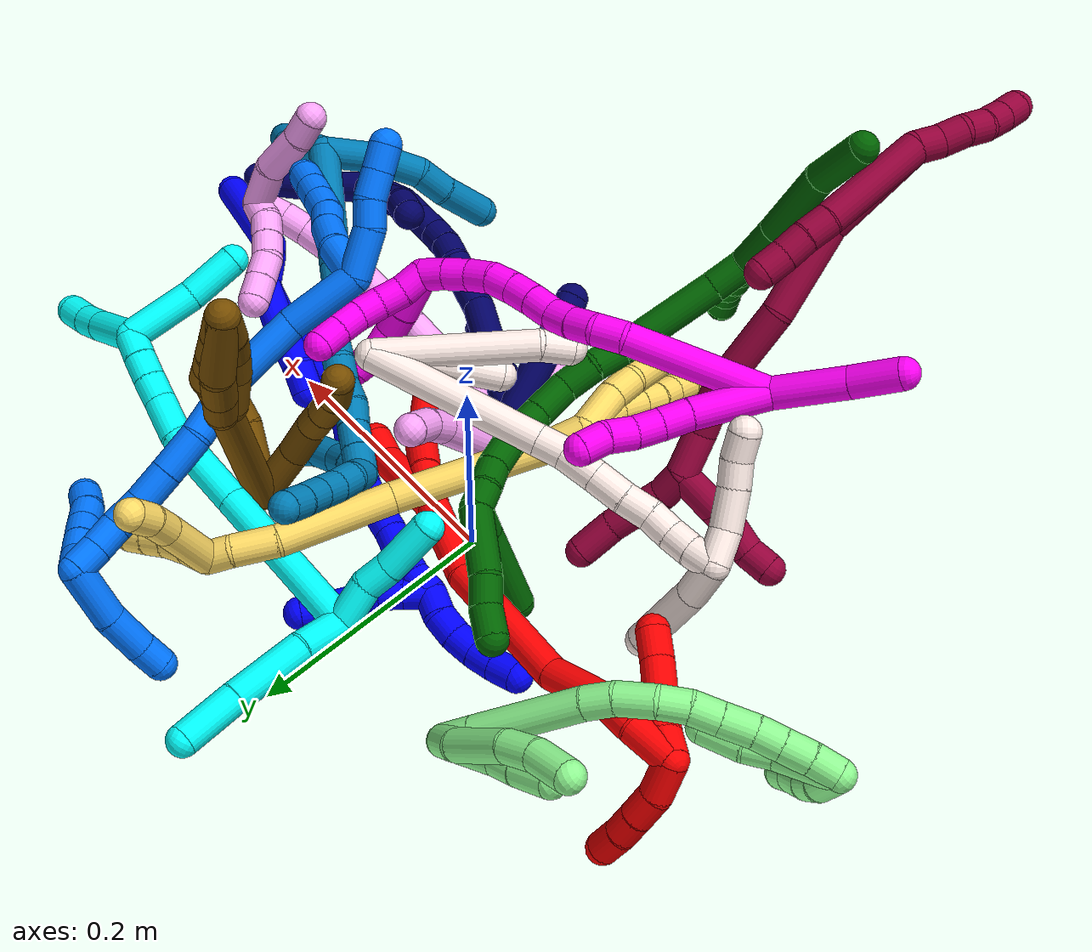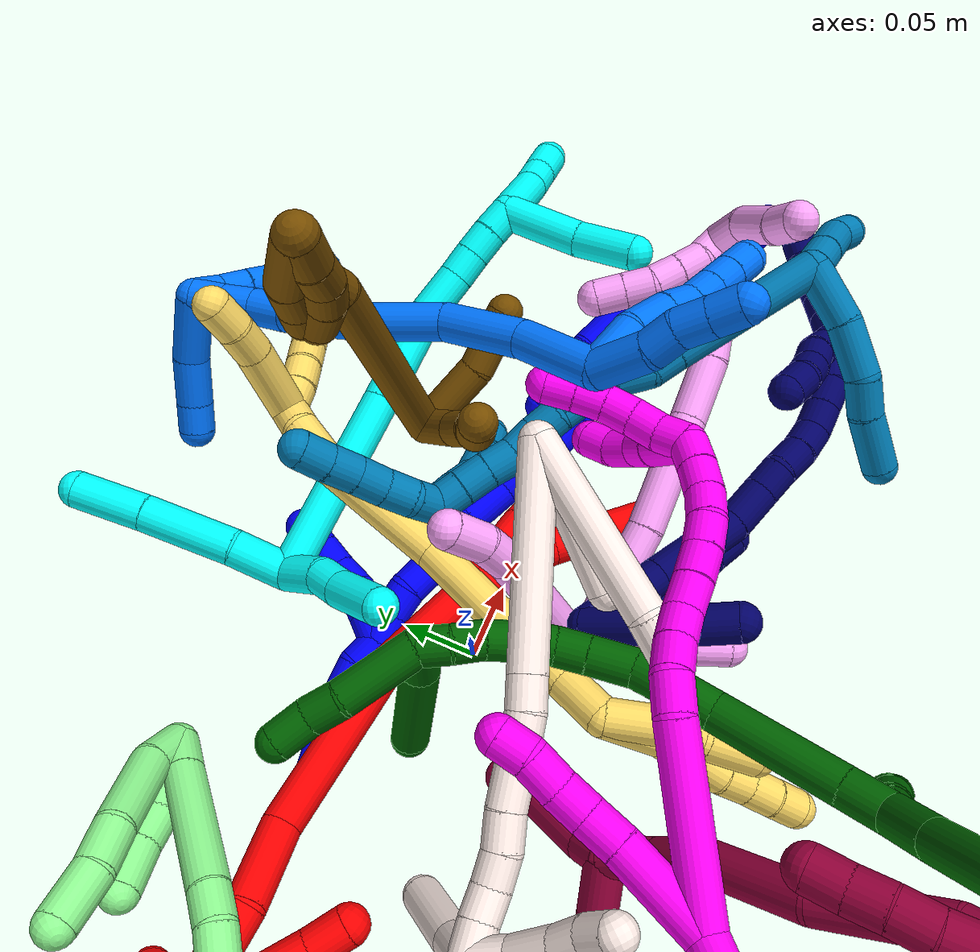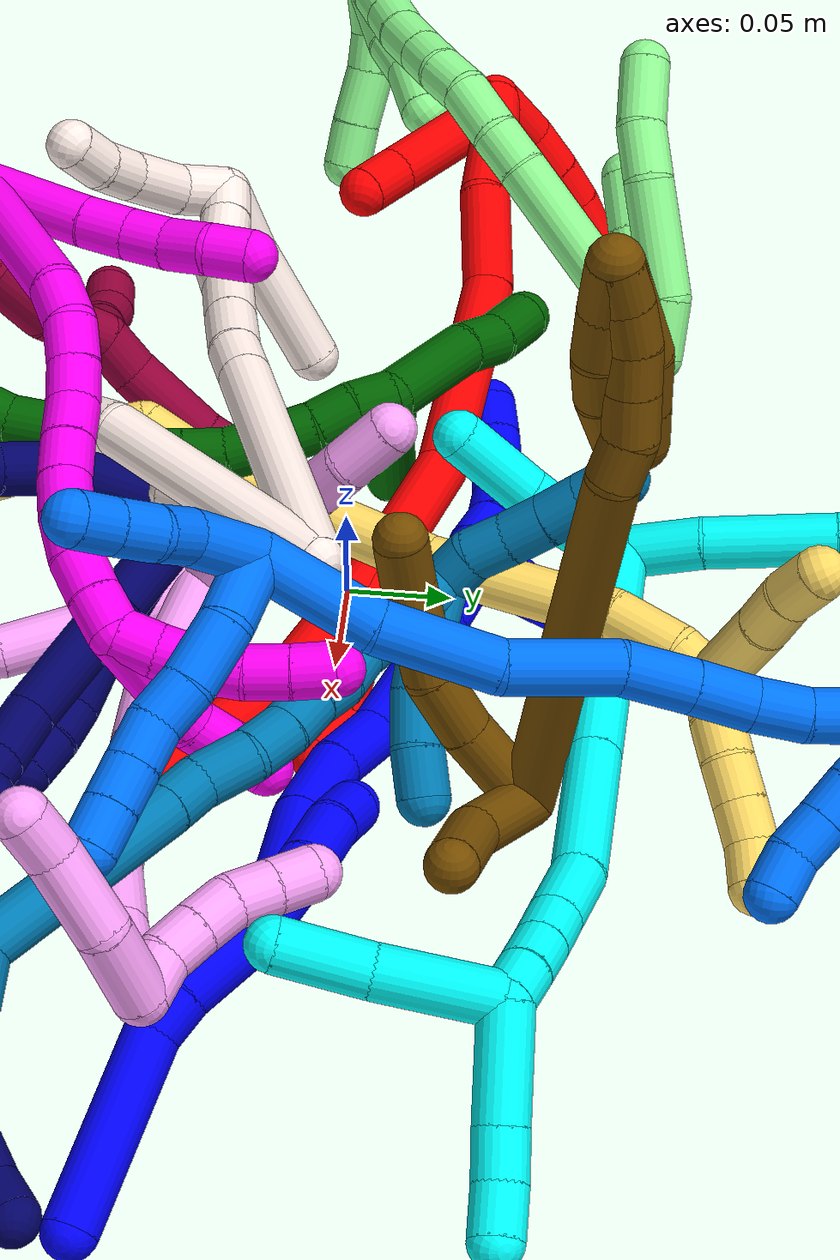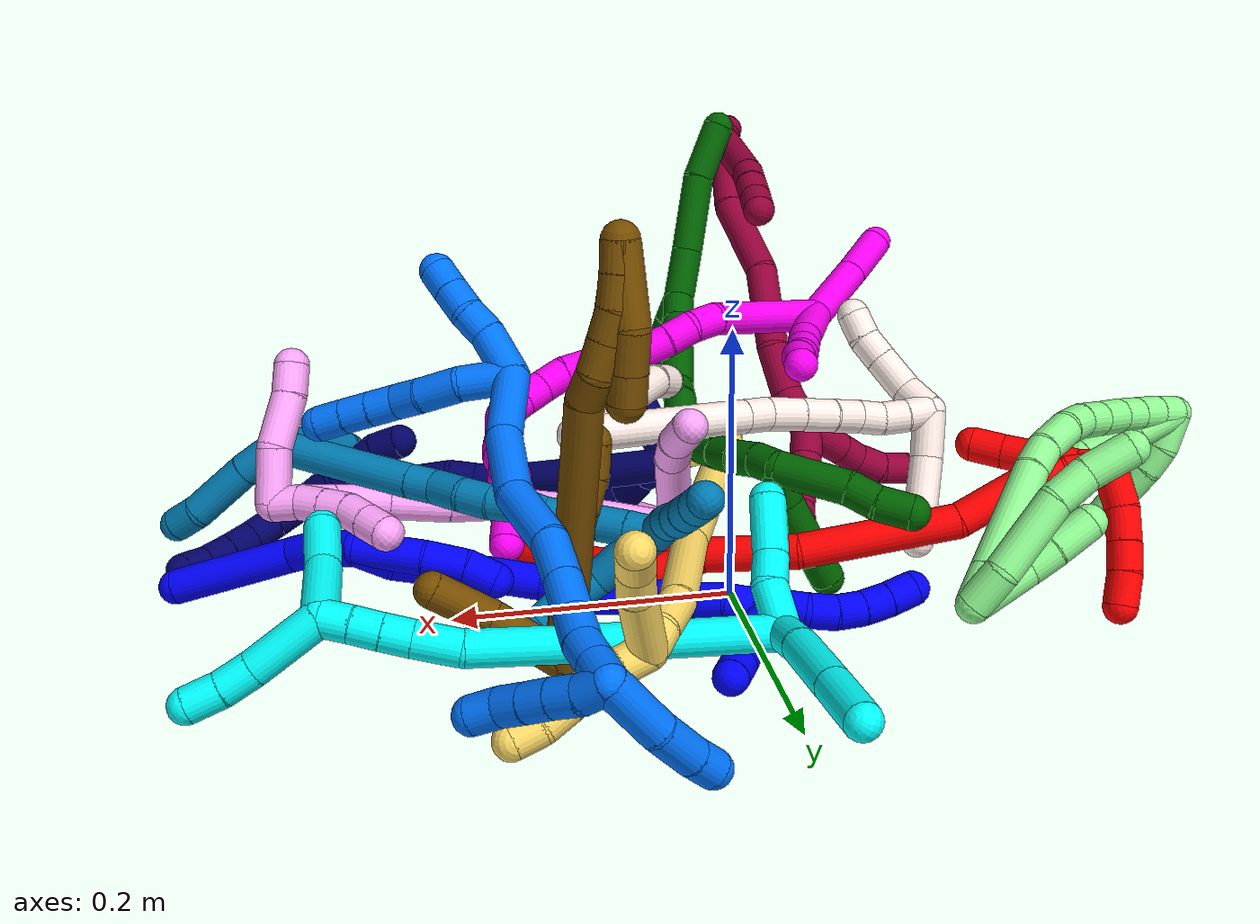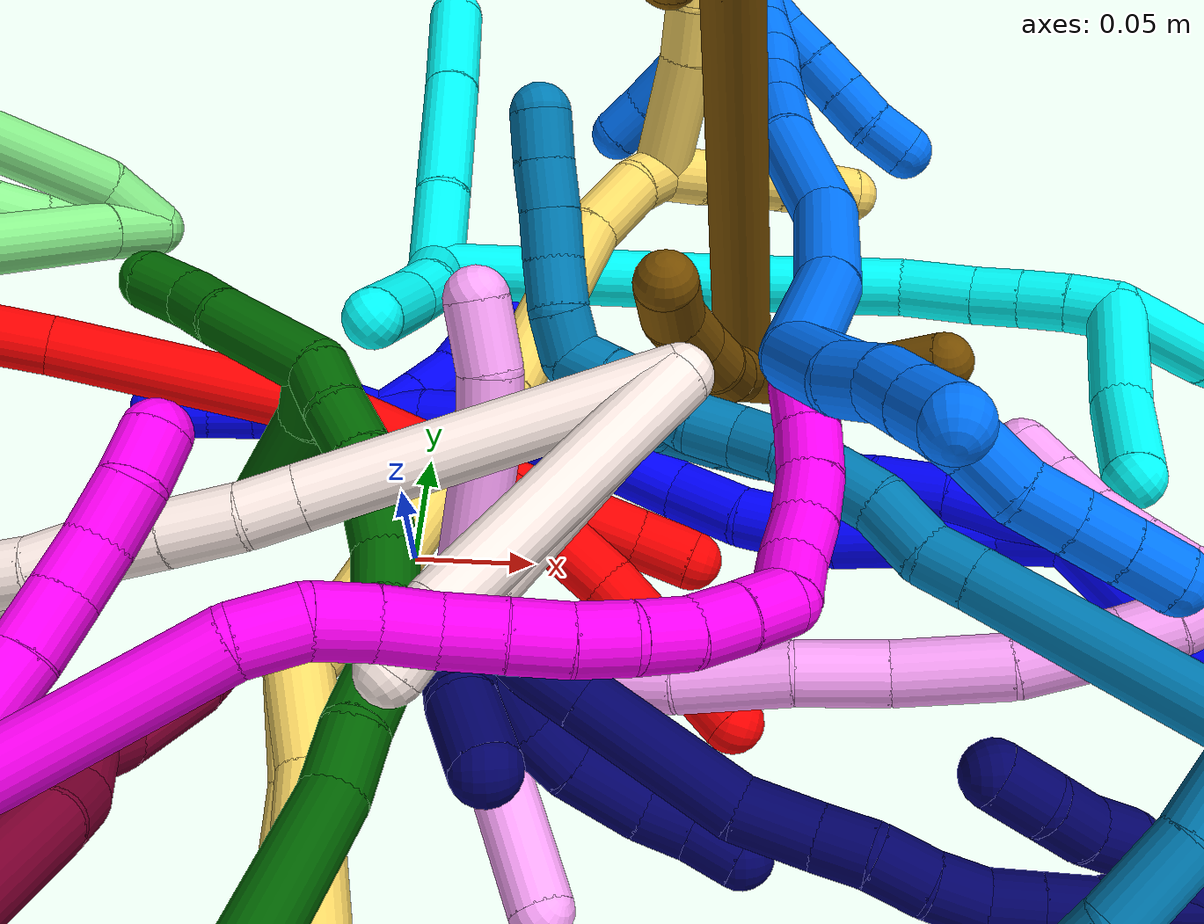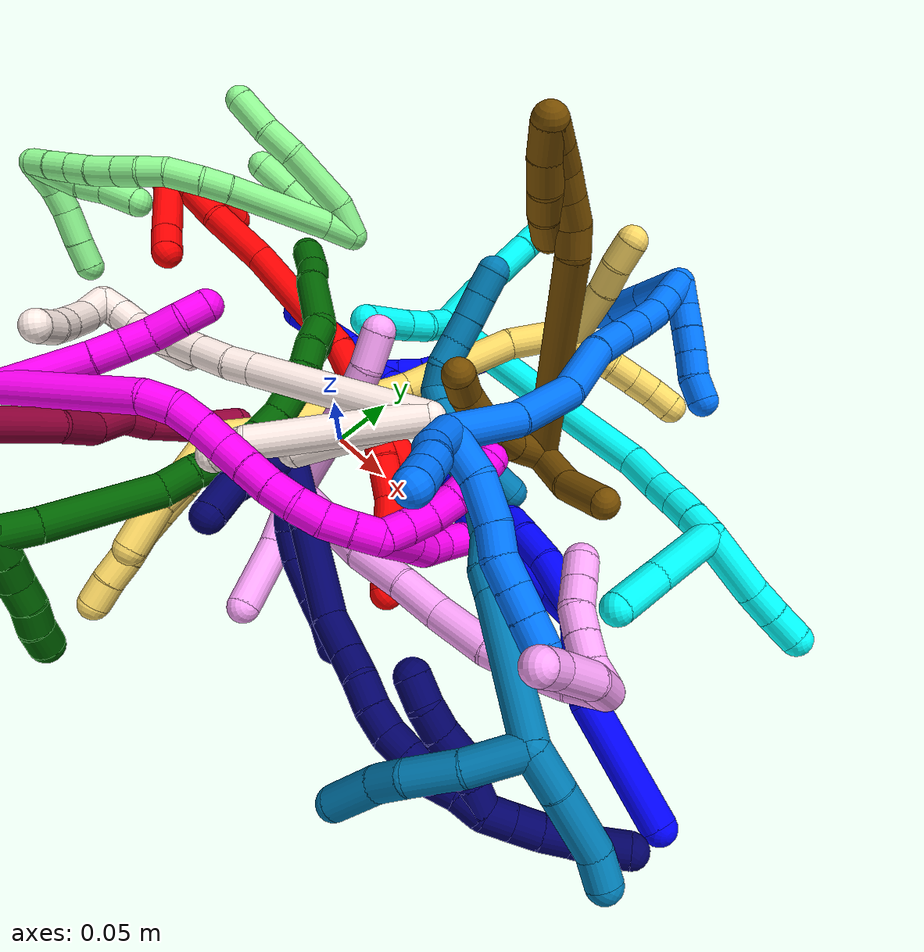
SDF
<sdf version="1.7">
 <world name="default">
  <plugin name="TubeGeneratorPlugin" filename="libtube_generator_plugin.so"/>
  <model name="photoneo_s_sensor">
   <static>1</static>
   <pose>0 0 2 1.57079 1.57079 3.14159</pose>
   <link name="link">
    <inertial><mass>0.1</mass></inertial>
    <sensor name="sensor" type="depth">
     <update_rate>30</update_rate>
     <camera>
      <horizontal_fov>1.22</horizontal_fov>
      <image><width>1920</width><height>1200</height><format>B8G8R8</format></image>
      <clip><near>0.1</near><far>4</far></clip>
      <depth_camera><output>points</output></depth_camera>
     </camera>
     <plugin name="camera_plugin" filename="libgazebo_ros_depth_camera.so">
      <baseline>0.2</baseline>
      <alwaysOn>1</alwaysOn>
      <updateRate>0.0</updateRate>
      <cameraName>camera_ir</cameraName>
      <imageTopicName>/camera/color/image_raw</imageTopicName>
      <cameraInfoTopicName>/camera/color/camera_info</cameraInfoTopicName>
      <depthImageTopicName>/camera/depth/image_raw</depthImageTopicName>
      <depthImageCameraInfoTopicName>/camera/depth/camera_info</depthImageCameraInfoTopicName>
      <pointCloudTopicName>/camera/depth/points</pointCloudTopicName>
      <frameName>fr_optical</frameName>
      <pointCloudCutoff>0.1</pointCloudCutoff>
      <pointCloudCutoffMax>2.0</pointCloudCutoffMax>
      <distortionK1>0</distortionK1>
      <distortionK2>0</distortionK2>
      <distortionK3>0</distortionK3>
      <distortionT1>0</distortionT1>
      <distortionT2>0</distortionT2>
      <CxPrime>0</CxPrime>
      <Cx>0</Cx>
      <Cy>0</Cy>
      <focalLength>0</focalLength>
      <hackBaseline>0</hackBaseline>
     </plugin>
    </sensor>
   </link>
  </model>
  <gravity>0 0 -9.8</gravity>
  <magnetic_field>6e-06 2.3e-05 -4.2e-05</magnetic_field>
  <atmosphere type="adiabatic"/>
  <physics name="default_physics" default="0" type="ode">
   <max_step_size>0.003</max_step_size>
   <real_time_factor>1</real_time_factor>
   <real_time_update_rate>1000</real_time_update_rate>
   <max_contacts>10000</max_contacts>
   <ode>
    <solver>
     <type>quick</type>
     <iters>100</iters>
     <sor>1.3</sor>
     <use_dynamic_moi_rescaling>0</use_dynamic_moi_rescaling>
    </solver>
    <constraints>
     <contact_max_correcting_vel>0</contact_max_correcting_vel>
     <contact_surface_layer>0.001</contact_surface_layer>
     <cfm>0</cfm>
     <erp>0.2</erp>
    </constraints>
   </ode>
  </physics>
  <scene><ambient>0.4 0.4 0.4 1</ambient><background>0.7 0.7 0.7 1</background><shadows>0</shadows></scene>
  <audio><device>default</device></audio>
  <spherical_coordinates>
   <surface_model>EARTH_WGS84</surface_model>
   <latitude_deg>0</latitude_deg>
   <longitude_deg>0</longitude_deg>
   <elevation>0</elevation>
   <heading_deg>0</heading_deg>
  </spherical_coordinates>
  <model name="bin">
   <static>1</static>
   <link name="bottom">
    <collision name="collision-bottom">
     <pose>0 0 -0.01 0 -0 0</pose>
     <geometry><box><size>0.8 0.6 0.02</size></box></geometry>
     <surface>
      <friction><ode><mu>100</mu><mu2>100</mu2></ode></friction>
      <contact><collide_bitmask>65535</collide_bitmask></contact>
     </surface>
    </collision>
   </link>
   <link name="west_wall">
    <collision name="collision-west_wall">
     <pose>-0.41 0 0.1 0 -0 0</pose>
     <geometry><box><size>0.02 0.6 0.2</size></box></geometry>
     <surface>
      <friction><ode><mu>100</mu><mu2>100</mu2></ode></friction>
      <contact><collide_bitmask>65535</collide_bitmask></contact>
     </surface>
    </collision>
   </link>
   <link name="east_wall">
    <collision name="collision-east_wall">
     <pose>0.41 0 0.1 0 -0 0</pose>
     <geometry><box><size>0.02 0.6 0.2</size></box></geometry>
     <surface>
      <friction><ode><mu>100</mu><mu2>100</mu2></ode></friction>
      <contact><collide_bitmask>65535</collide_bitmask></contact>
     </surface>
    </collision>
   </link>
   <link name="south_wall">
    <collision name="collision-south_wall">
     <pose>0 -0.31 0.1 0 -0 0</pose>
     <geometry><box><size>0.8 0.02 0.2</size></box></geometry>
     <surface>
      <friction><ode><mu>100</mu><mu2>100</mu2></ode></friction>
      <contact><collide_bitmask>65535</collide_bitmask></contact>
     </surface>
    </collision>
   </link>
   <link name="north_wall">
    <collision name="collision-north_wall">
     <pose>0 0.31 0.1 0 -0 0</pose>
     <geometry><box><size>0.8 0.02 0.2</size></box></geometry>
     <surface>
      <friction><ode><mu>100</mu><mu2>100</mu2></ode></friction>
      <contact><collide_bitmask>65535</collide_bitmask></contact>
     </surface>
    </collision>
   </link>
  </model>
  <model name="1">
   <static>0</static>
   <link name="1">
    <collision name="collision-cylinder-e_1_2_8">
     <pose>0.008578 -0.012638 0.010676 0.869338 0.478348 0.225463</pose>
     <geometry><cylinder><radius>0.0125</radius><length>0.037272</length></cylinder></geometry>
     <surface>
      <friction><ode><mu>1.16</mu><mu2>1.16</mu2><slip1>0</slip1><slip2>0</slip2></ode></friction>
      <contact><ode><kp>1e+06</kp><kd>1</kd><max_vel>0</max_vel><min_depth>0.001</min_depth></ode></contact>
     </surface>
    </collision>
    <visual name="visual-cylinder-e_1_2_8">
     <pose>0.008578 -0.012638 0.010676 0.869338 0.478348 0.225463</pose>
     <geometry><cylinder><radius>0.0125</radius><length>0.037272</length></cylinder></geometry>
     <material><ambient>0 0 1 1</ambient></material>
    </visual>
    <collision name="collision-cylinder-e_2_8_9">
     <pose>0.023897 -0.031507 0.027026 0.832198 0.674689 0.307548</pose>
     <geometry><cylinder><radius>0.0125</radius><length>0.021581</length></cylinder></geometry>
     <surface>
      <friction><ode><mu>1.16</mu><mu2>1.16</mu2><slip1>0</slip1><slip2>0</slip2></ode></friction>
      <contact><ode><kp>1e+06</kp><kd>1</kd><max_vel>0</max_vel><min_depth>0.001</min_depth></ode></contact>
     </surface>
    </collision>
    <visual name="visual-cylinder-e_2_8_9">
     <pose>0.023897 -0.031507 0.027026 0.832198 0.674689 0.307548</pose>
     <geometry><cylinder><radius>0.0125</radius><length>0.021581</length></cylinder></geometry>
     <material><ambient>0 0 1 1</ambient></material>
    </visual>
    <collision name="collision-cylinder-e_3_9_6">
     <pose>0.061929 -0.050255 0.063376 0.387422 0.75683 0.155671</pose>
     <geometry><cylinder><radius>0.0125</radius><length>0.091147</length></cylinder></geometry>
     <surface>
      <friction><ode><mu>1.16</mu><mu2>1.16</mu2><slip1>0</slip1><slip2>0</slip2></ode></friction>
      <contact><ode><kp>1e+06</kp><kd>1</kd><max_vel>0</max_vel><min_depth>0.001</min_depth></ode></contact>
     </surface>
    </collision>
    <visual name="visual-cylinder-e_3_9_6">
     <pose>0.061929 -0.050255 0.063376 0.387422 0.75683 0.155671</pose>
     <geometry><cylinder><radius>0.0125</radius><length>0.091147</length></cylinder></geometry>
     <material><ambient>0 0 1 1</ambient></material>
    </visual>
    <collision name="collision-cylinder-e_1_2_10">
     <pose>-0.008639 0.007843 -0.021275 -2.78839 -0.364004 1.60156</pose>
     <geometry><cylinder><radius>0.0125</radius><length>0.048529</length></cylinder></geometry>
     <surface>
      <friction><ode><mu>1.16</mu><mu2>1.16</mu2><slip1>0</slip1><slip2>0</slip2></ode></friction>
      <contact><ode><kp>1e+06</kp><kd>1</kd><max_vel>0</max_vel><min_depth>0.001</min_depth></ode></contact>
     </surface>
    </collision>
    <visual name="visual-cylinder-e_1_2_10">
     <pose>-0.008639 0.007843 -0.021275 -2.78839 -0.364004 1.60156</pose>
     <geometry><cylinder><radius>0.0125</radius><length>0.048529</length></cylinder></geometry>
     <material><ambient>0 0 1 1</ambient></material>
    </visual>
    <collision name="collision-cylinder-e_2_10_11">
     <pose>-0.021137 0.018476 -0.056361 -2.9423 -0.267412 1.86323</pose>
     <geometry><cylinder><radius>0.0125</radius><length>0.029217</length></cylinder></geometry>
     <surface>
      <friction><ode><mu>1.16</mu><mu2>1.16</mu2><slip1>0</slip1><slip2>0</slip2></ode></friction>
      <contact><ode><kp>1e+06</kp><kd>1</kd><max_vel>0</max_vel><min_depth>0.001</min_depth></ode></contact>
     </surface>
    </collision>
    <visual name="visual-cylinder-e_2_10_11">
     <pose>-0.021137 0.018476 -0.056361 -2.9423 -0.267412 1.86323</pose>
     <geometry><cylinder><radius>0.0125</radius><length>0.029217</length></cylinder></geometry>
     <material><ambient>0 0 1 1</ambient></material>
    </visual>
    <collision name="collision-cylinder-e_3_11_5">
     <pose>-0.025585 0.023534 -0.081048 -2.936 -0.052791 0.501107</pose>
     <geometry><cylinder><radius>0.0125</radius><length>0.022254</length></cylinder></geometry>
     <surface>
      <friction><ode><mu>1.16</mu><mu2>1.16</mu2><slip1>0</slip1><slip2>0</slip2></ode></friction>
      <contact><ode><kp>1e+06</kp><kd>1</kd><max_vel>0</max_vel><min_depth>0.001</min_depth></ode></contact>
     </surface>
    </collision>
    <visual name="visual-cylinder-e_3_11_5">
     <pose>-0.025585 0.023534 -0.081048 -2.936 -0.052791 0.501107</pose>
     <geometry><cylinder><radius>0.0125</radius><length>0.022254</length></cylinder></geometry>
     <material><ambient>0 0 1 1</ambient></material>
    </visual>
    <collision name="collision-cylinder-e_1_2_12">
     <pose>-0.00139 0.001599 -0.013249 -3.02148 -0.10378 1.42481</pose>
     <geometry><cylinder><radius>0.0125</radius><length>0.026835</length></cylinder></geometry>
     <surface>
      <friction><ode><mu>1.16</mu><mu2>1.16</mu2><slip1>0</slip1><slip2>0</slip2></ode></friction>
      <contact><ode><kp>1e+06</kp><kd>1</kd><max_vel>0</max_vel><min_depth>0.001</min_depth></ode></contact>
     </surface>
    </collision>
    <visual name="visual-cylinder-e_1_2_12">
     <pose>-0.00139 0.001599 -0.013249 -3.02148 -0.10378 1.42481</pose>
     <geometry><cylinder><radius>0.0125</radius><length>0.026835</length></cylinder></geometry>
     <material><ambient>0 0 1 1</ambient></material>
    </visual>
    <collision name="collision-cylinder-e_2_12_13">
     <pose>-0.012767 0.002751 -0.058053 3.12741 -0.306486 -3.04984</pose>
     <geometry><cylinder><radius>0.0125</radius><length>0.066202</length></cylinder></geometry>
     <surface>
      <friction><ode><mu>1.16</mu><mu2>1.16</mu2><slip1>0</slip1><slip2>0</slip2></ode></friction>
      <contact><ode><kp>1e+06</kp><kd>1</kd><max_vel>0</max_vel><min_depth>0.001</min_depth></ode></contact>
     </surface>
    </collision>
    <visual name="visual-cylinder-e_2_12_13">
     <pose>-0.012767 0.002751 -0.058053 3.12741 -0.306486 -3.04984</pose>
     <geometry><cylinder><radius>0.0125</radius><length>0.066202</length></cylinder></geometry>
     <material><ambient>0 0 1 1</ambient></material>
    </visual>
    <collision name="collision-cylinder-e_3_13_14">
     <pose>-0.029152 0.006927 -0.107502 -2.8887 -0.33326 1.84715</pose>
     <geometry><cylinder><radius>0.0125</radius><length>0.039115</length></cylinder></geometry>
     <surface>
      <friction><ode><mu>1.16</mu><mu2>1.16</mu2><slip1>0</slip1><slip2>0</slip2></ode></friction>
      <contact><ode><kp>1e+06</kp><kd>1</kd><max_vel>0</max_vel><min_depth>0.001</min_depth></ode></contact>
     </surface>
    </collision>
    <visual name="visual-cylinder-e_3_13_14">
     <pose>-0.029152 0.006927 -0.107502 -2.8887 -0.33326 1.84715</pose>
     <geometry><cylinder><radius>0.0125</radius><length>0.039115</length></cylinder></geometry>
     <material><ambient>0 0 1 1</ambient></material>
    </visual>
    <collision name="collision-cylinder-e_4_14_15">
     <pose>-0.038846 0.018278 -0.139195 -2.68803 -0.211567 0.862526</pose>
     <geometry><cylinder><radius>0.0125</radius><length>0.031401</length></cylinder></geometry>
     <surface>
      <friction><ode><mu>1.16</mu><mu2>1.16</mu2><slip1>0</slip1><slip2>0</slip2></ode></friction>
      <contact><ode><kp>1e+06</kp><kd>1</kd><max_vel>0</max_vel><min_depth>0.001</min_depth></ode></contact>
     </surface>
    </collision>
    <visual name="visual-cylinder-e_4_14_15">
     <pose>-0.038846 0.018278 -0.139195 -2.68803 -0.211567 0.862526</pose>
     <geometry><cylinder><radius>0.0125</radius><length>0.031401</length></cylinder></geometry>
     <material><ambient>0 0 1 1</ambient></material>
    </visual>
    <collision name="collision-cylinder-e_5_15_16">
     <pose>-0.050197 0.031234 -0.16648 -2.70885 -0.496746 1.71332</pose>
     <geometry><cylinder><radius>0.0125</radius><length>0.033798</length></cylinder></geometry>
     <surface>
      <friction><ode><mu>1.16</mu><mu2>1.16</mu2><slip1>0</slip1><slip2>0</slip2></ode></friction>
      <contact><ode><kp>1e+06</kp><kd>1</kd><max_vel>0</max_vel><min_depth>0.001</min_depth></ode></contact>
     </surface>
    </collision>
    <visual name="visual-cylinder-e_5_15_16">
     <pose>-0.050197 0.031234 -0.16648 -2.70885 -0.496746 1.71332</pose>
     <geometry><cylinder><radius>0.0125</radius><length>0.033798</length></cylinder></geometry>
     <material><ambient>0 0 1 1</ambient></material>
    </visual>
    <collision name="collision-cylinder-e_6_16_17">
     <pose>-0.062778 0.03996 -0.189446 -2.88418 -0.432695 2.07724</pose>
     <geometry><cylinder><radius>0.0125</radius><length>0.021594</length></cylinder></geometry>
     <surface>
      <friction><ode><mu>1.16</mu><mu2>1.16</mu2><slip1>0</slip1><slip2>0</slip2></ode></friction>
      <contact><ode><kp>1e+06</kp><kd>1</kd><max_vel>0</max_vel><min_depth>0.001</min_depth></ode></contact>
     </surface>
    </collision>
    <visual name="visual-cylinder-e_6_16_17">
     <pose>-0.062778 0.03996 -0.189446 -2.88418 -0.432695 2.07724</pose>
     <geometry><cylinder><radius>0.0125</radius><length>0.021594</length></cylinder></geometry>
     <material><ambient>0 0 1 1</ambient></material>
    </visual>
    <collision name="collision-cylinder-e_7_17_18">
     <pose>-0.071358 0.043991 -0.20851 -2.98268 -0.395484 2.38505</pose>
     <geometry><cylinder><radius>0.0125</radius><length>0.02104</length></cylinder></geometry>
     <surface>
      <friction><ode><mu>1.16</mu><mu2>1.16</mu2><slip1>0</slip1><slip2>0</slip2></ode></friction>
      <contact><ode><kp>1e+06</kp><kd>1</kd><max_vel>0</max_vel><min_depth>0.001</min_depth></ode></contact>
     </surface>
    </collision>
    <visual name="visual-cylinder-e_7_17_18">
     <pose>-0.071358 0.043991 -0.20851 -2.98268 -0.395484 2.38505</pose>
     <geometry><cylinder><radius>0.0125</radius><length>0.02104</length></cylinder></geometry>
     <material><ambient>0 0 1 1</ambient></material>
    </visual>
    <collision name="collision-cylinder-e_8_18_19">
     <pose>-0.080274 0.048716 -0.226239 -2.76839 -0.507521 1.88311</pose>
     <geometry><cylinder><radius>0.0125</radius><length>0.020012</length></cylinder></geometry>
     <surface>
      <friction><ode><mu>1.16</mu><mu2>1.16</mu2><slip1>0</slip1><slip2>0</slip2></ode></friction>
      <contact><ode><kp>1e+06</kp><kd>1</kd><max_vel>0</max_vel><min_depth>0.001</min_depth></ode></contact>
     </surface>
    </collision>
    <visual name="visual-cylinder-e_8_18_19">
     <pose>-0.080274 0.048716 -0.226239 -2.76839 -0.507521 1.88311</pose>
     <geometry><cylinder><radius>0.0125</radius><length>0.020012</length></cylinder></geometry>
     <material><ambient>0 0 1 1</ambient></material>
    </visual>
    <collision name="collision-cylinder-e_9_19_20">
     <pose>-0.088116 0.053129 -0.24385 -3.01292 -0.302498 2.34174</pose>
     <geometry><cylinder><radius>0.0125</radius><length>0.020003</length></cylinder></geometry>
     <surface>
      <friction><ode><mu>1.16</mu><mu2>1.16</mu2><slip1>0</slip1><slip2>0</slip2></ode></friction>
      <contact><ode><kp>1e+06</kp><kd>1</kd><max_vel>0</max_vel><min_depth>0.001</min_depth></ode></contact>
     </surface>
    </collision>
    <visual name="visual-cylinder-e_9_19_20">
     <pose>-0.088116 0.053129 -0.24385 -3.01292 -0.302498 2.34174</pose>
     <geometry><cylinder><radius>0.0125</radius><length>0.020003</length></cylinder></geometry>
     <material><ambient>0 0 1 1</ambient></material>
    </visual>
    <collision name="collision-cylinder-e_10_20_1">
     <pose>-0.094437 0.05347 -0.262702 3.04765 -0.340691 -2.60809</pose>
     <geometry><cylinder><radius>0.0125</radius><length>0.02</length></cylinder></geometry>
     <surface>
      <friction><ode><mu>1.16</mu><mu2>1.16</mu2><slip1>0</slip1><slip2>0</slip2></ode></friction>
      <contact><ode><kp>1e+06</kp><kd>1</kd><max_vel>0</max_vel><min_depth>0.001</min_depth></ode></contact>
     </surface>
    </collision>
    <visual name="visual-cylinder-e_10_20_1">
     <pose>-0.094437 0.05347 -0.262702 3.04765 -0.340691 -2.60809</pose>
     <geometry><cylinder><radius>0.0125</radius><length>0.02</length></cylinder></geometry>
     <material><ambient>0 0 1 1</ambient></material>
    </visual>
    <collision name="collision-cylinder-e_1_1_21">
     <pose>-0.10145 0.055727 -0.280842 -2.79714 -0.375902 1.65997</pose>
     <geometry><cylinder><radius>0.0125</radius><length>0.02</length></cylinder></geometry>
     <surface>
      <friction><ode><mu>1.16</mu><mu2>1.16</mu2><slip1>0</slip1><slip2>0</slip2></ode></friction>
      <contact><ode><kp>1e+06</kp><kd>1</kd><max_vel>0</max_vel><min_depth>0.001</min_depth></ode></contact>
     </surface>
    </collision>
    <visual name="visual-cylinder-e_1_1_21">
     <pose>-0.10145 0.055727 -0.280842 -2.79714 -0.375902 1.65997</pose>
     <geometry><cylinder><radius>0.0125</radius><length>0.02</length></cylinder></geometry>
     <material><ambient>0 0 1 1</ambient></material>
    </visual>
    <collision name="collision-cylinder-e_2_21_22">
     <pose>-0.108591 0.058739 -0.298975 3.12776 -0.35438 -3.06439</pose>
     <geometry><cylinder><radius>0.0125</radius><length>0.02</length></cylinder></geometry>
     <surface>
      <friction><ode><mu>1.16</mu><mu2>1.16</mu2><slip1>0</slip1><slip2>0</slip2></ode></friction>
      <contact><ode><kp>1e+06</kp><kd>1</kd><max_vel>0</max_vel><min_depth>0.001</min_depth></ode></contact>
     </surface>
    </collision>
    <visual name="visual-cylinder-e_2_21_22">
     <pose>-0.108591 0.058739 -0.298975 3.12776 -0.35438 -3.06439</pose>
     <geometry><cylinder><radius>0.0125</radius><length>0.02</length></cylinder></geometry>
     <material><ambient>0 0 1 1</ambient></material>
    </visual>
    <collision name="collision-cylinder-e_3_22_23">
     <pose>-0.117274 0.057457 -0.316808 3.00624 -0.548414 -2.66869</pose>
     <geometry><cylinder><radius>0.0125</radius><length>0.02</length></cylinder></geometry>
     <surface>
      <friction><ode><mu>1.16</mu><mu2>1.16</mu2><slip1>0</slip1><slip2>0</slip2></ode></friction>
      <contact><ode><kp>1e+06</kp><kd>1</kd><max_vel>0</max_vel><min_depth>0.001</min_depth></ode></contact>
     </surface>
    </collision>
    <visual name="visual-cylinder-e_3_22_23">
     <pose>-0.117274 0.057457 -0.316808 3.00624 -0.548414 -2.66869</pose>
     <geometry><cylinder><radius>0.0125</radius><length>0.02</length></cylinder></geometry>
     <material><ambient>0 0 1 1</ambient></material>
    </visual>
    <collision name="collision-cylinder-e_4_23_24">
     <pose>-0.128963 0.054811 -0.332736 2.94414 -0.704314 -2.61503</pose>
     <geometry><cylinder><radius>0.0125</radius><length>0.02</length></cylinder></geometry>
     <surface>
      <friction><ode><mu>1.16</mu><mu2>1.16</mu2><slip1>0</slip1><slip2>0</slip2></ode></friction>
      <contact><ode><kp>1e+06</kp><kd>1</kd><max_vel>0</max_vel><min_depth>0.001</min_depth></ode></contact>
     </surface>
    </collision>
    <visual name="visual-cylinder-e_4_23_24">
     <pose>-0.128963 0.054811 -0.332736 2.94414 -0.704314 -2.61503</pose>
     <geometry><cylinder><radius>0.0125</radius><length>0.02</length></cylinder></geometry>
     <material><ambient>0 0 1 1</ambient></material>
    </visual>
    <collision name="collision-cylinder-e_5_24_4">
     <pose>-0.142505 0.051451 -0.347033 2.8748 -0.784792 -2.51449</pose>
     <geometry><cylinder><radius>0.0125</radius><length>0.02</length></cylinder></geometry>
     <surface>
      <friction><ode><mu>1.16</mu><mu2>1.16</mu2><slip1>0</slip1><slip2>0</slip2></ode></friction>
      <contact><ode><kp>1e+06</kp><kd>1</kd><max_vel>0</max_vel><min_depth>0.001</min_depth></ode></contact>
     </surface>
    </collision>
    <visual name="visual-cylinder-e_5_24_4">
     <pose>-0.142505 0.051451 -0.347033 2.8748 -0.784792 -2.51449</pose>
     <geometry><cylinder><radius>0.0125</radius><length>0.02</length></cylinder></geometry>
     <material><ambient>0 0 1 1</ambient></material>
    </visual>
    <collision name="collision-cylinder-e_1_1_25">
     <pose>-0.092956 0.059907 -0.267274 -0.989307 0.503245 -0.275561</pose>
     <geometry><cylinder><radius>0.0125</radius><length>0.02</length></cylinder></geometry>
     <surface>
      <friction><ode><mu>1.16</mu><mu2>1.16</mu2><slip1>0</slip1><slip2>0</slip2></ode></friction>
      <contact><ode><kp>1e+06</kp><kd>1</kd><max_vel>0</max_vel><min_depth>0.001</min_depth></ode></contact>
     </surface>
    </collision>
    <visual name="visual-cylinder-e_1_1_25">
     <pose>-0.092956 0.059907 -0.267274 -0.989307 0.503245 -0.275561</pose>
     <geometry><cylinder><radius>0.0125</radius><length>0.02</length></cylinder></geometry>
     <material><ambient>0 0 1 1</ambient></material>
    </visual>
    <collision name="collision-cylinder-e_2_25_26">
     <pose>-0.083412 0.074652 -0.25771 -1.00136 0.491652 -0.272874</pose>
     <geometry><cylinder><radius>0.0125</radius><length>0.02</length></cylinder></geometry>
     <surface>
      <friction><ode><mu>1.16</mu><mu2>1.16</mu2><slip1>0</slip1><slip2>0</slip2></ode></friction>
      <contact><ode><kp>1e+06</kp><kd>1</kd><max_vel>0</max_vel><min_depth>0.001</min_depth></ode></contact>
     </surface>
    </collision>
    <visual name="visual-cylinder-e_2_25_26">
     <pose>-0.083412 0.074652 -0.25771 -1.00136 0.491652 -0.272874</pose>
     <geometry><cylinder><radius>0.0125</radius><length>0.02</length></cylinder></geometry>
     <material><ambient>0 0 1 1</ambient></material>
    </visual>
    <collision name="collision-cylinder-e_3_26_27">
     <pose>-0.074568 0.090993 -0.25109 -1.36444 0.425049 -0.347051</pose>
     <geometry><cylinder><radius>0.0125</radius><length>0.02</length></cylinder></geometry>
     <surface>
      <friction><ode><mu>1.16</mu><mu2>1.16</mu2><slip1>0</slip1><slip2>0</slip2></ode></friction>
      <contact><ode><kp>1e+06</kp><kd>1</kd><max_vel>0</max_vel><min_depth>0.001</min_depth></ode></contact>
     </surface>
    </collision>
    <visual name="visual-cylinder-e_3_26_27">
     <pose>-0.074568 0.090993 -0.25109 -1.36444 0.425049 -0.347051</pose>
     <geometry><cylinder><radius>0.0125</radius><length>0.02</length></cylinder></geometry>
     <material><ambient>0 0 1 1</ambient></material>
    </visual>
    <collision name="collision-cylinder-e_4_27_28">
     <pose>-0.066533 0.108685 -0.246449 -1.26461 0.401882 -0.29628</pose>
     <geometry><cylinder><radius>0.0125</radius><length>0.02</length></cylinder></geometry>
     <surface>
      <friction><ode><mu>1.16</mu><mu2>1.16</mu2><slip1>0</slip1><slip2>0</slip2></ode></friction>
      <contact><ode><kp>1e+06</kp><kd>1</kd><max_vel>0</max_vel><min_depth>0.001</min_depth></ode></contact>
     </surface>
    </collision>
    <visual name="visual-cylinder-e_4_27_28">
     <pose>-0.066533 0.108685 -0.246449 -1.26461 0.401882 -0.29628</pose>
     <geometry><cylinder><radius>0.0125</radius><length>0.02</length></cylinder></geometry>
     <material><ambient>0 0 1 1</ambient></material>
    </visual>
    <collision name="collision-cylinder-e_5_28_3">
     <pose>-0.059553 0.126393 -0.240389 -1.21826 0.311876 -0.218481</pose>
     <geometry><cylinder><radius>0.0125</radius><length>0.02</length></cylinder></geometry>
     <surface>
      <friction><ode><mu>1.16</mu><mu2>1.16</mu2><slip1>0</slip1><slip2>0</slip2></ode></friction>
      <contact><ode><kp>1e+06</kp><kd>1</kd><max_vel>0</max_vel><min_depth>0.001</min_depth></ode></contact>
     </surface>
    </collision>
    <visual name="visual-cylinder-e_5_28_3">
     <pose>-0.059553 0.126393 -0.240389 -1.21826 0.311876 -0.218481</pose>
     <geometry><cylinder><radius>0.0125</radius><length>0.02</length></cylinder></geometry>
     <material><ambient>0 0 1 1</ambient></material>
    </visual>
    <collision name="collision-sphere-3">
     <pose>-0.056484 0.135325 -0.237103 0 -0 0</pose>
     <geometry><sphere><radius>0.0125</radius></sphere></geometry>
     <surface>
      <friction><ode><mu>1.16</mu><mu2>1.16</mu2><slip1>0</slip1><slip2>0</slip2></ode></friction>
      <contact><ode><kp>1e+06</kp><kd>1</kd><max_vel>0</max_vel><min_depth>0.001</min_depth></ode></contact>
     </surface>
    </collision>
    <visual name="visual-sphere-3">
     <pose>-0.056484 0.135325 -0.237103 0 -0 0</pose>
     <geometry><sphere><radius>0.0125</radius></sphere></geometry>
     <material><ambient>0 0 1 1</ambient></material>
    </visual>
    <collision name="collision-sphere-28">
     <pose>-0.062621 0.11746 -0.243675 0 -0 0</pose>
     <geometry><sphere><radius>0.0125</radius></sphere></geometry>
     <surface>
      <friction><ode><mu>1.16</mu><mu2>1.16</mu2><slip1>0</slip1><slip2>0</slip2></ode></friction>
      <contact><ode><kp>1e+06</kp><kd>1</kd><max_vel>0</max_vel><min_depth>0.001</min_depth></ode></contact>
     </surface>
    </collision>
    <visual name="visual-sphere-28">
     <pose>-0.062621 0.11746 -0.243675 0 -0 0</pose>
     <geometry><sphere><radius>0.0125</radius></sphere></geometry>
     <material><ambient>0 0 1 1</ambient></material>
    </visual>
    <collision name="collision-sphere-27">
     <pose>-0.070444 0.09991 -0.249223 0 -0 0</pose>
     <geometry><sphere><radius>0.0125</radius></sphere></geometry>
     <surface>
      <friction><ode><mu>1.16</mu><mu2>1.16</mu2><slip1>0</slip1><slip2>0</slip2></ode></friction>
      <contact><ode><kp>1e+06</kp><kd>1</kd><max_vel>0</max_vel><min_depth>0.001</min_depth></ode></contact>
     </surface>
    </collision>
    <visual name="visual-sphere-27">
     <pose>-0.070444 0.09991 -0.249223 0 -0 0</pose>
     <geometry><sphere><radius>0.0125</radius></sphere></geometry>
     <material><ambient>0 0 1 1</ambient></material>
    </visual>
    <collision name="collision-sphere-26">
     <pose>-0.078692 0.082076 -0.252957 0 -0 0</pose>
     <geometry><sphere><radius>0.0125</radius></sphere></geometry>
     <surface>
      <friction><ode><mu>1.16</mu><mu2>1.16</mu2><slip1>0</slip1><slip2>0</slip2></ode></friction>
      <contact><ode><kp>1e+06</kp><kd>1</kd><max_vel>0</max_vel><min_depth>0.001</min_depth></ode></contact>
     </surface>
    </collision>
    <visual name="visual-sphere-26">
     <pose>-0.078692 0.082076 -0.252957 0 -0 0</pose>
     <geometry><sphere><radius>0.0125</radius></sphere></geometry>
     <material><ambient>0 0 1 1</ambient></material>
    </visual>
    <collision name="collision-sphere-25">
     <pose>-0.088133 0.067227 -0.262463 0 -0 0</pose>
     <geometry><sphere><radius>0.0125</radius></sphere></geometry>
     <surface>
      <friction><ode><mu>1.16</mu><mu2>1.16</mu2><slip1>0</slip1><slip2>0</slip2></ode></friction>
      <contact><ode><kp>1e+06</kp><kd>1</kd><max_vel>0</max_vel><min_depth>0.001</min_depth></ode></contact>
     </surface>
    </collision>
    <visual name="visual-sphere-25">
     <pose>-0.088133 0.067227 -0.262463 0 -0 0</pose>
     <geometry><sphere><radius>0.0125</radius></sphere></geometry>
     <material><ambient>0 0 1 1</ambient></material>
    </visual>
    <collision name="collision-sphere-4">
     <pose>-0.149572 0.049585 -0.353858 0 -0 0</pose>
     <geometry><sphere><radius>0.0125</radius></sphere></geometry>
     <surface>
      <friction><ode><mu>1.16</mu><mu2>1.16</mu2><slip1>0</slip1><slip2>0</slip2></ode></friction>
      <contact><ode><kp>1e+06</kp><kd>1</kd><max_vel>0</max_vel><min_depth>0.001</min_depth></ode></contact>
     </surface>
    </collision>
    <visual name="visual-sphere-4">
     <pose>-0.149572 0.049585 -0.353858 0 -0 0</pose>
     <geometry><sphere><radius>0.0125</radius></sphere></geometry>
     <material><ambient>0 0 1 1</ambient></material>
    </visual>
    <collision name="collision-sphere-24">
     <pose>-0.135438 0.053316 -0.340208 0 -0 0</pose>
     <geometry><sphere><radius>0.0125</radius></sphere></geometry>
     <surface>
      <friction><ode><mu>1.16</mu><mu2>1.16</mu2><slip1>0</slip1><slip2>0</slip2></ode></friction>
      <contact><ode><kp>1e+06</kp><kd>1</kd><max_vel>0</max_vel><min_depth>0.001</min_depth></ode></contact>
     </surface>
    </collision>
    <visual name="visual-sphere-24">
     <pose>-0.135438 0.053316 -0.340208 0 -0 0</pose>
     <geometry><sphere><radius>0.0125</radius></sphere></geometry>
     <material><ambient>0 0 1 1</ambient></material>
    </visual>
    <collision name="collision-sphere-23">
     <pose>-0.122488 0.056306 -0.325263 0 -0 0</pose>
     <geometry><sphere><radius>0.0125</radius></sphere></geometry>
     <surface>
      <friction><ode><mu>1.16</mu><mu2>1.16</mu2><slip1>0</slip1><slip2>0</slip2></ode></friction>
      <contact><ode><kp>1e+06</kp><kd>1</kd><max_vel>0</max_vel><min_depth>0.001</min_depth></ode></contact>
     </surface>
    </collision>
    <visual name="visual-sphere-23">
     <pose>-0.122488 0.056306 -0.325263 0 -0 0</pose>
     <geometry><sphere><radius>0.0125</radius></sphere></geometry>
     <material><ambient>0 0 1 1</ambient></material>
    </visual>
    <collision name="collision-sphere-22">
     <pose>-0.112061 0.058609 -0.308352 0 -0 0</pose>
     <geometry><sphere><radius>0.0125</radius></sphere></geometry>
     <surface>
      <friction><ode><mu>1.16</mu><mu2>1.16</mu2><slip1>0</slip1><slip2>0</slip2></ode></friction>
      <contact><ode><kp>1e+06</kp><kd>1</kd><max_vel>0</max_vel><min_depth>0.001</min_depth></ode></contact>
     </surface>
    </collision>
    <visual name="visual-sphere-22">
     <pose>-0.112061 0.058609 -0.308352 0 -0 0</pose>
     <geometry><sphere><radius>0.0125</radius></sphere></geometry>
     <material><ambient>0 0 1 1</ambient></material>
    </visual>
    <collision name="collision-sphere-21">
     <pose>-0.105121 0.058868 -0.289597 0 -0 0</pose>
     <geometry><sphere><radius>0.0125</radius></sphere></geometry>
     <surface>
      <friction><ode><mu>1.16</mu><mu2>1.16</mu2><slip1>0</slip1><slip2>0</slip2></ode></friction>
      <contact><ode><kp>1e+06</kp><kd>1</kd><max_vel>0</max_vel><min_depth>0.001</min_depth></ode></contact>
     </surface>
    </collision>
    <visual name="visual-sphere-21">
     <pose>-0.105121 0.058868 -0.289597 0 -0 0</pose>
     <geometry><sphere><radius>0.0125</radius></sphere></geometry>
     <material><ambient>0 0 1 1</ambient></material>
    </visual>
    <collision name="collision-sphere-1">
     <pose>-0.097779 0.052586 -0.272086 0 -0 0</pose>
     <geometry><sphere><radius>0.0125</radius></sphere></geometry>
     <surface>
      <friction><ode><mu>1.16</mu><mu2>1.16</mu2><slip1>0</slip1><slip2>0</slip2></ode></friction>
      <contact><ode><kp>1e+06</kp><kd>1</kd><max_vel>0</max_vel><min_depth>0.001</min_depth></ode></contact>
     </surface>
    </collision>
    <visual name="visual-sphere-1">
     <pose>-0.097779 0.052586 -0.272086 0 -0 0</pose>
     <geometry><sphere><radius>0.0125</radius></sphere></geometry>
     <material><ambient>0 0 1 1</ambient></material>
    </visual>
    <collision name="collision-sphere-11">
     <pose>-0.024998 0.021265 -0.070171 0 -0 0</pose>
     <geometry><sphere><radius>0.0125</radius></sphere></geometry>
     <surface>
      <friction><ode><mu>1.16</mu><mu2>1.16</mu2><slip1>0</slip1><slip2>0</slip2></ode></friction>
      <contact><ode><kp>1e+06</kp><kd>1</kd><max_vel>0</max_vel><min_depth>0.001</min_depth></ode></contact>
     </surface>
    </collision>
    <visual name="visual-sphere-11">
     <pose>-0.024998 0.021265 -0.070171 0 -0 0</pose>
     <geometry><sphere><radius>0.0125</radius></sphere></geometry>
     <material><ambient>0 0 1 1</ambient></material>
    </visual>
    <collision name="collision-sphere-10">
     <pose>-0.017277 0.015687 -0.04255 0 -0 0</pose>
     <geometry><sphere><radius>0.0125</radius></sphere></geometry>
     <surface>
      <friction><ode><mu>1.16</mu><mu2>1.16</mu2><slip1>0</slip1><slip2>0</slip2></ode></friction>
      <contact><ode><kp>1e+06</kp><kd>1</kd><max_vel>0</max_vel><min_depth>0.001</min_depth></ode></contact>
     </surface>
    </collision>
    <visual name="visual-sphere-10">
     <pose>-0.017277 0.015687 -0.04255 0 -0 0</pose>
     <geometry><sphere><radius>0.0125</radius></sphere></geometry>
     <material><ambient>0 0 1 1</ambient></material>
    </visual>
    <collision name="collision-sphere-6">
     <pose>0.093221 -0.062773 0.094053 0 -0 0</pose>
     <geometry><sphere><radius>0.0125</radius></sphere></geometry>
     <surface>
      <friction><ode><mu>1.16</mu><mu2>1.16</mu2><slip1>0</slip1><slip2>0</slip2></ode></friction>
      <contact><ode><kp>1e+06</kp><kd>1</kd><max_vel>0</max_vel><min_depth>0.001</min_depth></ode></contact>
     </surface>
    </collision>
    <visual name="visual-sphere-6">
     <pose>0.093221 -0.062773 0.094053 0 -0 0</pose>
     <geometry><sphere><radius>0.0125</radius></sphere></geometry>
     <material><ambient>0 0 1 1</ambient></material>
    </visual>
    <collision name="collision-sphere-9">
     <pose>0.030638 -0.037737 0.032699 0 -0 0</pose>
     <geometry><sphere><radius>0.0125</radius></sphere></geometry>
     <surface>
      <friction><ode><mu>1.16</mu><mu2>1.16</mu2><slip1>0</slip1><slip2>0</slip2></ode></friction>
      <contact><ode><kp>1e+06</kp><kd>1</kd><max_vel>0</max_vel><min_depth>0.001</min_depth></ode></contact>
     </surface>
    </collision>
    <visual name="visual-sphere-9">
     <pose>0.030638 -0.037737 0.032699 0 -0 0</pose>
     <geometry><sphere><radius>0.0125</radius></sphere></geometry>
     <material><ambient>0 0 1 1</ambient></material>
    </visual>
    <collision name="collision-sphere-2">
     <geometry><sphere><radius>0.0125</radius></sphere></geometry>
     <surface>
      <friction><ode><mu>1.16</mu><mu2>1.16</mu2><slip1>0</slip1><slip2>0</slip2></ode></friction>
      <contact><ode><kp>1e+06</kp><kd>1</kd><max_vel>0</max_vel><min_depth>0.001</min_depth></ode></contact>
     </surface>
    </collision>
    <visual name="visual-sphere-2">
     <geometry><sphere><radius>0.0125</radius></sphere></geometry>
     <material><ambient>0 0 1 1</ambient></material>
    </visual>
    <collision name="collision-sphere-19">
     <pose>-0.085137 0.051904 -0.234382 0 -0 0</pose>
     <geometry><sphere><radius>0.0125</radius></sphere></geometry>
     <surface>
      <friction><ode><mu>1.16</mu><mu2>1.16</mu2><slip1>0</slip1><slip2>0</slip2></ode></friction>
      <contact><ode><kp>1e+06</kp><kd>1</kd><max_vel>0</max_vel><min_depth>0.001</min_depth></ode></contact>
     </surface>
    </collision>
    <visual name="visual-sphere-19">
     <pose>-0.085137 0.051904 -0.234382 0 -0 0</pose>
     <geometry><sphere><radius>0.0125</radius></sphere></geometry>
     <material><ambient>0 0 1 1</ambient></material>
    </visual>
    <collision name="collision-sphere-8">
     <pose>0.017157 -0.025276 0.021353 0 -0 0</pose>
     <geometry><sphere><radius>0.0125</radius></sphere></geometry>
     <surface>
      <friction><ode><mu>1.16</mu><mu2>1.16</mu2><slip1>0</slip1><slip2>0</slip2></ode></friction>
      <contact><ode><kp>1e+06</kp><kd>1</kd><max_vel>0</max_vel><min_depth>0.001</min_depth></ode></contact>
     </surface>
    </collision>
    <visual name="visual-sphere-8">
     <pose>0.017157 -0.025276 0.021353 0 -0 0</pose>
     <geometry><sphere><radius>0.0125</radius></sphere></geometry>
     <material><ambient>0 0 1 1</ambient></material>
    </visual>
    <collision name="collision-sphere-5">
     <pose>-0.026172 0.025802 -0.091926 0 -0 0</pose>
     <geometry><sphere><radius>0.0125</radius></sphere></geometry>
     <surface>
      <friction><ode><mu>1.16</mu><mu2>1.16</mu2><slip1>0</slip1><slip2>0</slip2></ode></friction>
      <contact><ode><kp>1e+06</kp><kd>1</kd><max_vel>0</max_vel><min_depth>0.001</min_depth></ode></contact>
     </surface>
    </collision>
    <visual name="visual-sphere-5">
     <pose>-0.026172 0.025802 -0.091926 0 -0 0</pose>
     <geometry><sphere><radius>0.0125</radius></sphere></geometry>
     <material><ambient>0 0 1 1</ambient></material>
    </visual>
    <collision name="collision-sphere-12">
     <pose>-0.00278 0.003198 -0.026498 0 -0 0</pose>
     <geometry><sphere><radius>0.0125</radius></sphere></geometry>
     <surface>
      <friction><ode><mu>1.16</mu><mu2>1.16</mu2><slip1>0</slip1><slip2>0</slip2></ode></friction>
      <contact><ode><kp>1e+06</kp><kd>1</kd><max_vel>0</max_vel><min_depth>0.001</min_depth></ode></contact>
     </surface>
    </collision>
    <visual name="visual-sphere-12">
     <pose>-0.00278 0.003198 -0.026498 0 -0 0</pose>
     <geometry><sphere><radius>0.0125</radius></sphere></geometry>
     <material><ambient>0 0 1 1</ambient></material>
    </visual>
    <collision name="collision-sphere-13">
     <pose>-0.022754 0.002303 -0.089609 0 -0 0</pose>
     <geometry><sphere><radius>0.0125</radius></sphere></geometry>
     <surface>
      <friction><ode><mu>1.16</mu><mu2>1.16</mu2><slip1>0</slip1><slip2>0</slip2></ode></friction>
      <contact><ode><kp>1e+06</kp><kd>1</kd><max_vel>0</max_vel><min_depth>0.001</min_depth></ode></contact>
     </surface>
    </collision>
    <visual name="visual-sphere-13">
     <pose>-0.022754 0.002303 -0.089609 0 -0 0</pose>
     <geometry><sphere><radius>0.0125</radius></sphere></geometry>
     <material><ambient>0 0 1 1</ambient></material>
    </visual>
    <collision name="collision-sphere-14">
     <pose>-0.035549 0.011551 -0.125396 0 -0 0</pose>
     <geometry><sphere><radius>0.0125</radius></sphere></geometry>
     <surface>
      <friction><ode><mu>1.16</mu><mu2>1.16</mu2><slip1>0</slip1><slip2>0</slip2></ode></friction>
      <contact><ode><kp>1e+06</kp><kd>1</kd><max_vel>0</max_vel><min_depth>0.001</min_depth></ode></contact>
     </surface>
    </collision>
    <visual name="visual-sphere-14">
     <pose>-0.035549 0.011551 -0.125396 0 -0 0</pose>
     <geometry><sphere><radius>0.0125</radius></sphere></geometry>
     <material><ambient>0 0 1 1</ambient></material>
    </visual>
    <collision name="collision-sphere-15">
     <pose>-0.042143 0.025004 -0.152993 0 -0 0</pose>
     <geometry><sphere><radius>0.0125</radius></sphere></geometry>
     <surface>
      <friction><ode><mu>1.16</mu><mu2>1.16</mu2><slip1>0</slip1><slip2>0</slip2></ode></friction>
      <contact><ode><kp>1e+06</kp><kd>1</kd><max_vel>0</max_vel><min_depth>0.001</min_depth></ode></contact>
     </surface>
    </collision>
    <visual name="visual-sphere-15">
     <pose>-0.042143 0.025004 -0.152993 0 -0 0</pose>
     <geometry><sphere><radius>0.0125</radius></sphere></geometry>
     <material><ambient>0 0 1 1</ambient></material>
    </visual>
    <collision name="collision-sphere-16">
     <pose>-0.05825 0.037464 -0.179967 0 -0 0</pose>
     <geometry><sphere><radius>0.0125</radius></sphere></geometry>
     <surface>
      <friction><ode><mu>1.16</mu><mu2>1.16</mu2><slip1>0</slip1><slip2>0</slip2></ode></friction>
      <contact><ode><kp>1e+06</kp><kd>1</kd><max_vel>0</max_vel><min_depth>0.001</min_depth></ode></contact>
     </surface>
    </collision>
    <visual name="visual-sphere-16">
     <pose>-0.05825 0.037464 -0.179967 0 -0 0</pose>
     <geometry><sphere><radius>0.0125</radius></sphere></geometry>
     <material><ambient>0 0 1 1</ambient></material>
    </visual>
    <collision name="collision-sphere-17">
     <pose>-0.067305 0.042455 -0.198925 0 -0 0</pose>
     <geometry><sphere><radius>0.0125</radius></sphere></geometry>
     <surface>
      <friction><ode><mu>1.16</mu><mu2>1.16</mu2><slip1>0</slip1><slip2>0</slip2></ode></friction>
      <contact><ode><kp>1e+06</kp><kd>1</kd><max_vel>0</max_vel><min_depth>0.001</min_depth></ode></contact>
     </surface>
    </collision>
    <visual name="visual-sphere-17">
     <pose>-0.067305 0.042455 -0.198925 0 -0 0</pose>
     <geometry><sphere><radius>0.0125</radius></sphere></geometry>
     <material><ambient>0 0 1 1</ambient></material>
    </visual>
    <collision name="collision-sphere-18">
     <pose>-0.075411 0.045528 -0.218096 0 -0 0</pose>
     <geometry><sphere><radius>0.0125</radius></sphere></geometry>
     <surface>
      <friction><ode><mu>1.16</mu><mu2>1.16</mu2><slip1>0</slip1><slip2>0</slip2></ode></friction>
      <contact><ode><kp>1e+06</kp><kd>1</kd><max_vel>0</max_vel><min_depth>0.001</min_depth></ode></contact>
     </surface>
    </collision>
    <visual name="visual-sphere-18">
     <pose>-0.075411 0.045528 -0.218096 0 -0 0</pose>
     <geometry><sphere><radius>0.0125</radius></sphere></geometry>
     <material><ambient>0 0 1 1</ambient></material>
    </visual>
    <collision name="collision-sphere-20">
     <pose>-0.091096 0.054354 -0.253319 0 -0 0</pose>
     <geometry><sphere><radius>0.0125</radius></sphere></geometry>
     <surface>
      <friction><ode><mu>1.16</mu><mu2>1.16</mu2><slip1>0</slip1><slip2>0</slip2></ode></friction>
      <contact><ode><kp>1e+06</kp><kd>1</kd><max_vel>0</max_vel><min_depth>0.001</min_depth></ode></contact>
     </surface>
    </collision>
    <visual name="visual-sphere-20">
     <pose>-0.091096 0.054354 -0.253319 0 -0 0</pose>
     <geometry><sphere><radius>0.0125</radius></sphere></geometry>
     <material><ambient>0 0 1 1</ambient></material>
    </visual>
    <inertial>
     <pose>-0.036928 0.023347 -0.128066 0 -0 0</pose>
     <mass>0.75</mass>
     <inertia>
      <ixx>6.2e-05</ixx>
      <ixy>0</ixy>
      <ixz>0</ixz>
      <iyy>0.000158</iyy>
      <iyz>0</iyz>
      <izz>-4.5e-05</izz>
     </inertia>
    </inertial>
   </link>
   <pose>0.262371 -0.010515 0.056323 0.347745 1.02464 0.269716</pose>
  </model>
  <model name="2">
   <static>0</static>
   <link name="2">
    <collision name="collision-cylinder-e_1_2_8">
     <pose>0.000987 -0.00755 -0.018478 2.75371 0.049424 0.250366</pose>
     <geometry><cylinder><radius>0.0125</radius><length>0.039971</length></cylinder></geometry>
     <surface>
      <friction><ode><mu>1.16</mu><mu2>1.16</mu2><slip1>0</slip1><slip2>0</slip2></ode></friction>
      <contact><ode><kp>1e+06</kp><kd>1</kd><max_vel>0</max_vel><min_depth>0.001</min_depth></ode></contact>
     </surface>
    </collision>
    <visual name="visual-cylinder-e_1_2_8">
     <pose>0.000987 -0.00755 -0.018478 2.75371 0.049424 0.250366</pose>
     <geometry><cylinder><radius>0.0125</radius><length>0.039971</length></cylinder></geometry>
     <material><ambient>1 0 0 1</ambient></material>
    </visual>
    <collision name="collision-cylinder-e_2_8_9">
     <pose>0.000599 -0.021919 -0.052344 2.72444 -0.081557 -0.380871</pose>
     <geometry><cylinder><radius>0.0125</radius><length>0.033774</length></cylinder></geometry>
     <surface>
      <friction><ode><mu>1.16</mu><mu2>1.16</mu2><slip1>0</slip1><slip2>0</slip2></ode></friction>
      <contact><ode><kp>1e+06</kp><kd>1</kd><max_vel>0</max_vel><min_depth>0.001</min_depth></ode></contact>
     </surface>
    </collision>
    <visual name="visual-cylinder-e_2_8_9">
     <pose>0.000599 -0.021919 -0.052344 2.72444 -0.081557 -0.380871</pose>
     <geometry><cylinder><radius>0.0125</radius><length>0.033774</length></cylinder></geometry>
     <material><ambient>1 0 0 1</ambient></material>
    </visual>
    <collision name="collision-cylinder-e_3_9_6">
     <pose>0.002492 -0.052377 -0.097468 2.46994 0.085826 0.244808</pose>
     <geometry><cylinder><radius>0.0125</radius><length>0.076255</length></cylinder></geometry>
     <surface>
      <friction><ode><mu>1.16</mu><mu2>1.16</mu2><slip1>0</slip1><slip2>0</slip2></ode></friction>
      <contact><ode><kp>1e+06</kp><kd>1</kd><max_vel>0</max_vel><min_depth>0.001</min_depth></ode></contact>
     </surface>
    </collision>
    <visual name="visual-cylinder-e_3_9_6">
     <pose>0.002492 -0.052377 -0.097468 2.46994 0.085826 0.244808</pose>
     <geometry><cylinder><radius>0.0125</radius><length>0.076255</length></cylinder></geometry>
     <material><ambient>1 0 0 1</ambient></material>
    </visual>
    <collision name="collision-cylinder-e_1_2_10">
     <pose>-0.001305 -0.000498 -0.037721 3.12838 -0.034576 -2.41157</pose>
     <geometry><cylinder><radius>0.0125</radius><length>0.075493</length></cylinder></geometry>
     <surface>
      <friction><ode><mu>1.16</mu><mu2>1.16</mu2><slip1>0</slip1><slip2>0</slip2></ode></friction>
      <contact><ode><kp>1e+06</kp><kd>1</kd><max_vel>0</max_vel><min_depth>0.001</min_depth></ode></contact>
     </surface>
    </collision>
    <visual name="visual-cylinder-e_1_2_10">
     <pose>-0.001305 -0.000498 -0.037721 3.12838 -0.034576 -2.41157</pose>
     <geometry><cylinder><radius>0.0125</radius><length>0.075493</length></cylinder></geometry>
     <material><ambient>1 0 0 1</ambient></material>
    </visual>
    <collision name="collision-cylinder-e_2_10_5">
     <pose>-0.000426 -0.003163 -0.087302 2.96097 0.179196 1.56283</pose>
     <geometry><cylinder><radius>0.0125</radius><length>0.024507</length></cylinder></geometry>
     <surface>
      <friction><ode><mu>1.16</mu><mu2>1.16</mu2><slip1>0</slip1><slip2>0</slip2></ode></friction>
      <contact><ode><kp>1e+06</kp><kd>1</kd><max_vel>0</max_vel><min_depth>0.001</min_depth></ode></contact>
     </surface>
    </collision>
    <visual name="visual-cylinder-e_2_10_5">
     <pose>-0.000426 -0.003163 -0.087302 2.96097 0.179196 1.56283</pose>
     <geometry><cylinder><radius>0.0125</radius><length>0.024507</length></cylinder></geometry>
     <material><ambient>1 0 0 1</ambient></material>
    </visual>
    <collision name="collision-cylinder-e_1_2_11">
     <pose>-0.006527 0.007991 0.032334 -0.242277 -0.193512 0.02363</pose>
     <geometry><cylinder><radius>0.0125</radius><length>0.06788</length></cylinder></geometry>
     <surface>
      <friction><ode><mu>1.16</mu><mu2>1.16</mu2><slip1>0</slip1><slip2>0</slip2></ode></friction>
      <contact><ode><kp>1e+06</kp><kd>1</kd><max_vel>0</max_vel><min_depth>0.001</min_depth></ode></contact>
     </surface>
    </collision>
    <visual name="visual-cylinder-e_1_2_11">
     <pose>-0.006527 0.007991 0.032334 -0.242277 -0.193512 0.02363</pose>
     <geometry><cylinder><radius>0.0125</radius><length>0.06788</length></cylinder></geometry>
     <material><ambient>1 0 0 1</ambient></material>
    </visual>
    <collision name="collision-cylinder-e_2_11_12">
     <pose>-0.022951 0.014661 0.120319 0.023726 -0.175956 -0.002093</pose>
     <geometry><cylinder><radius>0.0125</radius><length>0.113079</length></cylinder></geometry>
     <surface>
      <friction><ode><mu>1.16</mu><mu2>1.16</mu2><slip1>0</slip1><slip2>0</slip2></ode></friction>
      <contact><ode><kp>1e+06</kp><kd>1</kd><max_vel>0</max_vel><min_depth>0.001</min_depth></ode></contact>
     </surface>
    </collision>
    <visual name="visual-cylinder-e_2_11_12">
     <pose>-0.022951 0.014661 0.120319 0.023726 -0.175956 -0.002093</pose>
     <geometry><cylinder><radius>0.0125</radius><length>0.113079</length></cylinder></geometry>
     <material><ambient>1 0 0 1</ambient></material>
    </visual>
    <collision name="collision-cylinder-e_3_12_13">
     <pose>-0.031141 0.006834 0.201017 0.254139 0.065865 0.008418</pose>
     <geometry><cylinder><radius>0.0125</radius><length>0.051869</length></cylinder></geometry>
     <surface>
      <friction><ode><mu>1.16</mu><mu2>1.16</mu2><slip1>0</slip1><slip2>0</slip2></ode></friction>
      <contact><ode><kp>1e+06</kp><kd>1</kd><max_vel>0</max_vel><min_depth>0.001</min_depth></ode></contact>
     </surface>
    </collision>
    <visual name="visual-cylinder-e_3_12_13">
     <pose>-0.031141 0.006834 0.201017 0.254139 0.065865 0.008418</pose>
     <geometry><cylinder><radius>0.0125</radius><length>0.051869</length></cylinder></geometry>
     <material><ambient>1 0 0 1</ambient></material>
    </visual>
    <collision name="collision-cylinder-e_4_13_14">
     <pose>-0.031557 -0.000885 0.241253 0.079703 -0.138426 -0.005528</pose>
     <geometry><cylinder><radius>0.0125</radius><length>0.030767</length></cylinder></geometry>
     <surface>
      <friction><ode><mu>1.16</mu><mu2>1.16</mu2><slip1>0</slip1><slip2>0</slip2></ode></friction>
      <contact><ode><kp>1e+06</kp><kd>1</kd><max_vel>0</max_vel><min_depth>0.001</min_depth></ode></contact>
     </surface>
    </collision>
    <visual name="visual-cylinder-e_4_13_14">
     <pose>-0.031557 -0.000885 0.241253 0.079703 -0.138426 -0.005528</pose>
     <geometry><cylinder><radius>0.0125</radius><length>0.030767</length></cylinder></geometry>
     <material><ambient>1 0 0 1</ambient></material>
    </visual>
    <collision name="collision-cylinder-e_5_14_1">
     <pose>-0.038963 -0.005379 0.273547 0.189486 -0.294509 -0.028189</pose>
     <geometry><cylinder><radius>0.0125</radius><length>0.036403</length></cylinder></geometry>
     <surface>
      <friction><ode><mu>1.16</mu><mu2>1.16</mu2><slip1>0</slip1><slip2>0</slip2></ode></friction>
      <contact><ode><kp>1e+06</kp><kd>1</kd><max_vel>0</max_vel><min_depth>0.001</min_depth></ode></contact>
     </surface>
    </collision>
    <visual name="visual-cylinder-e_5_14_1">
     <pose>-0.038963 -0.005379 0.273547 0.189486 -0.294509 -0.028189</pose>
     <geometry><cylinder><radius>0.0125</radius><length>0.036403</length></cylinder></geometry>
     <material><ambient>1 0 0 1</ambient></material>
    </visual>
    <collision name="collision-cylinder-e_1_1_15">
     <pose>-0.0564 0.000499 0.289584 -1.68703 -0.921748 1.01775</pose>
     <geometry><cylinder><radius>0.0125</radius><length>0.030511</length></cylinder></geometry>
     <surface>
      <friction><ode><mu>1.16</mu><mu2>1.16</mu2><slip1>0</slip1><slip2>0</slip2></ode></friction>
      <contact><ode><kp>1e+06</kp><kd>1</kd><max_vel>0</max_vel><min_depth>0.001</min_depth></ode></contact>
     </surface>
    </collision>
    <visual name="visual-cylinder-e_1_1_15">
     <pose>-0.0564 0.000499 0.289584 -1.68703 -0.921748 1.01775</pose>
     <geometry><cylinder><radius>0.0125</radius><length>0.030511</length></cylinder></geometry>
     <material><ambient>1 0 0 1</ambient></material>
    </visual>
    <collision name="collision-cylinder-e_2_15_16">
     <pose>-0.077179 0.017598 0.28487 -2.00116 -0.778952 1.13869</pose>
     <geometry><cylinder><radius>0.0125</radius><length>0.024555</length></cylinder></geometry>
     <surface>
      <friction><ode><mu>1.16</mu><mu2>1.16</mu2><slip1>0</slip1><slip2>0</slip2></ode></friction>
      <contact><ode><kp>1e+06</kp><kd>1</kd><max_vel>0</max_vel><min_depth>0.001</min_depth></ode></contact>
     </surface>
    </collision>
    <visual name="visual-cylinder-e_2_15_16">
     <pose>-0.077179 0.017598 0.28487 -2.00116 -0.778952 1.13869</pose>
     <geometry><cylinder><radius>0.0125</radius><length>0.024555</length></cylinder></geometry>
     <material><ambient>1 0 0 1</ambient></material>
    </visual>
    <collision name="collision-cylinder-e_3_16_17">
     <pose>-0.09335 0.031865 0.277664 -2.08336 -0.804783 1.25839</pose>
     <geometry><cylinder><radius>0.0125</radius><length>0.020943</length></cylinder></geometry>
     <surface>
      <friction><ode><mu>1.16</mu><mu2>1.16</mu2><slip1>0</slip1><slip2>0</slip2></ode></friction>
      <contact><ode><kp>1e+06</kp><kd>1</kd><max_vel>0</max_vel><min_depth>0.001</min_depth></ode></contact>
     </surface>
    </collision>
    <visual name="visual-cylinder-e_3_16_17">
     <pose>-0.09335 0.031865 0.277664 -2.08336 -0.804783 1.25839</pose>
     <geometry><cylinder><radius>0.0125</radius><length>0.020943</length></cylinder></geometry>
     <material><ambient>1 0 0 1</ambient></material>
    </visual>
    <collision name="collision-cylinder-e_4_17_4">
     <pose>-0.109339 0.044546 0.268425 -2.30015 -0.780631 1.48699</pose>
     <geometry><cylinder><radius>0.0125</radius><length>0.023991</length></cylinder></geometry>
     <surface>
      <friction><ode><mu>1.16</mu><mu2>1.16</mu2><slip1>0</slip1><slip2>0</slip2></ode></friction>
      <contact><ode><kp>1e+06</kp><kd>1</kd><max_vel>0</max_vel><min_depth>0.001</min_depth></ode></contact>
     </surface>
    </collision>
    <visual name="visual-cylinder-e_4_17_4">
     <pose>-0.109339 0.044546 0.268425 -2.30015 -0.780631 1.48699</pose>
     <geometry><cylinder><radius>0.0125</radius><length>0.023991</length></cylinder></geometry>
     <material><ambient>1 0 0 1</ambient></material>
    </visual>
    <collision name="collision-cylinder-e_1_1_18">
     <pose>-0.042517 -0.012931 0.280689 2.73659 0.158232 0.73702</pose>
     <geometry><cylinder><radius>0.0125</radius><length>0.021956</length></cylinder></geometry>
     <surface>
      <friction><ode><mu>1.16</mu><mu2>1.16</mu2><slip1>0</slip1><slip2>0</slip2></ode></friction>
      <contact><ode><kp>1e+06</kp><kd>1</kd><max_vel>0</max_vel><min_depth>0.001</min_depth></ode></contact>
     </surface>
    </collision>
    <visual name="visual-cylinder-e_1_1_18">
     <pose>-0.042517 -0.012931 0.280689 2.73659 0.158232 0.73702</pose>
     <geometry><cylinder><radius>0.0125</radius><length>0.021956</length></cylinder></geometry>
     <material><ambient>1 0 0 1</ambient></material>
    </visual>
    <collision name="collision-cylinder-e_2_18_19">
     <pose>-0.033462 -0.03146 0.248693 2.56728 0.272184 0.868372</pose>
     <geometry><cylinder><radius>0.0125</radius><length>0.054493</length></cylinder></geometry>
     <surface>
      <friction><ode><mu>1.16</mu><mu2>1.16</mu2><slip1>0</slip1><slip2>0</slip2></ode></friction>
      <contact><ode><kp>1e+06</kp><kd>1</kd><max_vel>0</max_vel><min_depth>0.001</min_depth></ode></contact>
     </surface>
    </collision>
    <visual name="visual-cylinder-e_2_18_19">
     <pose>-0.033462 -0.03146 0.248693 2.56728 0.272184 0.868372</pose>
     <geometry><cylinder><radius>0.0125</radius><length>0.054493</length></cylinder></geometry>
     <material><ambient>1 0 0 1</ambient></material>
    </visual>
    <collision name="collision-cylinder-e_3_19_3">
     <pose>-0.022207 -0.051382 0.217114 2.60602 0.340335 1.11899</pose>
     <geometry><cylinder><radius>0.0125</radius><length>0.023551</length></cylinder></geometry>
     <surface>
      <friction><ode><mu>1.16</mu><mu2>1.16</mu2><slip1>0</slip1><slip2>0</slip2></ode></friction>
      <contact><ode><kp>1e+06</kp><kd>1</kd><max_vel>0</max_vel><min_depth>0.001</min_depth></ode></contact>
     </surface>
    </collision>
    <visual name="visual-cylinder-e_3_19_3">
     <pose>-0.022207 -0.051382 0.217114 2.60602 0.340335 1.11899</pose>
     <geometry><cylinder><radius>0.0125</radius><length>0.023551</length></cylinder></geometry>
     <material><ambient>1 0 0 1</ambient></material>
    </visual>
    <collision name="collision-sphere-3">
     <pose>-0.018276 -0.057046 0.207568 0 -0 0</pose>
     <geometry><sphere><radius>0.0125</radius></sphere></geometry>
     <surface>
      <friction><ode><mu>1.16</mu><mu2>1.16</mu2><slip1>0</slip1><slip2>0</slip2></ode></friction>
      <contact><ode><kp>1e+06</kp><kd>1</kd><max_vel>0</max_vel><min_depth>0.001</min_depth></ode></contact>
     </surface>
    </collision>
    <visual name="visual-sphere-3">
     <pose>-0.018276 -0.057046 0.207568 0 -0 0</pose>
     <geometry><sphere><radius>0.0125</radius></sphere></geometry>
     <material><ambient>1 0 0 1</ambient></material>
    </visual>
    <collision name="collision-sphere-19">
     <pose>-0.026137 -0.045717 0.22666 0 -0 0</pose>
     <geometry><sphere><radius>0.0125</radius></sphere></geometry>
     <surface>
      <friction><ode><mu>1.16</mu><mu2>1.16</mu2><slip1>0</slip1><slip2>0</slip2></ode></friction>
      <contact><ode><kp>1e+06</kp><kd>1</kd><max_vel>0</max_vel><min_depth>0.001</min_depth></ode></contact>
     </surface>
    </collision>
    <visual name="visual-sphere-19">
     <pose>-0.026137 -0.045717 0.22666 0 -0 0</pose>
     <geometry><sphere><radius>0.0125</radius></sphere></geometry>
     <material><ambient>1 0 0 1</ambient></material>
    </visual>
    <collision name="collision-sphere-5">
     <pose>0.001758 -0.005329 -0.099164 0 -0 0</pose>
     <geometry><sphere><radius>0.0125</radius></sphere></geometry>
     <surface>
      <friction><ode><mu>1.16</mu><mu2>1.16</mu2><slip1>0</slip1><slip2>0</slip2></ode></friction>
      <contact><ode><kp>1e+06</kp><kd>1</kd><max_vel>0</max_vel><min_depth>0.001</min_depth></ode></contact>
     </surface>
    </collision>
    <visual name="visual-sphere-5">
     <pose>0.001758 -0.005329 -0.099164 0 -0 0</pose>
     <geometry><sphere><radius>0.0125</radius></sphere></geometry>
     <material><ambient>1 0 0 1</ambient></material>
    </visual>
    <collision name="collision-sphere-10">
     <pose>-0.00261 -0.000997 -0.075441 0 -0 0</pose>
     <geometry><sphere><radius>0.0125</radius></sphere></geometry>
     <surface>
      <friction><ode><mu>1.16</mu><mu2>1.16</mu2><slip1>0</slip1><slip2>0</slip2></ode></friction>
      <contact><ode><kp>1e+06</kp><kd>1</kd><max_vel>0</max_vel><min_depth>0.001</min_depth></ode></contact>
     </surface>
    </collision>
    <visual name="visual-sphere-10">
     <pose>-0.00261 -0.000997 -0.075441 0 -0 0</pose>
     <geometry><sphere><radius>0.0125</radius></sphere></geometry>
     <material><ambient>1 0 0 1</ambient></material>
    </visual>
    <collision name="collision-sphere-6">
     <pose>0.00576 -0.076015 -0.127204 0 -0 0</pose>
     <geometry><sphere><radius>0.0125</radius></sphere></geometry>
     <surface>
      <friction><ode><mu>1.16</mu><mu2>1.16</mu2><slip1>0</slip1><slip2>0</slip2></ode></friction>
      <contact><ode><kp>1e+06</kp><kd>1</kd><max_vel>0</max_vel><min_depth>0.001</min_depth></ode></contact>
     </surface>
    </collision>
    <visual name="visual-sphere-6">
     <pose>0.00576 -0.076015 -0.127204 0 -0 0</pose>
     <geometry><sphere><radius>0.0125</radius></sphere></geometry>
     <material><ambient>1 0 0 1</ambient></material>
    </visual>
    <collision name="collision-sphere-9">
     <pose>-0.000777 -0.028738 -0.067732 0 -0 0</pose>
     <geometry><sphere><radius>0.0125</radius></sphere></geometry>
     <surface>
      <friction><ode><mu>1.16</mu><mu2>1.16</mu2><slip1>0</slip1><slip2>0</slip2></ode></friction>
      <contact><ode><kp>1e+06</kp><kd>1</kd><max_vel>0</max_vel><min_depth>0.001</min_depth></ode></contact>
     </surface>
    </collision>
    <visual name="visual-sphere-9">
     <pose>-0.000777 -0.028738 -0.067732 0 -0 0</pose>
     <geometry><sphere><radius>0.0125</radius></sphere></geometry>
     <material><ambient>1 0 0 1</ambient></material>
    </visual>
    <collision name="collision-sphere-2">
     <geometry><sphere><radius>0.0125</radius></sphere></geometry>
     <surface>
      <friction><ode><mu>1.16</mu><mu2>1.16</mu2><slip1>0</slip1><slip2>0</slip2></ode></friction>
      <contact><ode><kp>1e+06</kp><kd>1</kd><max_vel>0</max_vel><min_depth>0.001</min_depth></ode></contact>
     </surface>
    </collision>
    <visual name="visual-sphere-2">
     <geometry><sphere><radius>0.0125</radius></sphere></geometry>
     <material><ambient>1 0 0 1</ambient></material>
    </visual>
    <collision name="collision-sphere-8">
     <pose>0.001975 -0.0151 -0.036957 0 -0 0</pose>
     <geometry><sphere><radius>0.0125</radius></sphere></geometry>
     <surface>
      <friction><ode><mu>1.16</mu><mu2>1.16</mu2><slip1>0</slip1><slip2>0</slip2></ode></friction>
      <contact><ode><kp>1e+06</kp><kd>1</kd><max_vel>0</max_vel><min_depth>0.001</min_depth></ode></contact>
     </surface>
    </collision>
    <visual name="visual-sphere-8">
     <pose>0.001975 -0.0151 -0.036957 0 -0 0</pose>
     <geometry><sphere><radius>0.0125</radius></sphere></geometry>
     <material><ambient>1 0 0 1</ambient></material>
    </visual>
    <collision name="collision-sphere-11">
     <pose>-0.013054 0.015981 0.064668 0 -0 0</pose>
     <geometry><sphere><radius>0.0125</radius></sphere></geometry>
     <surface>
      <friction><ode><mu>1.16</mu><mu2>1.16</mu2><slip1>0</slip1><slip2>0</slip2></ode></friction>
      <contact><ode><kp>1e+06</kp><kd>1</kd><max_vel>0</max_vel><min_depth>0.001</min_depth></ode></contact>
     </surface>
    </collision>
    <visual name="visual-sphere-11">
     <pose>-0.013054 0.015981 0.064668 0 -0 0</pose>
     <geometry><sphere><radius>0.0125</radius></sphere></geometry>
     <material><ambient>1 0 0 1</ambient></material>
    </visual>
    <collision name="collision-sphere-12">
     <pose>-0.032848 0.01334 0.17597 0 -0 0</pose>
     <geometry><sphere><radius>0.0125</radius></sphere></geometry>
     <surface>
      <friction><ode><mu>1.16</mu><mu2>1.16</mu2><slip1>0</slip1><slip2>0</slip2></ode></friction>
      <contact><ode><kp>1e+06</kp><kd>1</kd><max_vel>0</max_vel><min_depth>0.001</min_depth></ode></contact>
     </surface>
    </collision>
    <visual name="visual-sphere-12">
     <pose>-0.032848 0.01334 0.17597 0 -0 0</pose>
     <geometry><sphere><radius>0.0125</radius></sphere></geometry>
     <material><ambient>1 0 0 1</ambient></material>
    </visual>
    <collision name="collision-sphere-13">
     <pose>-0.029434 0.000328 0.226065 0 -0 0</pose>
     <geometry><sphere><radius>0.0125</radius></sphere></geometry>
     <surface>
      <friction><ode><mu>1.16</mu><mu2>1.16</mu2><slip1>0</slip1><slip2>0</slip2></ode></friction>
      <contact><ode><kp>1e+06</kp><kd>1</kd><max_vel>0</max_vel><min_depth>0.001</min_depth></ode></contact>
     </surface>
    </collision>
    <visual name="visual-sphere-13">
     <pose>-0.029434 0.000328 0.226065 0 -0 0</pose>
     <geometry><sphere><radius>0.0125</radius></sphere></geometry>
     <material><ambient>1 0 0 1</ambient></material>
    </visual>
    <collision name="collision-sphere-14">
     <pose>-0.03368 -0.002098 0.256441 0 -0 0</pose>
     <geometry><sphere><radius>0.0125</radius></sphere></geometry>
     <surface>
      <friction><ode><mu>1.16</mu><mu2>1.16</mu2><slip1>0</slip1><slip2>0</slip2></ode></friction>
      <contact><ode><kp>1e+06</kp><kd>1</kd><max_vel>0</max_vel><min_depth>0.001</min_depth></ode></contact>
     </surface>
    </collision>
    <visual name="visual-sphere-14">
     <pose>-0.03368 -0.002098 0.256441 0 -0 0</pose>
     <geometry><sphere><radius>0.0125</radius></sphere></geometry>
     <material><ambient>1 0 0 1</ambient></material>
    </visual>
    <collision name="collision-sphere-1">
     <pose>-0.044247 -0.00866 0.290653 0 -0 0</pose>
     <geometry><sphere><radius>0.0125</radius></sphere></geometry>
     <surface>
      <friction><ode><mu>1.16</mu><mu2>1.16</mu2><slip1>0</slip1><slip2>0</slip2></ode></friction>
      <contact><ode><kp>1e+06</kp><kd>1</kd><max_vel>0</max_vel><min_depth>0.001</min_depth></ode></contact>
     </surface>
    </collision>
    <visual name="visual-sphere-1">
     <pose>-0.044247 -0.00866 0.290653 0 -0 0</pose>
     <geometry><sphere><radius>0.0125</radius></sphere></geometry>
     <material><ambient>1 0 0 1</ambient></material>
    </visual>
    <collision name="collision-sphere-18">
     <pose>-0.040787 -0.017203 0.270726 0 -0 0</pose>
     <geometry><sphere><radius>0.0125</radius></sphere></geometry>
     <surface>
      <friction><ode><mu>1.16</mu><mu2>1.16</mu2><slip1>0</slip1><slip2>0</slip2></ode></friction>
      <contact><ode><kp>1e+06</kp><kd>1</kd><max_vel>0</max_vel><min_depth>0.001</min_depth></ode></contact>
     </surface>
    </collision>
    <visual name="visual-sphere-18">
     <pose>-0.040787 -0.017203 0.270726 0 -0 0</pose>
     <geometry><sphere><radius>0.0125</radius></sphere></geometry>
     <material><ambient>1 0 0 1</ambient></material>
    </visual>
    <collision name="collision-sphere-15">
     <pose>-0.068553 0.009657 0.288515 0 -0 0</pose>
     <geometry><sphere><radius>0.0125</radius></sphere></geometry>
     <surface>
      <friction><ode><mu>1.16</mu><mu2>1.16</mu2><slip1>0</slip1><slip2>0</slip2></ode></friction>
      <contact><ode><kp>1e+06</kp><kd>1</kd><max_vel>0</max_vel><min_depth>0.001</min_depth></ode></contact>
     </surface>
    </collision>
    <visual name="visual-sphere-15">
     <pose>-0.068553 0.009657 0.288515 0 -0 0</pose>
     <geometry><sphere><radius>0.0125</radius></sphere></geometry>
     <material><ambient>1 0 0 1</ambient></material>
    </visual>
    <collision name="collision-sphere-16">
     <pose>-0.085804 0.025538 0.281224 0 -0 0</pose>
     <geometry><sphere><radius>0.0125</radius></sphere></geometry>
     <surface>
      <friction><ode><mu>1.16</mu><mu2>1.16</mu2><slip1>0</slip1><slip2>0</slip2></ode></friction>
      <contact><ode><kp>1e+06</kp><kd>1</kd><max_vel>0</max_vel><min_depth>0.001</min_depth></ode></contact>
     </surface>
    </collision>
    <visual name="visual-sphere-16">
     <pose>-0.085804 0.025538 0.281224 0 -0 0</pose>
     <geometry><sphere><radius>0.0125</radius></sphere></geometry>
     <material><ambient>1 0 0 1</ambient></material>
    </visual>
    <collision name="collision-sphere-17">
     <pose>-0.100897 0.038192 0.274104 0 -0 0</pose>
     <geometry><sphere><radius>0.0125</radius></sphere></geometry>
     <surface>
      <friction><ode><mu>1.16</mu><mu2>1.16</mu2><slip1>0</slip1><slip2>0</slip2></ode></friction>
      <contact><ode><kp>1e+06</kp><kd>1</kd><max_vel>0</max_vel><min_depth>0.001</min_depth></ode></contact>
     </surface>
    </collision>
    <visual name="visual-sphere-17">
     <pose>-0.100897 0.038192 0.274104 0 -0 0</pose>
     <geometry><sphere><radius>0.0125</radius></sphere></geometry>
     <material><ambient>1 0 0 1</ambient></material>
    </visual>
    <collision name="collision-sphere-4">
     <pose>-0.11778 0.050901 0.262745 0 -0 0</pose>
     <geometry><sphere><radius>0.0125</radius></sphere></geometry>
     <surface>
      <friction><ode><mu>1.16</mu><mu2>1.16</mu2><slip1>0</slip1><slip2>0</slip2></ode></friction>
      <contact><ode><kp>1e+06</kp><kd>1</kd><max_vel>0</max_vel><min_depth>0.001</min_depth></ode></contact>
     </surface>
    </collision>
    <visual name="visual-sphere-4">
     <pose>-0.11778 0.050901 0.262745 0 -0 0</pose>
     <geometry><sphere><radius>0.0125</radius></sphere></geometry>
     <material><ambient>1 0 0 1</ambient></material>
    </visual>
    <inertial>
     <pose>-0.024502 -0.005126 0.108794 0 -0 0</pose>
     <mass>0.75</mass>
     <inertia>
      <ixx>0.000208</ixx>
      <ixy>0</ixy>
      <ixz>0</ixz>
      <iyy>0.000161</iyy>
      <iyz>0</iyz>
      <izz>5.9e-05</izz>
     </inertia>
    </inertial>
   </link>
   <pose>0.02355 0.017463 0.041254 -0.229276 -1.22863 0.098883</pose>
  </model>
  <model name="3">
   <static>0</static>
   <link name="3">
    <collision name="collision-cylinder-e_1_2_8">
     <pose>-0.007498 0.014802 0.010472 -0.955079 -0.392092 0.204823</pose>
     <geometry><cylinder><radius>0.0125</radius><length>0.039242</length></cylinder></geometry>
     <surface>
      <friction><ode><mu>1.16</mu><mu2>1.16</mu2><slip1>0</slip1><slip2>0</slip2></ode></friction>
      <contact><ode><kp>1e+06</kp><kd>1</kd><max_vel>0</max_vel><min_depth>0.001</min_depth></ode></contact>
     </surface>
    </collision>
    <visual name="visual-cylinder-e_1_2_8">
     <pose>-0.007498 0.014802 0.010472 -0.955079 -0.392092 0.204823</pose>
     <geometry><cylinder><radius>0.0125</radius><length>0.039242</length></cylinder></geometry>
     <material><ambient>0.003922 1 0.996078 1</ambient></material>
    </visual>
    <collision name="collision-cylinder-e_2_8_9">
     <pose>-0.024209 0.056151 0.034856 -1.08808 -0.298253 0.181276</pose>
     <geometry><cylinder><radius>0.0125</radius><length>0.06271</length></cylinder></geometry>
     <surface>
      <friction><ode><mu>1.16</mu><mu2>1.16</mu2><slip1>0</slip1><slip2>0</slip2></ode></friction>
      <contact><ode><kp>1e+06</kp><kd>1</kd><max_vel>0</max_vel><min_depth>0.001</min_depth></ode></contact>
     </surface>
    </collision>
    <visual name="visual-cylinder-e_2_8_9">
     <pose>-0.024209 0.056151 0.034856 -1.08808 -0.298253 0.181276</pose>
     <geometry><cylinder><radius>0.0125</radius><length>0.06271</length></cylinder></geometry>
     <material><ambient>0.003922 1 0.996078 1</ambient></material>
    </visual>
    <collision name="collision-cylinder-e_3_9_6">
     <pose>-0.040124 0.103615 0.058498 -1.13542 -0.282682 0.180993</pose>
     <geometry><cylinder><radius>0.0125</radius><length>0.048048</length></cylinder></geometry>
     <surface>
      <friction><ode><mu>1.16</mu><mu2>1.16</mu2><slip1>0</slip1><slip2>0</slip2></ode></friction>
      <contact><ode><kp>1e+06</kp><kd>1</kd><max_vel>0</max_vel><min_depth>0.001</min_depth></ode></contact>
     </surface>
    </collision>
    <visual name="visual-cylinder-e_3_9_6">
     <pose>-0.040124 0.103615 0.058498 -1.13542 -0.282682 0.180993</pose>
     <geometry><cylinder><radius>0.0125</radius><length>0.048048</length></cylinder></geometry>
     <material><ambient>0.003922 1 0.996078 1</ambient></material>
    </visual>
    <collision name="collision-cylinder-e_1_2_10">
     <pose>-0.004149 -0.016687 0.000422 1.54553 -0.243627 -0.237605</pose>
     <geometry><cylinder><radius>0.0125</radius><length>0.0344</length></cylinder></geometry>
     <surface>
      <friction><ode><mu>1.16</mu><mu2>1.16</mu2><slip1>0</slip1><slip2>0</slip2></ode></friction>
      <contact><ode><kp>1e+06</kp><kd>1</kd><max_vel>0</max_vel><min_depth>0.001</min_depth></ode></contact>
     </surface>
    </collision>
    <visual name="visual-cylinder-e_1_2_10">
     <pose>-0.004149 -0.016687 0.000422 1.54553 -0.243627 -0.237605</pose>
     <geometry><cylinder><radius>0.0125</radius><length>0.0344</length></cylinder></geometry>
     <material><ambient>0.003922 1 0.996078 1</ambient></material>
    </visual>
    <collision name="collision-cylinder-e_2_10_11">
     <pose>-0.012745 -0.043383 -0.001999 1.84749 -0.403852 -0.529183</pose>
     <geometry><cylinder><radius>0.0125</radius><length>0.022632</length></cylinder></geometry>
     <surface>
      <friction><ode><mu>1.16</mu><mu2>1.16</mu2><slip1>0</slip1><slip2>0</slip2></ode></friction>
      <contact><ode><kp>1e+06</kp><kd>1</kd><max_vel>0</max_vel><min_depth>0.001</min_depth></ode></contact>
     </surface>
    </collision>
    <visual name="visual-cylinder-e_2_10_11">
     <pose>-0.012745 -0.043383 -0.001999 1.84749 -0.403852 -0.529183</pose>
     <geometry><cylinder><radius>0.0125</radius><length>0.022632</length></cylinder></geometry>
     <material><ambient>0.003922 1 0.996078 1</ambient></material>
    </visual>
    <collision name="collision-cylinder-e_3_11_5">
     <pose>-0.026031 -0.07286 -0.00696 1.67917 -0.424022 -0.470968</pose>
     <geometry><cylinder><radius>0.0125</radius><length>0.042968</length></cylinder></geometry>
     <surface>
      <friction><ode><mu>1.16</mu><mu2>1.16</mu2><slip1>0</slip1><slip2>0</slip2></ode></friction>
      <contact><ode><kp>1e+06</kp><kd>1</kd><max_vel>0</max_vel><min_depth>0.001</min_depth></ode></contact>
     </surface>
    </collision>
    <visual name="visual-cylinder-e_3_11_5">
     <pose>-0.026031 -0.07286 -0.00696 1.67917 -0.424022 -0.470968</pose>
     <geometry><cylinder><radius>0.0125</radius><length>0.042968</length></cylinder></geometry>
     <material><ambient>0.003922 1 0.996078 1</ambient></material>
    </visual>
    <collision name="collision-cylinder-e_1_2_12">
     <pose>0.041645 -0.017547 0.049769 0.338957 0.668096 0.118636</pose>
     <geometry><cylinder><radius>0.0125</radius><length>0.134449</length></cylinder></geometry>
     <surface>
      <friction><ode><mu>1.16</mu><mu2>1.16</mu2><slip1>0</slip1><slip2>0</slip2></ode></friction>
      <contact><ode><kp>1e+06</kp><kd>1</kd><max_vel>0</max_vel><min_depth>0.001</min_depth></ode></contact>
     </surface>
    </collision>
    <visual name="visual-cylinder-e_1_2_12">
     <pose>0.041645 -0.017547 0.049769 0.338957 0.668096 0.118636</pose>
     <geometry><cylinder><radius>0.0125</radius><length>0.134449</length></cylinder></geometry>
     <material><ambient>0.003922 1 0.996078 1</ambient></material>
    </visual>
    <collision name="collision-cylinder-e_2_12_13">
     <pose>0.105369 -0.044791 0.126976 0.339729 0.649023 0.11527</pose>
     <geometry><cylinder><radius>0.0125</radius><length>0.073058</length></cylinder></geometry>
     <surface>
      <friction><ode><mu>1.16</mu><mu2>1.16</mu2><slip1>0</slip1><slip2>0</slip2></ode></friction>
      <contact><ode><kp>1e+06</kp><kd>1</kd><max_vel>0</max_vel><min_depth>0.001</min_depth></ode></contact>
     </surface>
    </collision>
    <visual name="visual-cylinder-e_2_12_13">
     <pose>0.105369 -0.044791 0.126976 0.339729 0.649023 0.11527</pose>
     <geometry><cylinder><radius>0.0125</radius><length>0.073058</length></cylinder></geometry>
     <material><ambient>0.003922 1 0.996078 1</ambient></material>
    </visual>
    <collision name="collision-cylinder-e_3_13_14">
     <pose>0.135776 -0.062757 0.165464 0.642456 0.543008 0.184735</pose>
     <geometry><cylinder><radius>0.0125</radius><length>0.032239</length></cylinder></geometry>
     <surface>
      <friction><ode><mu>1.16</mu><mu2>1.16</mu2><slip1>0</slip1><slip2>0</slip2></ode></friction>
      <contact><ode><kp>1e+06</kp><kd>1</kd><max_vel>0</max_vel><min_depth>0.001</min_depth></ode></contact>
     </surface>
    </collision>
    <visual name="visual-cylinder-e_3_13_14">
     <pose>0.135776 -0.062757 0.165464 0.642456 0.543008 0.184735</pose>
     <geometry><cylinder><radius>0.0125</radius><length>0.032239</length></cylinder></geometry>
     <material><ambient>0.003922 1 0.996078 1</ambient></material>
    </visual>
    <collision name="collision-cylinder-e_4_14_15">
     <pose>0.148968 -0.076178 0.183734 0.619687 0.501519 0.16365</pose>
     <geometry><cylinder><radius>0.0125</radius><length>0.020232</length></cylinder></geometry>
     <surface>
      <friction><ode><mu>1.16</mu><mu2>1.16</mu2><slip1>0</slip1><slip2>0</slip2></ode></friction>
      <contact><ode><kp>1e+06</kp><kd>1</kd><max_vel>0</max_vel><min_depth>0.001</min_depth></ode></contact>
     </surface>
    </collision>
    <visual name="visual-cylinder-e_4_14_15">
     <pose>0.148968 -0.076178 0.183734 0.619687 0.501519 0.16365</pose>
     <geometry><cylinder><radius>0.0125</radius><length>0.020232</length></cylinder></geometry>
     <material><ambient>0.003922 1 0.996078 1</ambient></material>
    </visual>
    <collision name="collision-cylinder-e_5_15_16">
     <pose>0.158611 -0.086716 0.197899 0.659754 0.4981 0.173721</pose>
     <geometry><cylinder><radius>0.0125</radius><length>0.020008</length></cylinder></geometry>
     <surface>
      <friction><ode><mu>1.16</mu><mu2>1.16</mu2><slip1>0</slip1><slip2>0</slip2></ode></friction>
      <contact><ode><kp>1e+06</kp><kd>1</kd><max_vel>0</max_vel><min_depth>0.001</min_depth></ode></contact>
     </surface>
    </collision>
    <visual name="visual-cylinder-e_5_15_16">
     <pose>0.158611 -0.086716 0.197899 0.659754 0.4981 0.173721</pose>
     <geometry><cylinder><radius>0.0125</radius><length>0.020008</length></cylinder></geometry>
     <material><ambient>0.003922 1 0.996078 1</ambient></material>
    </visual>
    <collision name="collision-cylinder-e_6_16_1">
     <pose>0.168656 -0.097616 0.211326 0.704755 0.554025 0.208348</pose>
     <geometry><cylinder><radius>0.0125</radius><length>0.020014</length></cylinder></geometry>
     <surface>
      <friction><ode><mu>1.16</mu><mu2>1.16</mu2><slip1>0</slip1><slip2>0</slip2></ode></friction>
      <contact><ode><kp>1e+06</kp><kd>1</kd><max_vel>0</max_vel><min_depth>0.001</min_depth></ode></contact>
     </surface>
    </collision>
    <visual name="visual-cylinder-e_6_16_1">
     <pose>0.168656 -0.097616 0.211326 0.704755 0.554025 0.208348</pose>
     <geometry><cylinder><radius>0.0125</radius><length>0.020014</length></cylinder></geometry>
     <material><ambient>0.003922 1 0.996078 1</ambient></material>
    </visual>
    <collision name="collision-cylinder-e_1_1_17">
     <pose>0.198583 -0.100728 0.226278 -0.276293 1.22794 -0.195369</pose>
     <geometry><cylinder><radius>0.0125</radius><length>0.052373</length></cylinder></geometry>
     <surface>
      <friction><ode><mu>1.16</mu><mu2>1.16</mu2><slip1>0</slip1><slip2>0</slip2></ode></friction>
      <contact><ode><kp>1e+06</kp><kd>1</kd><max_vel>0</max_vel><min_depth>0.001</min_depth></ode></contact>
     </surface>
    </collision>
    <visual name="visual-cylinder-e_1_1_17">
     <pose>0.198583 -0.100728 0.226278 -0.276293 1.22794 -0.195369</pose>
     <geometry><cylinder><radius>0.0125</radius><length>0.052373</length></cylinder></geometry>
     <material><ambient>0.003922 1 0.996078 1</ambient></material>
    </visual>
    <collision name="collision-cylinder-e_2_17_18">
     <pose>0.233985 -0.097476 0.239627 -0.172701 1.13869 -0.110699</pose>
     <geometry><cylinder><radius>0.0125</radius><length>0.023653</length></cylinder></geometry>
     <surface>
      <friction><ode><mu>1.16</mu><mu2>1.16</mu2><slip1>0</slip1><slip2>0</slip2></ode></friction>
      <contact><ode><kp>1e+06</kp><kd>1</kd><max_vel>0</max_vel><min_depth>0.001</min_depth></ode></contact>
     </surface>
    </collision>
    <visual name="visual-cylinder-e_2_17_18">
     <pose>0.233985 -0.097476 0.239627 -0.172701 1.13869 -0.110699</pose>
     <geometry><cylinder><radius>0.0125</radius><length>0.023653</length></cylinder></geometry>
     <material><ambient>0.003922 1 0.996078 1</ambient></material>
    </visual>
    <collision name="collision-cylinder-e_3_18_4">
     <pose>0.255078 -0.097067 0.250531 0.073321 1.0426 0.04212</pose>
     <geometry><cylinder><radius>0.0125</radius><length>0.023973</length></cylinder></geometry>
     <surface>
      <friction><ode><mu>1.16</mu><mu2>1.16</mu2><slip1>0</slip1><slip2>0</slip2></ode></friction>
      <contact><ode><kp>1e+06</kp><kd>1</kd><max_vel>0</max_vel><min_depth>0.001</min_depth></ode></contact>
     </surface>
    </collision>
    <visual name="visual-cylinder-e_3_18_4">
     <pose>0.255078 -0.097067 0.250531 0.073321 1.0426 0.04212</pose>
     <geometry><cylinder><radius>0.0125</radius><length>0.023973</length></cylinder></geometry>
     <material><ambient>0.003922 1 0.996078 1</ambient></material>
    </visual>
    <collision name="collision-cylinder-e_1_1_19">
     <pose>0.175533 -0.128826 0.205735 2.01005 0.056727 0.089297</pose>
     <geometry><cylinder><radius>0.0125</radius><length>0.056875</length></cylinder></geometry>
     <surface>
      <friction><ode><mu>1.16</mu><mu2>1.16</mu2><slip1>0</slip1><slip2>0</slip2></ode></friction>
      <contact><ode><kp>1e+06</kp><kd>1</kd><max_vel>0</max_vel><min_depth>0.001</min_depth></ode></contact>
     </surface>
    </collision>
    <visual name="visual-cylinder-e_1_1_19">
     <pose>0.175533 -0.128826 0.205735 2.01005 0.056727 0.089297</pose>
     <geometry><cylinder><radius>0.0125</radius><length>0.056875</length></cylinder></geometry>
     <material><ambient>0.003922 1 0.996078 1</ambient></material>
    </visual>
    <collision name="collision-cylinder-e_2_19_3">
     <pose>0.176724 -0.175026 0.186999 1.88494 -0.019525 -0.026873</pose>
     <geometry><cylinder><radius>0.0125</radius><length>0.043125</length></cylinder></geometry>
     <surface>
      <friction><ode><mu>1.16</mu><mu2>1.16</mu2><slip1>0</slip1><slip2>0</slip2></ode></friction>
      <contact><ode><kp>1e+06</kp><kd>1</kd><max_vel>0</max_vel><min_depth>0.001</min_depth></ode></contact>
     </surface>
    </collision>
    <visual name="visual-cylinder-e_2_19_3">
     <pose>0.176724 -0.175026 0.186999 1.88494 -0.019525 -0.026873</pose>
     <geometry><cylinder><radius>0.0125</radius><length>0.043125</length></cylinder></geometry>
     <material><ambient>0.003922 1 0.996078 1</ambient></material>
    </visual>
    <collision name="collision-sphere-3">
     <pose>0.176303 -0.195529 0.180337 0 -0 0</pose>
     <geometry><sphere><radius>0.0125</radius></sphere></geometry>
     <surface>
      <friction><ode><mu>1.16</mu><mu2>1.16</mu2><slip1>0</slip1><slip2>0</slip2></ode></friction>
      <contact><ode><kp>1e+06</kp><kd>1</kd><max_vel>0</max_vel><min_depth>0.001</min_depth></ode></contact>
     </surface>
    </collision>
    <visual name="visual-sphere-3">
     <pose>0.176303 -0.195529 0.180337 0 -0 0</pose>
     <geometry><sphere><radius>0.0125</radius></sphere></geometry>
     <material><ambient>0.003922 1 0.996078 1</ambient></material>
    </visual>
    <collision name="collision-sphere-19">
     <pose>0.177145 -0.154523 0.19366 0 -0 0</pose>
     <geometry><sphere><radius>0.0125</radius></sphere></geometry>
     <surface>
      <friction><ode><mu>1.16</mu><mu2>1.16</mu2><slip1>0</slip1><slip2>0</slip2></ode></friction>
      <contact><ode><kp>1e+06</kp><kd>1</kd><max_vel>0</max_vel><min_depth>0.001</min_depth></ode></contact>
     </surface>
    </collision>
    <visual name="visual-sphere-19">
     <pose>0.177145 -0.154523 0.19366 0 -0 0</pose>
     <geometry><sphere><radius>0.0125</radius></sphere></geometry>
     <material><ambient>0.003922 1 0.996078 1</ambient></material>
    </visual>
    <collision name="collision-sphere-11">
     <pose>-0.017192 -0.053393 -0.004842 0 -0 0</pose>
     <geometry><sphere><radius>0.0125</radius></sphere></geometry>
     <surface>
      <friction><ode><mu>1.16</mu><mu2>1.16</mu2><slip1>0</slip1><slip2>0</slip2></ode></friction>
      <contact><ode><kp>1e+06</kp><kd>1</kd><max_vel>0</max_vel><min_depth>0.001</min_depth></ode></contact>
     </surface>
    </collision>
    <visual name="visual-sphere-11">
     <pose>-0.017192 -0.053393 -0.004842 0 -0 0</pose>
     <geometry><sphere><radius>0.0125</radius></sphere></geometry>
     <material><ambient>0.003922 1 0.996078 1</ambient></material>
    </visual>
    <collision name="collision-sphere-10">
     <pose>-0.008298 -0.033374 0.000843 0 -0 0</pose>
     <geometry><sphere><radius>0.0125</radius></sphere></geometry>
     <surface>
      <friction><ode><mu>1.16</mu><mu2>1.16</mu2><slip1>0</slip1><slip2>0</slip2></ode></friction>
      <contact><ode><kp>1e+06</kp><kd>1</kd><max_vel>0</max_vel><min_depth>0.001</min_depth></ode></contact>
     </surface>
    </collision>
    <visual name="visual-sphere-10">
     <pose>-0.008298 -0.033374 0.000843 0 -0 0</pose>
     <geometry><sphere><radius>0.0125</radius></sphere></geometry>
     <material><ambient>0.003922 1 0.996078 1</ambient></material>
    </visual>
    <collision name="collision-sphere-6">
     <pose>-0.046825 0.124534 0.068228 0 -0 0</pose>
     <geometry><sphere><radius>0.0125</radius></sphere></geometry>
     <surface>
      <friction><ode><mu>1.16</mu><mu2>1.16</mu2><slip1>0</slip1><slip2>0</slip2></ode></friction>
      <contact><ode><kp>1e+06</kp><kd>1</kd><max_vel>0</max_vel><min_depth>0.001</min_depth></ode></contact>
     </surface>
    </collision>
    <visual name="visual-sphere-6">
     <pose>-0.046825 0.124534 0.068228 0 -0 0</pose>
     <geometry><sphere><radius>0.0125</radius></sphere></geometry>
     <material><ambient>0.003922 1 0.996078 1</ambient></material>
    </visual>
    <collision name="collision-sphere-9">
     <pose>-0.033423 0.082697 0.048768 0 -0 0</pose>
     <geometry><sphere><radius>0.0125</radius></sphere></geometry>
     <surface>
      <friction><ode><mu>1.16</mu><mu2>1.16</mu2><slip1>0</slip1><slip2>0</slip2></ode></friction>
      <contact><ode><kp>1e+06</kp><kd>1</kd><max_vel>0</max_vel><min_depth>0.001</min_depth></ode></contact>
     </surface>
    </collision>
    <visual name="visual-sphere-9">
     <pose>-0.033423 0.082697 0.048768 0 -0 0</pose>
     <geometry><sphere><radius>0.0125</radius></sphere></geometry>
     <material><ambient>0.003922 1 0.996078 1</ambient></material>
    </visual>
    <collision name="collision-sphere-2">
     <geometry><sphere><radius>0.0125</radius></sphere></geometry>
     <surface>
      <friction><ode><mu>1.16</mu><mu2>1.16</mu2><slip1>0</slip1><slip2>0</slip2></ode></friction>
      <contact><ode><kp>1e+06</kp><kd>1</kd><max_vel>0</max_vel><min_depth>0.001</min_depth></ode></contact>
     </surface>
    </collision>
    <visual name="visual-sphere-2">
     <geometry><sphere><radius>0.0125</radius></sphere></geometry>
     <material><ambient>0.003922 1 0.996078 1</ambient></material>
    </visual>
    <collision name="collision-sphere-8">
     <pose>-0.014995 0.029604 0.020944 0 -0 0</pose>
     <geometry><sphere><radius>0.0125</radius></sphere></geometry>
     <surface>
      <friction><ode><mu>1.16</mu><mu2>1.16</mu2><slip1>0</slip1><slip2>0</slip2></ode></friction>
      <contact><ode><kp>1e+06</kp><kd>1</kd><max_vel>0</max_vel><min_depth>0.001</min_depth></ode></contact>
     </surface>
    </collision>
    <visual name="visual-sphere-8">
     <pose>-0.014995 0.029604 0.020944 0 -0 0</pose>
     <geometry><sphere><radius>0.0125</radius></sphere></geometry>
     <material><ambient>0.003922 1 0.996078 1</ambient></material>
    </visual>
    <collision name="collision-sphere-5">
     <pose>-0.03487 -0.092326 -0.009078 0 -0 0</pose>
     <geometry><sphere><radius>0.0125</radius></sphere></geometry>
     <surface>
      <friction><ode><mu>1.16</mu><mu2>1.16</mu2><slip1>0</slip1><slip2>0</slip2></ode></friction>
      <contact><ode><kp>1e+06</kp><kd>1</kd><max_vel>0</max_vel><min_depth>0.001</min_depth></ode></contact>
     </surface>
    </collision>
    <visual name="visual-sphere-5">
     <pose>-0.03487 -0.092326 -0.009078 0 -0 0</pose>
     <geometry><sphere><radius>0.0125</radius></sphere></geometry>
     <material><ambient>0.003922 1 0.996078 1</ambient></material>
    </visual>
    <collision name="collision-sphere-12">
     <pose>0.08329 -0.035093 0.099538 0 -0 0</pose>
     <geometry><sphere><radius>0.0125</radius></sphere></geometry>
     <surface>
      <friction><ode><mu>1.16</mu><mu2>1.16</mu2><slip1>0</slip1><slip2>0</slip2></ode></friction>
      <contact><ode><kp>1e+06</kp><kd>1</kd><max_vel>0</max_vel><min_depth>0.001</min_depth></ode></contact>
     </surface>
    </collision>
    <visual name="visual-sphere-12">
     <pose>0.08329 -0.035093 0.099538 0 -0 0</pose>
     <geometry><sphere><radius>0.0125</radius></sphere></geometry>
     <material><ambient>0.003922 1 0.996078 1</ambient></material>
    </visual>
    <collision name="collision-sphere-13">
     <pose>0.127447 -0.054489 0.154414 0 -0 0</pose>
     <geometry><sphere><radius>0.0125</radius></sphere></geometry>
     <surface>
      <friction><ode><mu>1.16</mu><mu2>1.16</mu2><slip1>0</slip1><slip2>0</slip2></ode></friction>
      <contact><ode><kp>1e+06</kp><kd>1</kd><max_vel>0</max_vel><min_depth>0.001</min_depth></ode></contact>
     </surface>
    </collision>
    <visual name="visual-sphere-13">
     <pose>0.127447 -0.054489 0.154414 0 -0 0</pose>
     <geometry><sphere><radius>0.0125</radius></sphere></geometry>
     <material><ambient>0.003922 1 0.996078 1</ambient></material>
    </visual>
    <collision name="collision-sphere-14">
     <pose>0.144105 -0.071026 0.176513 0 -0 0</pose>
     <geometry><sphere><radius>0.0125</radius></sphere></geometry>
     <surface>
      <friction><ode><mu>1.16</mu><mu2>1.16</mu2><slip1>0</slip1><slip2>0</slip2></ode></friction>
      <contact><ode><kp>1e+06</kp><kd>1</kd><max_vel>0</max_vel><min_depth>0.001</min_depth></ode></contact>
     </surface>
    </collision>
    <visual name="visual-sphere-14">
     <pose>0.144105 -0.071026 0.176513 0 -0 0</pose>
     <geometry><sphere><radius>0.0125</radius></sphere></geometry>
     <material><ambient>0.003922 1 0.996078 1</ambient></material>
    </visual>
    <collision name="collision-sphere-15">
     <pose>0.153832 -0.08133 0.190955 0 -0 0</pose>
     <geometry><sphere><radius>0.0125</radius></sphere></geometry>
     <surface>
      <friction><ode><mu>1.16</mu><mu2>1.16</mu2><slip1>0</slip1><slip2>0</slip2></ode></friction>
      <contact><ode><kp>1e+06</kp><kd>1</kd><max_vel>0</max_vel><min_depth>0.001</min_depth></ode></contact>
     </surface>
    </collision>
    <visual name="visual-sphere-15">
     <pose>0.153832 -0.08133 0.190955 0 -0 0</pose>
     <geometry><sphere><radius>0.0125</radius></sphere></geometry>
     <material><ambient>0.003922 1 0.996078 1</ambient></material>
    </visual>
    <collision name="collision-sphere-16">
     <pose>0.163391 -0.092103 0.204843 0 -0 0</pose>
     <geometry><sphere><radius>0.0125</radius></sphere></geometry>
     <surface>
      <friction><ode><mu>1.16</mu><mu2>1.16</mu2><slip1>0</slip1><slip2>0</slip2></ode></friction>
      <contact><ode><kp>1e+06</kp><kd>1</kd><max_vel>0</max_vel><min_depth>0.001</min_depth></ode></contact>
     </surface>
    </collision>
    <visual name="visual-sphere-16">
     <pose>0.163391 -0.092103 0.204843 0 -0 0</pose>
     <geometry><sphere><radius>0.0125</radius></sphere></geometry>
     <material><ambient>0.003922 1 0.996078 1</ambient></material>
    </visual>
    <collision name="collision-sphere-1">
     <pose>0.173921 -0.10313 0.217809 0 -0 0</pose>
     <geometry><sphere><radius>0.0125</radius></sphere></geometry>
     <surface>
      <friction><ode><mu>1.16</mu><mu2>1.16</mu2><slip1>0</slip1><slip2>0</slip2></ode></friction>
      <contact><ode><kp>1e+06</kp><kd>1</kd><max_vel>0</max_vel><min_depth>0.001</min_depth></ode></contact>
     </surface>
    </collision>
    <visual name="visual-sphere-1">
     <pose>0.173921 -0.10313 0.217809 0 -0 0</pose>
     <geometry><sphere><radius>0.0125</radius></sphere></geometry>
     <material><ambient>0.003922 1 0.996078 1</ambient></material>
    </visual>
    <collision name="collision-sphere-18">
     <pose>0.244725 -0.096624 0.244506 0 -0 0</pose>
     <geometry><sphere><radius>0.0125</radius></sphere></geometry>
     <surface>
      <friction><ode><mu>1.16</mu><mu2>1.16</mu2><slip1>0</slip1><slip2>0</slip2></ode></friction>
      <contact><ode><kp>1e+06</kp><kd>1</kd><max_vel>0</max_vel><min_depth>0.001</min_depth></ode></contact>
     </surface>
    </collision>
    <visual name="visual-sphere-18">
     <pose>0.244725 -0.096624 0.244506 0 -0 0</pose>
     <geometry><sphere><radius>0.0125</radius></sphere></geometry>
     <material><ambient>0.003922 1 0.996078 1</ambient></material>
    </visual>
    <collision name="collision-sphere-17">
     <pose>0.223246 -0.098327 0.234748 0 -0 0</pose>
     <geometry><sphere><radius>0.0125</radius></sphere></geometry>
     <surface>
      <friction><ode><mu>1.16</mu><mu2>1.16</mu2><slip1>0</slip1><slip2>0</slip2></ode></friction>
      <contact><ode><kp>1e+06</kp><kd>1</kd><max_vel>0</max_vel><min_depth>0.001</min_depth></ode></contact>
     </surface>
    </collision>
    <visual name="visual-sphere-17">
     <pose>0.223246 -0.098327 0.234748 0 -0 0</pose>
     <geometry><sphere><radius>0.0125</radius></sphere></geometry>
     <material><ambient>0.003922 1 0.996078 1</ambient></material>
    </visual>
    <collision name="collision-sphere-4">
     <pose>0.265431 -0.09751 0.256555 0 -0 0</pose>
     <geometry><sphere><radius>0.0125</radius></sphere></geometry>
     <surface>
      <friction><ode><mu>1.16</mu><mu2>1.16</mu2><slip1>0</slip1><slip2>0</slip2></ode></friction>
      <contact><ode><kp>1e+06</kp><kd>1</kd><max_vel>0</max_vel><min_depth>0.001</min_depth></ode></contact>
     </surface>
    </collision>
    <visual name="visual-sphere-4">
     <pose>0.265431 -0.09751 0.256555 0 -0 0</pose>
     <geometry><sphere><radius>0.0125</radius></sphere></geometry>
     <material><ambient>0.003922 1 0.996078 1</ambient></material>
    </visual>
    <inertial>
     <pose>0.082136 -0.044365 0.108769 0 -0 0</pose>
     <mass>0.75</mass>
     <inertia>
      <ixx>0.000321</ixx>
      <ixy>0</ixy>
      <ixz>0</ixz>
      <iyy>0.000284</iyy>
      <iyz>0</iyz>
      <izz>-6.3e-05</izz>
     </inertia>
    </inertial>
   </link>
   <pose>-0.004543 0.130349 0.034979 -0.678826 0.839932 -0.294222</pose>
  </model>
  <model name="4">
   <static>0</static>
   <link name="4">
    <collision name="collision-cylinder-e_1_2_8">
     <pose>-0.014821 0.026364 0.039945 -0.583371 -0.300295 0.090785</pose>
     <geometry><cylinder><radius>0.0125</radius><length>0.100207</length></cylinder></geometry>
     <surface>
      <friction><ode><mu>1.16</mu><mu2>1.16</mu2><slip1>0</slip1><slip2>0</slip2></ode></friction>
      <contact><ode><kp>1e+06</kp><kd>1</kd><max_vel>0</max_vel><min_depth>0.001</min_depth></ode></contact>
     </surface>
    </collision>
    <visual name="visual-cylinder-e_1_2_8">
     <pose>-0.014821 0.026364 0.039945 -0.583371 -0.300295 0.090785</pose>
     <geometry><cylinder><radius>0.0125</radius><length>0.100207</length></cylinder></geometry>
     <material><ambient>1 0.65098 0.996078 1</ambient></material>
    </visual>
    <collision name="collision-cylinder-e_2_8_9">
     <pose>-0.033493 0.059829 0.087687 -0.73876 -0.350192 0.136766</pose>
     <geometry><cylinder><radius>0.0125</radius><length>0.022454</length></cylinder></geometry>
     <surface>
      <friction><ode><mu>1.16</mu><mu2>1.16</mu2><slip1>0</slip1><slip2>0</slip2></ode></friction>
      <contact><ode><kp>1e+06</kp><kd>1</kd><max_vel>0</max_vel><min_depth>0.001</min_depth></ode></contact>
     </surface>
    </collision>
    <visual name="visual-cylinder-e_2_8_9">
     <pose>-0.033493 0.059829 0.087687 -0.73876 -0.350192 0.136766</pose>
     <geometry><cylinder><radius>0.0125</radius><length>0.022454</length></cylinder></geometry>
     <material><ambient>1 0.65098 0.996078 1</ambient></material>
    </visual>
    <collision name="collision-cylinder-e_3_9_6">
     <pose>-0.042738 0.07746 0.102331 -0.994238 -0.405594 0.22221</pose>
     <geometry><cylinder><radius>0.0125</radius><length>0.02734</length></cylinder></geometry>
     <surface>
      <friction><ode><mu>1.16</mu><mu2>1.16</mu2><slip1>0</slip1><slip2>0</slip2></ode></friction>
      <contact><ode><kp>1e+06</kp><kd>1</kd><max_vel>0</max_vel><min_depth>0.001</min_depth></ode></contact>
     </surface>
    </collision>
    <visual name="visual-cylinder-e_3_9_6">
     <pose>-0.042738 0.07746 0.102331 -0.994238 -0.405594 0.22221</pose>
     <geometry><cylinder><radius>0.0125</radius><length>0.02734</length></cylinder></geometry>
     <material><ambient>1 0.65098 0.996078 1</ambient></material>
    </visual>
    <collision name="collision-cylinder-e_1_2_10">
     <pose>0.003351 -0.023622 0.000468 1.55097 0.140905 0.138147</pose>
     <geometry><cylinder><radius>0.0125</radius><length>0.047727</length></cylinder></geometry>
     <surface>
      <friction><ode><mu>1.16</mu><mu2>1.16</mu2><slip1>0</slip1><slip2>0</slip2></ode></friction>
      <contact><ode><kp>1e+06</kp><kd>1</kd><max_vel>0</max_vel><min_depth>0.001</min_depth></ode></contact>
     </surface>
    </collision>
    <visual name="visual-cylinder-e_1_2_10">
     <pose>0.003351 -0.023622 0.000468 1.55097 0.140905 0.138147</pose>
     <geometry><cylinder><radius>0.0125</radius><length>0.047727</length></cylinder></geometry>
     <material><ambient>1 0.65098 0.996078 1</ambient></material>
    </visual>
    <collision name="collision-cylinder-e_2_10_5">
     <pose>0.007737 -0.073356 0.000455 1.58924 0.039577 0.040313</pose>
     <geometry><cylinder><radius>0.0125</radius><length>0.052273</length></cylinder></geometry>
     <surface>
      <friction><ode><mu>1.16</mu><mu2>1.16</mu2><slip1>0</slip1><slip2>0</slip2></ode></friction>
      <contact><ode><kp>1e+06</kp><kd>1</kd><max_vel>0</max_vel><min_depth>0.001</min_depth></ode></contact>
     </surface>
    </collision>
    <visual name="visual-cylinder-e_2_10_5">
     <pose>0.007737 -0.073356 0.000455 1.58924 0.039577 0.040313</pose>
     <geometry><cylinder><radius>0.0125</radius><length>0.052273</length></cylinder></geometry>
     <material><ambient>1 0.65098 0.996078 1</ambient></material>
    </visual>
    <collision name="collision-cylinder-e_1_2_11">
     <pose>0.020153 -0.019948 0.034787 0.520654 0.465703 0.126174</pose>
     <geometry><cylinder><radius>0.0125</radius><length>0.08976</length></cylinder></geometry>
     <surface>
      <friction><ode><mu>1.16</mu><mu2>1.16</mu2><slip1>0</slip1><slip2>0</slip2></ode></friction>
      <contact><ode><kp>1e+06</kp><kd>1</kd><max_vel>0</max_vel><min_depth>0.001</min_depth></ode></contact>
     </surface>
    </collision>
    <visual name="visual-cylinder-e_1_2_11">
     <pose>0.020153 -0.019948 0.034787 0.520654 0.465703 0.126174</pose>
     <geometry><cylinder><radius>0.0125</radius><length>0.08976</length></cylinder></geometry>
     <material><ambient>1 0.65098 0.996078 1</ambient></material>
    </visual>
    <collision name="collision-cylinder-e_2_11_12">
     <pose>0.051481 -0.047194 0.087364 0.389306 0.526421 0.106149</pose>
     <geometry><cylinder><radius>0.0125</radius><length>0.04448</length></cylinder></geometry>
     <surface>
      <friction><ode><mu>1.16</mu><mu2>1.16</mu2><slip1>0</slip1><slip2>0</slip2></ode></friction>
      <contact><ode><kp>1e+06</kp><kd>1</kd><max_vel>0</max_vel><min_depth>0.001</min_depth></ode></contact>
     </surface>
    </collision>
    <visual name="visual-cylinder-e_2_11_12">
     <pose>0.051481 -0.047194 0.087364 0.389306 0.526421 0.106149</pose>
     <geometry><cylinder><radius>0.0125</radius><length>0.04448</length></cylinder></geometry>
     <material><ambient>1 0.65098 0.996078 1</ambient></material>
    </visual>
    <collision name="collision-cylinder-e_3_12_13">
     <pose>0.073765 -0.060577 0.117603 0.454632 0.675789 0.162197</pose>
     <geometry><cylinder><radius>0.0125</radius><length>0.035521</length></cylinder></geometry>
     <surface>
      <friction><ode><mu>1.16</mu><mu2>1.16</mu2><slip1>0</slip1><slip2>0</slip2></ode></friction>
      <contact><ode><kp>1e+06</kp><kd>1</kd><max_vel>0</max_vel><min_depth>0.001</min_depth></ode></contact>
     </surface>
    </collision>
    <visual name="visual-cylinder-e_3_12_13">
     <pose>0.073765 -0.060577 0.117603 0.454632 0.675789 0.162197</pose>
     <geometry><cylinder><radius>0.0125</radius><length>0.035521</length></cylinder></geometry>
     <material><ambient>1 0.65098 0.996078 1</ambient></material>
    </visual>
    <collision name="collision-cylinder-e_4_13_14">
     <pose>0.09708 -0.07388 0.147458 0.393085 0.57483 0.11758</pose>
     <geometry><cylinder><radius>0.0125</radius><length>0.0449</length></cylinder></geometry>
     <surface>
      <friction><ode><mu>1.16</mu><mu2>1.16</mu2><slip1>0</slip1><slip2>0</slip2></ode></friction>
      <contact><ode><kp>1e+06</kp><kd>1</kd><max_vel>0</max_vel><min_depth>0.001</min_depth></ode></contact>
     </surface>
    </collision>
    <visual name="visual-cylinder-e_4_13_14">
     <pose>0.09708 -0.07388 0.147458 0.393085 0.57483 0.11758</pose>
     <geometry><cylinder><radius>0.0125</radius><length>0.0449</length></cylinder></geometry>
     <material><ambient>1 0.65098 0.996078 1</ambient></material>
    </visual>
    <collision name="collision-cylinder-e_5_14_15">
     <pose>0.120549 -0.083762 0.181179 0.161884 0.598017 0.05</pose>
     <geometry><cylinder><radius>0.0125</radius><length>0.040008</length></cylinder></geometry>
     <surface>
      <friction><ode><mu>1.16</mu><mu2>1.16</mu2><slip1>0</slip1><slip2>0</slip2></ode></friction>
      <contact><ode><kp>1e+06</kp><kd>1</kd><max_vel>0</max_vel><min_depth>0.001</min_depth></ode></contact>
     </surface>
    </collision>
    <visual name="visual-cylinder-e_5_14_15">
     <pose>0.120549 -0.083762 0.181179 0.161884 0.598017 0.05</pose>
     <geometry><cylinder><radius>0.0125</radius><length>0.040008</length></cylinder></geometry>
     <material><ambient>1 0.65098 0.996078 1</ambient></material>
    </visual>
    <collision name="collision-cylinder-e_6_15_16">
     <pose>0.13774 -0.087123 0.205779 0.083921 0.619543 0.026875</pose>
     <geometry><cylinder><radius>0.0125</radius><length>0.020421</length></cylinder></geometry>
     <surface>
      <friction><ode><mu>1.16</mu><mu2>1.16</mu2><slip1>0</slip1><slip2>0</slip2></ode></friction>
      <contact><ode><kp>1e+06</kp><kd>1</kd><max_vel>0</max_vel><min_depth>0.001</min_depth></ode></contact>
     </surface>
    </collision>
    <visual name="visual-cylinder-e_6_15_16">
     <pose>0.13774 -0.087123 0.205779 0.083921 0.619543 0.026875</pose>
     <geometry><cylinder><radius>0.0125</radius><length>0.020421</length></cylinder></geometry>
     <material><ambient>1 0.65098 0.996078 1</ambient></material>
    </visual>
    <collision name="collision-cylinder-e_7_16_1">
     <pose>0.150733 -0.086999 0.224288 -0.080068 0.603073 -0.024915</pose>
     <geometry><cylinder><radius>0.0125</radius><length>0.024909</length></cylinder></geometry>
     <surface>
      <friction><ode><mu>1.16</mu><mu2>1.16</mu2><slip1>0</slip1><slip2>0</slip2></ode></friction>
      <contact><ode><kp>1e+06</kp><kd>1</kd><max_vel>0</max_vel><min_depth>0.001</min_depth></ode></contact>
     </surface>
    </collision>
    <visual name="visual-cylinder-e_7_16_1">
     <pose>0.150733 -0.086999 0.224288 -0.080068 0.603073 -0.024915</pose>
     <geometry><cylinder><radius>0.0125</radius><length>0.024909</length></cylinder></geometry>
     <material><ambient>1 0.65098 0.996078 1</ambient></material>
    </visual>
    <collision name="collision-cylinder-e_1_1_17">
     <pose>0.141963 -0.091151 0.244786 0.450753 -0.946241 -0.233658</pose>
     <geometry><cylinder><radius>0.0125</radius><length>0.039036</length></cylinder></geometry>
     <surface>
      <friction><ode><mu>1.16</mu><mu2>1.16</mu2><slip1>0</slip1><slip2>0</slip2></ode></friction>
      <contact><ode><kp>1e+06</kp><kd>1</kd><max_vel>0</max_vel><min_depth>0.001</min_depth></ode></contact>
     </surface>
    </collision>
    <visual name="visual-cylinder-e_1_1_17">
     <pose>0.141963 -0.091151 0.244786 0.450753 -0.946241 -0.233658</pose>
     <geometry><cylinder><radius>0.0125</radius><length>0.039036</length></cylinder></geometry>
     <material><ambient>1 0.65098 0.996078 1</ambient></material>
    </visual>
    <collision name="collision-cylinder-e_2_17_18">
     <pose>0.108255 -0.102579 0.259574 0.960398 -1.15565 -0.654826</pose>
     <geometry><cylinder><radius>0.0125</radius><length>0.039067</length></cylinder></geometry>
     <surface>
      <friction><ode><mu>1.16</mu><mu2>1.16</mu2><slip1>0</slip1><slip2>0</slip2></ode></friction>
      <contact><ode><kp>1e+06</kp><kd>1</kd><max_vel>0</max_vel><min_depth>0.001</min_depth></ode></contact>
     </surface>
    </collision>
    <visual name="visual-cylinder-e_2_17_18">
     <pose>0.108255 -0.102579 0.259574 0.960398 -1.15565 -0.654826</pose>
     <geometry><cylinder><radius>0.0125</radius><length>0.039067</length></cylinder></geometry>
     <material><ambient>1 0.65098 0.996078 1</ambient></material>
    </visual>
    <collision name="collision-cylinder-e_3_18_4">
     <pose>0.081281 -0.113407 0.268326 0.801283 -0.981168 -0.444978</pose>
     <geometry><cylinder><radius>0.0125</radius><length>0.021897</length></cylinder></geometry>
     <surface>
      <friction><ode><mu>1.16</mu><mu2>1.16</mu2><slip1>0</slip1><slip2>0</slip2></ode></friction>
      <contact><ode><kp>1e+06</kp><kd>1</kd><max_vel>0</max_vel><min_depth>0.001</min_depth></ode></contact>
     </surface>
    </collision>
    <visual name="visual-cylinder-e_3_18_4">
     <pose>0.081281 -0.113407 0.268326 0.801283 -0.981168 -0.444978</pose>
     <geometry><cylinder><radius>0.0125</radius><length>0.021897</length></cylinder></geometry>
     <material><ambient>1 0.65098 0.996078 1</ambient></material>
    </visual>
    <collision name="collision-cylinder-e_1_1_19">
     <pose>0.15169 -0.079844 0.229762 -2.21418 -0.656955 1.19648</pose>
     <geometry><cylinder><radius>0.0125</radius><length>0.02</length></cylinder></geometry>
     <surface>
      <friction><ode><mu>1.16</mu><mu2>1.16</mu2><slip1>0</slip1><slip2>0</slip2></ode></friction>
      <contact><ode><kp>1e+06</kp><kd>1</kd><max_vel>0</max_vel><min_depth>0.001</min_depth></ode></contact>
     </surface>
    </collision>
    <visual name="visual-cylinder-e_1_1_19">
     <pose>0.15169 -0.079844 0.229762 -2.21418 -0.656955 1.19648</pose>
     <geometry><cylinder><radius>0.0125</radius><length>0.02</length></cylinder></geometry>
     <material><ambient>1 0.65098 0.996078 1</ambient></material>
    </visual>
    <collision name="collision-cylinder-e_2_19_20">
     <pose>0.141821 -0.065125 0.221064 -2.01089 -0.385622 0.597078</pose>
     <geometry><cylinder><radius>0.0125</radius><length>0.02</length></cylinder></geometry>
     <surface>
      <friction><ode><mu>1.16</mu><mu2>1.16</mu2><slip1>0</slip1><slip2>0</slip2></ode></friction>
      <contact><ode><kp>1e+06</kp><kd>1</kd><max_vel>0</max_vel><min_depth>0.001</min_depth></ode></contact>
     </surface>
    </collision>
    <visual name="visual-cylinder-e_2_19_20">
     <pose>0.141821 -0.065125 0.221064 -2.01089 -0.385622 0.597078</pose>
     <geometry><cylinder><radius>0.0125</radius><length>0.02</length></cylinder></geometry>
     <material><ambient>1 0.65098 0.996078 1</ambient></material>
    </visual>
    <collision name="collision-cylinder-e_3_20_21">
     <pose>0.134611 -0.048163 0.21331 -1.98843 -0.352127 0.534087</pose>
     <geometry><cylinder><radius>0.0125</radius><length>0.02</length></cylinder></geometry>
     <surface>
      <friction><ode><mu>1.16</mu><mu2>1.16</mu2><slip1>0</slip1><slip2>0</slip2></ode></friction>
      <contact><ode><kp>1e+06</kp><kd>1</kd><max_vel>0</max_vel><min_depth>0.001</min_depth></ode></contact>
     </surface>
    </collision>
    <visual name="visual-cylinder-e_3_20_21">
     <pose>0.134611 -0.048163 0.21331 -1.98843 -0.352127 0.534087</pose>
     <geometry><cylinder><radius>0.0125</radius><length>0.02</length></cylinder></geometry>
     <material><ambient>1 0.65098 0.996078 1</ambient></material>
    </visual>
    <collision name="collision-cylinder-e_4_21_22">
     <pose>0.130613 -0.030015 0.20665 -1.86056 -0.054924 0.073675</pose>
     <geometry><cylinder><radius>0.0125</radius><length>0.02</length></cylinder></geometry>
     <surface>
      <friction><ode><mu>1.16</mu><mu2>1.16</mu2><slip1>0</slip1><slip2>0</slip2></ode></friction>
      <contact><ode><kp>1e+06</kp><kd>1</kd><max_vel>0</max_vel><min_depth>0.001</min_depth></ode></contact>
     </surface>
    </collision>
    <visual name="visual-cylinder-e_4_21_22">
     <pose>0.130613 -0.030015 0.20665 -1.86056 -0.054924 0.073675</pose>
     <geometry><cylinder><radius>0.0125</radius><length>0.02</length></cylinder></geometry>
     <material><ambient>1 0.65098 0.996078 1</ambient></material>
    </visual>
    <collision name="collision-cylinder-e_5_22_3">
     <pose>0.129479 -0.010895 0.200892 -1.86608 -0.058566 0.079012</pose>
     <geometry><cylinder><radius>0.0125</radius><length>0.02</length></cylinder></geometry>
     <surface>
      <friction><ode><mu>1.16</mu><mu2>1.16</mu2><slip1>0</slip1><slip2>0</slip2></ode></friction>
      <contact><ode><kp>1e+06</kp><kd>1</kd><max_vel>0</max_vel><min_depth>0.001</min_depth></ode></contact>
     </surface>
    </collision>
    <visual name="visual-cylinder-e_5_22_3">
     <pose>0.129479 -0.010895 0.200892 -1.86608 -0.058566 0.079012</pose>
     <geometry><cylinder><radius>0.0125</radius><length>0.02</length></cylinder></geometry>
     <material><ambient>1 0.65098 0.996078 1</ambient></material>
    </visual>
    <collision name="collision-sphere-3">
     <pose>0.128893 -0.001345 0.197986 0 -0 0</pose>
     <geometry><sphere><radius>0.0125</radius></sphere></geometry>
     <surface>
      <friction><ode><mu>1.16</mu><mu2>1.16</mu2><slip1>0</slip1><slip2>0</slip2></ode></friction>
      <contact><ode><kp>1e+06</kp><kd>1</kd><max_vel>0</max_vel><min_depth>0.001</min_depth></ode></contact>
     </surface>
    </collision>
    <visual name="visual-sphere-3">
     <pose>0.128893 -0.001345 0.197986 0 -0 0</pose>
     <geometry><sphere><radius>0.0125</radius></sphere></geometry>
     <material><ambient>1 0.65098 0.996078 1</ambient></material>
    </visual>
    <collision name="collision-sphere-22">
     <pose>0.130064 -0.020446 0.203797 0 -0 0</pose>
     <geometry><sphere><radius>0.0125</radius></sphere></geometry>
     <surface>
      <friction><ode><mu>1.16</mu><mu2>1.16</mu2><slip1>0</slip1><slip2>0</slip2></ode></friction>
      <contact><ode><kp>1e+06</kp><kd>1</kd><max_vel>0</max_vel><min_depth>0.001</min_depth></ode></contact>
     </surface>
    </collision>
    <visual name="visual-sphere-22">
     <pose>0.130064 -0.020446 0.203797 0 -0 0</pose>
     <geometry><sphere><radius>0.0125</radius></sphere></geometry>
     <material><ambient>1 0.65098 0.996078 1</ambient></material>
    </visual>
    <collision name="collision-sphere-21">
     <pose>0.131162 -0.039583 0.209503 0 -0 0</pose>
     <geometry><sphere><radius>0.0125</radius></sphere></geometry>
     <surface>
      <friction><ode><mu>1.16</mu><mu2>1.16</mu2><slip1>0</slip1><slip2>0</slip2></ode></friction>
      <contact><ode><kp>1e+06</kp><kd>1</kd><max_vel>0</max_vel><min_depth>0.001</min_depth></ode></contact>
     </surface>
    </collision>
    <visual name="visual-sphere-21">
     <pose>0.131162 -0.039583 0.209503 0 -0 0</pose>
     <geometry><sphere><radius>0.0125</radius></sphere></geometry>
     <material><ambient>1 0.65098 0.996078 1</ambient></material>
    </visual>
    <collision name="collision-sphere-20">
     <pose>0.13806 -0.056743 0.217117 0 -0 0</pose>
     <geometry><sphere><radius>0.0125</radius></sphere></geometry>
     <surface>
      <friction><ode><mu>1.16</mu><mu2>1.16</mu2><slip1>0</slip1><slip2>0</slip2></ode></friction>
      <contact><ode><kp>1e+06</kp><kd>1</kd><max_vel>0</max_vel><min_depth>0.001</min_depth></ode></contact>
     </surface>
    </collision>
    <visual name="visual-sphere-20">
     <pose>0.13806 -0.056743 0.217117 0 -0 0</pose>
     <geometry><sphere><radius>0.0125</radius></sphere></geometry>
     <material><ambient>1 0.65098 0.996078 1</ambient></material>
    </visual>
    <collision name="collision-sphere-19">
     <pose>0.145583 -0.073508 0.225012 0 -0 0</pose>
     <geometry><sphere><radius>0.0125</radius></sphere></geometry>
     <surface>
      <friction><ode><mu>1.16</mu><mu2>1.16</mu2><slip1>0</slip1><slip2>0</slip2></ode></friction>
      <contact><ode><kp>1e+06</kp><kd>1</kd><max_vel>0</max_vel><min_depth>0.001</min_depth></ode></contact>
     </surface>
    </collision>
    <visual name="visual-sphere-19">
     <pose>0.145583 -0.073508 0.225012 0 -0 0</pose>
     <geometry><sphere><radius>0.0125</radius></sphere></geometry>
     <material><ambient>1 0.65098 0.996078 1</ambient></material>
    </visual>
    <collision name="collision-sphere-5">
     <pose>0.008771 -0.099468 -2.6e-05 0 -0 0</pose>
     <geometry><sphere><radius>0.0125</radius></sphere></geometry>
     <surface>
      <friction><ode><mu>1.16</mu><mu2>1.16</mu2><slip1>0</slip1><slip2>0</slip2></ode></friction>
      <contact><ode><kp>1e+06</kp><kd>1</kd><max_vel>0</max_vel><min_depth>0.001</min_depth></ode></contact>
     </surface>
    </collision>
    <visual name="visual-sphere-5">
     <pose>0.008771 -0.099468 -2.6e-05 0 -0 0</pose>
     <geometry><sphere><radius>0.0125</radius></sphere></geometry>
     <material><ambient>1 0.65098 0.996078 1</ambient></material>
    </visual>
    <collision name="collision-sphere-10">
     <pose>0.006703 -0.047245 0.000937 0 -0 0</pose>
     <geometry><sphere><radius>0.0125</radius></sphere></geometry>
     <surface>
      <friction><ode><mu>1.16</mu><mu2>1.16</mu2><slip1>0</slip1><slip2>0</slip2></ode></friction>
      <contact><ode><kp>1e+06</kp><kd>1</kd><max_vel>0</max_vel><min_depth>0.001</min_depth></ode></contact>
     </surface>
    </collision>
    <visual name="visual-sphere-10">
     <pose>0.006703 -0.047245 0.000937 0 -0 0</pose>
     <geometry><sphere><radius>0.0125</radius></sphere></geometry>
     <material><ambient>1 0.65098 0.996078 1</ambient></material>
    </visual>
    <collision name="collision-sphere-6">
     <pose>-0.048132 0.08799 0.109178 0 -0 0</pose>
     <geometry><sphere><radius>0.0125</radius></sphere></geometry>
     <surface>
      <friction><ode><mu>1.16</mu><mu2>1.16</mu2><slip1>0</slip1><slip2>0</slip2></ode></friction>
      <contact><ode><kp>1e+06</kp><kd>1</kd><max_vel>0</max_vel><min_depth>0.001</min_depth></ode></contact>
     </surface>
    </collision>
    <visual name="visual-sphere-6">
     <pose>-0.048132 0.08799 0.109178 0 -0 0</pose>
     <geometry><sphere><radius>0.0125</radius></sphere></geometry>
     <material><ambient>1 0.65098 0.996078 1</ambient></material>
    </visual>
    <collision name="collision-sphere-9">
     <pose>-0.037345 0.06693 0.095483 0 -0 0</pose>
     <geometry><sphere><radius>0.0125</radius></sphere></geometry>
     <surface>
      <friction><ode><mu>1.16</mu><mu2>1.16</mu2><slip1>0</slip1><slip2>0</slip2></ode></friction>
      <contact><ode><kp>1e+06</kp><kd>1</kd><max_vel>0</max_vel><min_depth>0.001</min_depth></ode></contact>
     </surface>
    </collision>
    <visual name="visual-sphere-9">
     <pose>-0.037345 0.06693 0.095483 0 -0 0</pose>
     <geometry><sphere><radius>0.0125</radius></sphere></geometry>
     <material><ambient>1 0.65098 0.996078 1</ambient></material>
    </visual>
    <collision name="collision-sphere-2">
     <geometry><sphere><radius>0.0125</radius></sphere></geometry>
     <surface>
      <friction><ode><mu>1.16</mu><mu2>1.16</mu2><slip1>0</slip1><slip2>0</slip2></ode></friction>
      <contact><ode><kp>1e+06</kp><kd>1</kd><max_vel>0</max_vel><min_depth>0.001</min_depth></ode></contact>
     </surface>
    </collision>
    <visual name="visual-sphere-2">
     <geometry><sphere><radius>0.0125</radius></sphere></geometry>
     <material><ambient>1 0.65098 0.996078 1</ambient></material>
    </visual>
    <collision name="collision-sphere-8">
     <pose>-0.029641 0.052728 0.079891 0 -0 0</pose>
     <geometry><sphere><radius>0.0125</radius></sphere></geometry>
     <surface>
      <friction><ode><mu>1.16</mu><mu2>1.16</mu2><slip1>0</slip1><slip2>0</slip2></ode></friction>
      <contact><ode><kp>1e+06</kp><kd>1</kd><max_vel>0</max_vel><min_depth>0.001</min_depth></ode></contact>
     </surface>
    </collision>
    <visual name="visual-sphere-8">
     <pose>-0.029641 0.052728 0.079891 0 -0 0</pose>
     <geometry><sphere><radius>0.0125</radius></sphere></geometry>
     <material><ambient>1 0.65098 0.996078 1</ambient></material>
    </visual>
    <collision name="collision-sphere-11">
     <pose>0.040307 -0.039896 0.069574 0 -0 0</pose>
     <geometry><sphere><radius>0.0125</radius></sphere></geometry>
     <surface>
      <friction><ode><mu>1.16</mu><mu2>1.16</mu2><slip1>0</slip1><slip2>0</slip2></ode></friction>
      <contact><ode><kp>1e+06</kp><kd>1</kd><max_vel>0</max_vel><min_depth>0.001</min_depth></ode></contact>
     </surface>
    </collision>
    <visual name="visual-sphere-11">
     <pose>0.040307 -0.039896 0.069574 0 -0 0</pose>
     <geometry><sphere><radius>0.0125</radius></sphere></geometry>
     <material><ambient>1 0.65098 0.996078 1</ambient></material>
    </visual>
    <collision name="collision-sphere-12">
     <pose>0.062655 -0.054492 0.105154 0 -0 0</pose>
     <geometry><sphere><radius>0.0125</radius></sphere></geometry>
     <surface>
      <friction><ode><mu>1.16</mu><mu2>1.16</mu2><slip1>0</slip1><slip2>0</slip2></ode></friction>
      <contact><ode><kp>1e+06</kp><kd>1</kd><max_vel>0</max_vel><min_depth>0.001</min_depth></ode></contact>
     </surface>
    </collision>
    <visual name="visual-sphere-12">
     <pose>0.062655 -0.054492 0.105154 0 -0 0</pose>
     <geometry><sphere><radius>0.0125</radius></sphere></geometry>
     <material><ambient>1 0.65098 0.996078 1</ambient></material>
    </visual>
    <collision name="collision-sphere-13">
     <pose>0.084874 -0.066662 0.130053 0 -0 0</pose>
     <geometry><sphere><radius>0.0125</radius></sphere></geometry>
     <surface>
      <friction><ode><mu>1.16</mu><mu2>1.16</mu2><slip1>0</slip1><slip2>0</slip2></ode></friction>
      <contact><ode><kp>1e+06</kp><kd>1</kd><max_vel>0</max_vel><min_depth>0.001</min_depth></ode></contact>
     </surface>
    </collision>
    <visual name="visual-sphere-13">
     <pose>0.084874 -0.066662 0.130053 0 -0 0</pose>
     <geometry><sphere><radius>0.0125</radius></sphere></geometry>
     <material><ambient>1 0.65098 0.996078 1</ambient></material>
    </visual>
    <collision name="collision-sphere-14">
     <pose>0.109286 -0.081097 0.164863 0 -0 0</pose>
     <geometry><sphere><radius>0.0125</radius></sphere></geometry>
     <surface>
      <friction><ode><mu>1.16</mu><mu2>1.16</mu2><slip1>0</slip1><slip2>0</slip2></ode></friction>
      <contact><ode><kp>1e+06</kp><kd>1</kd><max_vel>0</max_vel><min_depth>0.001</min_depth></ode></contact>
     </surface>
    </collision>
    <visual name="visual-sphere-14">
     <pose>0.109286 -0.081097 0.164863 0 -0 0</pose>
     <geometry><sphere><radius>0.0125</radius></sphere></geometry>
     <material><ambient>1 0.65098 0.996078 1</ambient></material>
    </visual>
    <collision name="collision-sphere-15">
     <pose>0.131811 -0.086426 0.197496 0 -0 0</pose>
     <geometry><sphere><radius>0.0125</radius></sphere></geometry>
     <surface>
      <friction><ode><mu>1.16</mu><mu2>1.16</mu2><slip1>0</slip1><slip2>0</slip2></ode></friction>
      <contact><ode><kp>1e+06</kp><kd>1</kd><max_vel>0</max_vel><min_depth>0.001</min_depth></ode></contact>
     </surface>
    </collision>
    <visual name="visual-sphere-15">
     <pose>0.131811 -0.086426 0.197496 0 -0 0</pose>
     <geometry><sphere><radius>0.0125</radius></sphere></geometry>
     <material><ambient>1 0.65098 0.996078 1</ambient></material>
    </visual>
    <collision name="collision-sphere-16">
     <pose>0.143669 -0.08782 0.214063 0 -0 0</pose>
     <geometry><sphere><radius>0.0125</radius></sphere></geometry>
     <surface>
      <friction><ode><mu>1.16</mu><mu2>1.16</mu2><slip1>0</slip1><slip2>0</slip2></ode></friction>
      <contact><ode><kp>1e+06</kp><kd>1</kd><max_vel>0</max_vel><min_depth>0.001</min_depth></ode></contact>
     </surface>
    </collision>
    <visual name="visual-sphere-16">
     <pose>0.143669 -0.08782 0.214063 0 -0 0</pose>
     <geometry><sphere><radius>0.0125</radius></sphere></geometry>
     <material><ambient>1 0.65098 0.996078 1</ambient></material>
    </visual>
    <collision name="collision-sphere-1">
     <pose>0.157797 -0.086179 0.234512 0 -0 0</pose>
     <geometry><sphere><radius>0.0125</radius></sphere></geometry>
     <surface>
      <friction><ode><mu>1.16</mu><mu2>1.16</mu2><slip1>0</slip1><slip2>0</slip2></ode></friction>
      <contact><ode><kp>1e+06</kp><kd>1</kd><max_vel>0</max_vel><min_depth>0.001</min_depth></ode></contact>
     </surface>
    </collision>
    <visual name="visual-sphere-1">
     <pose>0.157797 -0.086179 0.234512 0 -0 0</pose>
     <geometry><sphere><radius>0.0125</radius></sphere></geometry>
     <material><ambient>1 0.65098 0.996078 1</ambient></material>
    </visual>
    <collision name="collision-sphere-18">
     <pose>0.090381 -0.109034 0.26409 0 -0 0</pose>
     <geometry><sphere><radius>0.0125</radius></sphere></geometry>
     <surface>
      <friction><ode><mu>1.16</mu><mu2>1.16</mu2><slip1>0</slip1><slip2>0</slip2></ode></friction>
      <contact><ode><kp>1e+06</kp><kd>1</kd><max_vel>0</max_vel><min_depth>0.001</min_depth></ode></contact>
     </surface>
    </collision>
    <visual name="visual-sphere-18">
     <pose>0.090381 -0.109034 0.26409 0 -0 0</pose>
     <geometry><sphere><radius>0.0125</radius></sphere></geometry>
     <material><ambient>1 0.65098 0.996078 1</ambient></material>
    </visual>
    <collision name="collision-sphere-17">
     <pose>0.12613 -0.096123 0.255059 0 -0 0</pose>
     <geometry><sphere><radius>0.0125</radius></sphere></geometry>
     <surface>
      <friction><ode><mu>1.16</mu><mu2>1.16</mu2><slip1>0</slip1><slip2>0</slip2></ode></friction>
      <contact><ode><kp>1e+06</kp><kd>1</kd><max_vel>0</max_vel><min_depth>0.001</min_depth></ode></contact>
     </surface>
    </collision>
    <visual name="visual-sphere-17">
     <pose>0.12613 -0.096123 0.255059 0 -0 0</pose>
     <geometry><sphere><radius>0.0125</radius></sphere></geometry>
     <material><ambient>1 0.65098 0.996078 1</ambient></material>
    </visual>
    <collision name="collision-sphere-4">
     <pose>0.072182 -0.117779 0.272562 0 -0 0</pose>
     <geometry><sphere><radius>0.0125</radius></sphere></geometry>
     <surface>
      <friction><ode><mu>1.16</mu><mu2>1.16</mu2><slip1>0</slip1><slip2>0</slip2></ode></friction>
      <contact><ode><kp>1e+06</kp><kd>1</kd><max_vel>0</max_vel><min_depth>0.001</min_depth></ode></contact>
     </surface>
    </collision>
    <visual name="visual-sphere-4">
     <pose>0.072182 -0.117779 0.272562 0 -0 0</pose>
     <geometry><sphere><radius>0.0125</radius></sphere></geometry>
     <material><ambient>1 0.65098 0.996078 1</ambient></material>
    </visual>
    <inertial>
     <pose>0.059923 -0.040326 0.120887 0 -0 0</pose>
     <mass>0.75</mass>
     <inertia><ixx>0.00023</ixx><ixy>0</ixy><ixz>0</ixz><iyy>0.000196</iyy><iyz>0</iyz><izz>3e-05</izz></inertia>
    </inertial>
   </link>
   <pose>0.026448 -0.06594 0.024414 0.082899 0.765645 0.431849</pose>
  </model>
  <model name="5">
   <static>0</static>
   <link name="5">
    <collision name="collision-cylinder-e_1_2_8">
     <pose>-0.000658 -0.001163 -0.020147 3.08392 -0.032595 -1.02871</pose>
     <geometry><cylinder><radius>0.0125</radius><length>0.040383</length></cylinder></geometry>
     <surface>
      <friction><ode><mu>1.16</mu><mu2>1.16</mu2><slip1>0</slip1><slip2>0</slip2></ode></friction>
      <contact><ode><kp>1e+06</kp><kd>1</kd><max_vel>0</max_vel><min_depth>0.001</min_depth></ode></contact>
     </surface>
    </collision>
    <visual name="visual-cylinder-e_1_2_8">
     <pose>-0.000658 -0.001163 -0.020147 3.08392 -0.032595 -1.02871</pose>
     <geometry><cylinder><radius>0.0125</radius><length>0.040383</length></cylinder></geometry>
     <material><ambient>1 0.858824 0.4 1</ambient></material>
    </visual>
    <collision name="collision-cylinder-e_2_8_9">
     <pose>-0.003861 -0.00479 -0.053323 2.95468 -0.189629 -1.58529</pose>
     <geometry><cylinder><radius>0.0125</radius><length>0.027003</length></cylinder></geometry>
     <surface>
      <friction><ode><mu>1.16</mu><mu2>1.16</mu2><slip1>0</slip1><slip2>0</slip2></ode></friction>
      <contact><ode><kp>1e+06</kp><kd>1</kd><max_vel>0</max_vel><min_depth>0.001</min_depth></ode></contact>
     </surface>
    </collision>
    <visual name="visual-cylinder-e_2_8_9">
     <pose>-0.003861 -0.00479 -0.053323 2.95468 -0.189629 -1.58529</pose>
     <geometry><cylinder><radius>0.0125</radius><length>0.027003</length></cylinder></geometry>
     <material><ambient>1 0.858824 0.4 1</ambient></material>
    </visual>
    <collision name="collision-cylinder-e_3_9_10">
     <pose>-0.008397 -0.009089 -0.07671 2.96629 -0.187008 -1.63576</pose>
     <geometry><cylinder><radius>0.0125</radius><length>0.021413</length></cylinder></geometry>
     <surface>
      <friction><ode><mu>1.16</mu><mu2>1.16</mu2><slip1>0</slip1><slip2>0</slip2></ode></friction>
      <contact><ode><kp>1e+06</kp><kd>1</kd><max_vel>0</max_vel><min_depth>0.001</min_depth></ode></contact>
     </surface>
    </collision>
    <visual name="visual-cylinder-e_3_9_10">
     <pose>-0.008397 -0.009089 -0.07671 2.96629 -0.187008 -1.63576</pose>
     <geometry><cylinder><radius>0.0125</radius><length>0.021413</length></cylinder></geometry>
     <material><ambient>1 0.858824 0.4 1</ambient></material>
    </visual>
    <collision name="collision-cylinder-e_4_10_11">
     <pose>-0.011669 -0.011162 -0.097008 3.1176 -0.128248 -2.77214</pose>
     <geometry><cylinder><radius>0.0125</radius><length>0.020048</length></cylinder></geometry>
     <surface>
      <friction><ode><mu>1.16</mu><mu2>1.16</mu2><slip1>0</slip1><slip2>0</slip2></ode></friction>
      <contact><ode><kp>1e+06</kp><kd>1</kd><max_vel>0</max_vel><min_depth>0.001</min_depth></ode></contact>
     </surface>
    </collision>
    <visual name="visual-cylinder-e_4_10_11">
     <pose>-0.011669 -0.011162 -0.097008 3.1176 -0.128248 -2.77214</pose>
     <geometry><cylinder><radius>0.0125</radius><length>0.020048</length></cylinder></geometry>
     <material><ambient>1 0.858824 0.4 1</ambient></material>
    </visual>
    <collision name="collision-cylinder-e_5_11_12">
     <pose>-0.01414 -0.012809 -0.117283 3.00621 -0.113441 -1.39441</pose>
     <geometry><cylinder><radius>0.0125</radius><length>0.020998</length></cylinder></geometry>
     <surface>
      <friction><ode><mu>1.16</mu><mu2>1.16</mu2><slip1>0</slip1><slip2>0</slip2></ode></friction>
      <contact><ode><kp>1e+06</kp><kd>1</kd><max_vel>0</max_vel><min_depth>0.001</min_depth></ode></contact>
     </surface>
    </collision>
    <visual name="visual-cylinder-e_5_11_12">
     <pose>-0.01414 -0.012809 -0.117283 3.00621 -0.113441 -1.39441</pose>
     <geometry><cylinder><radius>0.0125</radius><length>0.020998</length></cylinder></geometry>
     <material><ambient>1 0.858824 0.4 1</ambient></material>
    </visual>
    <collision name="collision-cylinder-e_6_12_6">
     <pose>-0.017087 -0.01455 -0.137536 3.10798 -0.175466 -2.76399</pose>
     <geometry><cylinder><radius>0.0125</radius><length>0.020154</length></cylinder></geometry>
     <surface>
      <friction><ode><mu>1.16</mu><mu2>1.16</mu2><slip1>0</slip1><slip2>0</slip2></ode></friction>
      <contact><ode><kp>1e+06</kp><kd>1</kd><max_vel>0</max_vel><min_depth>0.001</min_depth></ode></contact>
     </surface>
    </collision>
    <visual name="visual-cylinder-e_6_12_6">
     <pose>-0.017087 -0.01455 -0.137536 3.10798 -0.175466 -2.76399</pose>
     <geometry><cylinder><radius>0.0125</radius><length>0.020154</length></cylinder></geometry>
     <material><ambient>1 0.858824 0.4 1</ambient></material>
    </visual>
    <collision name="collision-cylinder-e_1_2_13">
     <pose>0.00593 -0.003266 -0.018332 2.96529 0.308317 2.10731</pose>
     <geometry><cylinder><radius>0.0125</radius><length>0.039084</length></cylinder></geometry>
     <surface>
      <friction><ode><mu>1.16</mu><mu2>1.16</mu2><slip1>0</slip1><slip2>0</slip2></ode></friction>
      <contact><ode><kp>1e+06</kp><kd>1</kd><max_vel>0</max_vel><min_depth>0.001</min_depth></ode></contact>
     </surface>
    </collision>
    <visual name="visual-cylinder-e_1_2_13">
     <pose>0.00593 -0.003266 -0.018332 2.96529 0.308317 2.10731</pose>
     <geometry><cylinder><radius>0.0125</radius><length>0.039084</length></cylinder></geometry>
     <material><ambient>1 0.858824 0.4 1</ambient></material>
    </visual>
    <collision name="collision-cylinder-e_2_13_14">
     <pose>0.013872 -0.010118 -0.047273 2.81559 0.177727 0.992993</pose>
     <geometry><cylinder><radius>0.0125</radius><length>0.022756</length></cylinder></geometry>
     <surface>
      <friction><ode><mu>1.16</mu><mu2>1.16</mu2><slip1>0</slip1><slip2>0</slip2></ode></friction>
      <contact><ode><kp>1e+06</kp><kd>1</kd><max_vel>0</max_vel><min_depth>0.001</min_depth></ode></contact>
     </surface>
    </collision>
    <visual name="visual-cylinder-e_2_13_14">
     <pose>0.013872 -0.010118 -0.047273 2.81559 0.177727 0.992993</pose>
     <geometry><cylinder><radius>0.0125</radius><length>0.022756</length></cylinder></geometry>
     <material><ambient>1 0.858824 0.4 1</ambient></material>
    </visual>
    <collision name="collision-cylinder-e_3_14_5">
     <pose>0.01567 -0.014622 -0.076939 3.09351 -0.011211 -0.458012</pose>
     <geometry><cylinder><radius>0.0125</radius><length>0.038159</length></cylinder></geometry>
     <surface>
      <friction><ode><mu>1.16</mu><mu2>1.16</mu2><slip1>0</slip1><slip2>0</slip2></ode></friction>
      <contact><ode><kp>1e+06</kp><kd>1</kd><max_vel>0</max_vel><min_depth>0.001</min_depth></ode></contact>
     </surface>
    </collision>
    <visual name="visual-cylinder-e_3_14_5">
     <pose>0.01567 -0.014622 -0.076939 3.09351 -0.011211 -0.458012</pose>
     <geometry><cylinder><radius>0.0125</radius><length>0.038159</length></cylinder></geometry>
     <material><ambient>1 0.858824 0.4 1</ambient></material>
    </visual>
    <collision name="collision-cylinder-e_1_2_15">
     <pose>-0.002358 0.014331 0.009752 -0.973297 -0.135173 0.071597</pose>
     <geometry><cylinder><radius>0.0125</radius><length>0.034988</length></cylinder></geometry>
     <surface>
      <friction><ode><mu>1.16</mu><mu2>1.16</mu2><slip1>0</slip1><slip2>0</slip2></ode></friction>
      <contact><ode><kp>1e+06</kp><kd>1</kd><max_vel>0</max_vel><min_depth>0.001</min_depth></ode></contact>
     </surface>
    </collision>
    <visual name="visual-cylinder-e_1_2_15">
     <pose>-0.002358 0.014331 0.009752 -0.973297 -0.135173 0.071597</pose>
     <geometry><cylinder><radius>0.0125</radius><length>0.034988</length></cylinder></geometry>
     <material><ambient>1 0.858824 0.4 1</ambient></material>
    </visual>
    <collision name="collision-cylinder-e_2_15_16">
     <pose>-0.002735 0.070214 0.062123 -0.772725 0.033258 -0.013531</pose>
     <geometry><cylinder><radius>0.0125</radius><length>0.119111</length></cylinder></geometry>
     <surface>
      <friction><ode><mu>1.16</mu><mu2>1.16</mu2><slip1>0</slip1><slip2>0</slip2></ode></friction>
      <contact><ode><kp>1e+06</kp><kd>1</kd><max_vel>0</max_vel><min_depth>0.001</min_depth></ode></contact>
     </surface>
    </collision>
    <visual name="visual-cylinder-e_2_15_16">
     <pose>-0.002735 0.070214 0.062123 -0.772725 0.033258 -0.013531</pose>
     <geometry><cylinder><radius>0.0125</radius><length>0.119111</length></cylinder></geometry>
     <material><ambient>1 0.858824 0.4 1</ambient></material>
    </visual>
    <collision name="collision-cylinder-e_3_16_17">
     <pose>0.000175 0.139811 0.140728 -0.662004 0.020359 -0.006996</pose>
     <geometry><cylinder><radius>0.0125</radius><length>0.091266</length></cylinder></geometry>
     <surface>
      <friction><ode><mu>1.16</mu><mu2>1.16</mu2><slip1>0</slip1><slip2>0</slip2></ode></friction>
      <contact><ode><kp>1e+06</kp><kd>1</kd><max_vel>0</max_vel><min_depth>0.001</min_depth></ode></contact>
     </surface>
    </collision>
    <visual name="visual-cylinder-e_3_16_17">
     <pose>0.000175 0.139811 0.140728 -0.662004 0.020359 -0.006996</pose>
     <geometry><cylinder><radius>0.0125</radius><length>0.091266</length></cylinder></geometry>
     <material><ambient>1 0.858824 0.4 1</ambient></material>
    </visual>
    <collision name="collision-cylinder-e_4_17_18">
     <pose>0.003015 0.180979 0.187652 -0.875954 0.11144 -0.052231</pose>
     <geometry><cylinder><radius>0.0125</radius><length>0.034383</length></cylinder></geometry>
     <surface>
      <friction><ode><mu>1.16</mu><mu2>1.16</mu2><slip1>0</slip1><slip2>0</slip2></ode></friction>
      <contact><ode><kp>1e+06</kp><kd>1</kd><max_vel>0</max_vel><min_depth>0.001</min_depth></ode></contact>
     </surface>
    </collision>
    <visual name="visual-cylinder-e_4_17_18">
     <pose>0.003015 0.180979 0.187652 -0.875954 0.11144 -0.052231</pose>
     <geometry><cylinder><radius>0.0125</radius><length>0.034383</length></cylinder></geometry>
     <material><ambient>1 0.858824 0.4 1</ambient></material>
    </visual>
    <collision name="collision-cylinder-e_5_18_1">
     <pose>0.004759 0.2032 0.203036 -1.11633 -0.016631 0.010385</pose>
     <geometry><cylinder><radius>0.0125</radius><length>0.020253</length></cylinder></geometry>
     <surface>
      <friction><ode><mu>1.16</mu><mu2>1.16</mu2><slip1>0</slip1><slip2>0</slip2></ode></friction>
      <contact><ode><kp>1e+06</kp><kd>1</kd><max_vel>0</max_vel><min_depth>0.001</min_depth></ode></contact>
     </surface>
    </collision>
    <visual name="visual-cylinder-e_5_18_1">
     <pose>0.004759 0.2032 0.203036 -1.11633 -0.016631 0.010385</pose>
     <geometry><cylinder><radius>0.0125</radius><length>0.020253</length></cylinder></geometry>
     <material><ambient>1 0.858824 0.4 1</ambient></material>
    </visual>
    <collision name="collision-cylinder-e_1_1_19">
     <pose>0.024228 0.20713 0.226185 0.269552 0.791331 0.113156</pose>
     <geometry><cylinder><radius>0.0125</radius><length>0.055216</length></cylinder></geometry>
     <surface>
      <friction><ode><mu>1.16</mu><mu2>1.16</mu2><slip1>0</slip1><slip2>0</slip2></ode></friction>
      <contact><ode><kp>1e+06</kp><kd>1</kd><max_vel>0</max_vel><min_depth>0.001</min_depth></ode></contact>
     </surface>
    </collision>
    <visual name="visual-cylinder-e_1_1_19">
     <pose>0.024228 0.20713 0.226185 0.269552 0.791331 0.113156</pose>
     <geometry><cylinder><radius>0.0125</radius><length>0.055216</length></cylinder></geometry>
     <material><ambient>1 0.858824 0.4 1</ambient></material>
    </visual>
    <collision name="collision-cylinder-e_2_19_20">
     <pose>0.051266 0.198919 0.253253 0.348953 0.693731 0.127263</pose>
     <geometry><cylinder><radius>0.0125</radius><length>0.023151</length></cylinder></geometry>
     <surface>
      <friction><ode><mu>1.16</mu><mu2>1.16</mu2><slip1>0</slip1><slip2>0</slip2></ode></friction>
      <contact><ode><kp>1e+06</kp><kd>1</kd><max_vel>0</max_vel><min_depth>0.001</min_depth></ode></contact>
     </surface>
    </collision>
    <visual name="visual-cylinder-e_2_19_20">
     <pose>0.051266 0.198919 0.253253 0.348953 0.693731 0.127263</pose>
     <geometry><cylinder><radius>0.0125</radius><length>0.023151</length></cylinder></geometry>
     <material><ambient>1 0.858824 0.4 1</ambient></material>
    </visual>
    <collision name="collision-cylinder-e_3_20_4">
     <pose>0.064601 0.194531 0.27056 0.149251 0.580619 0.044664</pose>
     <geometry><cylinder><radius>0.0125</radius><length>0.021634</length></cylinder></geometry>
     <surface>
      <friction><ode><mu>1.16</mu><mu2>1.16</mu2><slip1>0</slip1><slip2>0</slip2></ode></friction>
      <contact><ode><kp>1e+06</kp><kd>1</kd><max_vel>0</max_vel><min_depth>0.001</min_depth></ode></contact>
     </surface>
    </collision>
    <visual name="visual-cylinder-e_3_20_4">
     <pose>0.064601 0.194531 0.27056 0.149251 0.580619 0.044664</pose>
     <geometry><cylinder><radius>0.0125</radius><length>0.021634</length></cylinder></geometry>
     <material><ambient>1 0.858824 0.4 1</ambient></material>
    </visual>
    <collision name="collision-cylinder-e_1_1_21">
     <pose>0.008247 0.221485 0.205992 -1.73143 0.374336 -0.437944</pose>
     <geometry><cylinder><radius>0.0125</radius><length>0.02</length></cylinder></geometry>
     <surface>
      <friction><ode><mu>1.16</mu><mu2>1.16</mu2><slip1>0</slip1><slip2>0</slip2></ode></friction>
      <contact><ode><kp>1e+06</kp><kd>1</kd><max_vel>0</max_vel><min_depth>0.001</min_depth></ode></contact>
     </surface>
    </collision>
    <visual name="visual-cylinder-e_1_1_21">
     <pose>0.008247 0.221485 0.205992 -1.73143 0.374336 -0.437944</pose>
     <geometry><cylinder><radius>0.0125</radius><length>0.02</length></cylinder></geometry>
     <material><ambient>1 0.858824 0.4 1</ambient></material>
    </visual>
    <collision name="collision-cylinder-e_2_21_22">
     <pose>0.015097 0.240136 0.203995 -1.62437 0.324995 -0.34255</pose>
     <geometry><cylinder><radius>0.0125</radius><length>0.02</length></cylinder></geometry>
     <surface>
      <friction><ode><mu>1.16</mu><mu2>1.16</mu2><slip1>0</slip1><slip2>0</slip2></ode></friction>
      <contact><ode><kp>1e+06</kp><kd>1</kd><max_vel>0</max_vel><min_depth>0.001</min_depth></ode></contact>
     </surface>
    </collision>
    <visual name="visual-cylinder-e_2_21_22">
     <pose>0.015097 0.240136 0.203995 -1.62437 0.324995 -0.34255</pose>
     <geometry><cylinder><radius>0.0125</radius><length>0.02</length></cylinder></geometry>
     <material><ambient>1 0.858824 0.4 1</ambient></material>
    </visual>
    <collision name="collision-cylinder-e_3_22_23">
     <pose>0.01986 0.259455 0.202862 -1.63422 0.157709 -0.167995</pose>
     <geometry><cylinder><radius>0.0125</radius><length>0.02</length></cylinder></geometry>
     <surface>
      <friction><ode><mu>1.16</mu><mu2>1.16</mu2><slip1>0</slip1><slip2>0</slip2></ode></friction>
      <contact><ode><kp>1e+06</kp><kd>1</kd><max_vel>0</max_vel><min_depth>0.001</min_depth></ode></contact>
     </surface>
    </collision>
    <visual name="visual-cylinder-e_3_22_23">
     <pose>0.01986 0.259455 0.202862 -1.63422 0.157709 -0.167995</pose>
     <geometry><cylinder><radius>0.0125</radius><length>0.02</length></cylinder></geometry>
     <material><ambient>1 0.858824 0.4 1</ambient></material>
    </visual>
    <collision name="collision-cylinder-e_4_23_24">
     <pose>0.023186 0.279129 0.201512 -1.64437 0.176449 -0.189855</pose>
     <geometry><cylinder><radius>0.0125</radius><length>0.02</length></cylinder></geometry>
     <surface>
      <friction><ode><mu>1.16</mu><mu2>1.16</mu2><slip1>0</slip1><slip2>0</slip2></ode></friction>
      <contact><ode><kp>1e+06</kp><kd>1</kd><max_vel>0</max_vel><min_depth>0.001</min_depth></ode></contact>
     </surface>
    </collision>
    <visual name="visual-cylinder-e_4_23_24">
     <pose>0.023186 0.279129 0.201512 -1.64437 0.176449 -0.189855</pose>
     <geometry><cylinder><radius>0.0125</radius><length>0.02</length></cylinder></geometry>
     <material><ambient>1 0.858824 0.4 1</ambient></material>
    </visual>
    <collision name="collision-cylinder-e_5_24_3">
     <pose>0.028552 0.298078 0.198892 -1.7756 0.369378 -0.451398</pose>
     <geometry><cylinder><radius>0.0125</radius><length>0.02</length></cylinder></geometry>
     <surface>
      <friction><ode><mu>1.16</mu><mu2>1.16</mu2><slip1>0</slip1><slip2>0</slip2></ode></friction>
      <contact><ode><kp>1e+06</kp><kd>1</kd><max_vel>0</max_vel><min_depth>0.001</min_depth></ode></contact>
     </surface>
    </collision>
    <visual name="visual-cylinder-e_5_24_3">
     <pose>0.028552 0.298078 0.198892 -1.7756 0.369378 -0.451398</pose>
     <geometry><cylinder><radius>0.0125</radius><length>0.02</length></cylinder></geometry>
     <material><ambient>1 0.858824 0.4 1</ambient></material>
    </visual>
    <collision name="collision-sphere-3">
     <pose>0.032162 0.307208 0.196996 0 -0 0</pose>
     <geometry><sphere><radius>0.0125</radius></sphere></geometry>
     <surface>
      <friction><ode><mu>1.16</mu><mu2>1.16</mu2><slip1>0</slip1><slip2>0</slip2></ode></friction>
      <contact><ode><kp>1e+06</kp><kd>1</kd><max_vel>0</max_vel><min_depth>0.001</min_depth></ode></contact>
     </surface>
    </collision>
    <visual name="visual-sphere-3">
     <pose>0.032162 0.307208 0.196996 0 -0 0</pose>
     <geometry><sphere><radius>0.0125</radius></sphere></geometry>
     <material><ambient>1 0.858824 0.4 1</ambient></material>
    </visual>
    <collision name="collision-sphere-24">
     <pose>0.024941 0.288947 0.200789 0 -0 0</pose>
     <geometry><sphere><radius>0.0125</radius></sphere></geometry>
     <surface>
      <friction><ode><mu>1.16</mu><mu2>1.16</mu2><slip1>0</slip1><slip2>0</slip2></ode></friction>
      <contact><ode><kp>1e+06</kp><kd>1</kd><max_vel>0</max_vel><min_depth>0.001</min_depth></ode></contact>
     </surface>
    </collision>
    <visual name="visual-sphere-24">
     <pose>0.024941 0.288947 0.200789 0 -0 0</pose>
     <geometry><sphere><radius>0.0125</radius></sphere></geometry>
     <material><ambient>1 0.858824 0.4 1</ambient></material>
    </visual>
    <collision name="collision-sphere-23">
     <pose>0.021431 0.269311 0.202236 0 -0 0</pose>
     <geometry><sphere><radius>0.0125</radius></sphere></geometry>
     <surface>
      <friction><ode><mu>1.16</mu><mu2>1.16</mu2><slip1>0</slip1><slip2>0</slip2></ode></friction>
      <contact><ode><kp>1e+06</kp><kd>1</kd><max_vel>0</max_vel><min_depth>0.001</min_depth></ode></contact>
     </surface>
    </collision>
    <visual name="visual-sphere-23">
     <pose>0.021431 0.269311 0.202236 0 -0 0</pose>
     <geometry><sphere><radius>0.0125</radius></sphere></geometry>
     <material><ambient>1 0.858824 0.4 1</ambient></material>
    </visual>
    <collision name="collision-sphere-22">
     <pose>0.01829 0.249599 0.203488 0 -0 0</pose>
     <geometry><sphere><radius>0.0125</radius></sphere></geometry>
     <surface>
      <friction><ode><mu>1.16</mu><mu2>1.16</mu2><slip1>0</slip1><slip2>0</slip2></ode></friction>
      <contact><ode><kp>1e+06</kp><kd>1</kd><max_vel>0</max_vel><min_depth>0.001</min_depth></ode></contact>
     </surface>
    </collision>
    <visual name="visual-sphere-22">
     <pose>0.01829 0.249599 0.203488 0 -0 0</pose>
     <geometry><sphere><radius>0.0125</radius></sphere></geometry>
     <material><ambient>1 0.858824 0.4 1</ambient></material>
    </visual>
    <collision name="collision-sphere-21">
     <pose>0.011903 0.230673 0.204503 0 -0 0</pose>
     <geometry><sphere><radius>0.0125</radius></sphere></geometry>
     <surface>
      <friction><ode><mu>1.16</mu><mu2>1.16</mu2><slip1>0</slip1><slip2>0</slip2></ode></friction>
      <contact><ode><kp>1e+06</kp><kd>1</kd><max_vel>0</max_vel><min_depth>0.001</min_depth></ode></contact>
     </surface>
    </collision>
    <visual name="visual-sphere-21">
     <pose>0.011903 0.230673 0.204503 0 -0 0</pose>
     <geometry><sphere><radius>0.0125</radius></sphere></geometry>
     <material><ambient>1 0.858824 0.4 1</ambient></material>
    </visual>
    <collision name="collision-sphere-4">
     <pose>0.070534 0.193186 0.279504 0 -0 0</pose>
     <geometry><sphere><radius>0.0125</radius></sphere></geometry>
     <surface>
      <friction><ode><mu>1.16</mu><mu2>1.16</mu2><slip1>0</slip1><slip2>0</slip2></ode></friction>
      <contact><ode><kp>1e+06</kp><kd>1</kd><max_vel>0</max_vel><min_depth>0.001</min_depth></ode></contact>
     </surface>
    </collision>
    <visual name="visual-sphere-4">
     <pose>0.070534 0.193186 0.279504 0 -0 0</pose>
     <geometry><sphere><radius>0.0125</radius></sphere></geometry>
     <material><ambient>1 0.858824 0.4 1</ambient></material>
    </visual>
    <collision name="collision-sphere-20">
     <pose>0.058667 0.195876 0.261617 0 -0 0</pose>
     <geometry><sphere><radius>0.0125</radius></sphere></geometry>
     <surface>
      <friction><ode><mu>1.16</mu><mu2>1.16</mu2><slip1>0</slip1><slip2>0</slip2></ode></friction>
      <contact><ode><kp>1e+06</kp><kd>1</kd><max_vel>0</max_vel><min_depth>0.001</min_depth></ode></contact>
     </surface>
    </collision>
    <visual name="visual-sphere-20">
     <pose>0.058667 0.195876 0.261617 0 -0 0</pose>
     <geometry><sphere><radius>0.0125</radius></sphere></geometry>
     <material><ambient>1 0.858824 0.4 1</ambient></material>
    </visual>
    <collision name="collision-sphere-12">
     <pose>-0.015328 -0.014217 -0.127619 0 -0 0</pose>
     <geometry><sphere><radius>0.0125</radius></sphere></geometry>
     <surface>
      <friction><ode><mu>1.16</mu><mu2>1.16</mu2><slip1>0</slip1><slip2>0</slip2></ode></friction>
      <contact><ode><kp>1e+06</kp><kd>1</kd><max_vel>0</max_vel><min_depth>0.001</min_depth></ode></contact>
     </surface>
    </collision>
    <visual name="visual-sphere-12">
     <pose>-0.015328 -0.014217 -0.127619 0 -0 0</pose>
     <geometry><sphere><radius>0.0125</radius></sphere></geometry>
     <material><ambient>1 0.858824 0.4 1</ambient></material>
    </visual>
    <collision name="collision-sphere-11">
     <pose>-0.012951 -0.011401 -0.106947 0 -0 0</pose>
     <geometry><sphere><radius>0.0125</radius></sphere></geometry>
     <surface>
      <friction><ode><mu>1.16</mu><mu2>1.16</mu2><slip1>0</slip1><slip2>0</slip2></ode></friction>
      <contact><ode><kp>1e+06</kp><kd>1</kd><max_vel>0</max_vel><min_depth>0.001</min_depth></ode></contact>
     </surface>
    </collision>
    <visual name="visual-sphere-11">
     <pose>-0.012951 -0.011401 -0.106947 0 -0 0</pose>
     <geometry><sphere><radius>0.0125</radius></sphere></geometry>
     <material><ambient>1 0.858824 0.4 1</ambient></material>
    </visual>
    <collision name="collision-sphere-10">
     <pose>-0.010387 -0.010924 -0.087069 0 -0 0</pose>
     <geometry><sphere><radius>0.0125</radius></sphere></geometry>
     <surface>
      <friction><ode><mu>1.16</mu><mu2>1.16</mu2><slip1>0</slip1><slip2>0</slip2></ode></friction>
      <contact><ode><kp>1e+06</kp><kd>1</kd><max_vel>0</max_vel><min_depth>0.001</min_depth></ode></contact>
     </surface>
    </collision>
    <visual name="visual-sphere-10">
     <pose>-0.010387 -0.010924 -0.087069 0 -0 0</pose>
     <geometry><sphere><radius>0.0125</radius></sphere></geometry>
     <material><ambient>1 0.858824 0.4 1</ambient></material>
    </visual>
    <collision name="collision-sphere-9">
     <pose>-0.006406 -0.007254 -0.066352 0 -0 0</pose>
     <geometry><sphere><radius>0.0125</radius></sphere></geometry>
     <surface>
      <friction><ode><mu>1.16</mu><mu2>1.16</mu2><slip1>0</slip1><slip2>0</slip2></ode></friction>
      <contact><ode><kp>1e+06</kp><kd>1</kd><max_vel>0</max_vel><min_depth>0.001</min_depth></ode></contact>
     </surface>
    </collision>
    <visual name="visual-sphere-9">
     <pose>-0.006406 -0.007254 -0.066352 0 -0 0</pose>
     <geometry><sphere><radius>0.0125</radius></sphere></geometry>
     <material><ambient>1 0.858824 0.4 1</ambient></material>
    </visual>
    <collision name="collision-sphere-2">
     <geometry><sphere><radius>0.0125</radius></sphere></geometry>
     <surface>
      <friction><ode><mu>1.16</mu><mu2>1.16</mu2><slip1>0</slip1><slip2>0</slip2></ode></friction>
      <contact><ode><kp>1e+06</kp><kd>1</kd><max_vel>0</max_vel><min_depth>0.001</min_depth></ode></contact>
     </surface>
    </collision>
    <visual name="visual-sphere-2">
     <geometry><sphere><radius>0.0125</radius></sphere></geometry>
     <material><ambient>1 0.858824 0.4 1</ambient></material>
    </visual>
    <collision name="collision-sphere-19">
     <pose>0.043865 0.201962 0.24489 0 -0 0</pose>
     <geometry><sphere><radius>0.0125</radius></sphere></geometry>
     <surface>
      <friction><ode><mu>1.16</mu><mu2>1.16</mu2><slip1>0</slip1><slip2>0</slip2></ode></friction>
      <contact><ode><kp>1e+06</kp><kd>1</kd><max_vel>0</max_vel><min_depth>0.001</min_depth></ode></contact>
     </surface>
    </collision>
    <visual name="visual-sphere-19">
     <pose>0.043865 0.201962 0.24489 0 -0 0</pose>
     <geometry><sphere><radius>0.0125</radius></sphere></geometry>
     <material><ambient>1 0.858824 0.4 1</ambient></material>
    </visual>
    <collision name="collision-sphere-8">
     <pose>-0.001316 -0.002326 -0.040294 0 -0 0</pose>
     <geometry><sphere><radius>0.0125</radius></sphere></geometry>
     <surface>
      <friction><ode><mu>1.16</mu><mu2>1.16</mu2><slip1>0</slip1><slip2>0</slip2></ode></friction>
      <contact><ode><kp>1e+06</kp><kd>1</kd><max_vel>0</max_vel><min_depth>0.001</min_depth></ode></contact>
     </surface>
    </collision>
    <visual name="visual-sphere-8">
     <pose>-0.001316 -0.002326 -0.040294 0 -0 0</pose>
     <geometry><sphere><radius>0.0125</radius></sphere></geometry>
     <material><ambient>1 0.858824 0.4 1</ambient></material>
    </visual>
    <collision name="collision-sphere-6">
     <pose>-0.018846 -0.014884 -0.147453 0 -0 0</pose>
     <geometry><sphere><radius>0.0125</radius></sphere></geometry>
     <surface>
      <friction><ode><mu>1.16</mu><mu2>1.16</mu2><slip1>0</slip1><slip2>0</slip2></ode></friction>
      <contact><ode><kp>1e+06</kp><kd>1</kd><max_vel>0</max_vel><min_depth>0.001</min_depth></ode></contact>
     </surface>
    </collision>
    <visual name="visual-sphere-6">
     <pose>-0.018846 -0.014884 -0.147453 0 -0 0</pose>
     <geometry><sphere><radius>0.0125</radius></sphere></geometry>
     <material><ambient>1 0.858824 0.4 1</ambient></material>
    </visual>
    <collision name="collision-sphere-13">
     <pose>0.01186 -0.006532 -0.036664 0 -0 0</pose>
     <geometry><sphere><radius>0.0125</radius></sphere></geometry>
     <surface>
      <friction><ode><mu>1.16</mu><mu2>1.16</mu2><slip1>0</slip1><slip2>0</slip2></ode></friction>
      <contact><ode><kp>1e+06</kp><kd>1</kd><max_vel>0</max_vel><min_depth>0.001</min_depth></ode></contact>
     </surface>
    </collision>
    <visual name="visual-sphere-13">
     <pose>0.01186 -0.006532 -0.036664 0 -0 0</pose>
     <geometry><sphere><radius>0.0125</radius></sphere></geometry>
     <material><ambient>1 0.858824 0.4 1</ambient></material>
    </visual>
    <collision name="collision-sphere-14">
     <pose>0.015883 -0.013705 -0.057882 0 -0 0</pose>
     <geometry><sphere><radius>0.0125</radius></sphere></geometry>
     <surface>
      <friction><ode><mu>1.16</mu><mu2>1.16</mu2><slip1>0</slip1><slip2>0</slip2></ode></friction>
      <contact><ode><kp>1e+06</kp><kd>1</kd><max_vel>0</max_vel><min_depth>0.001</min_depth></ode></contact>
     </surface>
    </collision>
    <visual name="visual-sphere-14">
     <pose>0.015883 -0.013705 -0.057882 0 -0 0</pose>
     <geometry><sphere><radius>0.0125</radius></sphere></geometry>
     <material><ambient>1 0.858824 0.4 1</ambient></material>
    </visual>
    <collision name="collision-sphere-5">
     <pose>0.015456 -0.015539 -0.095995 0 -0 0</pose>
     <geometry><sphere><radius>0.0125</radius></sphere></geometry>
     <surface>
      <friction><ode><mu>1.16</mu><mu2>1.16</mu2><slip1>0</slip1><slip2>0</slip2></ode></friction>
      <contact><ode><kp>1e+06</kp><kd>1</kd><max_vel>0</max_vel><min_depth>0.001</min_depth></ode></contact>
     </surface>
    </collision>
    <visual name="visual-sphere-5">
     <pose>0.015456 -0.015539 -0.095995 0 -0 0</pose>
     <geometry><sphere><radius>0.0125</radius></sphere></geometry>
     <material><ambient>1 0.858824 0.4 1</ambient></material>
    </visual>
    <collision name="collision-sphere-15">
     <pose>-0.004715 0.028662 0.019504 0 -0 0</pose>
     <geometry><sphere><radius>0.0125</radius></sphere></geometry>
     <surface>
      <friction><ode><mu>1.16</mu><mu2>1.16</mu2><slip1>0</slip1><slip2>0</slip2></ode></friction>
      <contact><ode><kp>1e+06</kp><kd>1</kd><max_vel>0</max_vel><min_depth>0.001</min_depth></ode></contact>
     </surface>
    </collision>
    <visual name="visual-sphere-15">
     <pose>-0.004715 0.028662 0.019504 0 -0 0</pose>
     <geometry><sphere><radius>0.0125</radius></sphere></geometry>
     <material><ambient>1 0.858824 0.4 1</ambient></material>
    </visual>
    <collision name="collision-sphere-16">
     <pose>-0.000754 0.111767 0.104742 0 -0 0</pose>
     <geometry><sphere><radius>0.0125</radius></sphere></geometry>
     <surface>
      <friction><ode><mu>1.16</mu><mu2>1.16</mu2><slip1>0</slip1><slip2>0</slip2></ode></friction>
      <contact><ode><kp>1e+06</kp><kd>1</kd><max_vel>0</max_vel><min_depth>0.001</min_depth></ode></contact>
     </surface>
    </collision>
    <visual name="visual-sphere-16">
     <pose>-0.000754 0.111767 0.104742 0 -0 0</pose>
     <geometry><sphere><radius>0.0125</radius></sphere></geometry>
     <material><ambient>1 0.858824 0.4 1</ambient></material>
    </visual>
    <collision name="collision-sphere-17">
     <pose>0.001104 0.167856 0.176714 0 -0 0</pose>
     <geometry><sphere><radius>0.0125</radius></sphere></geometry>
     <surface>
      <friction><ode><mu>1.16</mu><mu2>1.16</mu2><slip1>0</slip1><slip2>0</slip2></ode></friction>
      <contact><ode><kp>1e+06</kp><kd>1</kd><max_vel>0</max_vel><min_depth>0.001</min_depth></ode></contact>
     </surface>
    </collision>
    <visual name="visual-sphere-17">
     <pose>0.001104 0.167856 0.176714 0 -0 0</pose>
     <geometry><sphere><radius>0.0125</radius></sphere></geometry>
     <material><ambient>1 0.858824 0.4 1</ambient></material>
    </visual>
    <collision name="collision-sphere-18">
     <pose>0.004927 0.194103 0.198591 0 -0 0</pose>
     <geometry><sphere><radius>0.0125</radius></sphere></geometry>
     <surface>
      <friction><ode><mu>1.16</mu><mu2>1.16</mu2><slip1>0</slip1><slip2>0</slip2></ode></friction>
      <contact><ode><kp>1e+06</kp><kd>1</kd><max_vel>0</max_vel><min_depth>0.001</min_depth></ode></contact>
     </surface>
    </collision>
    <visual name="visual-sphere-18">
     <pose>0.004927 0.194103 0.198591 0 -0 0</pose>
     <geometry><sphere><radius>0.0125</radius></sphere></geometry>
     <material><ambient>1 0.858824 0.4 1</ambient></material>
    </visual>
    <collision name="collision-sphere-1">
     <pose>0.00459 0.212297 0.20748 0 -0 0</pose>
     <geometry><sphere><radius>0.0125</radius></sphere></geometry>
     <surface>
      <friction><ode><mu>1.16</mu><mu2>1.16</mu2><slip1>0</slip1><slip2>0</slip2></ode></friction>
      <contact><ode><kp>1e+06</kp><kd>1</kd><max_vel>0</max_vel><min_depth>0.001</min_depth></ode></contact>
     </surface>
    </collision>
    <visual name="visual-sphere-1">
     <pose>0.00459 0.212297 0.20748 0 -0 0</pose>
     <geometry><sphere><radius>0.0125</radius></sphere></geometry>
     <material><ambient>1 0.858824 0.4 1</ambient></material>
    </visual>
    <inertial>
     <pose>0.007451 0.101474 0.079753 0 -0 0</pose>
     <mass>0.75</mass>
     <inertia>
      <ixx>0.000244</ixx>
      <ixy>0</ixy>
      <ixz>0</ixz>
      <iyy>0.000188</iyy>
      <iyz>0</iyz>
      <izz>-0.000172</izz>
     </inertia>
    </inertial>
   </link>
   <pose>-0.019227 -0.097304 0.080989 -0.912458 -0.805636 -0.281274</pose>
  </model>
  <model name="6">
   <static>0</static>
   <link name="6">
    <collision name="collision-cylinder-e_1_2_8">
     <pose>-0.000784 -0.004776 0.020055 0.233805 -0.038017 -0.004465</pose>
     <geometry><cylinder><radius>0.0125</radius><length>0.041261</length></cylinder></geometry>
     <surface>
      <friction><ode><mu>1.16</mu><mu2>1.16</mu2><slip1>0</slip1><slip2>0</slip2></ode></friction>
      <contact><ode><kp>1e+06</kp><kd>1</kd><max_vel>0</max_vel><min_depth>0.001</min_depth></ode></contact>
     </surface>
    </collision>
    <visual name="visual-cylinder-e_1_2_8">
     <pose>-0.000784 -0.004776 0.020055 0.233805 -0.038017 -0.004465</pose>
     <geometry><cylinder><radius>0.0125</radius><length>0.041261</length></cylinder></geometry>
     <material><ambient>0 0.392157 0.003922 1</ambient></material>
    </visual>
    <collision name="collision-cylinder-e_2_8_9">
     <pose>-0.00247 -0.015896 0.070499 0.205775 -0.029046 -0.002999</pose>
     <geometry><cylinder><radius>0.0125</radius><length>0.062115</length></cylinder></geometry>
     <surface>
      <friction><ode><mu>1.16</mu><mu2>1.16</mu2><slip1>0</slip1><slip2>0</slip2></ode></friction>
      <contact><ode><kp>1e+06</kp><kd>1</kd><max_vel>0</max_vel><min_depth>0.001</min_depth></ode></contact>
     </surface>
    </collision>
    <visual name="visual-cylinder-e_2_8_9">
     <pose>-0.00247 -0.015896 0.070499 0.205775 -0.029046 -0.002999</pose>
     <geometry><cylinder><radius>0.0125</radius><length>0.062115</length></cylinder></geometry>
     <material><ambient>0 0.392157 0.003922 1</ambient></material>
    </visual>
    <collision name="collision-cylinder-e_3_9_6">
     <pose>-0.008226 -0.02931 0.122566 0.315298 -0.209739 -0.033461</pose>
     <geometry><cylinder><radius>0.0125</radius><length>0.046623</length></cylinder></geometry>
     <surface>
      <friction><ode><mu>1.16</mu><mu2>1.16</mu2><slip1>0</slip1><slip2>0</slip2></ode></friction>
      <contact><ode><kp>1e+06</kp><kd>1</kd><max_vel>0</max_vel><min_depth>0.001</min_depth></ode></contact>
     </surface>
    </collision>
    <visual name="visual-cylinder-e_3_9_6">
     <pose>-0.008226 -0.02931 0.122566 0.315298 -0.209739 -0.033461</pose>
     <geometry><cylinder><radius>0.0125</radius><length>0.046623</length></cylinder></geometry>
     <material><ambient>0 0.392157 0.003922 1</ambient></material>
    </visual>
    <collision name="collision-cylinder-e_1_2_10">
     <pose>0.004123 -0.00145 -0.008994 2.98171 0.424999 2.43056</pose>
     <geometry><cylinder><radius>0.0125</radius><length>0.02</length></cylinder></geometry>
     <surface>
      <friction><ode><mu>1.16</mu><mu2>1.16</mu2><slip1>0</slip1><slip2>0</slip2></ode></friction>
      <contact><ode><kp>1e+06</kp><kd>1</kd><max_vel>0</max_vel><min_depth>0.001</min_depth></ode></contact>
     </surface>
    </collision>
    <visual name="visual-cylinder-e_1_2_10">
     <pose>0.004123 -0.00145 -0.008994 2.98171 0.424999 2.43056</pose>
     <geometry><cylinder><radius>0.0125</radius><length>0.02</length></cylinder></geometry>
     <material><ambient>0 0.392157 0.003922 1</ambient></material>
    </visual>
    <collision name="collision-cylinder-e_2_10_11">
     <pose>0.012106 -0.004934 -0.026987 2.91931 0.39624 2.12684</pose>
     <geometry><cylinder><radius>0.0125</radius><length>0.02</length></cylinder></geometry>
     <surface>
      <friction><ode><mu>1.16</mu><mu2>1.16</mu2><slip1>0</slip1><slip2>0</slip2></ode></friction>
      <contact><ode><kp>1e+06</kp><kd>1</kd><max_vel>0</max_vel><min_depth>0.001</min_depth></ode></contact>
     </surface>
    </collision>
    <visual name="visual-cylinder-e_2_10_11">
     <pose>0.012106 -0.004934 -0.026987 2.91931 0.39624 2.12684</pose>
     <geometry><cylinder><radius>0.0125</radius><length>0.02</length></cylinder></geometry>
     <material><ambient>0 0.392157 0.003922 1</ambient></material>
    </visual>
    <collision name="collision-cylinder-e_3_11_12">
     <pose>0.020556 -0.00797 -0.044812 3.02861 0.476895 2.6844</pose>
     <geometry><cylinder><radius>0.0125</radius><length>0.02</length></cylinder></geometry>
     <surface>
      <friction><ode><mu>1.16</mu><mu2>1.16</mu2><slip1>0</slip1><slip2>0</slip2></ode></friction>
      <contact><ode><kp>1e+06</kp><kd>1</kd><max_vel>0</max_vel><min_depth>0.001</min_depth></ode></contact>
     </surface>
    </collision>
    <visual name="visual-cylinder-e_3_11_12">
     <pose>0.020556 -0.00797 -0.044812 3.02861 0.476895 2.6844</pose>
     <geometry><cylinder><radius>0.0125</radius><length>0.02</length></cylinder></geometry>
     <material><ambient>0 0.392157 0.003922 1</ambient></material>
    </visual>
    <collision name="collision-cylinder-e_4_12_13">
     <pose>0.029241 -0.011948 -0.062264 2.80922 0.421882 1.81258</pose>
     <geometry><cylinder><radius>0.0125</radius><length>0.02</length></cylinder></geometry>
     <surface>
      <friction><ode><mu>1.16</mu><mu2>1.16</mu2><slip1>0</slip1><slip2>0</slip2></ode></friction>
      <contact><ode><kp>1e+06</kp><kd>1</kd><max_vel>0</max_vel><min_depth>0.001</min_depth></ode></contact>
     </surface>
    </collision>
    <visual name="visual-cylinder-e_4_12_13">
     <pose>0.029241 -0.011948 -0.062264 2.80922 0.421882 1.81258</pose>
     <geometry><cylinder><radius>0.0125</radius><length>0.02</length></cylinder></geometry>
     <material><ambient>0 0.392157 0.003922 1</ambient></material>
    </visual>
    <collision name="collision-cylinder-e_5_13_5">
     <pose>0.03601 -0.016921 -0.080314 2.93295 0.270784 1.83101</pose>
     <geometry><cylinder><radius>0.0125</radius><length>0.02</length></cylinder></geometry>
     <surface>
      <friction><ode><mu>1.16</mu><mu2>1.16</mu2><slip1>0</slip1><slip2>0</slip2></ode></friction>
      <contact><ode><kp>1e+06</kp><kd>1</kd><max_vel>0</max_vel><min_depth>0.001</min_depth></ode></contact>
     </surface>
    </collision>
    <visual name="visual-cylinder-e_5_13_5">
     <pose>0.03601 -0.016921 -0.080314 2.93295 0.270784 1.83101</pose>
     <geometry><cylinder><radius>0.0125</radius><length>0.02</length></cylinder></geometry>
     <material><ambient>0 0.392157 0.003922 1</ambient></material>
    </visual>
    <collision name="collision-cylinder-e_1_2_14">
     <pose>-0.004612 0.010252 -0.009208 -2.3026 -0.322987 0.700477</pose>
     <geometry><cylinder><radius>0.0125</radius><length>0.029064</length></cylinder></geometry>
     <surface>
      <friction><ode><mu>1.16</mu><mu2>1.16</mu2><slip1>0</slip1><slip2>0</slip2></ode></friction>
      <contact><ode><kp>1e+06</kp><kd>1</kd><max_vel>0</max_vel><min_depth>0.001</min_depth></ode></contact>
     </surface>
    </collision>
    <visual name="visual-cylinder-e_1_2_14">
     <pose>-0.004612 0.010252 -0.009208 -2.3026 -0.322987 0.700477</pose>
     <geometry><cylinder><radius>0.0125</radius><length>0.029064</length></cylinder></geometry>
     <material><ambient>0 0.392157 0.003922 1</ambient></material>
    </visual>
    <collision name="collision-cylinder-e_2_14_15">
     <pose>-0.024229 0.052219 -0.042019 -2.21059 -0.362738 0.700084</pose>
     <geometry><cylinder><radius>0.0125</radius><length>0.08457</length></cylinder></geometry>
     <surface>
      <friction><ode><mu>1.16</mu><mu2>1.16</mu2><slip1>0</slip1><slip2>0</slip2></ode></friction>
      <contact><ode><kp>1e+06</kp><kd>1</kd><max_vel>0</max_vel><min_depth>0.001</min_depth></ode></contact>
     </surface>
    </collision>
    <visual name="visual-cylinder-e_2_14_15">
     <pose>-0.024229 0.052219 -0.042019 -2.21059 -0.362738 0.700084</pose>
     <geometry><cylinder><radius>0.0125</radius><length>0.08457</length></cylinder></geometry>
     <material><ambient>0 0.392157 0.003922 1</ambient></material>
    </visual>
    <collision name="collision-cylinder-e_3_15_16">
     <pose>-0.045086 0.094492 -0.069281 -1.90436 -0.482473 0.66555</pose>
     <geometry><cylinder><radius>0.0125</radius><length>0.025229</length></cylinder></geometry>
     <surface>
      <friction><ode><mu>1.16</mu><mu2>1.16</mu2><slip1>0</slip1><slip2>0</slip2></ode></friction>
      <contact><ode><kp>1e+06</kp><kd>1</kd><max_vel>0</max_vel><min_depth>0.001</min_depth></ode></contact>
     </surface>
    </collision>
    <visual name="visual-cylinder-e_3_15_16">
     <pose>-0.045086 0.094492 -0.069281 -1.90436 -0.482473 0.66555</pose>
     <geometry><cylinder><radius>0.0125</radius><length>0.025229</length></cylinder></geometry>
     <material><ambient>0 0.392157 0.003922 1</ambient></material>
    </visual>
    <collision name="collision-cylinder-e_4_16_17">
     <pose>-0.05658 0.11524 -0.079968 -2.17466 -0.427642 0.784321</pose>
     <geometry><cylinder><radius>0.0125</radius><length>0.027205</length></cylinder></geometry>
     <surface>
      <friction><ode><mu>1.16</mu><mu2>1.16</mu2><slip1>0</slip1><slip2>0</slip2></ode></friction>
      <contact><ode><kp>1e+06</kp><kd>1</kd><max_vel>0</max_vel><min_depth>0.001</min_depth></ode></contact>
     </surface>
    </collision>
    <visual name="visual-cylinder-e_4_16_17">
     <pose>-0.05658 0.11524 -0.079968 -2.17466 -0.427642 0.784321</pose>
     <geometry><cylinder><radius>0.0125</radius><length>0.027205</length></cylinder></geometry>
     <material><ambient>0 0.392157 0.003922 1</ambient></material>
    </visual>
    <collision name="collision-cylinder-e_5_17_18">
     <pose>-0.07198 0.135721 -0.091721 -2.00111 -0.711194 1.04982</pose>
     <geometry><cylinder><radius>0.0125</radius><length>0.029899</length></cylinder></geometry>
     <surface>
      <friction><ode><mu>1.16</mu><mu2>1.16</mu2><slip1>0</slip1><slip2>0</slip2></ode></friction>
      <contact><ode><kp>1e+06</kp><kd>1</kd><max_vel>0</max_vel><min_depth>0.001</min_depth></ode></contact>
     </surface>
    </collision>
    <visual name="visual-cylinder-e_5_17_18">
     <pose>-0.07198 0.135721 -0.091721 -2.00111 -0.711194 1.04982</pose>
     <geometry><cylinder><radius>0.0125</radius><length>0.029899</length></cylinder></geometry>
     <material><ambient>0 0.392157 0.003922 1</ambient></material>
    </visual>
    <collision name="collision-cylinder-e_6_18_19">
     <pose>-0.088906 0.153158 -0.098836 -1.89369 -0.760554 1.01377</pose>
     <geometry><cylinder><radius>0.0125</radius><length>0.020798</length></cylinder></geometry>
     <surface>
      <friction><ode><mu>1.16</mu><mu2>1.16</mu2><slip1>0</slip1><slip2>0</slip2></ode></friction>
      <contact><ode><kp>1e+06</kp><kd>1</kd><max_vel>0</max_vel><min_depth>0.001</min_depth></ode></contact>
     </surface>
    </collision>
    <visual name="visual-cylinder-e_6_18_19">
     <pose>-0.088906 0.153158 -0.098836 -1.89369 -0.760554 1.01377</pose>
     <geometry><cylinder><radius>0.0125</radius><length>0.020798</length></cylinder></geometry>
     <material><ambient>0 0.392157 0.003922 1</ambient></material>
    </visual>
    <collision name="collision-cylinder-e_7_19_20">
     <pose>-0.104092 0.166276 -0.101711 -1.65181 -0.928903 0.99542</pose>
     <geometry><cylinder><radius>0.0125</radius><length>0.020019</length></cylinder></geometry>
     <surface>
      <friction><ode><mu>1.16</mu><mu2>1.16</mu2><slip1>0</slip1><slip2>0</slip2></ode></friction>
      <contact><ode><kp>1e+06</kp><kd>1</kd><max_vel>0</max_vel><min_depth>0.001</min_depth></ode></contact>
     </surface>
    </collision>
    <visual name="visual-cylinder-e_7_19_20">
     <pose>-0.104092 0.166276 -0.101711 -1.65181 -0.928903 0.99542</pose>
     <geometry><cylinder><radius>0.0125</radius><length>0.020019</length></cylinder></geometry>
     <material><ambient>0 0.392157 0.003922 1</ambient></material>
    </visual>
    <collision name="collision-cylinder-e_8_20_21">
     <pose>-0.121633 0.178291 -0.10259 -1.63588 -1.00456 1.06046</pose>
     <geometry><cylinder><radius>0.0125</radius><length>0.022571</length></cylinder></geometry>
     <surface>
      <friction><ode><mu>1.16</mu><mu2>1.16</mu2><slip1>0</slip1><slip2>0</slip2></ode></friction>
      <contact><ode><kp>1e+06</kp><kd>1</kd><max_vel>0</max_vel><min_depth>0.001</min_depth></ode></contact>
     </surface>
    </collision>
    <visual name="visual-cylinder-e_8_20_21">
     <pose>-0.121633 0.178291 -0.10259 -1.63588 -1.00456 1.06046</pose>
     <geometry><cylinder><radius>0.0125</radius><length>0.022571</length></cylinder></geometry>
     <material><ambient>0 0.392157 0.003922 1</ambient></material>
    </visual>
    <collision name="collision-cylinder-e_9_21_22">
     <pose>-0.140662 0.188099 -0.102775 -1.51546 -1.1929 1.14198</pose>
     <geometry><cylinder><radius>0.0125</radius><length>0.020453</length></cylinder></geometry>
     <surface>
      <friction><ode><mu>1.16</mu><mu2>1.16</mu2><slip1>0</slip1><slip2>0</slip2></ode></friction>
      <contact><ode><kp>1e+06</kp><kd>1</kd><max_vel>0</max_vel><min_depth>0.001</min_depth></ode></contact>
     </surface>
    </collision>
    <visual name="visual-cylinder-e_9_21_22">
     <pose>-0.140662 0.188099 -0.102775 -1.51546 -1.1929 1.14198</pose>
     <geometry><cylinder><radius>0.0125</radius><length>0.020453</length></cylinder></geometry>
     <material><ambient>0 0.392157 0.003922 1</ambient></material>
    </visual>
    <collision name="collision-cylinder-e_10_22_1">
     <pose>-0.159208 0.196057 -0.104189 -1.94038 -1.10956 1.47074</pose>
     <geometry><cylinder><radius>0.0125</radius><length>0.020192</length></cylinder></geometry>
     <surface>
      <friction><ode><mu>1.16</mu><mu2>1.16</mu2><slip1>0</slip1><slip2>0</slip2></ode></friction>
      <contact><ode><kp>1e+06</kp><kd>1</kd><max_vel>0</max_vel><min_depth>0.001</min_depth></ode></contact>
     </surface>
    </collision>
    <visual name="visual-cylinder-e_10_22_1">
     <pose>-0.159208 0.196057 -0.104189 -1.94038 -1.10956 1.47074</pose>
     <geometry><cylinder><radius>0.0125</radius><length>0.020192</length></cylinder></geometry>
     <material><ambient>0 0.392157 0.003922 1</ambient></material>
    </visual>
    <collision name="collision-cylinder-e_1_1_23">
     <pose>-0.169247 0.193526 -0.117904 2.63434 -0.072036 -0.27626</pose>
     <geometry><cylinder><radius>0.0125</radius><length>0.02774</length></cylinder></geometry>
     <surface>
      <friction><ode><mu>1.16</mu><mu2>1.16</mu2><slip1>0</slip1><slip2>0</slip2></ode></friction>
      <contact><ode><kp>1e+06</kp><kd>1</kd><max_vel>0</max_vel><min_depth>0.001</min_depth></ode></contact>
     </surface>
    </collision>
    <visual name="visual-cylinder-e_1_1_23">
     <pose>-0.169247 0.193526 -0.117904 2.63434 -0.072036 -0.27626</pose>
     <geometry><cylinder><radius>0.0125</radius><length>0.02774</length></cylinder></geometry>
     <material><ambient>0 0.392157 0.003922 1</ambient></material>
    </visual>
    <collision name="collision-cylinder-e_2_23_4">
     <pose>-0.180804 0.168035 -0.159005 2.56727 -0.296577 -0.936608</pose>
     <geometry><cylinder><radius>0.0125</radius><length>0.07226</length></cylinder></geometry>
     <surface>
      <friction><ode><mu>1.16</mu><mu2>1.16</mu2><slip1>0</slip1><slip2>0</slip2></ode></friction>
      <contact><ode><kp>1e+06</kp><kd>1</kd><max_vel>0</max_vel><min_depth>0.001</min_depth></ode></contact>
     </surface>
    </collision>
    <visual name="visual-cylinder-e_2_23_4">
     <pose>-0.180804 0.168035 -0.159005 2.56727 -0.296577 -0.936608</pose>
     <geometry><cylinder><radius>0.0125</radius><length>0.07226</length></cylinder></geometry>
     <material><ambient>0 0.392157 0.003922 1</ambient></material>
    </visual>
    <collision name="collision-cylinder-e_1_1_24">
     <pose>-0.19422 0.197885 -0.110722 2.69315 -1.36404 -2.59399</pose>
     <geometry><cylinder><radius>0.0125</radius><length>0.053074</length></cylinder></geometry>
     <surface>
      <friction><ode><mu>1.16</mu><mu2>1.16</mu2><slip1>0</slip1><slip2>0</slip2></ode></friction>
      <contact><ode><kp>1e+06</kp><kd>1</kd><max_vel>0</max_vel><min_depth>0.001</min_depth></ode></contact>
     </surface>
    </collision>
    <visual name="visual-cylinder-e_1_1_24">
     <pose>-0.19422 0.197885 -0.110722 2.69315 -1.36404 -2.59399</pose>
     <geometry><cylinder><radius>0.0125</radius><length>0.053074</length></cylinder></geometry>
     <material><ambient>0 0.392157 0.003922 1</ambient></material>
    </visual>
    <collision name="collision-cylinder-e_2_24_25">
     <pose>-0.230551 0.1955 -0.119814 3.13616 -1.187 -3.13354</pose>
     <geometry><cylinder><radius>0.0125</radius><length>0.022342</length></cylinder></geometry>
     <surface>
      <friction><ode><mu>1.16</mu><mu2>1.16</mu2><slip1>0</slip1><slip2>0</slip2></ode></friction>
      <contact><ode><kp>1e+06</kp><kd>1</kd><max_vel>0</max_vel><min_depth>0.001</min_depth></ode></contact>
     </surface>
    </collision>
    <visual name="visual-cylinder-e_2_24_25">
     <pose>-0.230551 0.1955 -0.119814 3.13616 -1.187 -3.13354</pose>
     <geometry><cylinder><radius>0.0125</radius><length>0.022342</length></cylinder></geometry>
     <material><ambient>0 0.392157 0.003922 1</ambient></material>
    </visual>
    <collision name="collision-cylinder-e_3_25_3">
     <pose>-0.252859 0.19371 -0.126269 2.4808 -1.33439 -2.32029</pose>
     <geometry><cylinder><radius>0.0125</radius><length>0.024584</length></cylinder></geometry>
     <surface>
      <friction><ode><mu>1.16</mu><mu2>1.16</mu2><slip1>0</slip1><slip2>0</slip2></ode></friction>
      <contact><ode><kp>1e+06</kp><kd>1</kd><max_vel>0</max_vel><min_depth>0.001</min_depth></ode></contact>
     </surface>
    </collision>
    <visual name="visual-cylinder-e_3_25_3">
     <pose>-0.252859 0.19371 -0.126269 2.4808 -1.33439 -2.32029</pose>
     <geometry><cylinder><radius>0.0125</radius><length>0.024584</length></cylinder></geometry>
     <material><ambient>0 0.392157 0.003922 1</ambient></material>
    </visual>
    <collision name="collision-sphere-3">
     <pose>-0.264809 0.191943 -0.128542 0 -0 0</pose>
     <geometry><sphere><radius>0.0125</radius></sphere></geometry>
     <surface>
      <friction><ode><mu>1.16</mu><mu2>1.16</mu2><slip1>0</slip1><slip2>0</slip2></ode></friction>
      <contact><ode><kp>1e+06</kp><kd>1</kd><max_vel>0</max_vel><min_depth>0.001</min_depth></ode></contact>
     </surface>
    </collision>
    <visual name="visual-sphere-3">
     <pose>-0.264809 0.191943 -0.128542 0 -0 0</pose>
     <geometry><sphere><radius>0.0125</radius></sphere></geometry>
     <material><ambient>0 0.392157 0.003922 1</ambient></material>
    </visual>
    <collision name="collision-sphere-25">
     <pose>-0.240909 0.195477 -0.123996 0 -0 0</pose>
     <geometry><sphere><radius>0.0125</radius></sphere></geometry>
     <surface>
      <friction><ode><mu>1.16</mu><mu2>1.16</mu2><slip1>0</slip1><slip2>0</slip2></ode></friction>
      <contact><ode><kp>1e+06</kp><kd>1</kd><max_vel>0</max_vel><min_depth>0.001</min_depth></ode></contact>
     </surface>
    </collision>
    <visual name="visual-sphere-25">
     <pose>-0.240909 0.195477 -0.123996 0 -0 0</pose>
     <geometry><sphere><radius>0.0125</radius></sphere></geometry>
     <material><ambient>0 0.392157 0.003922 1</ambient></material>
    </visual>
    <collision name="collision-sphere-24">
     <pose>-0.220192 0.195523 -0.115631 0 -0 0</pose>
     <geometry><sphere><radius>0.0125</radius></sphere></geometry>
     <surface>
      <friction><ode><mu>1.16</mu><mu2>1.16</mu2><slip1>0</slip1><slip2>0</slip2></ode></friction>
      <contact><ode><kp>1e+06</kp><kd>1</kd><max_vel>0</max_vel><min_depth>0.001</min_depth></ode></contact>
     </surface>
    </collision>
    <visual name="visual-sphere-24">
     <pose>-0.220192 0.195523 -0.115631 0 -0 0</pose>
     <geometry><sphere><radius>0.0125</radius></sphere></geometry>
     <material><ambient>0 0.392157 0.003922 1</ambient></material>
    </visual>
    <collision name="collision-sphere-4">
     <pose>-0.191363 0.149263 -0.188015 0 -0 0</pose>
     <geometry><sphere><radius>0.0125</radius></sphere></geometry>
     <surface>
      <friction><ode><mu>1.16</mu><mu2>1.16</mu2><slip1>0</slip1><slip2>0</slip2></ode></friction>
      <contact><ode><kp>1e+06</kp><kd>1</kd><max_vel>0</max_vel><min_depth>0.001</min_depth></ode></contact>
     </surface>
    </collision>
    <visual name="visual-sphere-4">
     <pose>-0.191363 0.149263 -0.188015 0 -0 0</pose>
     <geometry><sphere><radius>0.0125</radius></sphere></geometry>
     <material><ambient>0 0.392157 0.003922 1</ambient></material>
    </visual>
    <collision name="collision-sphere-23">
     <pose>-0.170245 0.186806 -0.129996 0 -0 0</pose>
     <geometry><sphere><radius>0.0125</radius></sphere></geometry>
     <surface>
      <friction><ode><mu>1.16</mu><mu2>1.16</mu2><slip1>0</slip1><slip2>0</slip2></ode></friction>
      <contact><ode><kp>1e+06</kp><kd>1</kd><max_vel>0</max_vel><min_depth>0.001</min_depth></ode></contact>
     </surface>
    </collision>
    <visual name="visual-sphere-23">
     <pose>-0.170245 0.186806 -0.129996 0 -0 0</pose>
     <geometry><sphere><radius>0.0125</radius></sphere></geometry>
     <material><ambient>0 0.392157 0.003922 1</ambient></material>
    </visual>
    <collision name="collision-sphere-1">
     <pose>-0.168249 0.200247 -0.105812 0 -0 0</pose>
     <geometry><sphere><radius>0.0125</radius></sphere></geometry>
     <surface>
      <friction><ode><mu>1.16</mu><mu2>1.16</mu2><slip1>0</slip1><slip2>0</slip2></ode></friction>
      <contact><ode><kp>1e+06</kp><kd>1</kd><max_vel>0</max_vel><min_depth>0.001</min_depth></ode></contact>
     </surface>
    </collision>
    <visual name="visual-sphere-1">
     <pose>-0.168249 0.200247 -0.105812 0 -0 0</pose>
     <geometry><sphere><radius>0.0125</radius></sphere></geometry>
     <material><ambient>0 0.392157 0.003922 1</ambient></material>
    </visual>
    <collision name="collision-sphere-22">
     <pose>-0.150167 0.191867 -0.102566 0 -0 0</pose>
     <geometry><sphere><radius>0.0125</radius></sphere></geometry>
     <surface>
      <friction><ode><mu>1.16</mu><mu2>1.16</mu2><slip1>0</slip1><slip2>0</slip2></ode></friction>
      <contact><ode><kp>1e+06</kp><kd>1</kd><max_vel>0</max_vel><min_depth>0.001</min_depth></ode></contact>
     </surface>
    </collision>
    <visual name="visual-sphere-22">
     <pose>-0.150167 0.191867 -0.102566 0 -0 0</pose>
     <geometry><sphere><radius>0.0125</radius></sphere></geometry>
     <material><ambient>0 0.392157 0.003922 1</ambient></material>
    </visual>
    <collision name="collision-sphere-21">
     <pose>-0.131157 0.184332 -0.102984 0 -0 0</pose>
     <geometry><sphere><radius>0.0125</radius></sphere></geometry>
     <surface>
      <friction><ode><mu>1.16</mu><mu2>1.16</mu2><slip1>0</slip1><slip2>0</slip2></ode></friction>
      <contact><ode><kp>1e+06</kp><kd>1</kd><max_vel>0</max_vel><min_depth>0.001</min_depth></ode></contact>
     </surface>
    </collision>
    <visual name="visual-sphere-21">
     <pose>-0.131157 0.184332 -0.102984 0 -0 0</pose>
     <geometry><sphere><radius>0.0125</radius></sphere></geometry>
     <material><ambient>0 0.392157 0.003922 1</ambient></material>
    </visual>
    <collision name="collision-sphere-11">
     <pose>0.015965 -0.006968 -0.035985 0 -0 0</pose>
     <geometry><sphere><radius>0.0125</radius></sphere></geometry>
     <surface>
      <friction><ode><mu>1.16</mu><mu2>1.16</mu2><slip1>0</slip1><slip2>0</slip2></ode></friction>
      <contact><ode><kp>1e+06</kp><kd>1</kd><max_vel>0</max_vel><min_depth>0.001</min_depth></ode></contact>
     </surface>
    </collision>
    <visual name="visual-sphere-11">
     <pose>0.015965 -0.006968 -0.035985 0 -0 0</pose>
     <geometry><sphere><radius>0.0125</radius></sphere></geometry>
     <material><ambient>0 0.392157 0.003922 1</ambient></material>
    </visual>
    <collision name="collision-sphere-10">
     <pose>0.008246 -0.002901 -0.017988 0 -0 0</pose>
     <geometry><sphere><radius>0.0125</radius></sphere></geometry>
     <surface>
      <friction><ode><mu>1.16</mu><mu2>1.16</mu2><slip1>0</slip1><slip2>0</slip2></ode></friction>
      <contact><ode><kp>1e+06</kp><kd>1</kd><max_vel>0</max_vel><min_depth>0.001</min_depth></ode></contact>
     </surface>
    </collision>
    <visual name="visual-sphere-10">
     <pose>0.008246 -0.002901 -0.017988 0 -0 0</pose>
     <geometry><sphere><radius>0.0125</radius></sphere></geometry>
     <material><ambient>0 0.392157 0.003922 1</ambient></material>
    </visual>
    <collision name="collision-sphere-6">
     <pose>-0.013079 -0.03638 0.144243 0 -0 0</pose>
     <geometry><sphere><radius>0.0125</radius></sphere></geometry>
     <surface>
      <friction><ode><mu>1.16</mu><mu2>1.16</mu2><slip1>0</slip1><slip2>0</slip2></ode></friction>
      <contact><ode><kp>1e+06</kp><kd>1</kd><max_vel>0</max_vel><min_depth>0.001</min_depth></ode></contact>
     </surface>
    </collision>
    <visual name="visual-sphere-6">
     <pose>-0.013079 -0.03638 0.144243 0 -0 0</pose>
     <geometry><sphere><radius>0.0125</radius></sphere></geometry>
     <material><ambient>0 0.392157 0.003922 1</ambient></material>
    </visual>
    <collision name="collision-sphere-9">
     <pose>-0.003372 -0.022239 0.100889 0 -0 0</pose>
     <geometry><sphere><radius>0.0125</radius></sphere></geometry>
     <surface>
      <friction><ode><mu>1.16</mu><mu2>1.16</mu2><slip1>0</slip1><slip2>0</slip2></ode></friction>
      <contact><ode><kp>1e+06</kp><kd>1</kd><max_vel>0</max_vel><min_depth>0.001</min_depth></ode></contact>
     </surface>
    </collision>
    <visual name="visual-sphere-9">
     <pose>-0.003372 -0.022239 0.100889 0 -0 0</pose>
     <geometry><sphere><radius>0.0125</radius></sphere></geometry>
     <material><ambient>0 0.392157 0.003922 1</ambient></material>
    </visual>
    <collision name="collision-sphere-2">
     <geometry><sphere><radius>0.0125</radius></sphere></geometry>
     <surface>
      <friction><ode><mu>1.16</mu><mu2>1.16</mu2><slip1>0</slip1><slip2>0</slip2></ode></friction>
      <contact><ode><kp>1e+06</kp><kd>1</kd><max_vel>0</max_vel><min_depth>0.001</min_depth></ode></contact>
     </surface>
    </collision>
    <visual name="visual-sphere-2">
     <geometry><sphere><radius>0.0125</radius></sphere></geometry>
     <material><ambient>0 0.392157 0.003922 1</ambient></material>
    </visual>
    <collision name="collision-sphere-19">
     <pose>-0.096075 0.160303 -0.101226 0 -0 0</pose>
     <geometry><sphere><radius>0.0125</radius></sphere></geometry>
     <surface>
      <friction><ode><mu>1.16</mu><mu2>1.16</mu2><slip1>0</slip1><slip2>0</slip2></ode></friction>
      <contact><ode><kp>1e+06</kp><kd>1</kd><max_vel>0</max_vel><min_depth>0.001</min_depth></ode></contact>
     </surface>
    </collision>
    <visual name="visual-sphere-19">
     <pose>-0.096075 0.160303 -0.101226 0 -0 0</pose>
     <geometry><sphere><radius>0.0125</radius></sphere></geometry>
     <material><ambient>0 0.392157 0.003922 1</ambient></material>
    </visual>
    <collision name="collision-sphere-8">
     <pose>-0.001568 -0.009553 0.04011 0 -0 0</pose>
     <geometry><sphere><radius>0.0125</radius></sphere></geometry>
     <surface>
      <friction><ode><mu>1.16</mu><mu2>1.16</mu2><slip1>0</slip1><slip2>0</slip2></ode></friction>
      <contact><ode><kp>1e+06</kp><kd>1</kd><max_vel>0</max_vel><min_depth>0.001</min_depth></ode></contact>
     </surface>
    </collision>
    <visual name="visual-sphere-8">
     <pose>-0.001568 -0.009553 0.04011 0 -0 0</pose>
     <geometry><sphere><radius>0.0125</radius></sphere></geometry>
     <material><ambient>0 0.392157 0.003922 1</ambient></material>
    </visual>
    <collision name="collision-sphere-12">
     <pose>0.025146 -0.008972 -0.05364 0 -0 0</pose>
     <geometry><sphere><radius>0.0125</radius></sphere></geometry>
     <surface>
      <friction><ode><mu>1.16</mu><mu2>1.16</mu2><slip1>0</slip1><slip2>0</slip2></ode></friction>
      <contact><ode><kp>1e+06</kp><kd>1</kd><max_vel>0</max_vel><min_depth>0.001</min_depth></ode></contact>
     </surface>
    </collision>
    <visual name="visual-sphere-12">
     <pose>0.025146 -0.008972 -0.05364 0 -0 0</pose>
     <geometry><sphere><radius>0.0125</radius></sphere></geometry>
     <material><ambient>0 0.392157 0.003922 1</ambient></material>
    </visual>
    <collision name="collision-sphere-13">
     <pose>0.033335 -0.014925 -0.070888 0 -0 0</pose>
     <geometry><sphere><radius>0.0125</radius></sphere></geometry>
     <surface>
      <friction><ode><mu>1.16</mu><mu2>1.16</mu2><slip1>0</slip1><slip2>0</slip2></ode></friction>
      <contact><ode><kp>1e+06</kp><kd>1</kd><max_vel>0</max_vel><min_depth>0.001</min_depth></ode></contact>
     </surface>
    </collision>
    <visual name="visual-sphere-13">
     <pose>0.033335 -0.014925 -0.070888 0 -0 0</pose>
     <geometry><sphere><radius>0.0125</radius></sphere></geometry>
     <material><ambient>0 0.392157 0.003922 1</ambient></material>
    </visual>
    <collision name="collision-sphere-5">
     <pose>0.038685 -0.018917 -0.089741 0 -0 0</pose>
     <geometry><sphere><radius>0.0125</radius></sphere></geometry>
     <surface>
      <friction><ode><mu>1.16</mu><mu2>1.16</mu2><slip1>0</slip1><slip2>0</slip2></ode></friction>
      <contact><ode><kp>1e+06</kp><kd>1</kd><max_vel>0</max_vel><min_depth>0.001</min_depth></ode></contact>
     </surface>
    </collision>
    <visual name="visual-sphere-5">
     <pose>0.038685 -0.018917 -0.089741 0 -0 0</pose>
     <geometry><sphere><radius>0.0125</radius></sphere></geometry>
     <material><ambient>0 0.392157 0.003922 1</ambient></material>
    </visual>
    <collision name="collision-sphere-14">
     <pose>-0.009225 0.020505 -0.018417 0 -0 0</pose>
     <geometry><sphere><radius>0.0125</radius></sphere></geometry>
     <surface>
      <friction><ode><mu>1.16</mu><mu2>1.16</mu2><slip1>0</slip1><slip2>0</slip2></ode></friction>
      <contact><ode><kp>1e+06</kp><kd>1</kd><max_vel>0</max_vel><min_depth>0.001</min_depth></ode></contact>
     </surface>
    </collision>
    <visual name="visual-sphere-14">
     <pose>-0.009225 0.020505 -0.018417 0 -0 0</pose>
     <geometry><sphere><radius>0.0125</radius></sphere></geometry>
     <material><ambient>0 0.392157 0.003922 1</ambient></material>
    </visual>
    <collision name="collision-sphere-15">
     <pose>-0.039233 0.083934 -0.065622 0 -0 0</pose>
     <geometry><sphere><radius>0.0125</radius></sphere></geometry>
     <surface>
      <friction><ode><mu>1.16</mu><mu2>1.16</mu2><slip1>0</slip1><slip2>0</slip2></ode></friction>
      <contact><ode><kp>1e+06</kp><kd>1</kd><max_vel>0</max_vel><min_depth>0.001</min_depth></ode></contact>
     </surface>
    </collision>
    <visual name="visual-sphere-15">
     <pose>-0.039233 0.083934 -0.065622 0 -0 0</pose>
     <geometry><sphere><radius>0.0125</radius></sphere></geometry>
     <material><ambient>0 0.392157 0.003922 1</ambient></material>
    </visual>
    <collision name="collision-sphere-16">
     <pose>-0.050939 0.105051 -0.07294 0 -0 0</pose>
     <geometry><sphere><radius>0.0125</radius></sphere></geometry>
     <surface>
      <friction><ode><mu>1.16</mu><mu2>1.16</mu2><slip1>0</slip1><slip2>0</slip2></ode></friction>
      <contact><ode><kp>1e+06</kp><kd>1</kd><max_vel>0</max_vel><min_depth>0.001</min_depth></ode></contact>
     </surface>
    </collision>
    <visual name="visual-sphere-16">
     <pose>-0.050939 0.105051 -0.07294 0 -0 0</pose>
     <geometry><sphere><radius>0.0125</radius></sphere></geometry>
     <material><ambient>0 0.392157 0.003922 1</ambient></material>
    </visual>
    <collision name="collision-sphere-17">
     <pose>-0.062222 0.125428 -0.086996 0 -0 0</pose>
     <geometry><sphere><radius>0.0125</radius></sphere></geometry>
     <surface>
      <friction><ode><mu>1.16</mu><mu2>1.16</mu2><slip1>0</slip1><slip2>0</slip2></ode></friction>
      <contact><ode><kp>1e+06</kp><kd>1</kd><max_vel>0</max_vel><min_depth>0.001</min_depth></ode></contact>
     </surface>
    </collision>
    <visual name="visual-sphere-17">
     <pose>-0.062222 0.125428 -0.086996 0 -0 0</pose>
     <geometry><sphere><radius>0.0125</radius></sphere></geometry>
     <material><ambient>0 0.392157 0.003922 1</ambient></material>
    </visual>
    <collision name="collision-sphere-18">
     <pose>-0.081738 0.146014 -0.096445 0 -0 0</pose>
     <geometry><sphere><radius>0.0125</radius></sphere></geometry>
     <surface>
      <friction><ode><mu>1.16</mu><mu2>1.16</mu2><slip1>0</slip1><slip2>0</slip2></ode></friction>
      <contact><ode><kp>1e+06</kp><kd>1</kd><max_vel>0</max_vel><min_depth>0.001</min_depth></ode></contact>
     </surface>
    </collision>
    <visual name="visual-sphere-18">
     <pose>-0.081738 0.146014 -0.096445 0 -0 0</pose>
     <geometry><sphere><radius>0.0125</radius></sphere></geometry>
     <material><ambient>0 0.392157 0.003922 1</ambient></material>
    </visual>
    <collision name="collision-sphere-20">
     <pose>-0.112109 0.172249 -0.102196 0 -0 0</pose>
     <geometry><sphere><radius>0.0125</radius></sphere></geometry>
     <surface>
      <friction><ode><mu>1.16</mu><mu2>1.16</mu2><slip1>0</slip1><slip2>0</slip2></ode></friction>
      <contact><ode><kp>1e+06</kp><kd>1</kd><max_vel>0</max_vel><min_depth>0.001</min_depth></ode></contact>
     </surface>
    </collision>
    <visual name="visual-sphere-20">
     <pose>-0.112109 0.172249 -0.102196 0 -0 0</pose>
     <geometry><sphere><radius>0.0125</radius></sphere></geometry>
     <material><ambient>0 0.392157 0.003922 1</ambient></material>
    </visual>
    <inertial>
     <pose>-0.076994 0.088484 -0.054753 0 -0 0</pose>
     <mass>0.75</mass>
     <inertia><ixx>0.000101</ixx><ixy>0</ixy><ixz>0</ixz><iyy>6.2e-05</iyy><iyz>0</iyz><izz>2.6e-05</izz></inertia>
    </inertial>
   </link>
   <pose>-0.016939 -0.260466 0.140566 0.267658 0.069297 -0.618161</pose>
  </model>
  <model name="7">
   <static>0</static>
   <link name="7">
    <collision name="collision-cylinder-e_1_2_8">
     <pose>0.001255 -0.01091 0.007353 0.977749 0.095088 0.050609</pose>
     <geometry><cylinder><radius>0.0125</radius><length>0.026432</length></cylinder></geometry>
     <surface>
      <friction><ode><mu>1.16</mu><mu2>1.16</mu2><slip1>0</slip1><slip2>0</slip2></ode></friction>
      <contact><ode><kp>1e+06</kp><kd>1</kd><max_vel>0</max_vel><min_depth>0.001</min_depth></ode></contact>
     </surface>
    </collision>
    <visual name="visual-cylinder-e_1_2_8">
     <pose>0.001255 -0.01091 0.007353 0.977749 0.095088 0.050609</pose>
     <geometry><cylinder><radius>0.0125</radius><length>0.026432</length></cylinder></geometry>
     <material><ambient>0.003922 0 0.403922 1</ambient></material>
    </visual>
    <collision name="collision-cylinder-e_2_8_9">
     <pose>0.008271 -0.03323 0.02059 1.09468 0.421818 0.259492</pose>
     <geometry><cylinder><radius>0.0125</radius><length>0.028145</length></cylinder></geometry>
     <surface>
      <friction><ode><mu>1.16</mu><mu2>1.16</mu2><slip1>0</slip1><slip2>0</slip2></ode></friction>
      <contact><ode><kp>1e+06</kp><kd>1</kd><max_vel>0</max_vel><min_depth>0.001</min_depth></ode></contact>
     </surface>
    </collision>
    <visual name="visual-cylinder-e_2_8_9">
     <pose>0.008271 -0.03323 0.02059 1.09468 0.421818 0.259492</pose>
     <geometry><cylinder><radius>0.0125</radius><length>0.028145</length></cylinder></geometry>
     <material><ambient>0.003922 0 0.403922 1</ambient></material>
    </visual>
    <collision name="collision-cylinder-e_3_9_10">
     <pose>0.016535 -0.052453 0.034034 0.801766 0.226291 0.096247</pose>
     <geometry><cylinder><radius>0.0125</radius><length>0.022308</length></cylinder></geometry>
     <surface>
      <friction><ode><mu>1.16</mu><mu2>1.16</mu2><slip1>0</slip1><slip2>0</slip2></ode></friction>
      <contact><ode><kp>1e+06</kp><kd>1</kd><max_vel>0</max_vel><min_depth>0.001</min_depth></ode></contact>
     </surface>
    </collision>
    <visual name="visual-cylinder-e_3_9_10">
     <pose>0.016535 -0.052453 0.034034 0.801766 0.226291 0.096247</pose>
     <geometry><cylinder><radius>0.0125</radius><length>0.022308</length></cylinder></geometry>
     <material><ambient>0.003922 0 0.403922 1</ambient></material>
    </visual>
    <collision name="collision-cylinder-e_4_10_11">
     <pose>0.021309 -0.069119 0.054995 0.583924 0.140455 0.042277</pose>
     <geometry><cylinder><radius>0.0125</radius><length>0.032447</length></cylinder></geometry>
     <surface>
      <friction><ode><mu>1.16</mu><mu2>1.16</mu2><slip1>0</slip1><slip2>0</slip2></ode></friction>
      <contact><ode><kp>1e+06</kp><kd>1</kd><max_vel>0</max_vel><min_depth>0.001</min_depth></ode></contact>
     </surface>
    </collision>
    <visual name="visual-cylinder-e_4_10_11">
     <pose>0.021309 -0.069119 0.054995 0.583924 0.140455 0.042277</pose>
     <geometry><cylinder><radius>0.0125</radius><length>0.032447</length></cylinder></geometry>
     <material><ambient>0.003922 0 0.403922 1</ambient></material>
    </visual>
    <collision name="collision-cylinder-e_5_11_12">
     <pose>0.021899 -0.082218 0.077436 0.438849 -0.166796 -0.03728</pose>
     <geometry><cylinder><radius>0.0125</radius><length>0.020251</length></cylinder></geometry>
     <surface>
      <friction><ode><mu>1.16</mu><mu2>1.16</mu2><slip1>0</slip1><slip2>0</slip2></ode></friction>
      <contact><ode><kp>1e+06</kp><kd>1</kd><max_vel>0</max_vel><min_depth>0.001</min_depth></ode></contact>
     </surface>
    </collision>
    <visual name="visual-cylinder-e_5_11_12">
     <pose>0.021899 -0.082218 0.077436 0.438849 -0.166796 -0.03728</pose>
     <geometry><cylinder><radius>0.0125</radius><length>0.020251</length></cylinder></geometry>
     <material><ambient>0.003922 0 0.403922 1</ambient></material>
    </visual>
    <collision name="collision-cylinder-e_6_12_6">
     <pose>0.018152 -0.091956 0.094826 0.582081 -0.203776 -0.061233</pose>
     <geometry><cylinder><radius>0.0125</radius><length>0.020417</length></cylinder></geometry>
     <surface>
      <friction><ode><mu>1.16</mu><mu2>1.16</mu2><slip1>0</slip1><slip2>0</slip2></ode></friction>
      <contact><ode><kp>1e+06</kp><kd>1</kd><max_vel>0</max_vel><min_depth>0.001</min_depth></ode></contact>
     </surface>
    </collision>
    <visual name="visual-cylinder-e_6_12_6">
     <pose>0.018152 -0.091956 0.094826 0.582081 -0.203776 -0.061233</pose>
     <geometry><cylinder><radius>0.0125</radius><length>0.020417</length></cylinder></geometry>
     <material><ambient>0.003922 0 0.403922 1</ambient></material>
    </visual>
    <collision name="collision-cylinder-e_1_2_13">
     <pose>-0.030049 -0.018278 0.002309 1.44514 -1.02079 -0.917036</pose>
     <geometry><cylinder><radius>0.0125</radius><length>0.070495</length></cylinder></geometry>
     <surface>
      <friction><ode><mu>1.16</mu><mu2>1.16</mu2><slip1>0</slip1><slip2>0</slip2></ode></friction>
      <contact><ode><kp>1e+06</kp><kd>1</kd><max_vel>0</max_vel><min_depth>0.001</min_depth></ode></contact>
     </surface>
    </collision>
    <visual name="visual-cylinder-e_1_2_13">
     <pose>-0.030049 -0.018278 0.002309 1.44514 -1.02079 -0.917036</pose>
     <geometry><cylinder><radius>0.0125</radius><length>0.070495</length></cylinder></geometry>
     <material><ambient>0.003922 0 0.403922 1</ambient></material>
    </visual>
    <collision name="collision-cylinder-e_2_13_5">
     <pose>-0.069704 -0.047209 0.008069 1.25746 -0.709018 -0.525856</pose>
     <geometry><cylinder><radius>0.0125</radius><length>0.029505</length></cylinder></geometry>
     <surface>
      <friction><ode><mu>1.16</mu><mu2>1.16</mu2><slip1>0</slip1><slip2>0</slip2></ode></friction>
      <contact><ode><kp>1e+06</kp><kd>1</kd><max_vel>0</max_vel><min_depth>0.001</min_depth></ode></contact>
     </surface>
    </collision>
    <visual name="visual-cylinder-e_2_13_5">
     <pose>-0.069704 -0.047209 0.008069 1.25746 -0.709018 -0.525856</pose>
     <geometry><cylinder><radius>0.0125</radius><length>0.029505</length></cylinder></geometry>
     <material><ambient>0.003922 0 0.403922 1</ambient></material>
    </visual>
    <collision name="collision-cylinder-e_1_2_14">
     <pose>-0.003101 -0.018087 0.02306 0.665129 -0.105431 -0.036445</pose>
     <geometry><cylinder><radius>0.0125</radius><length>0.058942</length></cylinder></geometry>
     <surface>
      <friction><ode><mu>1.16</mu><mu2>1.16</mu2><slip1>0</slip1><slip2>0</slip2></ode></friction>
      <contact><ode><kp>1e+06</kp><kd>1</kd><max_vel>0</max_vel><min_depth>0.001</min_depth></ode></contact>
     </surface>
    </collision>
    <visual name="visual-cylinder-e_1_2_14">
     <pose>-0.003101 -0.018087 0.02306 0.665129 -0.105431 -0.036445</pose>
     <geometry><cylinder><radius>0.0125</radius><length>0.058942</length></cylinder></geometry>
     <material><ambient>0.003922 0 0.403922 1</ambient></material>
    </visual>
    <collision name="collision-cylinder-e_2_14_15">
     <pose>-0.009968 -0.057183 0.072725 0.668407 -0.11061 -0.038441</pose>
     <geometry><cylinder><radius>0.0125</radius><length>0.068215</length></cylinder></geometry>
     <surface>
      <friction><ode><mu>1.16</mu><mu2>1.16</mu2><slip1>0</slip1><slip2>0</slip2></ode></friction>
      <contact><ode><kp>1e+06</kp><kd>1</kd><max_vel>0</max_vel><min_depth>0.001</min_depth></ode></contact>
     </surface>
    </collision>
    <visual name="visual-cylinder-e_2_14_15">
     <pose>-0.009968 -0.057183 0.072725 0.668407 -0.11061 -0.038441</pose>
     <geometry><cylinder><radius>0.0125</radius><length>0.068215</length></cylinder></geometry>
     <material><ambient>0.003922 0 0.403922 1</ambient></material>
    </visual>
    <collision name="collision-cylinder-e_3_15_16">
     <pose>-0.017049 -0.084009 0.112821 0.407113 -0.222007 -0.046007</pose>
     <geometry><cylinder><radius>0.0125</radius><length>0.030125</length></cylinder></geometry>
     <surface>
      <friction><ode><mu>1.16</mu><mu2>1.16</mu2><slip1>0</slip1><slip2>0</slip2></ode></friction>
      <contact><ode><kp>1e+06</kp><kd>1</kd><max_vel>0</max_vel><min_depth>0.001</min_depth></ode></contact>
     </surface>
    </collision>
    <visual name="visual-cylinder-e_3_15_16">
     <pose>-0.017049 -0.084009 0.112821 0.407113 -0.222007 -0.046007</pose>
     <geometry><cylinder><radius>0.0125</radius><length>0.030125</length></cylinder></geometry>
     <material><ambient>0.003922 0 0.403922 1</ambient></material>
    </visual>
    <collision name="collision-cylinder-e_4_16_17">
     <pose>-0.023581 -0.09336 0.135233 0.377106 -0.32332 -0.062219</pose>
     <geometry><cylinder><radius>0.0125</radius><length>0.020236</length></cylinder></geometry>
     <surface>
      <friction><ode><mu>1.16</mu><mu2>1.16</mu2><slip1>0</slip1><slip2>0</slip2></ode></friction>
      <contact><ode><kp>1e+06</kp><kd>1</kd><max_vel>0</max_vel><min_depth>0.001</min_depth></ode></contact>
     </surface>
    </collision>
    <visual name="visual-cylinder-e_4_16_17">
     <pose>-0.023581 -0.09336 0.135233 0.377106 -0.32332 -0.062219</pose>
     <geometry><cylinder><radius>0.0125</radius><length>0.020236</length></cylinder></geometry>
     <material><ambient>0.003922 0 0.403922 1</ambient></material>
    </visual>
    <collision name="collision-cylinder-e_5_17_18">
     <pose>-0.027576 -0.102323 0.153478 0.52732 -0.072203 -0.019499</pose>
     <geometry><cylinder><radius>0.0125</radius><length>0.021638</length></cylinder></geometry>
     <surface>
      <friction><ode><mu>1.16</mu><mu2>1.16</mu2><slip1>0</slip1><slip2>0</slip2></ode></friction>
      <contact><ode><kp>1e+06</kp><kd>1</kd><max_vel>0</max_vel><min_depth>0.001</min_depth></ode></contact>
     </surface>
    </collision>
    <visual name="visual-cylinder-e_5_17_18">
     <pose>-0.027576 -0.102323 0.153478 0.52732 -0.072203 -0.019499</pose>
     <geometry><cylinder><radius>0.0125</radius><length>0.021638</length></cylinder></geometry>
     <material><ambient>0.003922 0 0.403922 1</ambient></material>
    </visual>
    <collision name="collision-cylinder-e_6_18_19">
     <pose>-0.028078 -0.111631 0.172244 0.389747 0.027276 0.005384</pose>
     <geometry><cylinder><radius>0.0125</radius><length>0.020421</length></cylinder></geometry>
     <surface>
      <friction><ode><mu>1.16</mu><mu2>1.16</mu2><slip1>0</slip1><slip2>0</slip2></ode></friction>
      <contact><ode><kp>1e+06</kp><kd>1</kd><max_vel>0</max_vel><min_depth>0.001</min_depth></ode></contact>
     </surface>
    </collision>
    <visual name="visual-cylinder-e_6_18_19">
     <pose>-0.028078 -0.111631 0.172244 0.389747 0.027276 0.005384</pose>
     <geometry><cylinder><radius>0.0125</radius><length>0.020421</length></cylinder></geometry>
     <material><ambient>0.003922 0 0.403922 1</ambient></material>
    </visual>
    <collision name="collision-cylinder-e_7_19_20">
     <pose>-0.029026 -0.116855 0.191545 0.135673 -0.122609 -0.008341</pose>
     <geometry><cylinder><radius>0.0125</radius><length>0.020052</length></cylinder></geometry>
     <surface>
      <friction><ode><mu>1.16</mu><mu2>1.16</mu2><slip1>0</slip1><slip2>0</slip2></ode></friction>
      <contact><ode><kp>1e+06</kp><kd>1</kd><max_vel>0</max_vel><min_depth>0.001</min_depth></ode></contact>
     </surface>
    </collision>
    <visual name="visual-cylinder-e_7_19_20">
     <pose>-0.029026 -0.116855 0.191545 0.135673 -0.122609 -0.008341</pose>
     <geometry><cylinder><radius>0.0125</radius><length>0.020052</length></cylinder></geometry>
     <material><ambient>0.003922 0 0.403922 1</ambient></material>
    </visual>
    <collision name="collision-cylinder-e_8_20_21">
     <pose>-0.031511 -0.119579 0.211392 0.137021 -0.124273 -0.008538</pose>
     <geometry><cylinder><radius>0.0125</radius><length>0.02032</length></cylinder></geometry>
     <surface>
      <friction><ode><mu>1.16</mu><mu2>1.16</mu2><slip1>0</slip1><slip2>0</slip2></ode></friction>
      <contact><ode><kp>1e+06</kp><kd>1</kd><max_vel>0</max_vel><min_depth>0.001</min_depth></ode></contact>
     </surface>
    </collision>
    <visual name="visual-cylinder-e_8_20_21">
     <pose>-0.031511 -0.119579 0.211392 0.137021 -0.124273 -0.008538</pose>
     <geometry><cylinder><radius>0.0125</radius><length>0.02032</length></cylinder></geometry>
     <material><ambient>0.003922 0 0.403922 1</ambient></material>
    </visual>
    <collision name="collision-cylinder-e_9_21_22">
     <pose>-0.032046 -0.119564 0.231261 -0.139869 0.072506 -0.005081</pose>
     <geometry><cylinder><radius>0.0125</radius><length>0.020011</length></cylinder></geometry>
     <surface>
      <friction><ode><mu>1.16</mu><mu2>1.16</mu2><slip1>0</slip1><slip2>0</slip2></ode></friction>
      <contact><ode><kp>1e+06</kp><kd>1</kd><max_vel>0</max_vel><min_depth>0.001</min_depth></ode></contact>
     </surface>
    </collision>
    <visual name="visual-cylinder-e_9_21_22">
     <pose>-0.032046 -0.119564 0.231261 -0.139869 0.072506 -0.005081</pose>
     <geometry><cylinder><radius>0.0125</radius><length>0.020011</length></cylinder></geometry>
     <material><ambient>0.003922 0 0.403922 1</ambient></material>
    </visual>
    <collision name="collision-cylinder-e_10_22_1">
     <pose>-0.028739 -0.119316 0.250756 0.118296 0.260669 0.015524</pose>
     <geometry><cylinder><radius>0.0125</radius><length>0.020038</length></cylinder></geometry>
     <surface>
      <friction><ode><mu>1.16</mu><mu2>1.16</mu2><slip1>0</slip1><slip2>0</slip2></ode></friction>
      <contact><ode><kp>1e+06</kp><kd>1</kd><max_vel>0</max_vel><min_depth>0.001</min_depth></ode></contact>
     </surface>
    </collision>
    <visual name="visual-cylinder-e_10_22_1">
     <pose>-0.028739 -0.119316 0.250756 0.118296 0.260669 0.015524</pose>
     <geometry><cylinder><radius>0.0125</radius><length>0.020038</length></cylinder></geometry>
     <material><ambient>0.003922 0 0.403922 1</ambient></material>
    </visual>
    <collision name="collision-cylinder-e_1_1_23">
     <pose>-0.029503 -0.114772 0.252854 -2.49381 -0.341229 0.948302</pose>
     <geometry><cylinder><radius>0.0125</radius><length>0.02</length></cylinder></geometry>
     <surface>
      <friction><ode><mu>1.16</mu><mu2>1.16</mu2><slip1>0</slip1><slip2>0</slip2></ode></friction>
      <contact><ode><kp>1e+06</kp><kd>1</kd><max_vel>0</max_vel><min_depth>0.001</min_depth></ode></contact>
     </surface>
    </collision>
    <visual name="visual-cylinder-e_1_1_23">
     <pose>-0.029503 -0.114772 0.252854 -2.49381 -0.341229 0.948302</pose>
     <geometry><cylinder><radius>0.0125</radius><length>0.02</length></cylinder></geometry>
     <material><ambient>0.003922 0 0.403922 1</ambient></material>
    </visual>
    <collision name="collision-cylinder-e_2_23_24">
     <pose>-0.036658 -0.103184 0.238222 -2.44938 -0.390731 1.00375</pose>
     <geometry><cylinder><radius>0.0125</radius><length>0.02</length></cylinder></geometry>
     <surface>
      <friction><ode><mu>1.16</mu><mu2>1.16</mu2><slip1>0</slip1><slip2>0</slip2></ode></friction>
      <contact><ode><kp>1e+06</kp><kd>1</kd><max_vel>0</max_vel><min_depth>0.001</min_depth></ode></contact>
     </surface>
    </collision>
    <visual name="visual-cylinder-e_2_23_24">
     <pose>-0.036658 -0.103184 0.238222 -2.44938 -0.390731 1.00375</pose>
     <geometry><cylinder><radius>0.0125</radius><length>0.02</length></cylinder></geometry>
     <material><ambient>0.003922 0 0.403922 1</ambient></material>
    </visual>
    <collision name="collision-cylinder-e_3_24_25">
     <pose>-0.044085 -0.094062 0.222355 -2.78881 -0.370177 1.61998</pose>
     <geometry><cylinder><radius>0.0125</radius><length>0.02</length></cylinder></geometry>
     <surface>
      <friction><ode><mu>1.16</mu><mu2>1.16</mu2><slip1>0</slip1><slip2>0</slip2></ode></friction>
      <contact><ode><kp>1e+06</kp><kd>1</kd><max_vel>0</max_vel><min_depth>0.001</min_depth></ode></contact>
     </surface>
    </collision>
    <visual name="visual-cylinder-e_3_24_25">
     <pose>-0.044085 -0.094062 0.222355 -2.78881 -0.370177 1.61998</pose>
     <geometry><cylinder><radius>0.0125</radius><length>0.02</length></cylinder></geometry>
     <material><ambient>0.003922 0 0.403922 1</ambient></material>
    </visual>
    <collision name="collision-cylinder-e_4_25_26">
     <pose>-0.051828 -0.086123 0.205813 -2.59726 -0.425212 1.31671</pose>
     <geometry><cylinder><radius>0.0125</radius><length>0.02</length></cylinder></geometry>
     <surface>
      <friction><ode><mu>1.16</mu><mu2>1.16</mu2><slip1>0</slip1><slip2>0</slip2></ode></friction>
      <contact><ode><kp>1e+06</kp><kd>1</kd><max_vel>0</max_vel><min_depth>0.001</min_depth></ode></contact>
     </surface>
    </collision>
    <visual name="visual-cylinder-e_4_25_26">
     <pose>-0.051828 -0.086123 0.205813 -2.59726 -0.425212 1.31671</pose>
     <geometry><cylinder><radius>0.0125</radius><length>0.02</length></cylinder></geometry>
     <material><ambient>0.003922 0 0.403922 1</ambient></material>
    </visual>
    <collision name="collision-cylinder-e_5_26_4">
     <pose>-0.056893 -0.075905 0.189723 -2.55617 -0.094152 0.310133</pose>
     <geometry><cylinder><radius>0.0125</radius><length>0.02</length></cylinder></geometry>
     <surface>
      <friction><ode><mu>1.16</mu><mu2>1.16</mu2><slip1>0</slip1><slip2>0</slip2></ode></friction>
      <contact><ode><kp>1e+06</kp><kd>1</kd><max_vel>0</max_vel><min_depth>0.001</min_depth></ode></contact>
     </surface>
    </collision>
    <visual name="visual-cylinder-e_5_26_4">
     <pose>-0.056893 -0.075905 0.189723 -2.55617 -0.094152 0.310133</pose>
     <geometry><cylinder><radius>0.0125</radius><length>0.02</length></cylinder></geometry>
     <material><ambient>0.003922 0 0.403922 1</ambient></material>
    </visual>
    <collision name="collision-cylinder-e_1_1_27">
     <pose>-0.022213 -0.118501 0.269347 -0.214654 0.405431 -0.044283</pose>
     <geometry><cylinder><radius>0.0125</radius><length>0.02</length></cylinder></geometry>
     <surface>
      <friction><ode><mu>1.16</mu><mu2>1.16</mu2><slip1>0</slip1><slip2>0</slip2></ode></friction>
      <contact><ode><kp>1e+06</kp><kd>1</kd><max_vel>0</max_vel><min_depth>0.001</min_depth></ode></contact>
     </surface>
    </collision>
    <visual name="visual-cylinder-e_1_1_27">
     <pose>-0.022213 -0.118501 0.269347 -0.214654 0.405431 -0.044283</pose>
     <geometry><cylinder><radius>0.0125</radius><length>0.02</length></cylinder></geometry>
     <material><ambient>0.003922 0 0.403922 1</ambient></material>
    </visual>
    <collision name="collision-cylinder-e_2_27_28">
     <pose>-0.01432 -0.114541 0.287292 -0.219705 0.405845 -0.04538</pose>
     <geometry><cylinder><radius>0.0125</radius><length>0.02</length></cylinder></geometry>
     <surface>
      <friction><ode><mu>1.16</mu><mu2>1.16</mu2><slip1>0</slip1><slip2>0</slip2></ode></friction>
      <contact><ode><kp>1e+06</kp><kd>1</kd><max_vel>0</max_vel><min_depth>0.001</min_depth></ode></contact>
     </surface>
    </collision>
    <visual name="visual-cylinder-e_2_27_28">
     <pose>-0.01432 -0.114541 0.287292 -0.219705 0.405845 -0.04538</pose>
     <geometry><cylinder><radius>0.0125</radius><length>0.02</length></cylinder></geometry>
     <material><ambient>0.003922 0 0.403922 1</ambient></material>
    </visual>
    <collision name="collision-cylinder-e_3_28_29">
     <pose>-0.007033 -0.109299 0.305111 -0.350797 0.340507 -0.060916</pose>
     <geometry><cylinder><radius>0.0125</radius><length>0.02</length></cylinder></geometry>
     <surface>
      <friction><ode><mu>1.16</mu><mu2>1.16</mu2><slip1>0</slip1><slip2>0</slip2></ode></friction>
      <contact><ode><kp>1e+06</kp><kd>1</kd><max_vel>0</max_vel><min_depth>0.001</min_depth></ode></contact>
     </surface>
    </collision>
    <visual name="visual-cylinder-e_3_28_29">
     <pose>-0.007033 -0.109299 0.305111 -0.350797 0.340507 -0.060916</pose>
     <geometry><cylinder><radius>0.0125</radius><length>0.02</length></cylinder></geometry>
     <material><ambient>0.003922 0 0.403922 1</ambient></material>
    </visual>
    <collision name="collision-cylinder-e_4_29_30">
     <pose>-0.000702 -0.103187 0.323062 -0.305836 0.303805 -0.047177</pose>
     <geometry><cylinder><radius>0.0125</radius><length>0.02</length></cylinder></geometry>
     <surface>
      <friction><ode><mu>1.16</mu><mu2>1.16</mu2><slip1>0</slip1><slip2>0</slip2></ode></friction>
      <contact><ode><kp>1e+06</kp><kd>1</kd><max_vel>0</max_vel><min_depth>0.001</min_depth></ode></contact>
     </surface>
    </collision>
    <visual name="visual-cylinder-e_4_29_30">
     <pose>-0.000702 -0.103187 0.323062 -0.305836 0.303805 -0.047177</pose>
     <geometry><cylinder><radius>0.0125</radius><length>0.02</length></cylinder></geometry>
     <material><ambient>0.003922 0 0.403922 1</ambient></material>
    </visual>
    <collision name="collision-cylinder-e_5_30_3">
     <pose>0.003553 -0.095875 0.341032 -0.464031 0.126672 -0.029967</pose>
     <geometry><cylinder><radius>0.0125</radius><length>0.02</length></cylinder></geometry>
     <surface>
      <friction><ode><mu>1.16</mu><mu2>1.16</mu2><slip1>0</slip1><slip2>0</slip2></ode></friction>
      <contact><ode><kp>1e+06</kp><kd>1</kd><max_vel>0</max_vel><min_depth>0.001</min_depth></ode></contact>
     </surface>
    </collision>
    <visual name="visual-cylinder-e_5_30_3">
     <pose>0.003553 -0.095875 0.341032 -0.464031 0.126672 -0.029967</pose>
     <geometry><cylinder><radius>0.0125</radius><length>0.02</length></cylinder></geometry>
     <material><ambient>0.003922 0 0.403922 1</ambient></material>
    </visual>
    <collision name="collision-sphere-3">
     <pose>0.004817 -0.091435 0.349903 0 -0 0</pose>
     <geometry><sphere><radius>0.0125</radius></sphere></geometry>
     <surface>
      <friction><ode><mu>1.16</mu><mu2>1.16</mu2><slip1>0</slip1><slip2>0</slip2></ode></friction>
      <contact><ode><kp>1e+06</kp><kd>1</kd><max_vel>0</max_vel><min_depth>0.001</min_depth></ode></contact>
     </surface>
    </collision>
    <visual name="visual-sphere-3">
     <pose>0.004817 -0.091435 0.349903 0 -0 0</pose>
     <geometry><sphere><radius>0.0125</radius></sphere></geometry>
     <material><ambient>0.003922 0 0.403922 1</ambient></material>
    </visual>
    <collision name="collision-sphere-30">
     <pose>0.00229 -0.100314 0.332161 0 -0 0</pose>
     <geometry><sphere><radius>0.0125</radius></sphere></geometry>
     <surface>
      <friction><ode><mu>1.16</mu><mu2>1.16</mu2><slip1>0</slip1><slip2>0</slip2></ode></friction>
      <contact><ode><kp>1e+06</kp><kd>1</kd><max_vel>0</max_vel><min_depth>0.001</min_depth></ode></contact>
     </surface>
    </collision>
    <visual name="visual-sphere-30">
     <pose>0.00229 -0.100314 0.332161 0 -0 0</pose>
     <geometry><sphere><radius>0.0125</radius></sphere></geometry>
     <material><ambient>0.003922 0 0.403922 1</ambient></material>
    </visual>
    <collision name="collision-sphere-29">
     <pose>-0.003693 -0.10606 0.313963 0 -0 0</pose>
     <geometry><sphere><radius>0.0125</radius></sphere></geometry>
     <surface>
      <friction><ode><mu>1.16</mu><mu2>1.16</mu2><slip1>0</slip1><slip2>0</slip2></ode></friction>
      <contact><ode><kp>1e+06</kp><kd>1</kd><max_vel>0</max_vel><min_depth>0.001</min_depth></ode></contact>
     </surface>
    </collision>
    <visual name="visual-sphere-29">
     <pose>-0.003693 -0.10606 0.313963 0 -0 0</pose>
     <geometry><sphere><radius>0.0125</radius></sphere></geometry>
     <material><ambient>0.003922 0 0.403922 1</ambient></material>
    </visual>
    <collision name="collision-sphere-28">
     <pose>-0.010373 -0.112539 0.296259 0 -0 0</pose>
     <geometry><sphere><radius>0.0125</radius></sphere></geometry>
     <surface>
      <friction><ode><mu>1.16</mu><mu2>1.16</mu2><slip1>0</slip1><slip2>0</slip2></ode></friction>
      <contact><ode><kp>1e+06</kp><kd>1</kd><max_vel>0</max_vel><min_depth>0.001</min_depth></ode></contact>
     </surface>
    </collision>
    <visual name="visual-sphere-28">
     <pose>-0.010373 -0.112539 0.296259 0 -0 0</pose>
     <geometry><sphere><radius>0.0125</radius></sphere></geometry>
     <material><ambient>0.003922 0 0.403922 1</ambient></material>
    </visual>
    <collision name="collision-sphere-27">
     <pose>-0.018268 -0.116543 0.278325 0 -0 0</pose>
     <geometry><sphere><radius>0.0125</radius></sphere></geometry>
     <surface>
      <friction><ode><mu>1.16</mu><mu2>1.16</mu2><slip1>0</slip1><slip2>0</slip2></ode></friction>
      <contact><ode><kp>1e+06</kp><kd>1</kd><max_vel>0</max_vel><min_depth>0.001</min_depth></ode></contact>
     </surface>
    </collision>
    <visual name="visual-sphere-27">
     <pose>-0.018268 -0.116543 0.278325 0 -0 0</pose>
     <geometry><sphere><radius>0.0125</radius></sphere></geometry>
     <material><ambient>0.003922 0 0.403922 1</ambient></material>
    </visual>
    <collision name="collision-sphere-4">
     <pose>-0.057833 -0.070404 0.181425 0 -0 0</pose>
     <geometry><sphere><radius>0.0125</radius></sphere></geometry>
     <surface>
      <friction><ode><mu>1.16</mu><mu2>1.16</mu2><slip1>0</slip1><slip2>0</slip2></ode></friction>
      <contact><ode><kp>1e+06</kp><kd>1</kd><max_vel>0</max_vel><min_depth>0.001</min_depth></ode></contact>
     </surface>
    </collision>
    <visual name="visual-sphere-4">
     <pose>-0.057833 -0.070404 0.181425 0 -0 0</pose>
     <geometry><sphere><radius>0.0125</radius></sphere></geometry>
     <material><ambient>0.003922 0 0.403922 1</ambient></material>
    </visual>
    <collision name="collision-sphere-26">
     <pose>-0.055953 -0.081406 0.19802 0 -0 0</pose>
     <geometry><sphere><radius>0.0125</radius></sphere></geometry>
     <surface>
      <friction><ode><mu>1.16</mu><mu2>1.16</mu2><slip1>0</slip1><slip2>0</slip2></ode></friction>
      <contact><ode><kp>1e+06</kp><kd>1</kd><max_vel>0</max_vel><min_depth>0.001</min_depth></ode></contact>
     </surface>
    </collision>
    <visual name="visual-sphere-26">
     <pose>-0.055953 -0.081406 0.19802 0 -0 0</pose>
     <geometry><sphere><radius>0.0125</radius></sphere></geometry>
     <material><ambient>0.003922 0 0.403922 1</ambient></material>
    </visual>
    <collision name="collision-sphere-25">
     <pose>-0.047703 -0.090841 0.213606 0 -0 0</pose>
     <geometry><sphere><radius>0.0125</radius></sphere></geometry>
     <surface>
      <friction><ode><mu>1.16</mu><mu2>1.16</mu2><slip1>0</slip1><slip2>0</slip2></ode></friction>
      <contact><ode><kp>1e+06</kp><kd>1</kd><max_vel>0</max_vel><min_depth>0.001</min_depth></ode></contact>
     </surface>
    </collision>
    <visual name="visual-sphere-25">
     <pose>-0.047703 -0.090841 0.213606 0 -0 0</pose>
     <geometry><sphere><radius>0.0125</radius></sphere></geometry>
     <material><ambient>0.003922 0 0.403922 1</ambient></material>
    </visual>
    <collision name="collision-sphere-24">
     <pose>-0.040467 -0.097283 0.231103 0 -0 0</pose>
     <geometry><sphere><radius>0.0125</radius></sphere></geometry>
     <surface>
      <friction><ode><mu>1.16</mu><mu2>1.16</mu2><slip1>0</slip1><slip2>0</slip2></ode></friction>
      <contact><ode><kp>1e+06</kp><kd>1</kd><max_vel>0</max_vel><min_depth>0.001</min_depth></ode></contact>
     </surface>
    </collision>
    <visual name="visual-sphere-24">
     <pose>-0.040467 -0.097283 0.231103 0 -0 0</pose>
     <geometry><sphere><radius>0.0125</radius></sphere></geometry>
     <material><ambient>0.003922 0 0.403922 1</ambient></material>
    </visual>
    <collision name="collision-sphere-23">
     <pose>-0.03285 -0.109086 0.24534 0 -0 0</pose>
     <geometry><sphere><radius>0.0125</radius></sphere></geometry>
     <surface>
      <friction><ode><mu>1.16</mu><mu2>1.16</mu2><slip1>0</slip1><slip2>0</slip2></ode></friction>
      <contact><ode><kp>1e+06</kp><kd>1</kd><max_vel>0</max_vel><min_depth>0.001</min_depth></ode></contact>
     </surface>
    </collision>
    <visual name="visual-sphere-23">
     <pose>-0.03285 -0.109086 0.24534 0 -0 0</pose>
     <geometry><sphere><radius>0.0125</radius></sphere></geometry>
     <material><ambient>0.003922 0 0.403922 1</ambient></material>
    </visual>
    <collision name="collision-sphere-1">
     <pose>-0.026157 -0.120458 0.260369 0 -0 0</pose>
     <geometry><sphere><radius>0.0125</radius></sphere></geometry>
     <surface>
      <friction><ode><mu>1.16</mu><mu2>1.16</mu2><slip1>0</slip1><slip2>0</slip2></ode></friction>
      <contact><ode><kp>1e+06</kp><kd>1</kd><max_vel>0</max_vel><min_depth>0.001</min_depth></ode></contact>
     </surface>
    </collision>
    <visual name="visual-sphere-1">
     <pose>-0.026157 -0.120458 0.260369 0 -0 0</pose>
     <geometry><sphere><radius>0.0125</radius></sphere></geometry>
     <material><ambient>0.003922 0 0.403922 1</ambient></material>
    </visual>
    <collision name="collision-sphere-22">
     <pose>-0.031321 -0.118173 0.241143 0 -0 0</pose>
     <geometry><sphere><radius>0.0125</radius></sphere></geometry>
     <surface>
      <friction><ode><mu>1.16</mu><mu2>1.16</mu2><slip1>0</slip1><slip2>0</slip2></ode></friction>
      <contact><ode><kp>1e+06</kp><kd>1</kd><max_vel>0</max_vel><min_depth>0.001</min_depth></ode></contact>
     </surface>
    </collision>
    <visual name="visual-sphere-22">
     <pose>-0.031321 -0.118173 0.241143 0 -0 0</pose>
     <geometry><sphere><radius>0.0125</radius></sphere></geometry>
     <material><ambient>0.003922 0 0.403922 1</ambient></material>
    </visual>
    <collision name="collision-sphere-21">
     <pose>-0.032771 -0.120956 0.221379 0 -0 0</pose>
     <geometry><sphere><radius>0.0125</radius></sphere></geometry>
     <surface>
      <friction><ode><mu>1.16</mu><mu2>1.16</mu2><slip1>0</slip1><slip2>0</slip2></ode></friction>
      <contact><ode><kp>1e+06</kp><kd>1</kd><max_vel>0</max_vel><min_depth>0.001</min_depth></ode></contact>
     </surface>
    </collision>
    <visual name="visual-sphere-21">
     <pose>-0.032771 -0.120956 0.221379 0 -0 0</pose>
     <geometry><sphere><radius>0.0125</radius></sphere></geometry>
     <material><ambient>0.003922 0 0.403922 1</ambient></material>
    </visual>
    <collision name="collision-sphere-12">
     <pose>0.020218 -0.08646 0.086475 0 -0 0</pose>
     <geometry><sphere><radius>0.0125</radius></sphere></geometry>
     <surface>
      <friction><ode><mu>1.16</mu><mu2>1.16</mu2><slip1>0</slip1><slip2>0</slip2></ode></friction>
      <contact><ode><kp>1e+06</kp><kd>1</kd><max_vel>0</max_vel><min_depth>0.001</min_depth></ode></contact>
     </surface>
    </collision>
    <visual name="visual-sphere-12">
     <pose>0.020218 -0.08646 0.086475 0 -0 0</pose>
     <geometry><sphere><radius>0.0125</radius></sphere></geometry>
     <material><ambient>0.003922 0 0.403922 1</ambient></material>
    </visual>
    <collision name="collision-sphere-11">
     <pose>0.02358 -0.077975 0.068397 0 -0 0</pose>
     <geometry><sphere><radius>0.0125</radius></sphere></geometry>
     <surface>
      <friction><ode><mu>1.16</mu><mu2>1.16</mu2><slip1>0</slip1><slip2>0</slip2></ode></friction>
      <contact><ode><kp>1e+06</kp><kd>1</kd><max_vel>0</max_vel><min_depth>0.001</min_depth></ode></contact>
     </surface>
    </collision>
    <visual name="visual-sphere-11">
     <pose>0.02358 -0.077975 0.068397 0 -0 0</pose>
     <geometry><sphere><radius>0.0125</radius></sphere></geometry>
     <material><ambient>0.003922 0 0.403922 1</ambient></material>
    </visual>
    <collision name="collision-sphere-10">
     <pose>0.019038 -0.060263 0.041593 0 -0 0</pose>
     <geometry><sphere><radius>0.0125</radius></sphere></geometry>
     <surface>
      <friction><ode><mu>1.16</mu><mu2>1.16</mu2><slip1>0</slip1><slip2>0</slip2></ode></friction>
      <contact><ode><kp>1e+06</kp><kd>1</kd><max_vel>0</max_vel><min_depth>0.001</min_depth></ode></contact>
     </surface>
    </collision>
    <visual name="visual-sphere-10">
     <pose>0.019038 -0.060263 0.041593 0 -0 0</pose>
     <geometry><sphere><radius>0.0125</radius></sphere></geometry>
     <material><ambient>0.003922 0 0.403922 1</ambient></material>
    </visual>
    <collision name="collision-sphere-9">
     <pose>0.014033 -0.044642 0.026475 0 -0 0</pose>
     <geometry><sphere><radius>0.0125</radius></sphere></geometry>
     <surface>
      <friction><ode><mu>1.16</mu><mu2>1.16</mu2><slip1>0</slip1><slip2>0</slip2></ode></friction>
      <contact><ode><kp>1e+06</kp><kd>1</kd><max_vel>0</max_vel><min_depth>0.001</min_depth></ode></contact>
     </surface>
    </collision>
    <visual name="visual-sphere-9">
     <pose>0.014033 -0.044642 0.026475 0 -0 0</pose>
     <geometry><sphere><radius>0.0125</radius></sphere></geometry>
     <material><ambient>0.003922 0 0.403922 1</ambient></material>
    </visual>
    <collision name="collision-sphere-2">
     <geometry><sphere><radius>0.0125</radius></sphere></geometry>
     <surface>
      <friction><ode><mu>1.16</mu><mu2>1.16</mu2><slip1>0</slip1><slip2>0</slip2></ode></friction>
      <contact><ode><kp>1e+06</kp><kd>1</kd><max_vel>0</max_vel><min_depth>0.001</min_depth></ode></contact>
     </surface>
    </collision>
    <visual name="visual-sphere-2">
     <geometry><sphere><radius>0.0125</radius></sphere></geometry>
     <material><ambient>0.003922 0 0.403922 1</ambient></material>
    </visual>
    <collision name="collision-sphere-19">
     <pose>-0.027799 -0.11551 0.181686 0 -0 0</pose>
     <geometry><sphere><radius>0.0125</radius></sphere></geometry>
     <surface>
      <friction><ode><mu>1.16</mu><mu2>1.16</mu2><slip1>0</slip1><slip2>0</slip2></ode></friction>
      <contact><ode><kp>1e+06</kp><kd>1</kd><max_vel>0</max_vel><min_depth>0.001</min_depth></ode></contact>
     </surface>
    </collision>
    <visual name="visual-sphere-19">
     <pose>-0.027799 -0.11551 0.181686 0 -0 0</pose>
     <geometry><sphere><radius>0.0125</radius></sphere></geometry>
     <material><ambient>0.003922 0 0.403922 1</ambient></material>
    </visual>
    <collision name="collision-sphere-8">
     <pose>0.00251 -0.021819 0.014706 0 -0 0</pose>
     <geometry><sphere><radius>0.0125</radius></sphere></geometry>
     <surface>
      <friction><ode><mu>1.16</mu><mu2>1.16</mu2><slip1>0</slip1><slip2>0</slip2></ode></friction>
      <contact><ode><kp>1e+06</kp><kd>1</kd><max_vel>0</max_vel><min_depth>0.001</min_depth></ode></contact>
     </surface>
    </collision>
    <visual name="visual-sphere-8">
     <pose>0.00251 -0.021819 0.014706 0 -0 0</pose>
     <geometry><sphere><radius>0.0125</radius></sphere></geometry>
     <material><ambient>0.003922 0 0.403922 1</ambient></material>
    </visual>
    <collision name="collision-sphere-6">
     <pose>0.016086 -0.097453 0.103177 0 -0 0</pose>
     <geometry><sphere><radius>0.0125</radius></sphere></geometry>
     <surface>
      <friction><ode><mu>1.16</mu><mu2>1.16</mu2><slip1>0</slip1><slip2>0</slip2></ode></friction>
      <contact><ode><kp>1e+06</kp><kd>1</kd><max_vel>0</max_vel><min_depth>0.001</min_depth></ode></contact>
     </surface>
    </collision>
    <visual name="visual-sphere-6">
     <pose>0.016086 -0.097453 0.103177 0 -0 0</pose>
     <geometry><sphere><radius>0.0125</radius></sphere></geometry>
     <material><ambient>0.003922 0 0.403922 1</ambient></material>
    </visual>
    <collision name="collision-sphere-13">
     <pose>-0.060098 -0.036556 0.004618 0 -0 0</pose>
     <geometry><sphere><radius>0.0125</radius></sphere></geometry>
     <surface>
      <friction><ode><mu>1.16</mu><mu2>1.16</mu2><slip1>0</slip1><slip2>0</slip2></ode></friction>
      <contact><ode><kp>1e+06</kp><kd>1</kd><max_vel>0</max_vel><min_depth>0.001</min_depth></ode></contact>
     </surface>
    </collision>
    <visual name="visual-sphere-13">
     <pose>-0.060098 -0.036556 0.004618 0 -0 0</pose>
     <geometry><sphere><radius>0.0125</radius></sphere></geometry>
     <material><ambient>0.003922 0 0.403922 1</ambient></material>
    </visual>
    <collision name="collision-sphere-5">
     <pose>-0.079309 -0.057861 0.011521 0 -0 0</pose>
     <geometry><sphere><radius>0.0125</radius></sphere></geometry>
     <surface>
      <friction><ode><mu>1.16</mu><mu2>1.16</mu2><slip1>0</slip1><slip2>0</slip2></ode></friction>
      <contact><ode><kp>1e+06</kp><kd>1</kd><max_vel>0</max_vel><min_depth>0.001</min_depth></ode></contact>
     </surface>
    </collision>
    <visual name="visual-sphere-5">
     <pose>-0.079309 -0.057861 0.011521 0 -0 0</pose>
     <geometry><sphere><radius>0.0125</radius></sphere></geometry>
     <material><ambient>0.003922 0 0.403922 1</ambient></material>
    </visual>
    <collision name="collision-sphere-14">
     <pose>-0.006203 -0.036175 0.04612 0 -0 0</pose>
     <geometry><sphere><radius>0.0125</radius></sphere></geometry>
     <surface>
      <friction><ode><mu>1.16</mu><mu2>1.16</mu2><slip1>0</slip1><slip2>0</slip2></ode></friction>
      <contact><ode><kp>1e+06</kp><kd>1</kd><max_vel>0</max_vel><min_depth>0.001</min_depth></ode></contact>
     </surface>
    </collision>
    <visual name="visual-sphere-14">
     <pose>-0.006203 -0.036175 0.04612 0 -0 0</pose>
     <geometry><sphere><radius>0.0125</radius></sphere></geometry>
     <material><ambient>0.003922 0 0.403922 1</ambient></material>
    </visual>
    <collision name="collision-sphere-15">
     <pose>-0.013733 -0.078192 0.099329 0 -0 0</pose>
     <geometry><sphere><radius>0.0125</radius></sphere></geometry>
     <surface>
      <friction><ode><mu>1.16</mu><mu2>1.16</mu2><slip1>0</slip1><slip2>0</slip2></ode></friction>
      <contact><ode><kp>1e+06</kp><kd>1</kd><max_vel>0</max_vel><min_depth>0.001</min_depth></ode></contact>
     </surface>
    </collision>
    <visual name="visual-sphere-15">
     <pose>-0.013733 -0.078192 0.099329 0 -0 0</pose>
     <geometry><sphere><radius>0.0125</radius></sphere></geometry>
     <material><ambient>0.003922 0 0.403922 1</ambient></material>
    </visual>
    <collision name="collision-sphere-16">
     <pose>-0.020366 -0.089827 0.126313 0 -0 0</pose>
     <geometry><sphere><radius>0.0125</radius></sphere></geometry>
     <surface>
      <friction><ode><mu>1.16</mu><mu2>1.16</mu2><slip1>0</slip1><slip2>0</slip2></ode></friction>
      <contact><ode><kp>1e+06</kp><kd>1</kd><max_vel>0</max_vel><min_depth>0.001</min_depth></ode></contact>
     </surface>
    </collision>
    <visual name="visual-sphere-16">
     <pose>-0.020366 -0.089827 0.126313 0 -0 0</pose>
     <geometry><sphere><radius>0.0125</radius></sphere></geometry>
     <material><ambient>0.003922 0 0.403922 1</ambient></material>
    </visual>
    <collision name="collision-sphere-17">
     <pose>-0.026795 -0.096893 0.144153 0 -0 0</pose>
     <geometry><sphere><radius>0.0125</radius></sphere></geometry>
     <surface>
      <friction><ode><mu>1.16</mu><mu2>1.16</mu2><slip1>0</slip1><slip2>0</slip2></ode></friction>
      <contact><ode><kp>1e+06</kp><kd>1</kd><max_vel>0</max_vel><min_depth>0.001</min_depth></ode></contact>
     </surface>
    </collision>
    <visual name="visual-sphere-17">
     <pose>-0.026795 -0.096893 0.144153 0 -0 0</pose>
     <geometry><sphere><radius>0.0125</radius></sphere></geometry>
     <material><ambient>0.003922 0 0.403922 1</ambient></material>
    </visual>
    <collision name="collision-sphere-18">
     <pose>-0.028356 -0.107753 0.162803 0 -0 0</pose>
     <geometry><sphere><radius>0.0125</radius></sphere></geometry>
     <surface>
      <friction><ode><mu>1.16</mu><mu2>1.16</mu2><slip1>0</slip1><slip2>0</slip2></ode></friction>
      <contact><ode><kp>1e+06</kp><kd>1</kd><max_vel>0</max_vel><min_depth>0.001</min_depth></ode></contact>
     </surface>
    </collision>
    <visual name="visual-sphere-18">
     <pose>-0.028356 -0.107753 0.162803 0 -0 0</pose>
     <geometry><sphere><radius>0.0125</radius></sphere></geometry>
     <material><ambient>0.003922 0 0.403922 1</ambient></material>
    </visual>
    <collision name="collision-sphere-20">
     <pose>-0.030252 -0.118201 0.201405 0 -0 0</pose>
     <geometry><sphere><radius>0.0125</radius></sphere></geometry>
     <surface>
      <friction><ode><mu>1.16</mu><mu2>1.16</mu2><slip1>0</slip1><slip2>0</slip2></ode></friction>
      <contact><ode><kp>1e+06</kp><kd>1</kd><max_vel>0</max_vel><min_depth>0.001</min_depth></ode></contact>
     </surface>
    </collision>
    <visual name="visual-sphere-20">
     <pose>-0.030252 -0.118201 0.201405 0 -0 0</pose>
     <geometry><sphere><radius>0.0125</radius></sphere></geometry>
     <material><ambient>0.003922 0 0.403922 1</ambient></material>
    </visual>
    <inertial>
     <pose>-0.016922 -0.072809 0.129336 0 -0 0</pose>
     <mass>0.75</mass>
     <inertia><ixx>8e-05</ixx><ixy>0</ixy><ixz>0</ixz><iyy>6.7e-05</iyy><iyz>0</iyz><izz>0.00012</izz></inertia>
    </inertial>
   </link>
   <pose>0.029996 -0.066936 0.076272 1.68447 1.0965 1.81883</pose>
  </model>
  <model name="8">
   <static>0</static>
   <link name="8">
    <collision name="collision-cylinder-e_1_2_8">
     <pose>-0.007434 0.025243 -0.035139 -2.51863 -0.170163 0.517905</pose>
     <geometry><cylinder><radius>0.0125</radius><length>0.087801</length></cylinder></geometry>
     <surface>
      <friction><ode><mu>1.16</mu><mu2>1.16</mu2><slip1>0</slip1><slip2>0</slip2></ode></friction>
      <contact><ode><kp>1e+06</kp><kd>1</kd><max_vel>0</max_vel><min_depth>0.001</min_depth></ode></contact>
     </surface>
    </collision>
    <visual name="visual-cylinder-e_1_2_8">
     <pose>-0.007434 0.025243 -0.035139 -2.51863 -0.170163 0.517905</pose>
     <geometry><cylinder><radius>0.0125</radius><length>0.087801</length></cylinder></geometry>
     <material><ambient>0.584314 0 0.227451 1</ambient></material>
    </visual>
    <collision name="collision-cylinder-e_2_8_9">
     <pose>-0.015483 0.05597 -0.079528 -2.60653 -0.057079 0.207547</pose>
     <geometry><cylinder><radius>0.0125</radius><length>0.021541</length></cylinder></geometry>
     <surface>
      <friction><ode><mu>1.16</mu><mu2>1.16</mu2><slip1>0</slip1><slip2>0</slip2></ode></friction>
      <contact><ode><kp>1e+06</kp><kd>1</kd><max_vel>0</max_vel><min_depth>0.001</min_depth></ode></contact>
     </surface>
    </collision>
    <visual name="visual-cylinder-e_2_8_9">
     <pose>-0.015483 0.05597 -0.079528 -2.60653 -0.057079 0.207547</pose>
     <geometry><cylinder><radius>0.0125</radius><length>0.021541</length></cylinder></geometry>
     <material><ambient>0.584314 0 0.227451 1</ambient></material>
    </visual>
    <collision name="collision-cylinder-e_3_9_10">
     <pose>-0.017042 0.065572 -0.098036 -2.72296 -0.092978 0.431197</pose>
     <geometry><cylinder><radius>0.0125</radius><length>0.020354</length></cylinder></geometry>
     <surface>
      <friction><ode><mu>1.16</mu><mu2>1.16</mu2><slip1>0</slip1><slip2>0</slip2></ode></friction>
      <contact><ode><kp>1e+06</kp><kd>1</kd><max_vel>0</max_vel><min_depth>0.001</min_depth></ode></contact>
     </surface>
    </collision>
    <visual name="visual-cylinder-e_3_9_10">
     <pose>-0.017042 0.065572 -0.098036 -2.72296 -0.092978 0.431197</pose>
     <geometry><cylinder><radius>0.0125</radius><length>0.020354</length></cylinder></geometry>
     <material><ambient>0.584314 0 0.227451 1</ambient></material>
    </visual>
    <collision name="collision-cylinder-e_4_10_6">
     <pose>-0.018538 0.074506 -0.116214 -2.64666 -0.054287 0.214107</pose>
     <geometry><cylinder><radius>0.0125</radius><length>0.020305</length></cylinder></geometry>
     <surface>
      <friction><ode><mu>1.16</mu><mu2>1.16</mu2><slip1>0</slip1><slip2>0</slip2></ode></friction>
      <contact><ode><kp>1e+06</kp><kd>1</kd><max_vel>0</max_vel><min_depth>0.001</min_depth></ode></contact>
     </surface>
    </collision>
    <visual name="visual-cylinder-e_4_10_6">
     <pose>-0.018538 0.074506 -0.116214 -2.64666 -0.054287 0.214107</pose>
     <geometry><cylinder><radius>0.0125</radius><length>0.020305</length></cylinder></geometry>
     <material><ambient>0.584314 0 0.227451 1</ambient></material>
    </visual>
    <collision name="collision-cylinder-e_1_2_11">
     <pose>-0.001581 -0.007332 0.006614 0.836874 -0.158742 -0.070712</pose>
     <geometry><cylinder><radius>0.0125</radius><length>0.02</length></cylinder></geometry>
     <surface>
      <friction><ode><mu>1.16</mu><mu2>1.16</mu2><slip1>0</slip1><slip2>0</slip2></ode></friction>
      <contact><ode><kp>1e+06</kp><kd>1</kd><max_vel>0</max_vel><min_depth>0.001</min_depth></ode></contact>
     </surface>
    </collision>
    <visual name="visual-cylinder-e_1_2_11">
     <pose>-0.001581 -0.007332 0.006614 0.836874 -0.158742 -0.070712</pose>
     <geometry><cylinder><radius>0.0125</radius><length>0.02</length></cylinder></geometry>
     <material><ambient>0.584314 0 0.227451 1</ambient></material>
    </visual>
    <collision name="collision-cylinder-e_2_11_12">
     <pose>-0.004481 -0.02061 0.021159 0.643211 -0.132332 -0.044146</pose>
     <geometry><cylinder><radius>0.0125</radius><length>0.02</length></cylinder></geometry>
     <surface>
      <friction><ode><mu>1.16</mu><mu2>1.16</mu2><slip1>0</slip1><slip2>0</slip2></ode></friction>
      <contact><ode><kp>1e+06</kp><kd>1</kd><max_vel>0</max_vel><min_depth>0.001</min_depth></ode></contact>
     </surface>
    </collision>
    <visual name="visual-cylinder-e_2_11_12">
     <pose>-0.004481 -0.02061 0.021159 0.643211 -0.132332 -0.044146</pose>
     <geometry><cylinder><radius>0.0125</radius><length>0.02</length></cylinder></geometry>
     <material><ambient>0.584314 0 0.227451 1</ambient></material>
    </visual>
    <collision name="collision-cylinder-e_3_12_13">
     <pose>-0.00618 -0.034833 0.034687 0.976358 -0.037996 -0.02018</pose>
     <geometry><cylinder><radius>0.0125</radius><length>0.02</length></cylinder></geometry>
     <surface>
      <friction><ode><mu>1.16</mu><mu2>1.16</mu2><slip1>0</slip1><slip2>0</slip2></ode></friction>
      <contact><ode><kp>1e+06</kp><kd>1</kd><max_vel>0</max_vel><min_depth>0.001</min_depth></ode></contact>
     </surface>
    </collision>
    <visual name="visual-cylinder-e_3_12_13">
     <pose>-0.00618 -0.034833 0.034687 0.976358 -0.037996 -0.02018</pose>
     <geometry><cylinder><radius>0.0125</radius><length>0.02</length></cylinder></geometry>
     <material><ambient>0.584314 0 0.227451 1</ambient></material>
    </visual>
    <collision name="collision-cylinder-e_4_13_14">
     <pose>-0.004471 -0.051557 0.045215 1.04223 0.210501 0.121137</pose>
     <geometry><cylinder><radius>0.0125</radius><length>0.02</length></cylinder></geometry>
     <surface>
      <friction><ode><mu>1.16</mu><mu2>1.16</mu2><slip1>0</slip1><slip2>0</slip2></ode></friction>
      <contact><ode><kp>1e+06</kp><kd>1</kd><max_vel>0</max_vel><min_depth>0.001</min_depth></ode></contact>
     </surface>
    </collision>
    <visual name="visual-cylinder-e_4_13_14">
     <pose>-0.004471 -0.051557 0.045215 1.04223 0.210501 0.121137</pose>
     <geometry><cylinder><radius>0.0125</radius><length>0.02</length></cylinder></geometry>
     <material><ambient>0.584314 0 0.227451 1</ambient></material>
    </visual>
    <collision name="collision-cylinder-e_5_14_5">
     <pose>-2.8e-05 -0.068053 0.055591 0.976256 0.237544 0.12656</pose>
     <geometry><cylinder><radius>0.0125</radius><length>0.02</length></cylinder></geometry>
     <surface>
      <friction><ode><mu>1.16</mu><mu2>1.16</mu2><slip1>0</slip1><slip2>0</slip2></ode></friction>
      <contact><ode><kp>1e+06</kp><kd>1</kd><max_vel>0</max_vel><min_depth>0.001</min_depth></ode></contact>
     </surface>
    </collision>
    <visual name="visual-cylinder-e_5_14_5">
     <pose>-2.8e-05 -0.068053 0.055591 0.976256 0.237544 0.12656</pose>
     <geometry><cylinder><radius>0.0125</radius><length>0.02</length></cylinder></geometry>
     <material><ambient>0.584314 0 0.227451 1</ambient></material>
    </visual>
    <collision name="collision-cylinder-e_1_2_15">
     <pose>-0.000126 0.008098 -0.040116 -2.94242 -0.003074 0.030765</pose>
     <geometry><cylinder><radius>0.0125</radius><length>0.081851</length></cylinder></geometry>
     <surface>
      <friction><ode><mu>1.16</mu><mu2>1.16</mu2><slip1>0</slip1><slip2>0</slip2></ode></friction>
      <contact><ode><kp>1e+06</kp><kd>1</kd><max_vel>0</max_vel><min_depth>0.001</min_depth></ode></contact>
     </surface>
    </collision>
    <visual name="visual-cylinder-e_1_2_15">
     <pose>-0.000126 0.008098 -0.040116 -2.94242 -0.003074 0.030765</pose>
     <geometry><cylinder><radius>0.0125</radius><length>0.081851</length></cylinder></geometry>
     <material><ambient>0.584314 0 0.227451 1</ambient></material>
    </visual>
    <collision name="collision-cylinder-e_2_15_16">
     <pose>-0.010698 0.021321 -0.114954 -2.99504 -0.289295 2.20798</pose>
     <geometry><cylinder><radius>0.0125</radius><length>0.07324</length></cylinder></geometry>
     <surface>
      <friction><ode><mu>1.16</mu><mu2>1.16</mu2><slip1>0</slip1><slip2>0</slip2></ode></friction>
      <contact><ode><kp>1e+06</kp><kd>1</kd><max_vel>0</max_vel><min_depth>0.001</min_depth></ode></contact>
     </surface>
    </collision>
    <visual name="visual-cylinder-e_2_15_16">
     <pose>-0.010698 0.021321 -0.114954 -2.99504 -0.289295 2.20798</pose>
     <geometry><cylinder><radius>0.0125</radius><length>0.07324</length></cylinder></geometry>
     <material><ambient>0.584314 0 0.227451 1</ambient></material>
    </visual>
    <collision name="collision-cylinder-e_3_16_17">
     <pose>-0.023064 0.0255 -0.184658 3.11455 -0.054781 -2.2246</pose>
     <geometry><cylinder><radius>0.0125</radius><length>0.070094</length></cylinder></geometry>
     <surface>
      <friction><ode><mu>1.16</mu><mu2>1.16</mu2><slip1>0</slip1><slip2>0</slip2></ode></friction>
      <contact><ode><kp>1e+06</kp><kd>1</kd><max_vel>0</max_vel><min_depth>0.001</min_depth></ode></contact>
     </surface>
    </collision>
    <visual name="visual-cylinder-e_3_16_17">
     <pose>-0.023064 0.0255 -0.184658 3.11455 -0.054781 -2.2246</pose>
     <geometry><cylinder><radius>0.0125</radius><length>0.070094</length></cylinder></geometry>
     <material><ambient>0.584314 0 0.227451 1</ambient></material>
    </visual>
    <collision name="collision-cylinder-e_4_17_18">
     <pose>-0.029473 0.019811 -0.238227 2.89177 -0.229901 -1.48699</pose>
     <geometry><cylinder><radius>0.0125</radius><length>0.039403</length></cylinder></geometry>
     <surface>
      <friction><ode><mu>1.16</mu><mu2>1.16</mu2><slip1>0</slip1><slip2>0</slip2></ode></friction>
      <contact><ode><kp>1e+06</kp><kd>1</kd><max_vel>0</max_vel><min_depth>0.001</min_depth></ode></contact>
     </surface>
    </collision>
    <visual name="visual-cylinder-e_4_17_18">
     <pose>-0.029473 0.019811 -0.238227 2.89177 -0.229901 -1.48699</pose>
     <geometry><cylinder><radius>0.0125</radius><length>0.039403</length></cylinder></geometry>
     <material><ambient>0.584314 0 0.227451 1</ambient></material>
    </visual>
    <collision name="collision-cylinder-e_5_18_1">
     <pose>-0.040265 0.015604 -0.273353 -3.10917 -0.363912 2.96583</pose>
     <geometry><cylinder><radius>0.0125</radius><length>0.035412</length></cylinder></geometry>
     <surface>
      <friction><ode><mu>1.16</mu><mu2>1.16</mu2><slip1>0</slip1><slip2>0</slip2></ode></friction>
      <contact><ode><kp>1e+06</kp><kd>1</kd><max_vel>0</max_vel><min_depth>0.001</min_depth></ode></contact>
     </surface>
    </collision>
    <visual name="visual-cylinder-e_5_18_1">
     <pose>-0.040265 0.015604 -0.273353 -3.10917 -0.363912 2.96583</pose>
     <geometry><cylinder><radius>0.0125</radius><length>0.035412</length></cylinder></geometry>
     <material><ambient>0.584314 0 0.227451 1</ambient></material>
    </visual>
    <collision name="collision-cylinder-e_1_1_19">
     <pose>-0.04536 0.014709 -0.301069 3.01425 0.106648 1.39399</pose>
     <geometry><cylinder><radius>0.0125</radius><length>0.022668</length></cylinder></geometry>
     <surface>
      <friction><ode><mu>1.16</mu><mu2>1.16</mu2><slip1>0</slip1><slip2>0</slip2></ode></friction>
      <contact><ode><kp>1e+06</kp><kd>1</kd><max_vel>0</max_vel><min_depth>0.001</min_depth></ode></contact>
     </surface>
    </collision>
    <visual name="visual-cylinder-e_1_1_19">
     <pose>-0.04536 0.014709 -0.301069 3.01425 0.106648 1.39399</pose>
     <geometry><cylinder><radius>0.0125</radius><length>0.022668</length></cylinder></geometry>
     <material><ambient>0.584314 0 0.227451 1</ambient></material>
    </visual>
    <collision name="collision-cylinder-e_2_19_20">
     <pose>-0.039245 0.016887 -0.334475 -2.98065 0.214628 -1.8564</pose>
     <geometry><cylinder><radius>0.0125</radius><length>0.046093</length></cylinder></geometry>
     <surface>
      <friction><ode><mu>1.16</mu><mu2>1.16</mu2><slip1>0</slip1><slip2>0</slip2></ode></friction>
      <contact><ode><kp>1e+06</kp><kd>1</kd><max_vel>0</max_vel><min_depth>0.001</min_depth></ode></contact>
     </surface>
    </collision>
    <visual name="visual-cylinder-e_2_19_20">
     <pose>-0.039245 0.016887 -0.334475 -2.98065 0.214628 -1.8564</pose>
     <geometry><cylinder><radius>0.0125</radius><length>0.046093</length></cylinder></geometry>
     <material><ambient>0.584314 0 0.227451 1</ambient></material>
    </visual>
    <collision name="collision-cylinder-e_3_20_4">
     <pose>-0.03365 0.023989 -0.371909 -2.91573 0.044008 -0.383328</pose>
     <geometry><cylinder><radius>0.0125</radius><length>0.031238</length></cylinder></geometry>
     <surface>
      <friction><ode><mu>1.16</mu><mu2>1.16</mu2><slip1>0</slip1><slip2>0</slip2></ode></friction>
      <contact><ode><kp>1e+06</kp><kd>1</kd><max_vel>0</max_vel><min_depth>0.001</min_depth></ode></contact>
     </surface>
    </collision>
    <visual name="visual-cylinder-e_3_20_4">
     <pose>-0.03365 0.023989 -0.371909 -2.91573 0.044008 -0.383328</pose>
     <geometry><cylinder><radius>0.0125</radius><length>0.031238</length></cylinder></geometry>
     <material><ambient>0.584314 0 0.227451 1</ambient></material>
    </visual>
    <collision name="collision-cylinder-e_1_1_21">
     <pose>-0.059834 0.003929 -0.292435 1.77626 -0.816202 -0.977482</pose>
     <geometry><cylinder><radius>0.0125</radius><length>0.036421</length></cylinder></geometry>
     <surface>
      <friction><ode><mu>1.16</mu><mu2>1.16</mu2><slip1>0</slip1><slip2>0</slip2></ode></friction>
      <contact><ode><kp>1e+06</kp><kd>1</kd><max_vel>0</max_vel><min_depth>0.001</min_depth></ode></contact>
     </surface>
    </collision>
    <visual name="visual-cylinder-e_1_1_21">
     <pose>-0.059834 0.003929 -0.292435 1.77626 -0.816202 -0.977482</pose>
     <geometry><cylinder><radius>0.0125</radius><length>0.036421</length></cylinder></geometry>
     <material><ambient>0.584314 0 0.227451 1</ambient></material>
    </visual>
    <collision name="collision-cylinder-e_2_21_22">
     <pose>-0.080245 -0.01507 -0.296854 1.84009 -0.792636 -1.00507</pose>
     <geometry><cylinder><radius>0.0125</radius><length>0.020061</length></cylinder></geometry>
     <surface>
      <friction><ode><mu>1.16</mu><mu2>1.16</mu2><slip1>0</slip1><slip2>0</slip2></ode></friction>
      <contact><ode><kp>1e+06</kp><kd>1</kd><max_vel>0</max_vel><min_depth>0.001</min_depth></ode></contact>
     </surface>
    </collision>
    <visual name="visual-cylinder-e_2_21_22">
     <pose>-0.080245 -0.01507 -0.296854 1.84009 -0.792636 -1.00507</pose>
     <geometry><cylinder><radius>0.0125</radius><length>0.020061</length></cylinder></geometry>
     <material><ambient>0.584314 0 0.227451 1</ambient></material>
    </visual>
    <collision name="collision-cylinder-e_3_22_23">
     <pose>-0.097551 -0.026483 -0.301368 2.08966 -1.08804 -1.61195</pose>
     <geometry><cylinder><radius>0.0125</radius><length>0.022946</length></cylinder></geometry>
     <surface>
      <friction><ode><mu>1.16</mu><mu2>1.16</mu2><slip1>0</slip1><slip2>0</slip2></ode></friction>
      <contact><ode><kp>1e+06</kp><kd>1</kd><max_vel>0</max_vel><min_depth>0.001</min_depth></ode></contact>
     </surface>
    </collision>
    <visual name="visual-cylinder-e_3_22_23">
     <pose>-0.097551 -0.026483 -0.301368 2.08966 -1.08804 -1.61195</pose>
     <geometry><cylinder><radius>0.0125</radius><length>0.022946</length></cylinder></geometry>
     <material><ambient>0.584314 0 0.227451 1</ambient></material>
    </visual>
    <collision name="collision-cylinder-e_4_23_3">
     <pose>-0.117379 -0.034466 -0.302966 1.26962 -1.22187 -0.952397</pose>
     <geometry><cylinder><radius>0.0125</radius><length>0.020572</length></cylinder></geometry>
     <surface>
      <friction><ode><mu>1.16</mu><mu2>1.16</mu2><slip1>0</slip1><slip2>0</slip2></ode></friction>
      <contact><ode><kp>1e+06</kp><kd>1</kd><max_vel>0</max_vel><min_depth>0.001</min_depth></ode></contact>
     </surface>
    </collision>
    <visual name="visual-cylinder-e_4_23_3">
     <pose>-0.117379 -0.034466 -0.302966 1.26962 -1.22187 -0.952397</pose>
     <geometry><cylinder><radius>0.0125</radius><length>0.020572</length></cylinder></geometry>
     <material><ambient>0.584314 0 0.227451 1</ambient></material>
    </visual>
    <collision name="collision-sphere-3">
     <pose>-0.127045 -0.037824 -0.301923 0 -0 0</pose>
     <geometry><sphere><radius>0.0125</radius></sphere></geometry>
     <surface>
      <friction><ode><mu>1.16</mu><mu2>1.16</mu2><slip1>0</slip1><slip2>0</slip2></ode></friction>
      <contact><ode><kp>1e+06</kp><kd>1</kd><max_vel>0</max_vel><min_depth>0.001</min_depth></ode></contact>
     </surface>
    </collision>
    <visual name="visual-sphere-3">
     <pose>-0.127045 -0.037824 -0.301923 0 -0 0</pose>
     <geometry><sphere><radius>0.0125</radius></sphere></geometry>
     <material><ambient>0.584314 0 0.227451 1</ambient></material>
    </visual>
    <collision name="collision-sphere-23">
     <pose>-0.107713 -0.031108 -0.304009 0 -0 0</pose>
     <geometry><sphere><radius>0.0125</radius></sphere></geometry>
     <surface>
      <friction><ode><mu>1.16</mu><mu2>1.16</mu2><slip1>0</slip1><slip2>0</slip2></ode></friction>
      <contact><ode><kp>1e+06</kp><kd>1</kd><max_vel>0</max_vel><min_depth>0.001</min_depth></ode></contact>
     </surface>
    </collision>
    <visual name="visual-sphere-23">
     <pose>-0.107713 -0.031108 -0.304009 0 -0 0</pose>
     <geometry><sphere><radius>0.0125</radius></sphere></geometry>
     <material><ambient>0.584314 0 0.227451 1</ambient></material>
    </visual>
    <collision name="collision-sphere-22">
     <pose>-0.087389 -0.021857 -0.298727 0 -0 0</pose>
     <geometry><sphere><radius>0.0125</radius></sphere></geometry>
     <surface>
      <friction><ode><mu>1.16</mu><mu2>1.16</mu2><slip1>0</slip1><slip2>0</slip2></ode></friction>
      <contact><ode><kp>1e+06</kp><kd>1</kd><max_vel>0</max_vel><min_depth>0.001</min_depth></ode></contact>
     </surface>
    </collision>
    <visual name="visual-sphere-22">
     <pose>-0.087389 -0.021857 -0.298727 0 -0 0</pose>
     <geometry><sphere><radius>0.0125</radius></sphere></geometry>
     <material><ambient>0.584314 0 0.227451 1</ambient></material>
    </visual>
    <collision name="collision-sphere-21">
     <pose>-0.073101 -0.008283 -0.29498 0 -0 0</pose>
     <geometry><sphere><radius>0.0125</radius></sphere></geometry>
     <surface>
      <friction><ode><mu>1.16</mu><mu2>1.16</mu2><slip1>0</slip1><slip2>0</slip2></ode></friction>
      <contact><ode><kp>1e+06</kp><kd>1</kd><max_vel>0</max_vel><min_depth>0.001</min_depth></ode></contact>
     </surface>
    </collision>
    <visual name="visual-sphere-21">
     <pose>-0.073101 -0.008283 -0.29498 0 -0 0</pose>
     <geometry><sphere><radius>0.0125</radius></sphere></geometry>
     <material><ambient>0.584314 0 0.227451 1</ambient></material>
    </visual>
    <collision name="collision-sphere-4">
     <pose>-0.032962 0.027484 -0.387117 0 -0 0</pose>
     <geometry><sphere><radius>0.0125</radius></sphere></geometry>
     <surface>
      <friction><ode><mu>1.16</mu><mu2>1.16</mu2><slip1>0</slip1><slip2>0</slip2></ode></friction>
      <contact><ode><kp>1e+06</kp><kd>1</kd><max_vel>0</max_vel><min_depth>0.001</min_depth></ode></contact>
     </surface>
    </collision>
    <visual name="visual-sphere-4">
     <pose>-0.032962 0.027484 -0.387117 0 -0 0</pose>
     <geometry><sphere><radius>0.0125</radius></sphere></geometry>
     <material><ambient>0.584314 0 0.227451 1</ambient></material>
    </visual>
    <collision name="collision-sphere-20">
     <pose>-0.034337 0.020495 -0.356702 0 -0 0</pose>
     <geometry><sphere><radius>0.0125</radius></sphere></geometry>
     <surface>
      <friction><ode><mu>1.16</mu><mu2>1.16</mu2><slip1>0</slip1><slip2>0</slip2></ode></friction>
      <contact><ode><kp>1e+06</kp><kd>1</kd><max_vel>0</max_vel><min_depth>0.001</min_depth></ode></contact>
     </surface>
    </collision>
    <visual name="visual-sphere-20">
     <pose>-0.034337 0.020495 -0.356702 0 -0 0</pose>
     <geometry><sphere><radius>0.0125</radius></sphere></geometry>
     <material><ambient>0.584314 0 0.227451 1</ambient></material>
    </visual>
    <collision name="collision-sphere-11">
     <pose>-0.003162 -0.014664 0.013227 0 -0 0</pose>
     <geometry><sphere><radius>0.0125</radius></sphere></geometry>
     <surface>
      <friction><ode><mu>1.16</mu><mu2>1.16</mu2><slip1>0</slip1><slip2>0</slip2></ode></friction>
      <contact><ode><kp>1e+06</kp><kd>1</kd><max_vel>0</max_vel><min_depth>0.001</min_depth></ode></contact>
     </surface>
    </collision>
    <visual name="visual-sphere-11">
     <pose>-0.003162 -0.014664 0.013227 0 -0 0</pose>
     <geometry><sphere><radius>0.0125</radius></sphere></geometry>
     <material><ambient>0.584314 0 0.227451 1</ambient></material>
    </visual>
    <collision name="collision-sphere-6">
     <pose>-0.019089 0.079321 -0.125135 0 -0 0</pose>
     <geometry><sphere><radius>0.0125</radius></sphere></geometry>
     <surface>
      <friction><ode><mu>1.16</mu><mu2>1.16</mu2><slip1>0</slip1><slip2>0</slip2></ode></friction>
      <contact><ode><kp>1e+06</kp><kd>1</kd><max_vel>0</max_vel><min_depth>0.001</min_depth></ode></contact>
     </surface>
    </collision>
    <visual name="visual-sphere-6">
     <pose>-0.019089 0.079321 -0.125135 0 -0 0</pose>
     <geometry><sphere><radius>0.0125</radius></sphere></geometry>
     <material><ambient>0.584314 0 0.227451 1</ambient></material>
    </visual>
    <collision name="collision-sphere-10">
     <pose>-0.017987 0.069691 -0.107294 0 -0 0</pose>
     <geometry><sphere><radius>0.0125</radius></sphere></geometry>
     <surface>
      <friction><ode><mu>1.16</mu><mu2>1.16</mu2><slip1>0</slip1><slip2>0</slip2></ode></friction>
      <contact><ode><kp>1e+06</kp><kd>1</kd><max_vel>0</max_vel><min_depth>0.001</min_depth></ode></contact>
     </surface>
    </collision>
    <visual name="visual-sphere-10">
     <pose>-0.017987 0.069691 -0.107294 0 -0 0</pose>
     <geometry><sphere><radius>0.0125</radius></sphere></geometry>
     <material><ambient>0.584314 0 0.227451 1</ambient></material>
    </visual>
    <collision name="collision-sphere-9">
     <pose>-0.016097 0.061453 -0.088778 0 -0 0</pose>
     <geometry><sphere><radius>0.0125</radius></sphere></geometry>
     <surface>
      <friction><ode><mu>1.16</mu><mu2>1.16</mu2><slip1>0</slip1><slip2>0</slip2></ode></friction>
      <contact><ode><kp>1e+06</kp><kd>1</kd><max_vel>0</max_vel><min_depth>0.001</min_depth></ode></contact>
     </surface>
    </collision>
    <visual name="visual-sphere-9">
     <pose>-0.016097 0.061453 -0.088778 0 -0 0</pose>
     <geometry><sphere><radius>0.0125</radius></sphere></geometry>
     <material><ambient>0.584314 0 0.227451 1</ambient></material>
    </visual>
    <collision name="collision-sphere-2">
     <geometry><sphere><radius>0.0125</radius></sphere></geometry>
     <surface>
      <friction><ode><mu>1.16</mu><mu2>1.16</mu2><slip1>0</slip1><slip2>0</slip2></ode></friction>
      <contact><ode><kp>1e+06</kp><kd>1</kd><max_vel>0</max_vel><min_depth>0.001</min_depth></ode></contact>
     </surface>
    </collision>
    <visual name="visual-sphere-2">
     <geometry><sphere><radius>0.0125</radius></sphere></geometry>
     <material><ambient>0.584314 0 0.227451 1</ambient></material>
    </visual>
    <collision name="collision-sphere-19">
     <pose>-0.044154 0.013278 -0.312248 0 -0 0</pose>
     <geometry><sphere><radius>0.0125</radius></sphere></geometry>
     <surface>
      <friction><ode><mu>1.16</mu><mu2>1.16</mu2><slip1>0</slip1><slip2>0</slip2></ode></friction>
      <contact><ode><kp>1e+06</kp><kd>1</kd><max_vel>0</max_vel><min_depth>0.001</min_depth></ode></contact>
     </surface>
    </collision>
    <visual name="visual-sphere-19">
     <pose>-0.044154 0.013278 -0.312248 0 -0 0</pose>
     <geometry><sphere><radius>0.0125</radius></sphere></geometry>
     <material><ambient>0.584314 0 0.227451 1</ambient></material>
    </visual>
    <collision name="collision-sphere-8">
     <pose>-0.014868 0.050487 -0.070278 0 -0 0</pose>
     <geometry><sphere><radius>0.0125</radius></sphere></geometry>
     <surface>
      <friction><ode><mu>1.16</mu><mu2>1.16</mu2><slip1>0</slip1><slip2>0</slip2></ode></friction>
      <contact><ode><kp>1e+06</kp><kd>1</kd><max_vel>0</max_vel><min_depth>0.001</min_depth></ode></contact>
     </surface>
    </collision>
    <visual name="visual-sphere-8">
     <pose>-0.014868 0.050487 -0.070278 0 -0 0</pose>
     <geometry><sphere><radius>0.0125</radius></sphere></geometry>
     <material><ambient>0.584314 0 0.227451 1</ambient></material>
    </visual>
    <collision name="collision-sphere-12">
     <pose>-0.0058 -0.026555 0.029091 0 -0 0</pose>
     <geometry><sphere><radius>0.0125</radius></sphere></geometry>
     <surface>
      <friction><ode><mu>1.16</mu><mu2>1.16</mu2><slip1>0</slip1><slip2>0</slip2></ode></friction>
      <contact><ode><kp>1e+06</kp><kd>1</kd><max_vel>0</max_vel><min_depth>0.001</min_depth></ode></contact>
     </surface>
    </collision>
    <visual name="visual-sphere-12">
     <pose>-0.0058 -0.026555 0.029091 0 -0 0</pose>
     <geometry><sphere><radius>0.0125</radius></sphere></geometry>
     <material><ambient>0.584314 0 0.227451 1</ambient></material>
    </visual>
    <collision name="collision-sphere-13">
     <pose>-0.00656 -0.043112 0.040284 0 -0 0</pose>
     <geometry><sphere><radius>0.0125</radius></sphere></geometry>
     <surface>
      <friction><ode><mu>1.16</mu><mu2>1.16</mu2><slip1>0</slip1><slip2>0</slip2></ode></friction>
      <contact><ode><kp>1e+06</kp><kd>1</kd><max_vel>0</max_vel><min_depth>0.001</min_depth></ode></contact>
     </surface>
    </collision>
    <visual name="visual-sphere-13">
     <pose>-0.00656 -0.043112 0.040284 0 -0 0</pose>
     <geometry><sphere><radius>0.0125</radius></sphere></geometry>
     <material><ambient>0.584314 0 0.227451 1</ambient></material>
    </visual>
    <collision name="collision-sphere-14">
     <pose>-0.002381 -0.060002 0.050147 0 -0 0</pose>
     <geometry><sphere><radius>0.0125</radius></sphere></geometry>
     <surface>
      <friction><ode><mu>1.16</mu><mu2>1.16</mu2><slip1>0</slip1><slip2>0</slip2></ode></friction>
      <contact><ode><kp>1e+06</kp><kd>1</kd><max_vel>0</max_vel><min_depth>0.001</min_depth></ode></contact>
     </surface>
    </collision>
    <visual name="visual-sphere-14">
     <pose>-0.002381 -0.060002 0.050147 0 -0 0</pose>
     <geometry><sphere><radius>0.0125</radius></sphere></geometry>
     <material><ambient>0.584314 0 0.227451 1</ambient></material>
    </visual>
    <collision name="collision-sphere-5">
     <pose>0.002325 -0.076104 0.061035 0 -0 0</pose>
     <geometry><sphere><radius>0.0125</radius></sphere></geometry>
     <surface>
      <friction><ode><mu>1.16</mu><mu2>1.16</mu2><slip1>0</slip1><slip2>0</slip2></ode></friction>
      <contact><ode><kp>1e+06</kp><kd>1</kd><max_vel>0</max_vel><min_depth>0.001</min_depth></ode></contact>
     </surface>
    </collision>
    <visual name="visual-sphere-5">
     <pose>0.002325 -0.076104 0.061035 0 -0 0</pose>
     <geometry><sphere><radius>0.0125</radius></sphere></geometry>
     <material><ambient>0.584314 0 0.227451 1</ambient></material>
    </visual>
    <collision name="collision-sphere-15">
     <pose>-0.000252 0.016195 -0.080232 0 -0 0</pose>
     <geometry><sphere><radius>0.0125</radius></sphere></geometry>
     <surface>
      <friction><ode><mu>1.16</mu><mu2>1.16</mu2><slip1>0</slip1><slip2>0</slip2></ode></friction>
      <contact><ode><kp>1e+06</kp><kd>1</kd><max_vel>0</max_vel><min_depth>0.001</min_depth></ode></contact>
     </surface>
    </collision>
    <visual name="visual-sphere-15">
     <pose>-0.000252 0.016195 -0.080232 0 -0 0</pose>
     <geometry><sphere><radius>0.0125</radius></sphere></geometry>
     <material><ambient>0.584314 0 0.227451 1</ambient></material>
    </visual>
    <collision name="collision-sphere-16">
     <pose>-0.021145 0.026446 -0.149676 0 -0 0</pose>
     <geometry><sphere><radius>0.0125</radius></sphere></geometry>
     <surface>
      <friction><ode><mu>1.16</mu><mu2>1.16</mu2><slip1>0</slip1><slip2>0</slip2></ode></friction>
      <contact><ode><kp>1e+06</kp><kd>1</kd><max_vel>0</max_vel><min_depth>0.001</min_depth></ode></contact>
     </surface>
    </collision>
    <visual name="visual-sphere-16">
     <pose>-0.021145 0.026446 -0.149676 0 -0 0</pose>
     <geometry><sphere><radius>0.0125</radius></sphere></geometry>
     <material><ambient>0.584314 0 0.227451 1</ambient></material>
    </visual>
    <collision name="collision-sphere-17">
     <pose>-0.024983 0.024553 -0.219639 0 -0 0</pose>
     <geometry><sphere><radius>0.0125</radius></sphere></geometry>
     <surface>
      <friction><ode><mu>1.16</mu><mu2>1.16</mu2><slip1>0</slip1><slip2>0</slip2></ode></friction>
      <contact><ode><kp>1e+06</kp><kd>1</kd><max_vel>0</max_vel><min_depth>0.001</min_depth></ode></contact>
     </surface>
    </collision>
    <visual name="visual-sphere-17">
     <pose>-0.024983 0.024553 -0.219639 0 -0 0</pose>
     <geometry><sphere><radius>0.0125</radius></sphere></geometry>
     <material><ambient>0.584314 0 0.227451 1</ambient></material>
    </visual>
    <collision name="collision-sphere-18">
     <pose>-0.033963 0.015068 -0.256815 0 -0 0</pose>
     <geometry><sphere><radius>0.0125</radius></sphere></geometry>
     <surface>
      <friction><ode><mu>1.16</mu><mu2>1.16</mu2><slip1>0</slip1><slip2>0</slip2></ode></friction>
      <contact><ode><kp>1e+06</kp><kd>1</kd><max_vel>0</max_vel><min_depth>0.001</min_depth></ode></contact>
     </surface>
    </collision>
    <visual name="visual-sphere-18">
     <pose>-0.033963 0.015068 -0.256815 0 -0 0</pose>
     <geometry><sphere><radius>0.0125</radius></sphere></geometry>
     <material><ambient>0.584314 0 0.227451 1</ambient></material>
    </visual>
    <collision name="collision-sphere-1">
     <pose>-0.046567 0.016141 -0.28989 0 -0 0</pose>
     <geometry><sphere><radius>0.0125</radius></sphere></geometry>
     <surface>
      <friction><ode><mu>1.16</mu><mu2>1.16</mu2><slip1>0</slip1><slip2>0</slip2></ode></friction>
      <contact><ode><kp>1e+06</kp><kd>1</kd><max_vel>0</max_vel><min_depth>0.001</min_depth></ode></contact>
     </surface>
    </collision>
    <visual name="visual-sphere-1">
     <pose>-0.046567 0.016141 -0.28989 0 -0 0</pose>
     <geometry><sphere><radius>0.0125</radius></sphere></geometry>
     <material><ambient>0.584314 0 0.227451 1</ambient></material>
    </visual>
    <inertial>
     <pose>-0.02583 0.011136 -0.150953 0 -0 0</pose>
     <mass>0.75</mass>
     <inertia>
      <ixx>7.7e-05</ixx>
      <ixy>0</ixy>
      <ixz>0</ixz>
      <iyy>-2.2e-05</iyy>
      <iyz>0</iyz>
      <izz>-4.5e-05</izz>
     </inertia>
    </inertial>
   </link>
   <pose>-0.077384 -0.360485 0.250497 0.83398 0.038787 -0.171806</pose>
  </model>
  <model name="9">
   <static>0</static>
   <link name="9">
    <collision name="collision-cylinder-e_1_2_8">
     <pose>-0.000475 -0.016773 0.013253 0.902077 -0.022229 -0.010767</pose>
     <geometry><cylinder><radius>0.0125</radius><length>0.042764</length></cylinder></geometry>
     <surface>
      <friction><ode><mu>1.16</mu><mu2>1.16</mu2><slip1>0</slip1><slip2>0</slip2></ode></friction>
      <contact><ode><kp>1e+06</kp><kd>1</kd><max_vel>0</max_vel><min_depth>0.001</min_depth></ode></contact>
     </surface>
    </collision>
    <visual name="visual-cylinder-e_1_2_8">
     <pose>-0.000475 -0.016773 0.013253 0.902077 -0.022229 -0.010767</pose>
     <geometry><cylinder><radius>0.0125</radius><length>0.042764</length></cylinder></geometry>
     <material><ambient>0 0.490196 0.709804 1</ambient></material>
    </visual>
    <collision name="collision-cylinder-e_2_8_9">
     <pose>-0.005139 -0.048079 0.038411 0.88451 -0.219381 -0.10421</pose>
     <geometry><cylinder><radius>0.0125</radius><length>0.038497</length></cylinder></geometry>
     <surface>
      <friction><ode><mu>1.16</mu><mu2>1.16</mu2><slip1>0</slip1><slip2>0</slip2></ode></friction>
      <contact><ode><kp>1e+06</kp><kd>1</kd><max_vel>0</max_vel><min_depth>0.001</min_depth></ode></contact>
     </surface>
    </collision>
    <visual name="visual-cylinder-e_2_8_9">
     <pose>-0.005139 -0.048079 0.038411 0.88451 -0.219381 -0.10421</pose>
     <geometry><cylinder><radius>0.0125</radius><length>0.038497</length></cylinder></geometry>
     <material><ambient>0 0.490196 0.709804 1</ambient></material>
    </visual>
    <collision name="collision-cylinder-e_3_9_10">
     <pose>-0.015788 -0.073117 0.055682 1.09847 -0.501039 -0.31072</pose>
     <geometry><cylinder><radius>0.0125</radius><length>0.026897</length></cylinder></geometry>
     <surface>
      <friction><ode><mu>1.16</mu><mu2>1.16</mu2><slip1>0</slip1><slip2>0</slip2></ode></friction>
      <contact><ode><kp>1e+06</kp><kd>1</kd><max_vel>0</max_vel><min_depth>0.001</min_depth></ode></contact>
     </surface>
    </collision>
    <visual name="visual-cylinder-e_3_9_10">
     <pose>-0.015788 -0.073117 0.055682 1.09847 -0.501039 -0.31072</pose>
     <geometry><cylinder><radius>0.0125</radius><length>0.026897</length></cylinder></geometry>
     <material><ambient>0 0.490196 0.709804 1</ambient></material>
    </visual>
    <collision name="collision-cylinder-e_4_10_6">
     <pose>-0.029671 -0.101934 0.067919 1.21191 -0.362717 -0.252769</pose>
     <geometry><cylinder><radius>0.0125</radius><length>0.041842</length></cylinder></geometry>
     <surface>
      <friction><ode><mu>1.16</mu><mu2>1.16</mu2><slip1>0</slip1><slip2>0</slip2></ode></friction>
      <contact><ode><kp>1e+06</kp><kd>1</kd><max_vel>0</max_vel><min_depth>0.001</min_depth></ode></contact>
     </surface>
    </collision>
    <visual name="visual-cylinder-e_4_10_6">
     <pose>-0.029671 -0.101934 0.067919 1.21191 -0.362717 -0.252769</pose>
     <geometry><cylinder><radius>0.0125</radius><length>0.041842</length></cylinder></geometry>
     <material><ambient>0 0.490196 0.709804 1</ambient></material>
    </visual>
    <collision name="collision-cylinder-e_1_2_11">
     <pose>0.00112 -0.007117 -0.013983 2.67078 0.07127 0.295105</pose>
     <geometry><cylinder><radius>0.0125</radius><length>0.03146</length></cylinder></geometry>
     <surface>
      <friction><ode><mu>1.16</mu><mu2>1.16</mu2><slip1>0</slip1><slip2>0</slip2></ode></friction>
      <contact><ode><kp>1e+06</kp><kd>1</kd><max_vel>0</max_vel><min_depth>0.001</min_depth></ode></contact>
     </surface>
    </collision>
    <visual name="visual-cylinder-e_1_2_11">
     <pose>0.00112 -0.007117 -0.013983 2.67078 0.07127 0.295105</pose>
     <geometry><cylinder><radius>0.0125</radius><length>0.03146</length></cylinder></geometry>
     <material><ambient>0 0.490196 0.709804 1</ambient></material>
    </visual>
    <collision name="collision-cylinder-e_2_11_12">
     <pose>0.001907 -0.025626 -0.048737 2.63993 -0.014082 -0.054946</pose>
     <geometry><cylinder><radius>0.0125</radius><length>0.047383</length></cylinder></geometry>
     <surface>
      <friction><ode><mu>1.16</mu><mu2>1.16</mu2><slip1>0</slip1><slip2>0</slip2></ode></friction>
      <contact><ode><kp>1e+06</kp><kd>1</kd><max_vel>0</max_vel><min_depth>0.001</min_depth></ode></contact>
     </surface>
    </collision>
    <visual name="visual-cylinder-e_2_11_12">
     <pose>0.001907 -0.025626 -0.048737 2.63993 -0.014082 -0.054946</pose>
     <geometry><cylinder><radius>0.0125</radius><length>0.047383</length></cylinder></geometry>
     <material><ambient>0 0.490196 0.709804 1</ambient></material>
    </visual>
    <collision name="collision-cylinder-e_3_12_5">
     <pose>0.003783 -0.043726 -0.077382 2.43603 0.210494 0.558819</pose>
     <geometry><cylinder><radius>0.0125</radius><length>0.021156</length></cylinder></geometry>
     <surface>
      <friction><ode><mu>1.16</mu><mu2>1.16</mu2><slip1>0</slip1><slip2>0</slip2></ode></friction>
      <contact><ode><kp>1e+06</kp><kd>1</kd><max_vel>0</max_vel><min_depth>0.001</min_depth></ode></contact>
     </surface>
    </collision>
    <visual name="visual-cylinder-e_3_12_5">
     <pose>0.003783 -0.043726 -0.077382 2.43603 0.210494 0.558819</pose>
     <geometry><cylinder><radius>0.0125</radius><length>0.021156</length></cylinder></geometry>
     <material><ambient>0 0.490196 0.709804 1</ambient></material>
    </visual>
    <collision name="collision-cylinder-e_1_2_13">
     <pose>-0.043533 0.020191 0.027605 -0.631491 -0.904873 0.31494</pose>
     <geometry><cylinder><radius>0.0125</radius><length>0.110721</length></cylinder></geometry>
     <surface>
      <friction><ode><mu>1.16</mu><mu2>1.16</mu2><slip1>0</slip1><slip2>0</slip2></ode></friction>
      <contact><ode><kp>1e+06</kp><kd>1</kd><max_vel>0</max_vel><min_depth>0.001</min_depth></ode></contact>
     </surface>
    </collision>
    <visual name="visual-cylinder-e_1_2_13">
     <pose>-0.043533 0.020191 0.027605 -0.631491 -0.904873 0.31494</pose>
     <geometry><cylinder><radius>0.0125</radius><length>0.110721</length></cylinder></geometry>
     <material><ambient>0 0.490196 0.709804 1</ambient></material>
    </visual>
    <collision name="collision-cylinder-e_2_13_14">
     <pose>-0.094787 0.043948 0.060664 -0.579259 -0.869818 0.275147</pose>
     <geometry><cylinder><radius>0.0125</radius><length>0.020209</length></cylinder></geometry>
     <surface>
      <friction><ode><mu>1.16</mu><mu2>1.16</mu2><slip1>0</slip1><slip2>0</slip2></ode></friction>
      <contact><ode><kp>1e+06</kp><kd>1</kd><max_vel>0</max_vel><min_depth>0.001</min_depth></ode></contact>
     </surface>
    </collision>
    <visual name="visual-cylinder-e_2_13_14">
     <pose>-0.094787 0.043948 0.060664 -0.579259 -0.869818 0.275147</pose>
     <geometry><cylinder><radius>0.0125</radius><length>0.020209</length></cylinder></geometry>
     <material><ambient>0 0.490196 0.709804 1</ambient></material>
    </visual>
    <collision name="collision-cylinder-e_3_14_15">
     <pose>-0.112244 0.055542 0.070484 -1.07259 -0.817121 0.50373</pose>
     <geometry><cylinder><radius>0.0125</radius><length>0.026702</length></cylinder></geometry>
     <surface>
      <friction><ode><mu>1.16</mu><mu2>1.16</mu2><slip1>0</slip1><slip2>0</slip2></ode></friction>
      <contact><ode><kp>1e+06</kp><kd>1</kd><max_vel>0</max_vel><min_depth>0.001</min_depth></ode></contact>
     </surface>
    </collision>
    <visual name="visual-cylinder-e_3_14_15">
     <pose>-0.112244 0.055542 0.070484 -1.07259 -0.817121 0.50373</pose>
     <geometry><cylinder><radius>0.0125</radius><length>0.026702</length></cylinder></geometry>
     <material><ambient>0 0.490196 0.709804 1</ambient></material>
    </visual>
    <collision name="collision-cylinder-e_4_15_16">
     <pose>-0.130535 0.067953 0.080179 -0.688617 -0.891993 0.339603</pose>
     <geometry><cylinder><radius>0.0125</radius><length>0.021986</length></cylinder></geometry>
     <surface>
      <friction><ode><mu>1.16</mu><mu2>1.16</mu2><slip1>0</slip1><slip2>0</slip2></ode></friction>
      <contact><ode><kp>1e+06</kp><kd>1</kd><max_vel>0</max_vel><min_depth>0.001</min_depth></ode></contact>
     </surface>
    </collision>
    <visual name="visual-cylinder-e_4_15_16">
     <pose>-0.130535 0.067953 0.080179 -0.688617 -0.891993 0.339603</pose>
     <geometry><cylinder><radius>0.0125</radius><length>0.021986</length></cylinder></geometry>
     <material><ambient>0 0.490196 0.709804 1</ambient></material>
    </visual>
    <collision name="collision-cylinder-e_5_16_17">
     <pose>-0.146162 0.075969 0.091811 -0.522511 -0.771254 0.21623</pose>
     <geometry><cylinder><radius>0.0125</radius><length>0.020287</length></cylinder></geometry>
     <surface>
      <friction><ode><mu>1.16</mu><mu2>1.16</mu2><slip1>0</slip1><slip2>0</slip2></ode></friction>
      <contact><ode><kp>1e+06</kp><kd>1</kd><max_vel>0</max_vel><min_depth>0.001</min_depth></ode></contact>
     </surface>
    </collision>
    <visual name="visual-cylinder-e_5_16_17">
     <pose>-0.146162 0.075969 0.091811 -0.522511 -0.771254 0.21623</pose>
     <geometry><cylinder><radius>0.0125</radius><length>0.020287</length></cylinder></geometry>
     <material><ambient>0 0.490196 0.709804 1</ambient></material>
    </visual>
    <collision name="collision-cylinder-e_6_17_18">
     <pose>-0.161754 0.081612 0.103007 -0.390392 -1.01511 0.219039</pose>
     <geometry><cylinder><radius>0.0125</radius><length>0.020062</length></cylinder></geometry>
     <surface>
      <friction><ode><mu>1.16</mu><mu2>1.16</mu2><slip1>0</slip1><slip2>0</slip2></ode></friction>
      <contact><ode><kp>1e+06</kp><kd>1</kd><max_vel>0</max_vel><min_depth>0.001</min_depth></ode></contact>
     </surface>
    </collision>
    <visual name="visual-cylinder-e_6_17_18">
     <pose>-0.161754 0.081612 0.103007 -0.390392 -1.01511 0.219039</pose>
     <geometry><cylinder><radius>0.0125</radius><length>0.020062</length></cylinder></geometry>
     <material><ambient>0 0.490196 0.709804 1</ambient></material>
    </visual>
    <collision name="collision-cylinder-e_7_18_19">
     <pose>-0.177152 0.085828 0.114832 -0.30755 -0.757475 0.123207</pose>
     <geometry><cylinder><radius>0.0125</radius><length>0.020018</length></cylinder></geometry>
     <surface>
      <friction><ode><mu>1.16</mu><mu2>1.16</mu2><slip1>0</slip1><slip2>0</slip2></ode></friction>
      <contact><ode><kp>1e+06</kp><kd>1</kd><max_vel>0</max_vel><min_depth>0.001</min_depth></ode></contact>
     </surface>
    </collision>
    <visual name="visual-cylinder-e_7_18_19">
     <pose>-0.177152 0.085828 0.114832 -0.30755 -0.757475 0.123207</pose>
     <geometry><cylinder><radius>0.0125</radius><length>0.020018</length></cylinder></geometry>
     <material><ambient>0 0.490196 0.709804 1</ambient></material>
    </visual>
    <collision name="collision-cylinder-e_8_19_20">
     <pose>-0.191552 0.092218 0.126858 -0.687983 -0.850939 0.32186</pose>
     <geometry><cylinder><radius>0.0125</radius><length>0.020011</length></cylinder></geometry>
     <surface>
      <friction><ode><mu>1.16</mu><mu2>1.16</mu2><slip1>0</slip1><slip2>0</slip2></ode></friction>
      <contact><ode><kp>1e+06</kp><kd>1</kd><max_vel>0</max_vel><min_depth>0.001</min_depth></ode></contact>
     </surface>
    </collision>
    <visual name="visual-cylinder-e_8_19_20">
     <pose>-0.191552 0.092218 0.126858 -0.687983 -0.850939 0.32186</pose>
     <geometry><cylinder><radius>0.0125</radius><length>0.020011</length></cylinder></geometry>
     <material><ambient>0 0.490196 0.709804 1</ambient></material>
    </visual>
    <collision name="collision-cylinder-e_9_20_21">
     <pose>-0.206511 0.099976 0.137609 -0.563094 -0.838337 0.256335</pose>
     <geometry><cylinder><radius>0.0125</radius><length>0.020001</length></cylinder></geometry>
     <surface>
      <friction><ode><mu>1.16</mu><mu2>1.16</mu2><slip1>0</slip1><slip2>0</slip2></ode></friction>
      <contact><ode><kp>1e+06</kp><kd>1</kd><max_vel>0</max_vel><min_depth>0.001</min_depth></ode></contact>
     </surface>
    </collision>
    <visual name="visual-cylinder-e_9_20_21">
     <pose>-0.206511 0.099976 0.137609 -0.563094 -0.838337 0.256335</pose>
     <geometry><cylinder><radius>0.0125</radius><length>0.020001</length></cylinder></geometry>
     <material><ambient>0 0.490196 0.709804 1</ambient></material>
    </visual>
    <collision name="collision-cylinder-e_10_21_1">
     <pose>-0.221683 0.106823 0.148691 -0.543334 -0.884286 0.262222</pose>
     <geometry><cylinder><radius>0.0125</radius><length>0.020004</length></cylinder></geometry>
     <surface>
      <friction><ode><mu>1.16</mu><mu2>1.16</mu2><slip1>0</slip1><slip2>0</slip2></ode></friction>
      <contact><ode><kp>1e+06</kp><kd>1</kd><max_vel>0</max_vel><min_depth>0.001</min_depth></ode></contact>
     </surface>
    </collision>
    <visual name="visual-cylinder-e_10_21_1">
     <pose>-0.221683 0.106823 0.148691 -0.543334 -0.884286 0.262222</pose>
     <geometry><cylinder><radius>0.0125</radius><length>0.020004</length></cylinder></geometry>
     <material><ambient>0 0.490196 0.709804 1</ambient></material>
    </visual>
    <collision name="collision-cylinder-e_1_1_22">
     <pose>-0.22981 0.11962 0.157155 -1.2619 -0.039058 0.028536</pose>
     <geometry><cylinder><radius>0.0125</radius><length>0.02</length></cylinder></geometry>
     <surface>
      <friction><ode><mu>1.16</mu><mu2>1.16</mu2><slip1>0</slip1><slip2>0</slip2></ode></friction>
      <contact><ode><kp>1e+06</kp><kd>1</kd><max_vel>0</max_vel><min_depth>0.001</min_depth></ode></contact>
     </surface>
    </collision>
    <visual name="visual-cylinder-e_1_1_22">
     <pose>-0.22981 0.11962 0.157155 -1.2619 -0.039058 0.028536</pose>
     <geometry><cylinder><radius>0.0125</radius><length>0.02</length></cylinder></geometry>
     <material><ambient>0 0.490196 0.709804 1</ambient></material>
    </visual>
    <collision name="collision-cylinder-e_2_22_23">
     <pose>-0.232775 0.138795 0.160583 -1.5304 -0.260416 0.250212</pose>
     <geometry><cylinder><radius>0.0125</radius><length>0.02</length></cylinder></geometry>
     <surface>
      <friction><ode><mu>1.16</mu><mu2>1.16</mu2><slip1>0</slip1><slip2>0</slip2></ode></friction>
      <contact><ode><kp>1e+06</kp><kd>1</kd><max_vel>0</max_vel><min_depth>0.001</min_depth></ode></contact>
     </surface>
    </collision>
    <visual name="visual-cylinder-e_2_22_23">
     <pose>-0.232775 0.138795 0.160583 -1.5304 -0.260416 0.250212</pose>
     <geometry><cylinder><radius>0.0125</radius><length>0.02</length></cylinder></geometry>
     <material><ambient>0 0.490196 0.709804 1</ambient></material>
    </visual>
    <collision name="collision-cylinder-e_3_23_24">
     <pose>-0.237051 0.158292 0.161455 -1.52192 -0.170889 0.162771</pose>
     <geometry><cylinder><radius>0.0125</radius><length>0.02</length></cylinder></geometry>
     <surface>
      <friction><ode><mu>1.16</mu><mu2>1.16</mu2><slip1>0</slip1><slip2>0</slip2></ode></friction>
      <contact><ode><kp>1e+06</kp><kd>1</kd><max_vel>0</max_vel><min_depth>0.001</min_depth></ode></contact>
     </surface>
    </collision>
    <visual name="visual-cylinder-e_3_23_24">
     <pose>-0.237051 0.158292 0.161455 -1.52192 -0.170889 0.162771</pose>
     <geometry><cylinder><radius>0.0125</radius><length>0.02</length></cylinder></geometry>
     <material><ambient>0 0.490196 0.709804 1</ambient></material>
    </visual>
    <collision name="collision-cylinder-e_4_24_25">
     <pose>-0.240438 0.177943 0.162911 -1.47172 -0.169511 0.153563</pose>
     <geometry><cylinder><radius>0.0125</radius><length>0.02</length></cylinder></geometry>
     <surface>
      <friction><ode><mu>1.16</mu><mu2>1.16</mu2><slip1>0</slip1><slip2>0</slip2></ode></friction>
      <contact><ode><kp>1e+06</kp><kd>1</kd><max_vel>0</max_vel><min_depth>0.001</min_depth></ode></contact>
     </surface>
    </collision>
    <visual name="visual-cylinder-e_4_24_25">
     <pose>-0.240438 0.177943 0.162911 -1.47172 -0.169511 0.153563</pose>
     <geometry><cylinder><radius>0.0125</radius><length>0.02</length></cylinder></geometry>
     <material><ambient>0 0.490196 0.709804 1</ambient></material>
    </visual>
    <collision name="collision-cylinder-e_5_25_4">
     <pose>-0.243506 0.197639 0.164465 -1.5123 -0.138504 0.130653</pose>
     <geometry><cylinder><radius>0.0125</radius><length>0.02</length></cylinder></geometry>
     <surface>
      <friction><ode><mu>1.16</mu><mu2>1.16</mu2><slip1>0</slip1><slip2>0</slip2></ode></friction>
      <contact><ode><kp>1e+06</kp><kd>1</kd><max_vel>0</max_vel><min_depth>0.001</min_depth></ode></contact>
     </surface>
    </collision>
    <visual name="visual-cylinder-e_5_25_4">
     <pose>-0.243506 0.197639 0.164465 -1.5123 -0.138504 0.130653</pose>
     <geometry><cylinder><radius>0.0125</radius><length>0.02</length></cylinder></geometry>
     <material><ambient>0 0.490196 0.709804 1</ambient></material>
    </visual>
    <collision name="collision-cylinder-e_1_1_26">
     <pose>-0.227888 0.105086 0.145081 2.63494 0.147104 0.554577</pose>
     <geometry><cylinder><radius>0.0125</radius><length>0.020895</length></cylinder></geometry>
     <surface>
      <friction><ode><mu>1.16</mu><mu2>1.16</mu2><slip1>0</slip1><slip2>0</slip2></ode></friction>
      <contact><ode><kp>1e+06</kp><kd>1</kd><max_vel>0</max_vel><min_depth>0.001</min_depth></ode></contact>
     </surface>
    </collision>
    <visual name="visual-cylinder-e_1_1_26">
     <pose>-0.227888 0.105086 0.145081 2.63494 0.147104 0.554577</pose>
     <geometry><cylinder><radius>0.0125</radius><length>0.020895</length></cylinder></geometry>
     <material><ambient>0 0.490196 0.709804 1</ambient></material>
    </visual>
    <collision name="collision-cylinder-e_2_26_27">
     <pose>-0.226875 0.092045 0.123635 2.56749 -0.035073 -0.118684</pose>
     <geometry><cylinder><radius>0.0125</radius><length>0.029576</length></cylinder></geometry>
     <surface>
      <friction><ode><mu>1.16</mu><mu2>1.16</mu2><slip1>0</slip1><slip2>0</slip2></ode></friction>
      <contact><ode><kp>1e+06</kp><kd>1</kd><max_vel>0</max_vel><min_depth>0.001</min_depth></ode></contact>
     </surface>
    </collision>
    <visual name="visual-cylinder-e_2_26_27">
     <pose>-0.226875 0.092045 0.123635 2.56749 -0.035073 -0.118684</pose>
     <geometry><cylinder><radius>0.0125</radius><length>0.029576</length></cylinder></geometry>
     <material><ambient>0 0.490196 0.709804 1</ambient></material>
    </visual>
    <collision name="collision-cylinder-e_3_27_28">
     <pose>-0.226533 0.080756 0.098435 2.89184 0.065126 0.507798</pose>
     <geometry><cylinder><radius>0.0125</radius><length>0.026456</length></cylinder></geometry>
     <surface>
      <friction><ode><mu>1.16</mu><mu2>1.16</mu2><slip1>0</slip1><slip2>0</slip2></ode></friction>
      <contact><ode><kp>1e+06</kp><kd>1</kd><max_vel>0</max_vel><min_depth>0.001</min_depth></ode></contact>
     </surface>
    </collision>
    <visual name="visual-cylinder-e_3_27_28">
     <pose>-0.226533 0.080756 0.098435 2.89184 0.065126 0.507798</pose>
     <geometry><cylinder><radius>0.0125</radius><length>0.026456</length></cylinder></geometry>
     <material><ambient>0 0.490196 0.709804 1</ambient></material>
    </visual>
    <collision name="collision-cylinder-e_4_28_3">
     <pose>-0.227013 0.074914 0.074481 2.91448 -0.116467 -0.945128</pose>
     <geometry><cylinder><radius>0.0125</radius><length>0.023073</length></cylinder></geometry>
     <surface>
      <friction><ode><mu>1.16</mu><mu2>1.16</mu2><slip1>0</slip1><slip2>0</slip2></ode></friction>
      <contact><ode><kp>1e+06</kp><kd>1</kd><max_vel>0</max_vel><min_depth>0.001</min_depth></ode></contact>
     </surface>
    </collision>
    <visual name="visual-cylinder-e_4_28_3">
     <pose>-0.227013 0.074914 0.074481 2.91448 -0.116467 -0.945128</pose>
     <geometry><cylinder><radius>0.0125</radius><length>0.023073</length></cylinder></geometry>
     <material><ambient>0 0.490196 0.709804 1</ambient></material>
    </visual>
    <collision name="collision-sphere-3">
     <pose>-0.228353 0.072334 0.063317 0 -0 0</pose>
     <geometry><sphere><radius>0.0125</radius></sphere></geometry>
     <surface>
      <friction><ode><mu>1.16</mu><mu2>1.16</mu2><slip1>0</slip1><slip2>0</slip2></ode></friction>
      <contact><ode><kp>1e+06</kp><kd>1</kd><max_vel>0</max_vel><min_depth>0.001</min_depth></ode></contact>
     </surface>
    </collision>
    <visual name="visual-sphere-3">
     <pose>-0.228353 0.072334 0.063317 0 -0 0</pose>
     <geometry><sphere><radius>0.0125</radius></sphere></geometry>
     <material><ambient>0 0.490196 0.709804 1</ambient></material>
    </visual>
    <collision name="collision-sphere-28">
     <pose>-0.225672 0.077494 0.085645 0 -0 0</pose>
     <geometry><sphere><radius>0.0125</radius></sphere></geometry>
     <surface>
      <friction><ode><mu>1.16</mu><mu2>1.16</mu2><slip1>0</slip1><slip2>0</slip2></ode></friction>
      <contact><ode><kp>1e+06</kp><kd>1</kd><max_vel>0</max_vel><min_depth>0.001</min_depth></ode></contact>
     </surface>
    </collision>
    <visual name="visual-sphere-28">
     <pose>-0.225672 0.077494 0.085645 0 -0 0</pose>
     <geometry><sphere><radius>0.0125</radius></sphere></geometry>
     <material><ambient>0 0.490196 0.709804 1</ambient></material>
    </visual>
    <collision name="collision-sphere-27">
     <pose>-0.227394 0.084019 0.111226 0 -0 0</pose>
     <geometry><sphere><radius>0.0125</radius></sphere></geometry>
     <surface>
      <friction><ode><mu>1.16</mu><mu2>1.16</mu2><slip1>0</slip1><slip2>0</slip2></ode></friction>
      <contact><ode><kp>1e+06</kp><kd>1</kd><max_vel>0</max_vel><min_depth>0.001</min_depth></ode></contact>
     </surface>
    </collision>
    <visual name="visual-sphere-27">
     <pose>-0.227394 0.084019 0.111226 0 -0 0</pose>
     <geometry><sphere><radius>0.0125</radius></sphere></geometry>
     <material><ambient>0 0.490196 0.709804 1</ambient></material>
    </visual>
    <collision name="collision-sphere-26">
     <pose>-0.226357 0.100071 0.136045 0 -0 0</pose>
     <geometry><sphere><radius>0.0125</radius></sphere></geometry>
     <surface>
      <friction><ode><mu>1.16</mu><mu2>1.16</mu2><slip1>0</slip1><slip2>0</slip2></ode></friction>
      <contact><ode><kp>1e+06</kp><kd>1</kd><max_vel>0</max_vel><min_depth>0.001</min_depth></ode></contact>
     </surface>
    </collision>
    <visual name="visual-sphere-26">
     <pose>-0.226357 0.100071 0.136045 0 -0 0</pose>
     <geometry><sphere><radius>0.0125</radius></sphere></geometry>
     <material><ambient>0 0.490196 0.709804 1</ambient></material>
    </visual>
    <collision name="collision-sphere-4">
     <pose>-0.244886 0.207526 0.165044 0 -0 0</pose>
     <geometry><sphere><radius>0.0125</radius></sphere></geometry>
     <surface>
      <friction><ode><mu>1.16</mu><mu2>1.16</mu2><slip1>0</slip1><slip2>0</slip2></ode></friction>
      <contact><ode><kp>1e+06</kp><kd>1</kd><max_vel>0</max_vel><min_depth>0.001</min_depth></ode></contact>
     </surface>
    </collision>
    <visual name="visual-sphere-4">
     <pose>-0.244886 0.207526 0.165044 0 -0 0</pose>
     <geometry><sphere><radius>0.0125</radius></sphere></geometry>
     <material><ambient>0 0.490196 0.709804 1</ambient></material>
    </visual>
    <collision name="collision-sphere-25">
     <pose>-0.242125 0.187751 0.163886 0 -0 0</pose>
     <geometry><sphere><radius>0.0125</radius></sphere></geometry>
     <surface>
      <friction><ode><mu>1.16</mu><mu2>1.16</mu2><slip1>0</slip1><slip2>0</slip2></ode></friction>
      <contact><ode><kp>1e+06</kp><kd>1</kd><max_vel>0</max_vel><min_depth>0.001</min_depth></ode></contact>
     </surface>
    </collision>
    <visual name="visual-sphere-25">
     <pose>-0.242125 0.187751 0.163886 0 -0 0</pose>
     <geometry><sphere><radius>0.0125</radius></sphere></geometry>
     <material><ambient>0 0.490196 0.709804 1</ambient></material>
    </visual>
    <collision name="collision-sphere-24">
     <pose>-0.238751 0.168135 0.161936 0 -0 0</pose>
     <geometry><sphere><radius>0.0125</radius></sphere></geometry>
     <surface>
      <friction><ode><mu>1.16</mu><mu2>1.16</mu2><slip1>0</slip1><slip2>0</slip2></ode></friction>
      <contact><ode><kp>1e+06</kp><kd>1</kd><max_vel>0</max_vel><min_depth>0.001</min_depth></ode></contact>
     </surface>
    </collision>
    <visual name="visual-sphere-24">
     <pose>-0.238751 0.168135 0.161936 0 -0 0</pose>
     <geometry><sphere><radius>0.0125</radius></sphere></geometry>
     <material><ambient>0 0.490196 0.709804 1</ambient></material>
    </visual>
    <collision name="collision-sphere-23">
     <pose>-0.23535 0.14845 0.160974 0 -0 0</pose>
     <geometry><sphere><radius>0.0125</radius></sphere></geometry>
     <surface>
      <friction><ode><mu>1.16</mu><mu2>1.16</mu2><slip1>0</slip1><slip2>0</slip2></ode></friction>
      <contact><ode><kp>1e+06</kp><kd>1</kd><max_vel>0</max_vel><min_depth>0.001</min_depth></ode></contact>
     </surface>
    </collision>
    <visual name="visual-sphere-23">
     <pose>-0.23535 0.14845 0.160974 0 -0 0</pose>
     <geometry><sphere><radius>0.0125</radius></sphere></geometry>
     <material><ambient>0 0.490196 0.709804 1</ambient></material>
    </visual>
    <collision name="collision-sphere-22">
     <pose>-0.2302 0.12914 0.160193 0 -0 0</pose>
     <geometry><sphere><radius>0.0125</radius></sphere></geometry>
     <surface>
      <friction><ode><mu>1.16</mu><mu2>1.16</mu2><slip1>0</slip1><slip2>0</slip2></ode></friction>
      <contact><ode><kp>1e+06</kp><kd>1</kd><max_vel>0</max_vel><min_depth>0.001</min_depth></ode></contact>
     </surface>
    </collision>
    <visual name="visual-sphere-22">
     <pose>-0.2302 0.12914 0.160193 0 -0 0</pose>
     <geometry><sphere><radius>0.0125</radius></sphere></geometry>
     <material><ambient>0 0.490196 0.709804 1</ambient></material>
    </visual>
    <collision name="collision-sphere-1">
     <pose>-0.229419 0.110101 0.154118 0 -0 0</pose>
     <geometry><sphere><radius>0.0125</radius></sphere></geometry>
     <surface>
      <friction><ode><mu>1.16</mu><mu2>1.16</mu2><slip1>0</slip1><slip2>0</slip2></ode></friction>
      <contact><ode><kp>1e+06</kp><kd>1</kd><max_vel>0</max_vel><min_depth>0.001</min_depth></ode></contact>
     </surface>
    </collision>
    <visual name="visual-sphere-1">
     <pose>-0.229419 0.110101 0.154118 0 -0 0</pose>
     <geometry><sphere><radius>0.0125</radius></sphere></geometry>
     <material><ambient>0 0.490196 0.709804 1</ambient></material>
    </visual>
    <collision name="collision-sphere-21">
     <pose>-0.213947 0.103546 0.143264 0 -0 0</pose>
     <geometry><sphere><radius>0.0125</radius></sphere></geometry>
     <surface>
      <friction><ode><mu>1.16</mu><mu2>1.16</mu2><slip1>0</slip1><slip2>0</slip2></ode></friction>
      <contact><ode><kp>1e+06</kp><kd>1</kd><max_vel>0</max_vel><min_depth>0.001</min_depth></ode></contact>
     </surface>
    </collision>
    <visual name="visual-sphere-21">
     <pose>-0.213947 0.103546 0.143264 0 -0 0</pose>
     <geometry><sphere><radius>0.0125</radius></sphere></geometry>
     <material><ambient>0 0.490196 0.709804 1</ambient></material>
    </visual>
    <collision name="collision-sphere-11">
     <pose>0.00224 -0.014234 -0.027966 0 -0 0</pose>
     <geometry><sphere><radius>0.0125</radius></sphere></geometry>
     <surface>
      <friction><ode><mu>1.16</mu><mu2>1.16</mu2><slip1>0</slip1><slip2>0</slip2></ode></friction>
      <contact><ode><kp>1e+06</kp><kd>1</kd><max_vel>0</max_vel><min_depth>0.001</min_depth></ode></contact>
     </surface>
    </collision>
    <visual name="visual-sphere-11">
     <pose>0.00224 -0.014234 -0.027966 0 -0 0</pose>
     <geometry><sphere><radius>0.0125</radius></sphere></geometry>
     <material><ambient>0 0.490196 0.709804 1</ambient></material>
    </visual>
    <collision name="collision-sphere-6">
     <pose>-0.037094 -0.120248 0.074789 0 -0 0</pose>
     <geometry><sphere><radius>0.0125</radius></sphere></geometry>
     <surface>
      <friction><ode><mu>1.16</mu><mu2>1.16</mu2><slip1>0</slip1><slip2>0</slip2></ode></friction>
      <contact><ode><kp>1e+06</kp><kd>1</kd><max_vel>0</max_vel><min_depth>0.001</min_depth></ode></contact>
     </surface>
    </collision>
    <visual name="visual-sphere-6">
     <pose>-0.037094 -0.120248 0.074789 0 -0 0</pose>
     <geometry><sphere><radius>0.0125</radius></sphere></geometry>
     <material><ambient>0 0.490196 0.709804 1</ambient></material>
    </visual>
    <collision name="collision-sphere-10">
     <pose>-0.022248 -0.083621 0.061049 0 -0 0</pose>
     <geometry><sphere><radius>0.0125</radius></sphere></geometry>
     <surface>
      <friction><ode><mu>1.16</mu><mu2>1.16</mu2><slip1>0</slip1><slip2>0</slip2></ode></friction>
      <contact><ode><kp>1e+06</kp><kd>1</kd><max_vel>0</max_vel><min_depth>0.001</min_depth></ode></contact>
     </surface>
    </collision>
    <visual name="visual-sphere-10">
     <pose>-0.022248 -0.083621 0.061049 0 -0 0</pose>
     <geometry><sphere><radius>0.0125</radius></sphere></geometry>
     <material><ambient>0 0.490196 0.709804 1</ambient></material>
    </visual>
    <collision name="collision-sphere-9">
     <pose>-0.009328 -0.062612 0.050316 0 -0 0</pose>
     <geometry><sphere><radius>0.0125</radius></sphere></geometry>
     <surface>
      <friction><ode><mu>1.16</mu><mu2>1.16</mu2><slip1>0</slip1><slip2>0</slip2></ode></friction>
      <contact><ode><kp>1e+06</kp><kd>1</kd><max_vel>0</max_vel><min_depth>0.001</min_depth></ode></contact>
     </surface>
    </collision>
    <visual name="visual-sphere-9">
     <pose>-0.009328 -0.062612 0.050316 0 -0 0</pose>
     <geometry><sphere><radius>0.0125</radius></sphere></geometry>
     <material><ambient>0 0.490196 0.709804 1</ambient></material>
    </visual>
    <collision name="collision-sphere-2">
     <geometry><sphere><radius>0.0125</radius></sphere></geometry>
     <surface>
      <friction><ode><mu>1.16</mu><mu2>1.16</mu2><slip1>0</slip1><slip2>0</slip2></ode></friction>
      <contact><ode><kp>1e+06</kp><kd>1</kd><max_vel>0</max_vel><min_depth>0.001</min_depth></ode></contact>
     </surface>
    </collision>
    <visual name="visual-sphere-2">
     <geometry><sphere><radius>0.0125</radius></sphere></geometry>
     <material><ambient>0 0.490196 0.709804 1</ambient></material>
    </visual>
    <collision name="collision-sphere-19">
     <pose>-0.184029 0.088029 0.121763 0 -0 0</pose>
     <geometry><sphere><radius>0.0125</radius></sphere></geometry>
     <surface>
      <friction><ode><mu>1.16</mu><mu2>1.16</mu2><slip1>0</slip1><slip2>0</slip2></ode></friction>
      <contact><ode><kp>1e+06</kp><kd>1</kd><max_vel>0</max_vel><min_depth>0.001</min_depth></ode></contact>
     </surface>
    </collision>
    <visual name="visual-sphere-19">
     <pose>-0.184029 0.088029 0.121763 0 -0 0</pose>
     <geometry><sphere><radius>0.0125</radius></sphere></geometry>
     <material><ambient>0 0.490196 0.709804 1</ambient></material>
    </visual>
    <collision name="collision-sphere-8">
     <pose>-0.000951 -0.033545 0.026506 0 -0 0</pose>
     <geometry><sphere><radius>0.0125</radius></sphere></geometry>
     <surface>
      <friction><ode><mu>1.16</mu><mu2>1.16</mu2><slip1>0</slip1><slip2>0</slip2></ode></friction>
      <contact><ode><kp>1e+06</kp><kd>1</kd><max_vel>0</max_vel><min_depth>0.001</min_depth></ode></contact>
     </surface>
    </collision>
    <visual name="visual-sphere-8">
     <pose>-0.000951 -0.033545 0.026506 0 -0 0</pose>
     <geometry><sphere><radius>0.0125</radius></sphere></geometry>
     <material><ambient>0 0.490196 0.709804 1</ambient></material>
    </visual>
    <collision name="collision-sphere-12">
     <pose>0.001573 -0.037018 -0.069507 0 -0 0</pose>
     <geometry><sphere><radius>0.0125</radius></sphere></geometry>
     <surface>
      <friction><ode><mu>1.16</mu><mu2>1.16</mu2><slip1>0</slip1><slip2>0</slip2></ode></friction>
      <contact><ode><kp>1e+06</kp><kd>1</kd><max_vel>0</max_vel><min_depth>0.001</min_depth></ode></contact>
     </surface>
    </collision>
    <visual name="visual-sphere-12">
     <pose>0.001573 -0.037018 -0.069507 0 -0 0</pose>
     <geometry><sphere><radius>0.0125</radius></sphere></geometry>
     <material><ambient>0 0.490196 0.709804 1</ambient></material>
    </visual>
    <collision name="collision-sphere-5">
     <pose>0.005993 -0.050434 -0.085257 0 -0 0</pose>
     <geometry><sphere><radius>0.0125</radius></sphere></geometry>
     <surface>
      <friction><ode><mu>1.16</mu><mu2>1.16</mu2><slip1>0</slip1><slip2>0</slip2></ode></friction>
      <contact><ode><kp>1e+06</kp><kd>1</kd><max_vel>0</max_vel><min_depth>0.001</min_depth></ode></contact>
     </surface>
    </collision>
    <visual name="visual-sphere-5">
     <pose>0.005993 -0.050434 -0.085257 0 -0 0</pose>
     <geometry><sphere><radius>0.0125</radius></sphere></geometry>
     <material><ambient>0 0.490196 0.709804 1</ambient></material>
    </visual>
    <collision name="collision-sphere-13">
     <pose>-0.087065 0.040381 0.055211 0 -0 0</pose>
     <geometry><sphere><radius>0.0125</radius></sphere></geometry>
     <surface>
      <friction><ode><mu>1.16</mu><mu2>1.16</mu2><slip1>0</slip1><slip2>0</slip2></ode></friction>
      <contact><ode><kp>1e+06</kp><kd>1</kd><max_vel>0</max_vel><min_depth>0.001</min_depth></ode></contact>
     </surface>
    </collision>
    <visual name="visual-sphere-13">
     <pose>-0.087065 0.040381 0.055211 0 -0 0</pose>
     <geometry><sphere><radius>0.0125</radius></sphere></geometry>
     <material><ambient>0 0.490196 0.709804 1</ambient></material>
    </visual>
    <collision name="collision-sphere-14">
     <pose>-0.102509 0.047516 0.066118 0 -0 0</pose>
     <geometry><sphere><radius>0.0125</radius></sphere></geometry>
     <surface>
      <friction><ode><mu>1.16</mu><mu2>1.16</mu2><slip1>0</slip1><slip2>0</slip2></ode></friction>
      <contact><ode><kp>1e+06</kp><kd>1</kd><max_vel>0</max_vel><min_depth>0.001</min_depth></ode></contact>
     </surface>
    </collision>
    <visual name="visual-sphere-14">
     <pose>-0.102509 0.047516 0.066118 0 -0 0</pose>
     <geometry><sphere><radius>0.0125</radius></sphere></geometry>
     <material><ambient>0 0.490196 0.709804 1</ambient></material>
    </visual>
    <collision name="collision-sphere-15">
     <pose>-0.121979 0.063567 0.07485 0 -0 0</pose>
     <geometry><sphere><radius>0.0125</radius></sphere></geometry>
     <surface>
      <friction><ode><mu>1.16</mu><mu2>1.16</mu2><slip1>0</slip1><slip2>0</slip2></ode></friction>
      <contact><ode><kp>1e+06</kp><kd>1</kd><max_vel>0</max_vel><min_depth>0.001</min_depth></ode></contact>
     </surface>
    </collision>
    <visual name="visual-sphere-15">
     <pose>-0.121979 0.063567 0.07485 0 -0 0</pose>
     <geometry><sphere><radius>0.0125</radius></sphere></geometry>
     <material><ambient>0 0.490196 0.709804 1</ambient></material>
    </visual>
    <collision name="collision-sphere-16">
     <pose>-0.139091 0.072339 0.085508 0 -0 0</pose>
     <geometry><sphere><radius>0.0125</radius></sphere></geometry>
     <surface>
      <friction><ode><mu>1.16</mu><mu2>1.16</mu2><slip1>0</slip1><slip2>0</slip2></ode></friction>
      <contact><ode><kp>1e+06</kp><kd>1</kd><max_vel>0</max_vel><min_depth>0.001</min_depth></ode></contact>
     </surface>
    </collision>
    <visual name="visual-sphere-16">
     <pose>-0.139091 0.072339 0.085508 0 -0 0</pose>
     <geometry><sphere><radius>0.0125</radius></sphere></geometry>
     <material><ambient>0 0.490196 0.709804 1</ambient></material>
    </visual>
    <collision name="collision-sphere-17">
     <pose>-0.153232 0.079599 0.098114 0 -0 0</pose>
     <geometry><sphere><radius>0.0125</radius></sphere></geometry>
     <surface>
      <friction><ode><mu>1.16</mu><mu2>1.16</mu2><slip1>0</slip1><slip2>0</slip2></ode></friction>
      <contact><ode><kp>1e+06</kp><kd>1</kd><max_vel>0</max_vel><min_depth>0.001</min_depth></ode></contact>
     </surface>
    </collision>
    <visual name="visual-sphere-17">
     <pose>-0.153232 0.079599 0.098114 0 -0 0</pose>
     <geometry><sphere><radius>0.0125</radius></sphere></geometry>
     <material><ambient>0 0.490196 0.709804 1</ambient></material>
    </visual>
    <collision name="collision-sphere-18">
     <pose>-0.170275 0.083626 0.107901 0 -0 0</pose>
     <geometry><sphere><radius>0.0125</radius></sphere></geometry>
     <surface>
      <friction><ode><mu>1.16</mu><mu2>1.16</mu2><slip1>0</slip1><slip2>0</slip2></ode></friction>
      <contact><ode><kp>1e+06</kp><kd>1</kd><max_vel>0</max_vel><min_depth>0.001</min_depth></ode></contact>
     </surface>
    </collision>
    <visual name="visual-sphere-18">
     <pose>-0.170275 0.083626 0.107901 0 -0 0</pose>
     <geometry><sphere><radius>0.0125</radius></sphere></geometry>
     <material><ambient>0 0.490196 0.709804 1</ambient></material>
    </visual>
    <collision name="collision-sphere-20">
     <pose>-0.199076 0.096406 0.131954 0 -0 0</pose>
     <geometry><sphere><radius>0.0125</radius></sphere></geometry>
     <surface>
      <friction><ode><mu>1.16</mu><mu2>1.16</mu2><slip1>0</slip1><slip2>0</slip2></ode></friction>
      <contact><ode><kp>1e+06</kp><kd>1</kd><max_vel>0</max_vel><min_depth>0.001</min_depth></ode></contact>
     </surface>
    </collision>
    <visual name="visual-sphere-20">
     <pose>-0.199076 0.096406 0.131954 0 -0 0</pose>
     <geometry><sphere><radius>0.0125</radius></sphere></geometry>
     <material><ambient>0 0.490196 0.709804 1</ambient></material>
    </visual>
    <inertial>
     <pose>-0.110414 0.040593 0.068748 0 -0 0</pose>
     <mass>0.75</mass>
     <inertia>
      <ixx>0.000135</ixx>
      <ixy>0</ixy>
      <ixz>0</ixz>
      <iyy>0.000139</iyy>
      <iyz>0</iyz>
      <izz>9.1e-05</izz>
     </inertia>
    </inertial>
   </link>
   <pose>0.311288 -0.113868 0.095804 1.05034 -0.714126 -0.859371</pose>
  </model>
  <model name="10">
   <static>0</static>
   <link name="10">
    <collision name="collision-cylinder-e_1_2_8">
     <pose>0.00884 0.016313 -0.025275 -2.56845 0.285797 -0.908412</pose>
     <geometry><cylinder><radius>0.0125</radius><length>0.062709</length></cylinder></geometry>
     <surface>
      <friction><ode><mu>1.16</mu><mu2>1.16</mu2><slip1>0</slip1><slip2>0</slip2></ode></friction>
      <contact><ode><kp>1e+06</kp><kd>1</kd><max_vel>0</max_vel><min_depth>0.001</min_depth></ode></contact>
     </surface>
    </collision>
    <visual name="visual-cylinder-e_1_2_8">
     <pose>0.00884 0.016313 -0.025275 -2.56845 0.285797 -0.908412</pose>
     <geometry><cylinder><radius>0.0125</radius><length>0.062709</length></cylinder></geometry>
     <material><ambient>1 0 0.964706 1</ambient></material>
    </visual>
    <collision name="collision-cylinder-e_2_8_9">
     <pose>0.02055 0.039485 -0.059452 -2.48501 0.250121 -0.707154</pose>
     <geometry><cylinder><radius>0.0125</radius><length>0.023197</length></cylinder></geometry>
     <surface>
      <friction><ode><mu>1.16</mu><mu2>1.16</mu2><slip1>0</slip1><slip2>0</slip2></ode></friction>
      <contact><ode><kp>1e+06</kp><kd>1</kd><max_vel>0</max_vel><min_depth>0.001</min_depth></ode></contact>
     </surface>
    </collision>
    <visual name="visual-cylinder-e_2_8_9">
     <pose>0.02055 0.039485 -0.059452 -2.48501 0.250121 -0.707154</pose>
     <geometry><cylinder><radius>0.0125</radius><length>0.023197</length></cylinder></geometry>
     <material><ambient>1 0 0.964706 1</ambient></material>
    </visual>
    <collision name="collision-cylinder-e_3_9_10">
     <pose>0.026431 0.052512 -0.076249 -2.47856 0.291851 -0.807067</pose>
     <geometry><cylinder><radius>0.0125</radius><length>0.020922</length></cylinder></geometry>
     <surface>
      <friction><ode><mu>1.16</mu><mu2>1.16</mu2><slip1>0</slip1><slip2>0</slip2></ode></friction>
      <contact><ode><kp>1e+06</kp><kd>1</kd><max_vel>0</max_vel><min_depth>0.001</min_depth></ode></contact>
     </surface>
    </collision>
    <visual name="visual-cylinder-e_3_9_10">
     <pose>0.026431 0.052512 -0.076249 -2.47856 0.291851 -0.807067</pose>
     <geometry><cylinder><radius>0.0125</radius><length>0.020922</length></cylinder></geometry>
     <material><ambient>1 0 0.964706 1</ambient></material>
    </visual>
    <collision name="collision-cylinder-e_4_10_11">
     <pose>0.034739 0.06501 -0.091892 -2.45634 0.486985 -1.21668</pose>
     <geometry><cylinder><radius>0.0125</radius><length>0.022643</length></cylinder></geometry>
     <surface>
      <friction><ode><mu>1.16</mu><mu2>1.16</mu2><slip1>0</slip1><slip2>0</slip2></ode></friction>
      <contact><ode><kp>1e+06</kp><kd>1</kd><max_vel>0</max_vel><min_depth>0.001</min_depth></ode></contact>
     </surface>
    </collision>
    <visual name="visual-cylinder-e_4_10_11">
     <pose>0.034739 0.06501 -0.091892 -2.45634 0.486985 -1.21668</pose>
     <geometry><cylinder><radius>0.0125</radius><length>0.022643</length></cylinder></geometry>
     <material><ambient>1 0 0.964706 1</ambient></material>
    </visual>
    <collision name="collision-cylinder-e_5_11_6">
     <pose>0.042229 0.078501 -0.106661 -2.34659 0.215194 -0.503615</pose>
     <geometry><cylinder><radius>0.0125</radius><length>0.020529</length></cylinder></geometry>
     <surface>
      <friction><ode><mu>1.16</mu><mu2>1.16</mu2><slip1>0</slip1><slip2>0</slip2></ode></friction>
      <contact><ode><kp>1e+06</kp><kd>1</kd><max_vel>0</max_vel><min_depth>0.001</min_depth></ode></contact>
     </surface>
    </collision>
    <visual name="visual-cylinder-e_5_11_6">
     <pose>0.042229 0.078501 -0.106661 -2.34659 0.215194 -0.503615</pose>
     <geometry><cylinder><radius>0.0125</radius><length>0.020529</length></cylinder></geometry>
     <material><ambient>1 0 0.964706 1</ambient></material>
    </visual>
    <collision name="collision-cylinder-e_1_2_12">
     <pose>-0.000506 -0.002329 0.029891 0.077744 -0.016884 -0.000657</pose>
     <geometry><cylinder><radius>0.0125</radius><length>0.059973</length></cylinder></geometry>
     <surface>
      <friction><ode><mu>1.16</mu><mu2>1.16</mu2><slip1>0</slip1><slip2>0</slip2></ode></friction>
      <contact><ode><kp>1e+06</kp><kd>1</kd><max_vel>0</max_vel><min_depth>0.001</min_depth></ode></contact>
     </surface>
    </collision>
    <visual name="visual-cylinder-e_1_2_12">
     <pose>-0.000506 -0.002329 0.029891 0.077744 -0.016884 -0.000657</pose>
     <geometry><cylinder><radius>0.0125</radius><length>0.059973</length></cylinder></geometry>
     <material><ambient>1 0 0.964706 1</ambient></material>
    </visual>
    <collision name="collision-cylinder-e_2_12_5">
     <pose>0.000752 -0.004662 0.079719 0.000231 0.088288 1e-05</pose>
     <geometry><cylinder><radius>0.0125</radius><length>0.040027</length></cylinder></geometry>
     <surface>
      <friction><ode><mu>1.16</mu><mu2>1.16</mu2><slip1>0</slip1><slip2>0</slip2></ode></friction>
      <contact><ode><kp>1e+06</kp><kd>1</kd><max_vel>0</max_vel><min_depth>0.001</min_depth></ode></contact>
     </surface>
    </collision>
    <visual name="visual-cylinder-e_2_12_5">
     <pose>0.000752 -0.004662 0.079719 0.000231 0.088288 1e-05</pose>
     <geometry><cylinder><radius>0.0125</radius><length>0.040027</length></cylinder></geometry>
     <material><ambient>1 0 0.964706 1</ambient></material>
    </visual>
    <collision name="collision-cylinder-e_1_2_13">
     <pose>0.031724 -0.002782 -0.046235 3.0815 0.600524 2.94807</pose>
     <geometry><cylinder><radius>0.0125</radius><length>0.112282</length></cylinder></geometry>
     <surface>
      <friction><ode><mu>1.16</mu><mu2>1.16</mu2><slip1>0</slip1><slip2>0</slip2></ode></friction>
      <contact><ode><kp>1e+06</kp><kd>1</kd><max_vel>0</max_vel><min_depth>0.001</min_depth></ode></contact>
     </surface>
    </collision>
    <visual name="visual-cylinder-e_1_2_13">
     <pose>0.031724 -0.002782 -0.046235 3.0815 0.600524 2.94807</pose>
     <geometry><cylinder><radius>0.0125</radius><length>0.112282</length></cylinder></geometry>
     <material><ambient>1 0 0.964706 1</ambient></material>
    </visual>
    <collision name="collision-cylinder-e_2_13_14">
     <pose>0.067211 -0.007718 -0.10325 2.94428 0.329832 2.06854</pose>
     <geometry><cylinder><radius>0.0125</radius><length>0.023239</length></cylinder></geometry>
     <surface>
      <friction><ode><mu>1.16</mu><mu2>1.16</mu2><slip1>0</slip1><slip2>0</slip2></ode></friction>
      <contact><ode><kp>1e+06</kp><kd>1</kd><max_vel>0</max_vel><min_depth>0.001</min_depth></ode></contact>
     </surface>
    </collision>
    <visual name="visual-cylinder-e_2_13_14">
     <pose>0.067211 -0.007718 -0.10325 2.94428 0.329832 2.06854</pose>
     <geometry><cylinder><radius>0.0125</radius><length>0.023239</length></cylinder></geometry>
     <material><ambient>1 0 0.964706 1</ambient></material>
    </visual>
    <collision name="collision-cylinder-e_3_14_15">
     <pose>0.0716 -0.014097 -0.123773 2.73251 0.058834 0.281823</pose>
     <geometry><cylinder><radius>0.0125</radius><length>0.021276</length></cylinder></geometry>
     <surface>
      <friction><ode><mu>1.16</mu><mu2>1.16</mu2><slip1>0</slip1><slip2>0</slip2></ode></friction>
      <contact><ode><kp>1e+06</kp><kd>1</kd><max_vel>0</max_vel><min_depth>0.001</min_depth></ode></contact>
     </surface>
    </collision>
    <visual name="visual-cylinder-e_3_14_15">
     <pose>0.0716 -0.014097 -0.123773 2.73251 0.058834 0.281823</pose>
     <geometry><cylinder><radius>0.0125</radius><length>0.021276</length></cylinder></geometry>
     <material><ambient>1 0 0.964706 1</ambient></material>
    </visual>
    <collision name="collision-cylinder-e_4_15_16">
     <pose>0.073062 -0.023406 -0.142352 2.6194 0.081828 0.304055</pose>
     <geometry><cylinder><radius>0.0125</radius><length>0.020456</length></cylinder></geometry>
     <surface>
      <friction><ode><mu>1.16</mu><mu2>1.16</mu2><slip1>0</slip1><slip2>0</slip2></ode></friction>
      <contact><ode><kp>1e+06</kp><kd>1</kd><max_vel>0</max_vel><min_depth>0.001</min_depth></ode></contact>
     </surface>
    </collision>
    <visual name="visual-cylinder-e_4_15_16">
     <pose>0.073062 -0.023406 -0.142352 2.6194 0.081828 0.304055</pose>
     <geometry><cylinder><radius>0.0125</radius><length>0.020456</length></cylinder></geometry>
     <material><ambient>1 0 0.964706 1</ambient></material>
    </visual>
    <collision name="collision-cylinder-e_5_16_17">
     <pose>0.07691 -0.034331 -0.159648 2.53739 0.284963 0.862808</pose>
     <geometry><cylinder><radius>0.0125</radius><length>0.021426</length></cylinder></geometry>
     <surface>
      <friction><ode><mu>1.16</mu><mu2>1.16</mu2><slip1>0</slip1><slip2>0</slip2></ode></friction>
      <contact><ode><kp>1e+06</kp><kd>1</kd><max_vel>0</max_vel><min_depth>0.001</min_depth></ode></contact>
     </surface>
    </collision>
    <visual name="visual-cylinder-e_5_16_17">
     <pose>0.07691 -0.034331 -0.159648 2.53739 0.284963 0.862808</pose>
     <geometry><cylinder><radius>0.0125</radius><length>0.021426</length></cylinder></geometry>
     <material><ambient>1 0 0.964706 1</ambient></material>
    </visual>
    <collision name="collision-cylinder-e_6_17_18">
     <pose>0.082301 -0.045598 -0.176655 2.57587 0.230876 0.759184</pose>
     <geometry><cylinder><radius>0.0125</radius><length>0.020798</length></cylinder></geometry>
     <surface>
      <friction><ode><mu>1.16</mu><mu2>1.16</mu2><slip1>0</slip1><slip2>0</slip2></ode></friction>
      <contact><ode><kp>1e+06</kp><kd>1</kd><max_vel>0</max_vel><min_depth>0.001</min_depth></ode></contact>
     </surface>
    </collision>
    <visual name="visual-cylinder-e_6_17_18">
     <pose>0.082301 -0.045598 -0.176655 2.57587 0.230876 0.759184</pose>
     <geometry><cylinder><radius>0.0125</radius><length>0.020798</length></cylinder></geometry>
     <material><ambient>1 0 0.964706 1</ambient></material>
    </visual>
    <collision name="collision-cylinder-e_7_18_19">
     <pose>0.087276 -0.05525 -0.193897 2.68928 0.262309 1.04111</pose>
     <geometry><cylinder><radius>0.0125</radius><length>0.020021</length></cylinder></geometry>
     <surface>
      <friction><ode><mu>1.16</mu><mu2>1.16</mu2><slip1>0</slip1><slip2>0</slip2></ode></friction>
      <contact><ode><kp>1e+06</kp><kd>1</kd><max_vel>0</max_vel><min_depth>0.001</min_depth></ode></contact>
     </surface>
    </collision>
    <visual name="visual-cylinder-e_7_18_19">
     <pose>0.087276 -0.05525 -0.193897 2.68928 0.262309 1.04111</pose>
     <geometry><cylinder><radius>0.0125</radius><length>0.020021</length></cylinder></geometry>
     <material><ambient>1 0 0.964706 1</ambient></material>
    </visual>
    <collision name="collision-cylinder-e_8_19_20">
     <pose>0.090405 -0.062292 -0.212388 2.86152 0.052259 0.366652</pose>
     <geometry><cylinder><radius>0.0125</radius><length>0.020413</length></cylinder></geometry>
     <surface>
      <friction><ode><mu>1.16</mu><mu2>1.16</mu2><slip1>0</slip1><slip2>0</slip2></ode></friction>
      <contact><ode><kp>1e+06</kp><kd>1</kd><max_vel>0</max_vel><min_depth>0.001</min_depth></ode></contact>
     </surface>
    </collision>
    <visual name="visual-cylinder-e_8_19_20">
     <pose>0.090405 -0.062292 -0.212388 2.86152 0.052259 0.366652</pose>
     <geometry><cylinder><radius>0.0125</radius><length>0.020413</length></cylinder></geometry>
     <material><ambient>1 0 0.964706 1</ambient></material>
    </visual>
    <collision name="collision-cylinder-e_9_20_21">
     <pose>0.09218 -0.066069 -0.232098 3.04515 0.124007 1.82008</pose>
     <geometry><cylinder><radius>0.0125</radius><length>0.020078</length></cylinder></geometry>
     <surface>
      <friction><ode><mu>1.16</mu><mu2>1.16</mu2><slip1>0</slip1><slip2>0</slip2></ode></friction>
      <contact><ode><kp>1e+06</kp><kd>1</kd><max_vel>0</max_vel><min_depth>0.001</min_depth></ode></contact>
     </surface>
    </collision>
    <visual name="visual-cylinder-e_9_20_21">
     <pose>0.09218 -0.066069 -0.232098 3.04515 0.124007 1.82008</pose>
     <geometry><cylinder><radius>0.0125</radius><length>0.020078</length></cylinder></geometry>
     <material><ambient>1 0 0.964706 1</ambient></material>
    </visual>
    <collision name="collision-cylinder-e_10_21_1">
     <pose>0.094234 -0.067415 -0.251979 3.10281 0.081248 2.25119</pose>
     <geometry><cylinder><radius>0.0125</radius><length>0.020011</length></cylinder></geometry>
     <surface>
      <friction><ode><mu>1.16</mu><mu2>1.16</mu2><slip1>0</slip1><slip2>0</slip2></ode></friction>
      <contact><ode><kp>1e+06</kp><kd>1</kd><max_vel>0</max_vel><min_depth>0.001</min_depth></ode></contact>
     </surface>
    </collision>
    <visual name="visual-cylinder-e_10_21_1">
     <pose>0.094234 -0.067415 -0.251979 3.10281 0.081248 2.25119</pose>
     <geometry><cylinder><radius>0.0125</radius><length>0.020011</length></cylinder></geometry>
     <material><ambient>1 0 0.964706 1</ambient></material>
    </visual>
    <collision name="collision-cylinder-e_1_1_22">
     <pose>0.08218 -0.062472 -0.274518 -2.74069 -0.755584 2.19522</pose>
     <geometry><cylinder><radius>0.0125</radius><length>0.037525</length></cylinder></geometry>
     <surface>
      <friction><ode><mu>1.16</mu><mu2>1.16</mu2><slip1>0</slip1><slip2>0</slip2></ode></friction>
      <contact><ode><kp>1e+06</kp><kd>1</kd><max_vel>0</max_vel><min_depth>0.001</min_depth></ode></contact>
     </surface>
    </collision>
    <visual name="visual-cylinder-e_1_1_22">
     <pose>0.08218 -0.062472 -0.274518 -2.74069 -0.755584 2.19522</pose>
     <geometry><cylinder><radius>0.0125</radius><length>0.037525</length></cylinder></geometry>
     <material><ambient>1 0 0.964706 1</ambient></material>
    </visual>
    <collision name="collision-cylinder-e_2_22_23">
     <pose>0.062194 -0.0547 -0.294764 -2.8334 -0.724092 2.36319</pose>
     <geometry><cylinder><radius>0.0125</radius><length>0.021496</length></cylinder></geometry>
     <surface>
      <friction><ode><mu>1.16</mu><mu2>1.16</mu2><slip1>0</slip1><slip2>0</slip2></ode></friction>
      <contact><ode><kp>1e+06</kp><kd>1</kd><max_vel>0</max_vel><min_depth>0.001</min_depth></ode></contact>
     </surface>
    </collision>
    <visual name="visual-cylinder-e_2_22_23">
     <pose>0.062194 -0.0547 -0.294764 -2.8334 -0.724092 2.36319</pose>
     <geometry><cylinder><radius>0.0125</radius><length>0.021496</length></cylinder></geometry>
     <material><ambient>1 0 0.964706 1</ambient></material>
    </visual>
    <collision name="collision-cylinder-e_3_23_24">
     <pose>0.049491 -0.046742 -0.309346 -2.46795 -0.563177 1.38093</pose>
     <geometry><cylinder><radius>0.0125</radius><length>0.020914</length></cylinder></geometry>
     <surface>
      <friction><ode><mu>1.16</mu><mu2>1.16</mu2><slip1>0</slip1><slip2>0</slip2></ode></friction>
      <contact><ode><kp>1e+06</kp><kd>1</kd><max_vel>0</max_vel><min_depth>0.001</min_depth></ode></contact>
     </surface>
    </collision>
    <visual name="visual-cylinder-e_3_23_24">
     <pose>0.049491 -0.046742 -0.309346 -2.46795 -0.563177 1.38093</pose>
     <geometry><cylinder><radius>0.0125</radius><length>0.020914</length></cylinder></geometry>
     <material><ambient>1 0 0.964706 1</ambient></material>
    </visual>
    <collision name="collision-cylinder-e_4_24_4">
     <pose>0.041619 -0.035899 -0.324444 -2.56474 -0.23021 0.743142</pose>
     <geometry><cylinder><radius>0.0125</radius><length>0.020065</length></cylinder></geometry>
     <surface>
      <friction><ode><mu>1.16</mu><mu2>1.16</mu2><slip1>0</slip1><slip2>0</slip2></ode></friction>
      <contact><ode><kp>1e+06</kp><kd>1</kd><max_vel>0</max_vel><min_depth>0.001</min_depth></ode></contact>
     </surface>
    </collision>
    <visual name="visual-cylinder-e_4_24_4">
     <pose>0.041619 -0.035899 -0.324444 -2.56474 -0.23021 0.743142</pose>
     <geometry><cylinder><radius>0.0125</radius><length>0.020065</length></cylinder></geometry>
     <material><ambient>1 0 0.964706 1</ambient></material>
    </visual>
    <collision name="collision-cylinder-e_1_1_25">
     <pose>0.093462 -0.061407 -0.269468 -2.43716 -0.159029 0.426988</pose>
     <geometry><cylinder><radius>0.0125</radius><length>0.02</length></cylinder></geometry>
     <surface>
      <friction><ode><mu>1.16</mu><mu2>1.16</mu2><slip1>0</slip1><slip2>0</slip2></ode></friction>
      <contact><ode><kp>1e+06</kp><kd>1</kd><max_vel>0</max_vel><min_depth>0.001</min_depth></ode></contact>
     </surface>
    </collision>
    <visual name="visual-cylinder-e_1_1_25">
     <pose>0.093462 -0.061407 -0.269468 -2.43716 -0.159029 0.426988</pose>
     <geometry><cylinder><radius>0.0125</radius><length>0.02</length></cylinder></geometry>
     <material><ambient>1 0 0.964706 1</ambient></material>
    </visual>
    <collision name="collision-cylinder-e_2_25_26">
     <pose>0.092674 -0.048603 -0.284625 -2.44306 0.079581 -0.217761</pose>
     <geometry><cylinder><radius>0.0125</radius><length>0.02</length></cylinder></geometry>
     <surface>
      <friction><ode><mu>1.16</mu><mu2>1.16</mu2><slip1>0</slip1><slip2>0</slip2></ode></friction>
      <contact><ode><kp>1e+06</kp><kd>1</kd><max_vel>0</max_vel><min_depth>0.001</min_depth></ode></contact>
     </surface>
    </collision>
    <visual name="visual-cylinder-e_2_25_26">
     <pose>0.092674 -0.048603 -0.284625 -2.44306 0.079581 -0.217761</pose>
     <geometry><cylinder><radius>0.0125</radius><length>0.02</length></cylinder></geometry>
     <material><ambient>1 0 0.964706 1</ambient></material>
    </visual>
    <collision name="collision-cylinder-e_3_26_27">
     <pose>0.094947 -0.034762 -0.298786 -2.29163 0.148353 -0.325506</pose>
     <geometry><cylinder><radius>0.0125</radius><length>0.02</length></cylinder></geometry>
     <surface>
      <friction><ode><mu>1.16</mu><mu2>1.16</mu2><slip1>0</slip1><slip2>0</slip2></ode></friction>
      <contact><ode><kp>1e+06</kp><kd>1</kd><max_vel>0</max_vel><min_depth>0.001</min_depth></ode></contact>
     </surface>
    </collision>
    <visual name="visual-cylinder-e_3_26_27">
     <pose>0.094947 -0.034762 -0.298786 -2.29163 0.148353 -0.325506</pose>
     <geometry><cylinder><radius>0.0125</radius><length>0.02</length></cylinder></geometry>
     <material><ambient>1 0 0.964706 1</ambient></material>
    </visual>
    <collision name="collision-cylinder-e_4_27_28">
     <pose>0.097701 -0.018841 -0.31044 -2.11392 0.127936 -0.226016</pose>
     <geometry><cylinder><radius>0.0125</radius><length>0.02</length></cylinder></geometry>
     <surface>
      <friction><ode><mu>1.16</mu><mu2>1.16</mu2><slip1>0</slip1><slip2>0</slip2></ode></friction>
      <contact><ode><kp>1e+06</kp><kd>1</kd><max_vel>0</max_vel><min_depth>0.001</min_depth></ode></contact>
     </surface>
    </collision>
    <visual name="visual-cylinder-e_4_27_28">
     <pose>0.097701 -0.018841 -0.31044 -2.11392 0.127936 -0.226016</pose>
     <geometry><cylinder><radius>0.0125</radius><length>0.02</length></cylinder></geometry>
     <material><ambient>1 0 0.964706 1</ambient></material>
    </visual>
    <collision name="collision-cylinder-e_5_28_3">
     <pose>0.100031 -0.001495 -0.32009 -2.0432 0.105645 -0.172356</pose>
     <geometry><cylinder><radius>0.0125</radius><length>0.02</length></cylinder></geometry>
     <surface>
      <friction><ode><mu>1.16</mu><mu2>1.16</mu2><slip1>0</slip1><slip2>0</slip2></ode></friction>
      <contact><ode><kp>1e+06</kp><kd>1</kd><max_vel>0</max_vel><min_depth>0.001</min_depth></ode></contact>
     </surface>
    </collision>
    <visual name="visual-cylinder-e_5_28_3">
     <pose>0.100031 -0.001495 -0.32009 -2.0432 0.105645 -0.172356</pose>
     <geometry><cylinder><radius>0.0125</radius><length>0.02</length></cylinder></geometry>
     <material><ambient>1 0 0.964706 1</ambient></material>
    </visual>
    <collision name="collision-sphere-3">
     <pose>0.101085 0.00736 -0.324615 0 -0 0</pose>
     <geometry><sphere><radius>0.0125</radius></sphere></geometry>
     <surface>
      <friction><ode><mu>1.16</mu><mu2>1.16</mu2><slip1>0</slip1><slip2>0</slip2></ode></friction>
      <contact><ode><kp>1e+06</kp><kd>1</kd><max_vel>0</max_vel><min_depth>0.001</min_depth></ode></contact>
     </surface>
    </collision>
    <visual name="visual-sphere-3">
     <pose>0.101085 0.00736 -0.324615 0 -0 0</pose>
     <geometry><sphere><radius>0.0125</radius></sphere></geometry>
     <material><ambient>1 0 0.964706 1</ambient></material>
    </visual>
    <collision name="collision-sphere-28">
     <pose>0.098976 -0.01035 -0.315566 0 -0 0</pose>
     <geometry><sphere><radius>0.0125</radius></sphere></geometry>
     <surface>
      <friction><ode><mu>1.16</mu><mu2>1.16</mu2><slip1>0</slip1><slip2>0</slip2></ode></friction>
      <contact><ode><kp>1e+06</kp><kd>1</kd><max_vel>0</max_vel><min_depth>0.001</min_depth></ode></contact>
     </surface>
    </collision>
    <visual name="visual-sphere-28">
     <pose>0.098976 -0.01035 -0.315566 0 -0 0</pose>
     <geometry><sphere><radius>0.0125</radius></sphere></geometry>
     <material><ambient>1 0 0.964706 1</ambient></material>
    </visual>
    <collision name="collision-sphere-27">
     <pose>0.096425 -0.027332 -0.305314 0 -0 0</pose>
     <geometry><sphere><radius>0.0125</radius></sphere></geometry>
     <surface>
      <friction><ode><mu>1.16</mu><mu2>1.16</mu2><slip1>0</slip1><slip2>0</slip2></ode></friction>
      <contact><ode><kp>1e+06</kp><kd>1</kd><max_vel>0</max_vel><min_depth>0.001</min_depth></ode></contact>
     </surface>
    </collision>
    <visual name="visual-sphere-27">
     <pose>0.096425 -0.027332 -0.305314 0 -0 0</pose>
     <geometry><sphere><radius>0.0125</radius></sphere></geometry>
     <material><ambient>1 0 0.964706 1</ambient></material>
    </visual>
    <collision name="collision-sphere-26">
     <pose>0.093469 -0.042192 -0.292258 0 -0 0</pose>
     <geometry><sphere><radius>0.0125</radius></sphere></geometry>
     <surface>
      <friction><ode><mu>1.16</mu><mu2>1.16</mu2><slip1>0</slip1><slip2>0</slip2></ode></friction>
      <contact><ode><kp>1e+06</kp><kd>1</kd><max_vel>0</max_vel><min_depth>0.001</min_depth></ode></contact>
     </surface>
    </collision>
    <visual name="visual-sphere-26">
     <pose>0.093469 -0.042192 -0.292258 0 -0 0</pose>
     <geometry><sphere><radius>0.0125</radius></sphere></geometry>
     <material><ambient>1 0 0.964706 1</ambient></material>
    </visual>
    <collision name="collision-sphere-25">
     <pose>0.091879 -0.055013 -0.276991 0 -0 0</pose>
     <geometry><sphere><radius>0.0125</radius></sphere></geometry>
     <surface>
      <friction><ode><mu>1.16</mu><mu2>1.16</mu2><slip1>0</slip1><slip2>0</slip2></ode></friction>
      <contact><ode><kp>1e+06</kp><kd>1</kd><max_vel>0</max_vel><min_depth>0.001</min_depth></ode></contact>
     </surface>
    </collision>
    <visual name="visual-sphere-25">
     <pose>0.091879 -0.055013 -0.276991 0 -0 0</pose>
     <geometry><sphere><radius>0.0125</radius></sphere></geometry>
     <material><ambient>1 0 0.964706 1</ambient></material>
    </visual>
    <collision name="collision-sphere-4">
     <pose>0.03933 -0.030572 -0.332631 0 -0 0</pose>
     <geometry><sphere><radius>0.0125</radius></sphere></geometry>
     <surface>
      <friction><ode><mu>1.16</mu><mu2>1.16</mu2><slip1>0</slip1><slip2>0</slip2></ode></friction>
      <contact><ode><kp>1e+06</kp><kd>1</kd><max_vel>0</max_vel><min_depth>0.001</min_depth></ode></contact>
     </surface>
    </collision>
    <visual name="visual-sphere-4">
     <pose>0.03933 -0.030572 -0.332631 0 -0 0</pose>
     <geometry><sphere><radius>0.0125</radius></sphere></geometry>
     <material><ambient>1 0 0.964706 1</ambient></material>
    </visual>
    <collision name="collision-sphere-24">
     <pose>0.043909 -0.041226 -0.316257 0 -0 0</pose>
     <geometry><sphere><radius>0.0125</radius></sphere></geometry>
     <surface>
      <friction><ode><mu>1.16</mu><mu2>1.16</mu2><slip1>0</slip1><slip2>0</slip2></ode></friction>
      <contact><ode><kp>1e+06</kp><kd>1</kd><max_vel>0</max_vel><min_depth>0.001</min_depth></ode></contact>
     </surface>
    </collision>
    <visual name="visual-sphere-24">
     <pose>0.043909 -0.041226 -0.316257 0 -0 0</pose>
     <geometry><sphere><radius>0.0125</radius></sphere></geometry>
     <material><ambient>1 0 0.964706 1</ambient></material>
    </visual>
    <collision name="collision-sphere-23">
     <pose>0.055074 -0.052258 -0.302436 0 -0 0</pose>
     <geometry><sphere><radius>0.0125</radius></sphere></geometry>
     <surface>
      <friction><ode><mu>1.16</mu><mu2>1.16</mu2><slip1>0</slip1><slip2>0</slip2></ode></friction>
      <contact><ode><kp>1e+06</kp><kd>1</kd><max_vel>0</max_vel><min_depth>0.001</min_depth></ode></contact>
     </surface>
    </collision>
    <visual name="visual-sphere-23">
     <pose>0.055074 -0.052258 -0.302436 0 -0 0</pose>
     <geometry><sphere><radius>0.0125</radius></sphere></geometry>
     <material><ambient>1 0 0.964706 1</ambient></material>
    </visual>
    <collision name="collision-sphere-22">
     <pose>0.069314 -0.057143 -0.287092 0 -0 0</pose>
     <geometry><sphere><radius>0.0125</radius></sphere></geometry>
     <surface>
      <friction><ode><mu>1.16</mu><mu2>1.16</mu2><slip1>0</slip1><slip2>0</slip2></ode></friction>
      <contact><ode><kp>1e+06</kp><kd>1</kd><max_vel>0</max_vel><min_depth>0.001</min_depth></ode></contact>
     </surface>
    </collision>
    <visual name="visual-sphere-22">
     <pose>0.069314 -0.057143 -0.287092 0 -0 0</pose>
     <geometry><sphere><radius>0.0125</radius></sphere></geometry>
     <material><ambient>1 0 0.964706 1</ambient></material>
    </visual>
    <collision name="collision-sphere-1">
     <pose>0.095046 -0.067802 -0.261944 0 -0 0</pose>
     <geometry><sphere><radius>0.0125</radius></sphere></geometry>
     <surface>
      <friction><ode><mu>1.16</mu><mu2>1.16</mu2><slip1>0</slip1><slip2>0</slip2></ode></friction>
      <contact><ode><kp>1e+06</kp><kd>1</kd><max_vel>0</max_vel><min_depth>0.001</min_depth></ode></contact>
     </surface>
    </collision>
    <visual name="visual-sphere-1">
     <pose>0.095046 -0.067802 -0.261944 0 -0 0</pose>
     <geometry><sphere><radius>0.0125</radius></sphere></geometry>
     <material><ambient>1 0 0.964706 1</ambient></material>
    </visual>
    <collision name="collision-sphere-21">
     <pose>0.093422 -0.067028 -0.242014 0 -0 0</pose>
     <geometry><sphere><radius>0.0125</radius></sphere></geometry>
     <surface>
      <friction><ode><mu>1.16</mu><mu2>1.16</mu2><slip1>0</slip1><slip2>0</slip2></ode></friction>
      <contact><ode><kp>1e+06</kp><kd>1</kd><max_vel>0</max_vel><min_depth>0.001</min_depth></ode></contact>
     </surface>
    </collision>
    <visual name="visual-sphere-21">
     <pose>0.093422 -0.067028 -0.242014 0 -0 0</pose>
     <geometry><sphere><radius>0.0125</radius></sphere></geometry>
     <material><ambient>1 0 0.964706 1</ambient></material>
    </visual>
    <collision name="collision-sphere-6">
     <pose>0.04442 0.085659 -0.113683 0 -0 0</pose>
     <geometry><sphere><radius>0.0125</radius></sphere></geometry>
     <surface>
      <friction><ode><mu>1.16</mu><mu2>1.16</mu2><slip1>0</slip1><slip2>0</slip2></ode></friction>
      <contact><ode><kp>1e+06</kp><kd>1</kd><max_vel>0</max_vel><min_depth>0.001</min_depth></ode></contact>
     </surface>
    </collision>
    <visual name="visual-sphere-6">
     <pose>0.04442 0.085659 -0.113683 0 -0 0</pose>
     <geometry><sphere><radius>0.0125</radius></sphere></geometry>
     <material><ambient>1 0 0.964706 1</ambient></material>
    </visual>
    <collision name="collision-sphere-11">
     <pose>0.040037 0.071343 -0.099639 0 -0 0</pose>
     <geometry><sphere><radius>0.0125</radius></sphere></geometry>
     <surface>
      <friction><ode><mu>1.16</mu><mu2>1.16</mu2><slip1>0</slip1><slip2>0</slip2></ode></friction>
      <contact><ode><kp>1e+06</kp><kd>1</kd><max_vel>0</max_vel><min_depth>0.001</min_depth></ode></contact>
     </surface>
    </collision>
    <visual name="visual-sphere-11">
     <pose>0.040037 0.071343 -0.099639 0 -0 0</pose>
     <geometry><sphere><radius>0.0125</radius></sphere></geometry>
     <material><ambient>1 0 0.964706 1</ambient></material>
    </visual>
    <collision name="collision-sphere-10">
     <pose>0.029441 0.058678 -0.084145 0 -0 0</pose>
     <geometry><sphere><radius>0.0125</radius></sphere></geometry>
     <surface>
      <friction><ode><mu>1.16</mu><mu2>1.16</mu2><slip1>0</slip1><slip2>0</slip2></ode></friction>
      <contact><ode><kp>1e+06</kp><kd>1</kd><max_vel>0</max_vel><min_depth>0.001</min_depth></ode></contact>
     </surface>
    </collision>
    <visual name="visual-sphere-10">
     <pose>0.029441 0.058678 -0.084145 0 -0 0</pose>
     <geometry><sphere><radius>0.0125</radius></sphere></geometry>
     <material><ambient>1 0 0.964706 1</ambient></material>
    </visual>
    <collision name="collision-sphere-9">
     <pose>0.023421 0.046345 -0.068353 0 -0 0</pose>
     <geometry><sphere><radius>0.0125</radius></sphere></geometry>
     <surface>
      <friction><ode><mu>1.16</mu><mu2>1.16</mu2><slip1>0</slip1><slip2>0</slip2></ode></friction>
      <contact><ode><kp>1e+06</kp><kd>1</kd><max_vel>0</max_vel><min_depth>0.001</min_depth></ode></contact>
     </surface>
    </collision>
    <visual name="visual-sphere-9">
     <pose>0.023421 0.046345 -0.068353 0 -0 0</pose>
     <geometry><sphere><radius>0.0125</radius></sphere></geometry>
     <material><ambient>1 0 0.964706 1</ambient></material>
    </visual>
    <collision name="collision-sphere-2">
     <geometry><sphere><radius>0.0125</radius></sphere></geometry>
     <surface>
      <friction><ode><mu>1.16</mu><mu2>1.16</mu2><slip1>0</slip1><slip2>0</slip2></ode></friction>
      <contact><ode><kp>1e+06</kp><kd>1</kd><max_vel>0</max_vel><min_depth>0.001</min_depth></ode></contact>
     </surface>
    </collision>
    <visual name="visual-sphere-2">
     <geometry><sphere><radius>0.0125</radius></sphere></geometry>
     <material><ambient>1 0 0.964706 1</ambient></material>
    </visual>
    <collision name="collision-sphere-19">
     <pose>0.089872 -0.059475 -0.202592 0 -0 0</pose>
     <geometry><sphere><radius>0.0125</radius></sphere></geometry>
     <surface>
      <friction><ode><mu>1.16</mu><mu2>1.16</mu2><slip1>0</slip1><slip2>0</slip2></ode></friction>
      <contact><ode><kp>1e+06</kp><kd>1</kd><max_vel>0</max_vel><min_depth>0.001</min_depth></ode></contact>
     </surface>
    </collision>
    <visual name="visual-sphere-19">
     <pose>0.089872 -0.059475 -0.202592 0 -0 0</pose>
     <geometry><sphere><radius>0.0125</radius></sphere></geometry>
     <material><ambient>1 0 0.964706 1</ambient></material>
    </visual>
    <collision name="collision-sphere-8">
     <pose>0.017679 0.032626 -0.050551 0 -0 0</pose>
     <geometry><sphere><radius>0.0125</radius></sphere></geometry>
     <surface>
      <friction><ode><mu>1.16</mu><mu2>1.16</mu2><slip1>0</slip1><slip2>0</slip2></ode></friction>
      <contact><ode><kp>1e+06</kp><kd>1</kd><max_vel>0</max_vel><min_depth>0.001</min_depth></ode></contact>
     </surface>
    </collision>
    <visual name="visual-sphere-8">
     <pose>0.017679 0.032626 -0.050551 0 -0 0</pose>
     <geometry><sphere><radius>0.0125</radius></sphere></geometry>
     <material><ambient>1 0 0.964706 1</ambient></material>
    </visual>
    <collision name="collision-sphere-12">
     <pose>-0.001013 -0.004657 0.059783 0 -0 0</pose>
     <geometry><sphere><radius>0.0125</radius></sphere></geometry>
     <surface>
      <friction><ode><mu>1.16</mu><mu2>1.16</mu2><slip1>0</slip1><slip2>0</slip2></ode></friction>
      <contact><ode><kp>1e+06</kp><kd>1</kd><max_vel>0</max_vel><min_depth>0.001</min_depth></ode></contact>
     </surface>
    </collision>
    <visual name="visual-sphere-12">
     <pose>-0.001013 -0.004657 0.059783 0 -0 0</pose>
     <geometry><sphere><radius>0.0125</radius></sphere></geometry>
     <material><ambient>1 0 0.964706 1</ambient></material>
    </visual>
    <collision name="collision-sphere-5">
     <pose>0.002517 -0.004666 0.099654 0 -0 0</pose>
     <geometry><sphere><radius>0.0125</radius></sphere></geometry>
     <surface>
      <friction><ode><mu>1.16</mu><mu2>1.16</mu2><slip1>0</slip1><slip2>0</slip2></ode></friction>
      <contact><ode><kp>1e+06</kp><kd>1</kd><max_vel>0</max_vel><min_depth>0.001</min_depth></ode></contact>
     </surface>
    </collision>
    <visual name="visual-sphere-5">
     <pose>0.002517 -0.004666 0.099654 0 -0 0</pose>
     <geometry><sphere><radius>0.0125</radius></sphere></geometry>
     <material><ambient>1 0 0.964706 1</ambient></material>
    </visual>
    <collision name="collision-sphere-13">
     <pose>0.063448 -0.005563 -0.09247 0 -0 0</pose>
     <geometry><sphere><radius>0.0125</radius></sphere></geometry>
     <surface>
      <friction><ode><mu>1.16</mu><mu2>1.16</mu2><slip1>0</slip1><slip2>0</slip2></ode></friction>
      <contact><ode><kp>1e+06</kp><kd>1</kd><max_vel>0</max_vel><min_depth>0.001</min_depth></ode></contact>
     </surface>
    </collision>
    <visual name="visual-sphere-13">
     <pose>0.063448 -0.005563 -0.09247 0 -0 0</pose>
     <geometry><sphere><radius>0.0125</radius></sphere></geometry>
     <material><ambient>1 0 0.964706 1</ambient></material>
    </visual>
    <collision name="collision-sphere-14">
     <pose>0.070975 -0.009873 -0.11403 0 -0 0</pose>
     <geometry><sphere><radius>0.0125</radius></sphere></geometry>
     <surface>
      <friction><ode><mu>1.16</mu><mu2>1.16</mu2><slip1>0</slip1><slip2>0</slip2></ode></friction>
      <contact><ode><kp>1e+06</kp><kd>1</kd><max_vel>0</max_vel><min_depth>0.001</min_depth></ode></contact>
     </surface>
    </collision>
    <visual name="visual-sphere-14">
     <pose>0.070975 -0.009873 -0.11403 0 -0 0</pose>
     <geometry><sphere><radius>0.0125</radius></sphere></geometry>
     <material><ambient>1 0 0.964706 1</ambient></material>
    </visual>
    <collision name="collision-sphere-15">
     <pose>0.072226 -0.018321 -0.133516 0 -0 0</pose>
     <geometry><sphere><radius>0.0125</radius></sphere></geometry>
     <surface>
      <friction><ode><mu>1.16</mu><mu2>1.16</mu2><slip1>0</slip1><slip2>0</slip2></ode></friction>
      <contact><ode><kp>1e+06</kp><kd>1</kd><max_vel>0</max_vel><min_depth>0.001</min_depth></ode></contact>
     </surface>
    </collision>
    <visual name="visual-sphere-15">
     <pose>0.072226 -0.018321 -0.133516 0 -0 0</pose>
     <geometry><sphere><radius>0.0125</radius></sphere></geometry>
     <material><ambient>1 0 0.964706 1</ambient></material>
    </visual>
    <collision name="collision-sphere-16">
     <pose>0.073898 -0.02849 -0.151187 0 -0 0</pose>
     <geometry><sphere><radius>0.0125</radius></sphere></geometry>
     <surface>
      <friction><ode><mu>1.16</mu><mu2>1.16</mu2><slip1>0</slip1><slip2>0</slip2></ode></friction>
      <contact><ode><kp>1e+06</kp><kd>1</kd><max_vel>0</max_vel><min_depth>0.001</min_depth></ode></contact>
     </surface>
    </collision>
    <visual name="visual-sphere-16">
     <pose>0.073898 -0.02849 -0.151187 0 -0 0</pose>
     <geometry><sphere><radius>0.0125</radius></sphere></geometry>
     <material><ambient>1 0 0.964706 1</ambient></material>
    </visual>
    <collision name="collision-sphere-17">
     <pose>0.079921 -0.040172 -0.168109 0 -0 0</pose>
     <geometry><sphere><radius>0.0125</radius></sphere></geometry>
     <surface>
      <friction><ode><mu>1.16</mu><mu2>1.16</mu2><slip1>0</slip1><slip2>0</slip2></ode></friction>
      <contact><ode><kp>1e+06</kp><kd>1</kd><max_vel>0</max_vel><min_depth>0.001</min_depth></ode></contact>
     </surface>
    </collision>
    <visual name="visual-sphere-17">
     <pose>0.079921 -0.040172 -0.168109 0 -0 0</pose>
     <geometry><sphere><radius>0.0125</radius></sphere></geometry>
     <material><ambient>1 0 0.964706 1</ambient></material>
    </visual>
    <collision name="collision-sphere-18">
     <pose>0.08468 -0.051024 -0.185201 0 -0 0</pose>
     <geometry><sphere><radius>0.0125</radius></sphere></geometry>
     <surface>
      <friction><ode><mu>1.16</mu><mu2>1.16</mu2><slip1>0</slip1><slip2>0</slip2></ode></friction>
      <contact><ode><kp>1e+06</kp><kd>1</kd><max_vel>0</max_vel><min_depth>0.001</min_depth></ode></contact>
     </surface>
    </collision>
    <visual name="visual-sphere-18">
     <pose>0.08468 -0.051024 -0.185201 0 -0 0</pose>
     <geometry><sphere><radius>0.0125</radius></sphere></geometry>
     <material><ambient>1 0 0.964706 1</ambient></material>
    </visual>
    <collision name="collision-sphere-20">
     <pose>0.090938 -0.06511 -0.222183 0 -0 0</pose>
     <geometry><sphere><radius>0.0125</radius></sphere></geometry>
     <surface>
      <friction><ode><mu>1.16</mu><mu2>1.16</mu2><slip1>0</slip1><slip2>0</slip2></ode></friction>
      <contact><ode><kp>1e+06</kp><kd>1</kd><max_vel>0</max_vel><min_depth>0.001</min_depth></ode></contact>
     </surface>
    </collision>
    <visual name="visual-sphere-20">
     <pose>0.090938 -0.06511 -0.222183 0 -0 0</pose>
     <geometry><sphere><radius>0.0125</radius></sphere></geometry>
     <material><ambient>1 0 0.964706 1</ambient></material>
    </visual>
    <inertial>
     <pose>0.05058 -0.01431 -0.135043 0 -0 0</pose>
     <mass>0.75</mass>
     <inertia>
      <ixx>-2.4e-05</ixx>
      <ixy>0</ixy>
      <ixz>0</ixz>
      <iyy>0.000156</iyy>
      <iyz>0</iyz>
      <izz>-0.000119</izz>
     </inertia>
    </inertial>
   </link>
   <pose>-0.114277 -0.190321 0.142872 0.385605 -1.1424 0.259436</pose>
  </model>
  <model name="11">
   <static>0</static>
   <link name="11">
    <collision name="collision-cylinder-e_1_2_8">
     <pose>0.002112 0.006856 0.062228 -0.10974 0.03373 -0.001853</pose>
     <geometry><cylinder><radius>0.0125</radius><length>0.12528</length></cylinder></geometry>
     <surface>
      <friction><ode><mu>1.16</mu><mu2>1.16</mu2><slip1>0</slip1><slip2>0</slip2></ode></friction>
      <contact><ode><kp>1e+06</kp><kd>1</kd><max_vel>0</max_vel><min_depth>0.001</min_depth></ode></contact>
     </surface>
    </collision>
    <visual name="visual-cylinder-e_1_2_8">
     <pose>0.002112 0.006856 0.062228 -0.10974 0.03373 -0.001853</pose>
     <geometry><cylinder><radius>0.0125</radius><length>0.12528</length></cylinder></geometry>
     <material><ambient>1 0.933333 0.909804 1</ambient></material>
    </visual>
    <collision name="collision-cylinder-e_2_8_6">
     <pose>0.005992 0.011383 0.136464 0.191582 0.143496 0.013811</pose>
     <geometry><cylinder><radius>0.0125</radius><length>0.02472</length></cylinder></geometry>
     <surface>
      <friction><ode><mu>1.16</mu><mu2>1.16</mu2><slip1>0</slip1><slip2>0</slip2></ode></friction>
      <contact><ode><kp>1e+06</kp><kd>1</kd><max_vel>0</max_vel><min_depth>0.001</min_depth></ode></contact>
     </surface>
    </collision>
    <visual name="visual-cylinder-e_2_8_6">
     <pose>0.005992 0.011383 0.136464 0.191582 0.143496 0.013811</pose>
     <geometry><cylinder><radius>0.0125</radius><length>0.02472</length></cylinder></geometry>
     <material><ambient>1 0.933333 0.909804 1</ambient></material>
    </visual>
    <collision name="collision-cylinder-e_1_2_9">
     <pose>-6.4e-05 0.000401 0.011723 -0.034192 -0.005433 9.3e-05</pose>
     <geometry><cylinder><radius>0.0125</radius><length>0.023461</length></cylinder></geometry>
     <surface>
      <friction><ode><mu>1.16</mu><mu2>1.16</mu2><slip1>0</slip1><slip2>0</slip2></ode></friction>
      <contact><ode><kp>1e+06</kp><kd>1</kd><max_vel>0</max_vel><min_depth>0.001</min_depth></ode></contact>
     </surface>
    </collision>
    <visual name="visual-cylinder-e_1_2_9">
     <pose>-6.4e-05 0.000401 0.011723 -0.034192 -0.005433 9.3e-05</pose>
     <geometry><cylinder><radius>0.0125</radius><length>0.023461</length></cylinder></geometry>
     <material><ambient>1 0.933333 0.909804 1</ambient></material>
    </visual>
    <collision name="collision-cylinder-e_2_9_5">
     <pose>0.001903 -0.00769 0.060707 0.224075 0.053084 0.005974</pose>
     <geometry><cylinder><radius>0.0125</radius><length>0.076539</length></cylinder></geometry>
     <surface>
      <friction><ode><mu>1.16</mu><mu2>1.16</mu2><slip1>0</slip1><slip2>0</slip2></ode></friction>
      <contact><ode><kp>1e+06</kp><kd>1</kd><max_vel>0</max_vel><min_depth>0.001</min_depth></ode></contact>
     </surface>
    </collision>
    <visual name="visual-cylinder-e_2_9_5">
     <pose>0.001903 -0.00769 0.060707 0.224075 0.053084 0.005974</pose>
     <geometry><cylinder><radius>0.0125</radius><length>0.076539</length></cylinder></geometry>
     <material><ambient>1 0.933333 0.909804 1</ambient></material>
    </visual>
    <collision name="collision-cylinder-e_1_2_10">
     <pose>-0.031981 -0.010741 0.061854 0.171937 -0.471146 -0.041366</pose>
     <geometry><cylinder><radius>0.0125</radius><length>0.140912</length></cylinder></geometry>
     <surface>
      <friction><ode><mu>1.16</mu><mu2>1.16</mu2><slip1>0</slip1><slip2>0</slip2></ode></friction>
      <contact><ode><kp>1e+06</kp><kd>1</kd><max_vel>0</max_vel><min_depth>0.001</min_depth></ode></contact>
     </surface>
    </collision>
    <visual name="visual-cylinder-e_1_2_10">
     <pose>-0.031981 -0.010741 0.061854 0.171937 -0.471146 -0.041366</pose>
     <geometry><cylinder><radius>0.0125</radius><length>0.140912</length></cylinder></geometry>
     <material><ambient>1 0.933333 0.909804 1</ambient></material>
    </visual>
    <collision name="collision-cylinder-e_2_10_11">
     <pose>-0.068695 -0.02309 0.132948 0.17231 -0.467387 -0.041113</pose>
     <geometry><cylinder><radius>0.0125</radius><length>0.021012</length></cylinder></geometry>
     <surface>
      <friction><ode><mu>1.16</mu><mu2>1.16</mu2><slip1>0</slip1><slip2>0</slip2></ode></friction>
      <contact><ode><kp>1e+06</kp><kd>1</kd><max_vel>0</max_vel><min_depth>0.001</min_depth></ode></contact>
     </surface>
    </collision>
    <visual name="visual-cylinder-e_2_10_11">
     <pose>-0.068695 -0.02309 0.132948 0.17231 -0.467387 -0.041113</pose>
     <geometry><cylinder><radius>0.0125</radius><length>0.021012</length></cylinder></geometry>
     <material><ambient>1 0.933333 0.909804 1</ambient></material>
    </visual>
    <collision name="collision-cylinder-e_3_11_12">
     <pose>-0.081184 -0.028324 0.153489 0.310477 -0.578844 -0.093137</pose>
     <geometry><cylinder><radius>0.0125</radius><length>0.028354</length></cylinder></geometry>
     <surface>
      <friction><ode><mu>1.16</mu><mu2>1.16</mu2><slip1>0</slip1><slip2>0</slip2></ode></friction>
      <contact><ode><kp>1e+06</kp><kd>1</kd><max_vel>0</max_vel><min_depth>0.001</min_depth></ode></contact>
     </surface>
    </collision>
    <visual name="visual-cylinder-e_3_11_12">
     <pose>-0.081184 -0.028324 0.153489 0.310477 -0.578844 -0.093137</pose>
     <geometry><cylinder><radius>0.0125</radius><length>0.028354</length></cylinder></geometry>
     <material><ambient>1 0.933333 0.909804 1</ambient></material>
    </visual>
    <collision name="collision-cylinder-e_4_12_13">
     <pose>-0.096419 -0.035585 0.175295 0.333104 -0.59224 -0.102487</pose>
     <geometry><cylinder><radius>0.0125</radius><length>0.026797</length></cylinder></geometry>
     <surface>
      <friction><ode><mu>1.16</mu><mu2>1.16</mu2><slip1>0</slip1><slip2>0</slip2></ode></friction>
      <contact><ode><kp>1e+06</kp><kd>1</kd><max_vel>0</max_vel><min_depth>0.001</min_depth></ode></contact>
     </surface>
    </collision>
    <visual name="visual-cylinder-e_4_12_13">
     <pose>-0.096419 -0.035585 0.175295 0.333104 -0.59224 -0.102487</pose>
     <geometry><cylinder><radius>0.0125</radius><length>0.026797</length></cylinder></geometry>
     <material><ambient>1 0.933333 0.909804 1</ambient></material>
    </visual>
    <collision name="collision-cylinder-e_5_13_14">
     <pose>-0.109116 -0.042093 0.195375 0.2916 -0.481045 -0.072001</pose>
     <geometry><cylinder><radius>0.0125</radius><length>0.022552</length></cylinder></geometry>
     <surface>
      <friction><ode><mu>1.16</mu><mu2>1.16</mu2><slip1>0</slip1><slip2>0</slip2></ode></friction>
      <contact><ode><kp>1e+06</kp><kd>1</kd><max_vel>0</max_vel><min_depth>0.001</min_depth></ode></contact>
     </surface>
    </collision>
    <visual name="visual-cylinder-e_5_13_14">
     <pose>-0.109116 -0.042093 0.195375 0.2916 -0.481045 -0.072001</pose>
     <geometry><cylinder><radius>0.0125</radius><length>0.022552</length></cylinder></geometry>
     <material><ambient>1 0.933333 0.909804 1</ambient></material>
    </visual>
    <collision name="collision-cylinder-e_6_14_15">
     <pose>-0.120472 -0.048264 0.2123 0.421593 -0.651061 -0.144199</pose>
     <geometry><cylinder><radius>0.0125</radius><length>0.020259</length></cylinder></geometry>
     <surface>
      <friction><ode><mu>1.16</mu><mu2>1.16</mu2><slip1>0</slip1><slip2>0</slip2></ode></friction>
      <contact><ode><kp>1e+06</kp><kd>1</kd><max_vel>0</max_vel><min_depth>0.001</min_depth></ode></contact>
     </surface>
    </collision>
    <visual name="visual-cylinder-e_6_14_15">
     <pose>-0.120472 -0.048264 0.2123 0.421593 -0.651061 -0.144199</pose>
     <geometry><cylinder><radius>0.0125</radius><length>0.020259</length></cylinder></geometry>
     <material><ambient>1 0.933333 0.909804 1</ambient></material>
    </visual>
    <collision name="collision-cylinder-e_7_15_16">
     <pose>-0.133831 -0.052707 0.226476 0.16632 -0.80666 -0.071107</pose>
     <geometry><cylinder><radius>0.0125</radius><length>0.020001</length></cylinder></geometry>
     <surface>
      <friction><ode><mu>1.16</mu><mu2>1.16</mu2><slip1>0</slip1><slip2>0</slip2></ode></friction>
      <contact><ode><kp>1e+06</kp><kd>1</kd><max_vel>0</max_vel><min_depth>0.001</min_depth></ode></contact>
     </surface>
    </collision>
    <visual name="visual-cylinder-e_7_15_16">
     <pose>-0.133831 -0.052707 0.226476 0.16632 -0.80666 -0.071107</pose>
     <geometry><cylinder><radius>0.0125</radius><length>0.020001</length></cylinder></geometry>
     <material><ambient>1 0.933333 0.909804 1</ambient></material>
    </visual>
    <collision name="collision-cylinder-e_8_16_1">
     <pose>-0.147877 -0.054301 0.240671 0.060765 -0.746141 -0.02379</pose>
     <geometry><cylinder><radius>0.0125</radius><length>0.020113</length></cylinder></geometry>
     <surface>
      <friction><ode><mu>1.16</mu><mu2>1.16</mu2><slip1>0</slip1><slip2>0</slip2></ode></friction>
      <contact><ode><kp>1e+06</kp><kd>1</kd><max_vel>0</max_vel><min_depth>0.001</min_depth></ode></contact>
     </surface>
    </collision>
    <visual name="visual-cylinder-e_8_16_1">
     <pose>-0.147877 -0.054301 0.240671 0.060765 -0.746141 -0.02379</pose>
     <geometry><cylinder><radius>0.0125</radius><length>0.020113</length></cylinder></geometry>
     <material><ambient>1 0.933333 0.909804 1</ambient></material>
    </visual>
    <collision name="collision-cylinder-e_1_1_17">
     <pose>-0.151783 -0.071811 0.243148 1.85018 0.163089 0.216093</pose>
     <geometry><cylinder><radius>0.0125</radius><length>0.035976</length></cylinder></geometry>
     <surface>
      <friction><ode><mu>1.16</mu><mu2>1.16</mu2><slip1>0</slip1><slip2>0</slip2></ode></friction>
      <contact><ode><kp>1e+06</kp><kd>1</kd><max_vel>0</max_vel><min_depth>0.001</min_depth></ode></contact>
     </surface>
    </collision>
    <visual name="visual-cylinder-e_1_1_17">
     <pose>-0.151783 -0.071811 0.243148 1.85018 0.163089 0.216093</pose>
     <geometry><cylinder><radius>0.0125</radius><length>0.035976</length></cylinder></geometry>
     <material><ambient>1 0.933333 0.909804 1</ambient></material>
    </visual>
    <collision name="collision-cylinder-e_2_17_4">
     <pose>-0.144841 -0.117265 0.224025 2.03533 0.125947 0.203554</pose>
     <geometry><cylinder><radius>0.0125</radius><length>0.064024</length></cylinder></geometry>
     <surface>
      <friction><ode><mu>1.16</mu><mu2>1.16</mu2><slip1>0</slip1><slip2>0</slip2></ode></friction>
      <contact><ode><kp>1e+06</kp><kd>1</kd><max_vel>0</max_vel><min_depth>0.001</min_depth></ode></contact>
     </surface>
    </collision>
    <visual name="visual-cylinder-e_2_17_4">
     <pose>-0.144841 -0.117265 0.224025 2.03533 0.125947 0.203554</pose>
     <geometry><cylinder><radius>0.0125</radius><length>0.064024</length></cylinder></geometry>
     <material><ambient>1 0.933333 0.909804 1</ambient></material>
    </visual>
    <collision name="collision-cylinder-e_1_1_18">
     <pose>-0.145149 -0.046497 0.252307 -1.0938 0.799474 -0.503538</pose>
     <geometry><cylinder><radius>0.0125</radius><length>0.026653</length></cylinder></geometry>
     <surface>
      <friction><ode><mu>1.16</mu><mu2>1.16</mu2><slip1>0</slip1><slip2>0</slip2></ode></friction>
      <contact><ode><kp>1e+06</kp><kd>1</kd><max_vel>0</max_vel><min_depth>0.001</min_depth></ode></contact>
     </surface>
    </collision>
    <visual name="visual-cylinder-e_1_1_18">
     <pose>-0.145149 -0.046497 0.252307 -1.0938 0.799474 -0.503538</pose>
     <geometry><cylinder><radius>0.0125</radius><length>0.026653</length></cylinder></geometry>
     <material><ambient>1 0.933333 0.909804 1</ambient></material>
    </visual>
    <collision name="collision-cylinder-e_2_18_19">
     <pose>-0.126724 -0.025236 0.25863 -1.41392 0.592759 -0.510361</pose>
     <geometry><cylinder><radius>0.0125</radius><length>0.031756</length></cylinder></geometry>
     <surface>
      <friction><ode><mu>1.16</mu><mu2>1.16</mu2><slip1>0</slip1><slip2>0</slip2></ode></friction>
      <contact><ode><kp>1e+06</kp><kd>1</kd><max_vel>0</max_vel><min_depth>0.001</min_depth></ode></contact>
     </surface>
    </collision>
    <visual name="visual-cylinder-e_2_18_19">
     <pose>-0.126724 -0.025236 0.25863 -1.41392 0.592759 -0.510361</pose>
     <geometry><cylinder><radius>0.0125</radius><length>0.031756</length></cylinder></geometry>
     <material><ambient>1 0.933333 0.909804 1</ambient></material>
    </visual>
    <collision name="collision-cylinder-e_3_19_20">
     <pose>-0.112574 -0.003291 0.26092 -1.54484 0.533349 -0.520297</pose>
     <geometry><cylinder><radius>0.0125</radius><length>0.020766</length></cylinder></geometry>
     <surface>
      <friction><ode><mu>1.16</mu><mu2>1.16</mu2><slip1>0</slip1><slip2>0</slip2></ode></friction>
      <contact><ode><kp>1e+06</kp><kd>1</kd><max_vel>0</max_vel><min_depth>0.001</min_depth></ode></contact>
     </surface>
    </collision>
    <visual name="visual-cylinder-e_3_19_20">
     <pose>-0.112574 -0.003291 0.26092 -1.54484 0.533349 -0.520297</pose>
     <geometry><cylinder><radius>0.0125</radius><length>0.020766</length></cylinder></geometry>
     <material><ambient>1 0.933333 0.909804 1</ambient></material>
    </visual>
    <collision name="collision-cylinder-e_4_20_3">
     <pose>-0.103853 0.01533 0.262826 -1.39959 0.336939 -0.284464</pose>
     <geometry><cylinder><radius>0.0125</radius><length>0.020825</length></cylinder></geometry>
     <surface>
      <friction><ode><mu>1.16</mu><mu2>1.16</mu2><slip1>0</slip1><slip2>0</slip2></ode></friction>
      <contact><ode><kp>1e+06</kp><kd>1</kd><max_vel>0</max_vel><min_depth>0.001</min_depth></ode></contact>
     </surface>
    </collision>
    <visual name="visual-cylinder-e_4_20_3">
     <pose>-0.103853 0.01533 0.262826 -1.39959 0.336939 -0.284464</pose>
     <geometry><cylinder><radius>0.0125</radius><length>0.020825</length></cylinder></geometry>
     <material><ambient>1 0.933333 0.909804 1</ambient></material>
    </visual>
    <collision name="collision-sphere-3">
     <pose>-0.100411 0.025014 0.2645 0 -0 0</pose>
     <geometry><sphere><radius>0.0125</radius></sphere></geometry>
     <surface>
      <friction><ode><mu>1.16</mu><mu2>1.16</mu2><slip1>0</slip1><slip2>0</slip2></ode></friction>
      <contact><ode><kp>1e+06</kp><kd>1</kd><max_vel>0</max_vel><min_depth>0.001</min_depth></ode></contact>
     </surface>
    </collision>
    <visual name="visual-sphere-3">
     <pose>-0.100411 0.025014 0.2645 0 -0 0</pose>
     <geometry><sphere><radius>0.0125</radius></sphere></geometry>
     <material><ambient>1 0.933333 0.909804 1</ambient></material>
    </visual>
    <collision name="collision-sphere-20">
     <pose>-0.107295 0.005647 0.261152 0 -0 0</pose>
     <geometry><sphere><radius>0.0125</radius></sphere></geometry>
     <surface>
      <friction><ode><mu>1.16</mu><mu2>1.16</mu2><slip1>0</slip1><slip2>0</slip2></ode></friction>
      <contact><ode><kp>1e+06</kp><kd>1</kd><max_vel>0</max_vel><min_depth>0.001</min_depth></ode></contact>
     </surface>
    </collision>
    <visual name="visual-sphere-20">
     <pose>-0.107295 0.005647 0.261152 0 -0 0</pose>
     <geometry><sphere><radius>0.0125</radius></sphere></geometry>
     <material><ambient>1 0.933333 0.909804 1</ambient></material>
    </visual>
    <collision name="collision-sphere-19">
     <pose>-0.117853 -0.012229 0.260688 0 -0 0</pose>
     <geometry><sphere><radius>0.0125</radius></sphere></geometry>
     <surface>
      <friction><ode><mu>1.16</mu><mu2>1.16</mu2><slip1>0</slip1><slip2>0</slip2></ode></friction>
      <contact><ode><kp>1e+06</kp><kd>1</kd><max_vel>0</max_vel><min_depth>0.001</min_depth></ode></contact>
     </surface>
    </collision>
    <visual name="visual-sphere-19">
     <pose>-0.117853 -0.012229 0.260688 0 -0 0</pose>
     <geometry><sphere><radius>0.0125</radius></sphere></geometry>
     <material><ambient>1 0.933333 0.909804 1</ambient></material>
    </visual>
    <collision name="collision-sphere-10">
     <pose>-0.063961 -0.021482 0.123708 0 -0 0</pose>
     <geometry><sphere><radius>0.0125</radius></sphere></geometry>
     <surface>
      <friction><ode><mu>1.16</mu><mu2>1.16</mu2><slip1>0</slip1><slip2>0</slip2></ode></friction>
      <contact><ode><kp>1e+06</kp><kd>1</kd><max_vel>0</max_vel><min_depth>0.001</min_depth></ode></contact>
     </surface>
    </collision>
    <visual name="visual-sphere-10">
     <pose>-0.063961 -0.021482 0.123708 0 -0 0</pose>
     <geometry><sphere><radius>0.0125</radius></sphere></geometry>
     <material><ambient>1 0.933333 0.909804 1</ambient></material>
    </visual>
    <collision name="collision-sphere-5">
     <pose>0.003934 -0.016181 0.097967 0 -0 0</pose>
     <geometry><sphere><radius>0.0125</radius></sphere></geometry>
     <surface>
      <friction><ode><mu>1.16</mu><mu2>1.16</mu2><slip1>0</slip1><slip2>0</slip2></ode></friction>
      <contact><ode><kp>1e+06</kp><kd>1</kd><max_vel>0</max_vel><min_depth>0.001</min_depth></ode></contact>
     </surface>
    </collision>
    <visual name="visual-sphere-5">
     <pose>0.003934 -0.016181 0.097967 0 -0 0</pose>
     <geometry><sphere><radius>0.0125</radius></sphere></geometry>
     <material><ambient>1 0.933333 0.909804 1</ambient></material>
    </visual>
    <collision name="collision-sphere-6">
     <pose>0.00776 0.009054 0.148474 0 -0 0</pose>
     <geometry><sphere><radius>0.0125</radius></sphere></geometry>
     <surface>
      <friction><ode><mu>1.16</mu><mu2>1.16</mu2><slip1>0</slip1><slip2>0</slip2></ode></friction>
      <contact><ode><kp>1e+06</kp><kd>1</kd><max_vel>0</max_vel><min_depth>0.001</min_depth></ode></contact>
     </surface>
    </collision>
    <visual name="visual-sphere-6">
     <pose>0.00776 0.009054 0.148474 0 -0 0</pose>
     <geometry><sphere><radius>0.0125</radius></sphere></geometry>
     <material><ambient>1 0.933333 0.909804 1</ambient></material>
    </visual>
    <collision name="collision-sphere-9">
     <pose>-0.000127 0.000802 0.023447 0 -0 0</pose>
     <geometry><sphere><radius>0.0125</radius></sphere></geometry>
     <surface>
      <friction><ode><mu>1.16</mu><mu2>1.16</mu2><slip1>0</slip1><slip2>0</slip2></ode></friction>
      <contact><ode><kp>1e+06</kp><kd>1</kd><max_vel>0</max_vel><min_depth>0.001</min_depth></ode></contact>
     </surface>
    </collision>
    <visual name="visual-sphere-9">
     <pose>-0.000127 0.000802 0.023447 0 -0 0</pose>
     <geometry><sphere><radius>0.0125</radius></sphere></geometry>
     <material><ambient>1 0.933333 0.909804 1</ambient></material>
    </visual>
    <collision name="collision-sphere-2">
     <geometry><sphere><radius>0.0125</radius></sphere></geometry>
     <surface>
      <friction><ode><mu>1.16</mu><mu2>1.16</mu2><slip1>0</slip1><slip2>0</slip2></ode></friction>
      <contact><ode><kp>1e+06</kp><kd>1</kd><max_vel>0</max_vel><min_depth>0.001</min_depth></ode></contact>
     </surface>
    </collision>
    <visual name="visual-sphere-2">
     <geometry><sphere><radius>0.0125</radius></sphere></geometry>
     <material><ambient>1 0.933333 0.909804 1</ambient></material>
    </visual>
    <collision name="collision-sphere-8">
     <pose>0.004225 0.013713 0.124455 0 -0 0</pose>
     <geometry><sphere><radius>0.0125</radius></sphere></geometry>
     <surface>
      <friction><ode><mu>1.16</mu><mu2>1.16</mu2><slip1>0</slip1><slip2>0</slip2></ode></friction>
      <contact><ode><kp>1e+06</kp><kd>1</kd><max_vel>0</max_vel><min_depth>0.001</min_depth></ode></contact>
     </surface>
    </collision>
    <visual name="visual-sphere-8">
     <pose>0.004225 0.013713 0.124455 0 -0 0</pose>
     <geometry><sphere><radius>0.0125</radius></sphere></geometry>
     <material><ambient>1 0.933333 0.909804 1</ambient></material>
    </visual>
    <collision name="collision-sphere-11">
     <pose>-0.073428 -0.024698 0.142189 0 -0 0</pose>
     <geometry><sphere><radius>0.0125</radius></sphere></geometry>
     <surface>
      <friction><ode><mu>1.16</mu><mu2>1.16</mu2><slip1>0</slip1><slip2>0</slip2></ode></friction>
      <contact><ode><kp>1e+06</kp><kd>1</kd><max_vel>0</max_vel><min_depth>0.001</min_depth></ode></contact>
     </surface>
    </collision>
    <visual name="visual-sphere-11">
     <pose>-0.073428 -0.024698 0.142189 0 -0 0</pose>
     <geometry><sphere><radius>0.0125</radius></sphere></geometry>
     <material><ambient>1 0.933333 0.909804 1</ambient></material>
    </visual>
    <collision name="collision-sphere-12">
     <pose>-0.088939 -0.03195 0.164789 0 -0 0</pose>
     <geometry><sphere><radius>0.0125</radius></sphere></geometry>
     <surface>
      <friction><ode><mu>1.16</mu><mu2>1.16</mu2><slip1>0</slip1><slip2>0</slip2></ode></friction>
      <contact><ode><kp>1e+06</kp><kd>1</kd><max_vel>0</max_vel><min_depth>0.001</min_depth></ode></contact>
     </surface>
    </collision>
    <visual name="visual-sphere-12">
     <pose>-0.088939 -0.03195 0.164789 0 -0 0</pose>
     <geometry><sphere><radius>0.0125</radius></sphere></geometry>
     <material><ambient>1 0.933333 0.909804 1</ambient></material>
    </visual>
    <collision name="collision-sphere-13">
     <pose>-0.103898 -0.03922 0.1858 0 -0 0</pose>
     <geometry><sphere><radius>0.0125</radius></sphere></geometry>
     <surface>
      <friction><ode><mu>1.16</mu><mu2>1.16</mu2><slip1>0</slip1><slip2>0</slip2></ode></friction>
      <contact><ode><kp>1e+06</kp><kd>1</kd><max_vel>0</max_vel><min_depth>0.001</min_depth></ode></contact>
     </surface>
    </collision>
    <visual name="visual-sphere-13">
     <pose>-0.103898 -0.03922 0.1858 0 -0 0</pose>
     <geometry><sphere><radius>0.0125</radius></sphere></geometry>
     <material><ambient>1 0.933333 0.909804 1</ambient></material>
    </visual>
    <collision name="collision-sphere-14">
     <pose>-0.114333 -0.044967 0.204949 0 -0 0</pose>
     <geometry><sphere><radius>0.0125</radius></sphere></geometry>
     <surface>
      <friction><ode><mu>1.16</mu><mu2>1.16</mu2><slip1>0</slip1><slip2>0</slip2></ode></friction>
      <contact><ode><kp>1e+06</kp><kd>1</kd><max_vel>0</max_vel><min_depth>0.001</min_depth></ode></contact>
     </surface>
    </collision>
    <visual name="visual-sphere-14">
     <pose>-0.114333 -0.044967 0.204949 0 -0 0</pose>
     <geometry><sphere><radius>0.0125</radius></sphere></geometry>
     <material><ambient>1 0.933333 0.909804 1</ambient></material>
    </visual>
    <collision name="collision-sphere-15">
     <pose>-0.12661 -0.051561 0.219652 0 -0 0</pose>
     <geometry><sphere><radius>0.0125</radius></sphere></geometry>
     <surface>
      <friction><ode><mu>1.16</mu><mu2>1.16</mu2><slip1>0</slip1><slip2>0</slip2></ode></friction>
      <contact><ode><kp>1e+06</kp><kd>1</kd><max_vel>0</max_vel><min_depth>0.001</min_depth></ode></contact>
     </surface>
    </collision>
    <visual name="visual-sphere-15">
     <pose>-0.12661 -0.051561 0.219652 0 -0 0</pose>
     <geometry><sphere><radius>0.0125</radius></sphere></geometry>
     <material><ambient>1 0.933333 0.909804 1</ambient></material>
    </visual>
    <collision name="collision-sphere-16">
     <pose>-0.141051 -0.053852 0.2333 0 -0 0</pose>
     <geometry><sphere><radius>0.0125</radius></sphere></geometry>
     <surface>
      <friction><ode><mu>1.16</mu><mu2>1.16</mu2><slip1>0</slip1><slip2>0</slip2></ode></friction>
      <contact><ode><kp>1e+06</kp><kd>1</kd><max_vel>0</max_vel><min_depth>0.001</min_depth></ode></contact>
     </surface>
    </collision>
    <visual name="visual-sphere-16">
     <pose>-0.141051 -0.053852 0.2333 0 -0 0</pose>
     <geometry><sphere><radius>0.0125</radius></sphere></geometry>
     <material><ambient>1 0.933333 0.909804 1</ambient></material>
    </visual>
    <collision name="collision-sphere-1">
     <pose>-0.154704 -0.054749 0.248042 0 -0 0</pose>
     <geometry><sphere><radius>0.0125</radius></sphere></geometry>
     <surface>
      <friction><ode><mu>1.16</mu><mu2>1.16</mu2><slip1>0</slip1><slip2>0</slip2></ode></friction>
      <contact><ode><kp>1e+06</kp><kd>1</kd><max_vel>0</max_vel><min_depth>0.001</min_depth></ode></contact>
     </surface>
    </collision>
    <visual name="visual-sphere-1">
     <pose>-0.154704 -0.054749 0.248042 0 -0 0</pose>
     <geometry><sphere><radius>0.0125</radius></sphere></geometry>
     <material><ambient>1 0.933333 0.909804 1</ambient></material>
    </visual>
    <collision name="collision-sphere-18">
     <pose>-0.135594 -0.038244 0.256573 0 -0 0</pose>
     <geometry><sphere><radius>0.0125</radius></sphere></geometry>
     <surface>
      <friction><ode><mu>1.16</mu><mu2>1.16</mu2><slip1>0</slip1><slip2>0</slip2></ode></friction>
      <contact><ode><kp>1e+06</kp><kd>1</kd><max_vel>0</max_vel><min_depth>0.001</min_depth></ode></contact>
     </surface>
    </collision>
    <visual name="visual-sphere-18">
     <pose>-0.135594 -0.038244 0.256573 0 -0 0</pose>
     <geometry><sphere><radius>0.0125</radius></sphere></geometry>
     <material><ambient>1 0.933333 0.909804 1</ambient></material>
    </visual>
    <collision name="collision-sphere-17">
     <pose>-0.148863 -0.088872 0.238253 0 -0 0</pose>
     <geometry><sphere><radius>0.0125</radius></sphere></geometry>
     <surface>
      <friction><ode><mu>1.16</mu><mu2>1.16</mu2><slip1>0</slip1><slip2>0</slip2></ode></friction>
      <contact><ode><kp>1e+06</kp><kd>1</kd><max_vel>0</max_vel><min_depth>0.001</min_depth></ode></contact>
     </surface>
    </collision>
    <visual name="visual-sphere-17">
     <pose>-0.148863 -0.088872 0.238253 0 -0 0</pose>
     <geometry><sphere><radius>0.0125</radius></sphere></geometry>
     <material><ambient>1 0.933333 0.909804 1</ambient></material>
    </visual>
    <collision name="collision-sphere-4">
     <pose>-0.14082 -0.145658 0.209797 0 -0 0</pose>
     <geometry><sphere><radius>0.0125</radius></sphere></geometry>
     <surface>
      <friction><ode><mu>1.16</mu><mu2>1.16</mu2><slip1>0</slip1><slip2>0</slip2></ode></friction>
      <contact><ode><kp>1e+06</kp><kd>1</kd><max_vel>0</max_vel><min_depth>0.001</min_depth></ode></contact>
     </surface>
    </collision>
    <visual name="visual-sphere-4">
     <pose>-0.14082 -0.145658 0.209797 0 -0 0</pose>
     <geometry><sphere><radius>0.0125</radius></sphere></geometry>
     <material><ambient>1 0.933333 0.909804 1</ambient></material>
    </visual>
    <inertial>
     <pose>-0.063944 -0.025531 0.138196 0 -0 0</pose>
     <mass>0.75</mass>
     <inertia>
      <ixx>0.000459</ixx>
      <ixy>0</ixy>
      <ixz>0</ixz>
      <iyy>0.00044</iyy>
      <iyz>0</iyz>
      <izz>0.000185</izz>
     </inertia>
    </inertial>
   </link>
   <pose>0.110548 0.000126 0.131918 1.6852 0.294989 -0.67555</pose>
  </model>
  <model name="12">
   <static>0</static>
   <link name="12">
    <collision name="collision-cylinder-e_1_2_8">
     <pose>-0.003622 -0.015588 0.017711 0.721742 -0.152337 -0.057587</pose>
     <geometry><cylinder><radius>0.0125</radius><length>0.04774</length></cylinder></geometry>
     <surface>
      <friction><ode><mu>1.16</mu><mu2>1.16</mu2><slip1>0</slip1><slip2>0</slip2></ode></friction>
      <contact><ode><kp>1e+06</kp><kd>1</kd><max_vel>0</max_vel><min_depth>0.001</min_depth></ode></contact>
     </surface>
    </collision>
    <visual name="visual-cylinder-e_1_2_8">
     <pose>-0.003622 -0.015588 0.017711 0.721742 -0.152337 -0.057587</pose>
     <geometry><cylinder><radius>0.0125</radius><length>0.04774</length></cylinder></geometry>
     <material><ambient>0.466667 0.301961 0 1</ambient></material>
    </visual>
    <collision name="collision-cylinder-e_2_8_9">
     <pose>-0.009917 -0.03993 0.048406 0.593167 -0.169028 -0.051766</pose>
     <geometry><cylinder><radius>0.0125</radius><length>0.031774</length></cylinder></geometry>
     <surface>
      <friction><ode><mu>1.16</mu><mu2>1.16</mu2><slip1>0</slip1><slip2>0</slip2></ode></friction>
      <contact><ode><kp>1e+06</kp><kd>1</kd><max_vel>0</max_vel><min_depth>0.001</min_depth></ode></contact>
     </surface>
    </collision>
    <visual name="visual-cylinder-e_2_8_9">
     <pose>-0.009917 -0.03993 0.048406 0.593167 -0.169028 -0.051766</pose>
     <geometry><cylinder><radius>0.0125</radius><length>0.031774</length></cylinder></geometry>
     <material><ambient>0.466667 0.301961 0 1</ambient></material>
    </visual>
    <collision name="collision-cylinder-e_3_9_10">
     <pose>-0.016757 -0.052163 0.071482 0.332036 -0.372216 -0.063078</pose>
     <geometry><cylinder><radius>0.0125</radius><length>0.022917</length></cylinder></geometry>
     <surface>
      <friction><ode><mu>1.16</mu><mu2>1.16</mu2><slip1>0</slip1><slip2>0</slip2></ode></friction>
      <contact><ode><kp>1e+06</kp><kd>1</kd><max_vel>0</max_vel><min_depth>0.001</min_depth></ode></contact>
     </surface>
    </collision>
    <visual name="visual-cylinder-e_3_9_10">
     <pose>-0.016757 -0.052163 0.071482 0.332036 -0.372216 -0.063078</pose>
     <geometry><cylinder><radius>0.0125</radius><length>0.022917</length></cylinder></geometry>
     <material><ambient>0.466667 0.301961 0 1</ambient></material>
    </visual>
    <collision name="collision-cylinder-e_4_10_11">
     <pose>-0.025018 -0.05903 0.092455 0.30175 -0.344887 -0.052947</pose>
     <geometry><cylinder><radius>0.0125</radius><length>0.024219</length></cylinder></geometry>
     <surface>
      <friction><ode><mu>1.16</mu><mu2>1.16</mu2><slip1>0</slip1><slip2>0</slip2></ode></friction>
      <contact><ode><kp>1e+06</kp><kd>1</kd><max_vel>0</max_vel><min_depth>0.001</min_depth></ode></contact>
     </surface>
    </collision>
    <visual name="visual-cylinder-e_4_10_11">
     <pose>-0.025018 -0.05903 0.092455 0.30175 -0.344887 -0.052947</pose>
     <geometry><cylinder><radius>0.0125</radius><length>0.024219</length></cylinder></geometry>
     <material><ambient>0.466667 0.301961 0 1</ambient></material>
    </visual>
    <collision name="collision-cylinder-e_5_11_6">
     <pose>-0.030267 -0.064773 0.114713 0.204232 -0.099088 -0.010162</pose>
     <geometry><cylinder><radius>0.0125</radius><length>0.023351</length></cylinder></geometry>
     <surface>
      <friction><ode><mu>1.16</mu><mu2>1.16</mu2><slip1>0</slip1><slip2>0</slip2></ode></friction>
      <contact><ode><kp>1e+06</kp><kd>1</kd><max_vel>0</max_vel><min_depth>0.001</min_depth></ode></contact>
     </surface>
    </collision>
    <visual name="visual-cylinder-e_5_11_6">
     <pose>-0.030267 -0.064773 0.114713 0.204232 -0.099088 -0.010162</pose>
     <geometry><cylinder><radius>0.0125</radius><length>0.023351</length></cylinder></geometry>
     <material><ambient>0.466667 0.301961 0 1</ambient></material>
    </visual>
    <collision name="collision-cylinder-e_1_2_12">
     <pose>0.022024 -0.011866 0.012229 0.770335 0.912311 0.392725</pose>
     <geometry><cylinder><radius>0.0125</radius><length>0.055693</length></cylinder></geometry>
     <surface>
      <friction><ode><mu>1.16</mu><mu2>1.16</mu2><slip1>0</slip1><slip2>0</slip2></ode></friction>
      <contact><ode><kp>1e+06</kp><kd>1</kd><max_vel>0</max_vel><min_depth>0.001</min_depth></ode></contact>
     </surface>
    </collision>
    <visual name="visual-cylinder-e_1_2_12">
     <pose>0.022024 -0.011866 0.012229 0.770335 0.912311 0.392725</pose>
     <geometry><cylinder><radius>0.0125</radius><length>0.055693</length></cylinder></geometry>
     <material><ambient>0.466667 0.301961 0 1</ambient></material>
    </visual>
    <collision name="collision-cylinder-e_2_12_5">
     <pose>0.0631 -0.027383 0.035159 0.328754 1.03517 0.188325</pose>
     <geometry><cylinder><radius>0.0125</radius><length>0.044307</length></cylinder></geometry>
     <surface>
      <friction><ode><mu>1.16</mu><mu2>1.16</mu2><slip1>0</slip1><slip2>0</slip2></ode></friction>
      <contact><ode><kp>1e+06</kp><kd>1</kd><max_vel>0</max_vel><min_depth>0.001</min_depth></ode></contact>
     </surface>
    </collision>
    <visual name="visual-cylinder-e_2_12_5">
     <pose>0.0631 -0.027383 0.035159 0.328754 1.03517 0.188325</pose>
     <geometry><cylinder><radius>0.0125</radius><length>0.044307</length></cylinder></geometry>
     <material><ambient>0.466667 0.301961 0 1</ambient></material>
    </visual>
    <collision name="collision-cylinder-e_1_2_13">
     <pose>-0.004857 0.010321 0.097212 -0.105773 -0.049648 0.002629</pose>
     <geometry><cylinder><radius>0.0125</radius><length>0.195757</length></cylinder></geometry>
     <surface>
      <friction><ode><mu>1.16</mu><mu2>1.16</mu2><slip1>0</slip1><slip2>0</slip2></ode></friction>
      <contact><ode><kp>1e+06</kp><kd>1</kd><max_vel>0</max_vel><min_depth>0.001</min_depth></ode></contact>
     </surface>
    </collision>
    <visual name="visual-cylinder-e_1_2_13">
     <pose>-0.004857 0.010321 0.097212 -0.105773 -0.049648 0.002629</pose>
     <geometry><cylinder><radius>0.0125</radius><length>0.195757</length></cylinder></geometry>
     <material><ambient>0.466667 0.301961 0 1</ambient></material>
    </visual>
    <collision name="collision-cylinder-e_2_13_14">
     <pose>-0.01275 0.023309 0.20412 -0.268415 -0.293106 0.039855</pose>
     <geometry><cylinder><radius>0.0125</radius><length>0.02101</length></cylinder></geometry>
     <surface>
      <friction><ode><mu>1.16</mu><mu2>1.16</mu2><slip1>0</slip1><slip2>0</slip2></ode></friction>
      <contact><ode><kp>1e+06</kp><kd>1</kd><max_vel>0</max_vel><min_depth>0.001</min_depth></ode></contact>
     </surface>
    </collision>
    <visual name="visual-cylinder-e_2_13_14">
     <pose>-0.01275 0.023309 0.20412 -0.268415 -0.293106 0.039855</pose>
     <geometry><cylinder><radius>0.0125</radius><length>0.02101</length></cylinder></geometry>
     <material><ambient>0.466667 0.301961 0 1</ambient></material>
    </visual>
    <collision name="collision-cylinder-e_3_14_15">
     <pose>-0.019247 0.025268 0.22417 0.068285 -0.321956 -0.011093</pose>
     <geometry><cylinder><radius>0.0125</radius><length>0.021879</length></cylinder></geometry>
     <surface>
      <friction><ode><mu>1.16</mu><mu2>1.16</mu2><slip1>0</slip1><slip2>0</slip2></ode></friction>
      <contact><ode><kp>1e+06</kp><kd>1</kd><max_vel>0</max_vel><min_depth>0.001</min_depth></ode></contact>
     </surface>
    </collision>
    <visual name="visual-cylinder-e_3_14_15">
     <pose>-0.019247 0.025268 0.22417 0.068285 -0.321956 -0.011093</pose>
     <geometry><cylinder><radius>0.0125</radius><length>0.021879</length></cylinder></geometry>
     <material><ambient>0.466667 0.301961 0 1</ambient></material>
    </visual>
    <collision name="collision-cylinder-e_4_15_16">
     <pose>-0.025633 0.023877 0.244126 0.071047 -0.294917 -0.010557</pose>
     <geometry><cylinder><radius>0.0125</radius><length>0.020122</length></cylinder></geometry>
     <surface>
      <friction><ode><mu>1.16</mu><mu2>1.16</mu2><slip1>0</slip1><slip2>0</slip2></ode></friction>
      <contact><ode><kp>1e+06</kp><kd>1</kd><max_vel>0</max_vel><min_depth>0.001</min_depth></ode></contact>
     </surface>
    </collision>
    <visual name="visual-cylinder-e_4_15_16">
     <pose>-0.025633 0.023877 0.244126 0.071047 -0.294917 -0.010557</pose>
     <geometry><cylinder><radius>0.0125</radius><length>0.020122</length></cylinder></geometry>
     <material><ambient>0.466667 0.301961 0 1</ambient></material>
    </visual>
    <collision name="collision-cylinder-e_5_16_17">
     <pose>-0.030112 0.020502 0.263842 0.260051 -0.147507 -0.019323</pose>
     <geometry><cylinder><radius>0.0125</radius><length>0.021162</length></cylinder></geometry>
     <surface>
      <friction><ode><mu>1.16</mu><mu2>1.16</mu2><slip1>0</slip1><slip2>0</slip2></ode></friction>
      <contact><ode><kp>1e+06</kp><kd>1</kd><max_vel>0</max_vel><min_depth>0.001</min_depth></ode></contact>
     </surface>
    </collision>
    <visual name="visual-cylinder-e_5_16_17">
     <pose>-0.030112 0.020502 0.263842 0.260051 -0.147507 -0.019323</pose>
     <geometry><cylinder><radius>0.0125</radius><length>0.021162</length></cylinder></geometry>
     <material><ambient>0.466667 0.301961 0 1</ambient></material>
    </visual>
    <collision name="collision-cylinder-e_6_17_1">
     <pose>-0.032496 0.014759 0.28348 0.31008 -0.082643 -0.012924</pose>
     <geometry><cylinder><radius>0.0125</radius><length>0.02007</length></cylinder></geometry>
     <surface>
      <friction><ode><mu>1.16</mu><mu2>1.16</mu2><slip1>0</slip1><slip2>0</slip2></ode></friction>
      <contact><ode><kp>1e+06</kp><kd>1</kd><max_vel>0</max_vel><min_depth>0.001</min_depth></ode></contact>
     </surface>
    </collision>
    <visual name="visual-cylinder-e_6_17_1">
     <pose>-0.032496 0.014759 0.28348 0.31008 -0.082643 -0.012924</pose>
     <geometry><cylinder><radius>0.0125</radius><length>0.02007</length></cylinder></geometry>
     <material><ambient>0.466667 0.301961 0 1</ambient></material>
    </visual>
    <collision name="collision-cylinder-e_1_1_18">
     <pose>-0.034972 0.020062 0.267852 -2.82089 -0.062097 0.379436</pose>
     <geometry><cylinder><radius>0.0125</radius><length>0.053108</length></cylinder></geometry>
     <surface>
      <friction><ode><mu>1.16</mu><mu2>1.16</mu2><slip1>0</slip1><slip2>0</slip2></ode></friction>
      <contact><ode><kp>1e+06</kp><kd>1</kd><max_vel>0</max_vel><min_depth>0.001</min_depth></ode></contact>
     </surface>
    </collision>
    <visual name="visual-cylinder-e_1_1_18">
     <pose>-0.034972 0.020062 0.267852 -2.82089 -0.062097 0.379436</pose>
     <geometry><cylinder><radius>0.0125</radius><length>0.053108</length></cylinder></geometry>
     <material><ambient>0.466667 0.301961 0 1</ambient></material>
    </visual>
    <collision name="collision-cylinder-e_2_18_19">
     <pose>-0.035804 0.029145 0.229313 -3.08728 0.060769 -1.68297</pose>
     <geometry><cylinder><radius>0.0125</radius><length>0.026864</length></cylinder></geometry>
     <surface>
      <friction><ode><mu>1.16</mu><mu2>1.16</mu2><slip1>0</slip1><slip2>0</slip2></ode></friction>
      <contact><ode><kp>1e+06</kp><kd>1</kd><max_vel>0</max_vel><min_depth>0.001</min_depth></ode></contact>
     </surface>
    </collision>
    <visual name="visual-cylinder-e_2_18_19">
     <pose>-0.035804 0.029145 0.229313 -3.08728 0.060769 -1.68297</pose>
     <geometry><cylinder><radius>0.0125</radius><length>0.026864</length></cylinder></geometry>
     <material><ambient>0.466667 0.301961 0 1</ambient></material>
    </visual>
    <collision name="collision-cylinder-e_3_19_4">
     <pose>-0.034366 0.030525 0.205952 -3.07632 0.062165 -1.52191</pose>
     <geometry><cylinder><radius>0.0125</radius><length>0.020028</length></cylinder></geometry>
     <surface>
      <friction><ode><mu>1.16</mu><mu2>1.16</mu2><slip1>0</slip1><slip2>0</slip2></ode></friction>
      <contact><ode><kp>1e+06</kp><kd>1</kd><max_vel>0</max_vel><min_depth>0.001</min_depth></ode></contact>
     </surface>
    </collision>
    <visual name="visual-cylinder-e_3_19_4">
     <pose>-0.034366 0.030525 0.205952 -3.07632 0.062165 -1.52191</pose>
     <geometry><cylinder><radius>0.0125</radius><length>0.020028</length></cylinder></geometry>
     <material><ambient>0.466667 0.301961 0 1</ambient></material>
    </visual>
    <collision name="collision-cylinder-e_1_1_20">
     <pose>-0.033151 0.010994 0.280272 3.08559 0.013529 0.47391</pose>
     <geometry><cylinder><radius>0.0125</radius><length>0.025505</length></cylinder></geometry>
     <surface>
      <friction><ode><mu>1.16</mu><mu2>1.16</mu2><slip1>0</slip1><slip2>0</slip2></ode></friction>
      <contact><ode><kp>1e+06</kp><kd>1</kd><max_vel>0</max_vel><min_depth>0.001</min_depth></ode></contact>
     </surface>
    </collision>
    <visual name="visual-cylinder-e_1_1_20">
     <pose>-0.033151 0.010994 0.280272 3.08559 0.013529 0.47391</pose>
     <geometry><cylinder><radius>0.0125</radius><length>0.025505</length></cylinder></geometry>
     <material><ambient>0.466667 0.301961 0 1</ambient></material>
    </visual>
    <collision name="collision-cylinder-e_2_20_21">
     <pose>-0.031472 0.009981 0.256002 3.11572 0.12983 2.74864</pose>
     <geometry><cylinder><radius>0.0125</radius><length>0.023282</length></cylinder></geometry>
     <surface>
      <friction><ode><mu>1.16</mu><mu2>1.16</mu2><slip1>0</slip1><slip2>0</slip2></ode></friction>
      <contact><ode><kp>1e+06</kp><kd>1</kd><max_vel>0</max_vel><min_depth>0.001</min_depth></ode></contact>
     </surface>
    </collision>
    <visual name="visual-cylinder-e_2_20_21">
     <pose>-0.031472 0.009981 0.256002 3.11572 0.12983 2.74864</pose>
     <geometry><cylinder><radius>0.0125</radius><length>0.023282</length></cylinder></geometry>
     <material><ambient>0.466667 0.301961 0 1</ambient></material>
    </visual>
    <collision name="collision-cylinder-e_3_21_22">
     <pose>-0.030327 0.011227 0.23346 -3.00218 -0.032585 0.458523</pose>
     <geometry><cylinder><radius>0.0125</radius><length>0.022233</length></cylinder></geometry>
     <surface>
      <friction><ode><mu>1.16</mu><mu2>1.16</mu2><slip1>0</slip1><slip2>0</slip2></ode></friction>
      <contact><ode><kp>1e+06</kp><kd>1</kd><max_vel>0</max_vel><min_depth>0.001</min_depth></ode></contact>
     </surface>
    </collision>
    <visual name="visual-cylinder-e_3_21_22">
     <pose>-0.030327 0.011227 0.23346 -3.00218 -0.032585 0.458523</pose>
     <geometry><cylinder><radius>0.0125</radius><length>0.022233</length></cylinder></geometry>
     <material><ambient>0.466667 0.301961 0 1</ambient></material>
    </visual>
    <collision name="collision-cylinder-e_4_22_3">
     <pose>-0.031939 0.017775 0.208916 -2.78761 -0.086353 0.474007</pose>
     <geometry><cylinder><radius>0.0125</radius><length>0.028979</length></cylinder></geometry>
     <surface>
      <friction><ode><mu>1.16</mu><mu2>1.16</mu2><slip1>0</slip1><slip2>0</slip2></ode></friction>
      <contact><ode><kp>1e+06</kp><kd>1</kd><max_vel>0</max_vel><min_depth>0.001</min_depth></ode></contact>
     </surface>
    </collision>
    <visual name="visual-cylinder-e_4_22_3">
     <pose>-0.031939 0.017775 0.208916 -2.78761 -0.086353 0.474007</pose>
     <geometry><cylinder><radius>0.0125</radius><length>0.028979</length></cylinder></geometry>
     <material><ambient>0.466667 0.301961 0 1</ambient></material>
    </visual>
    <collision name="collision-sphere-3">
     <pose>-0.033188 0.022779 0.195375 0 -0 0</pose>
     <geometry><sphere><radius>0.0125</radius></sphere></geometry>
     <surface>
      <friction><ode><mu>1.16</mu><mu2>1.16</mu2><slip1>0</slip1><slip2>0</slip2></ode></friction>
      <contact><ode><kp>1e+06</kp><kd>1</kd><max_vel>0</max_vel><min_depth>0.001</min_depth></ode></contact>
     </surface>
    </collision>
    <visual name="visual-sphere-3">
     <pose>-0.033188 0.022779 0.195375 0 -0 0</pose>
     <geometry><sphere><radius>0.0125</radius></sphere></geometry>
     <material><ambient>0.466667 0.301961 0 1</ambient></material>
    </visual>
    <collision name="collision-sphere-22">
     <pose>-0.030689 0.012771 0.222457 0 -0 0</pose>
     <geometry><sphere><radius>0.0125</radius></sphere></geometry>
     <surface>
      <friction><ode><mu>1.16</mu><mu2>1.16</mu2><slip1>0</slip1><slip2>0</slip2></ode></friction>
      <contact><ode><kp>1e+06</kp><kd>1</kd><max_vel>0</max_vel><min_depth>0.001</min_depth></ode></contact>
     </surface>
    </collision>
    <visual name="visual-sphere-22">
     <pose>-0.030689 0.012771 0.222457 0 -0 0</pose>
     <geometry><sphere><radius>0.0125</radius></sphere></geometry>
     <material><ambient>0.466667 0.301961 0 1</ambient></material>
    </visual>
    <collision name="collision-sphere-21">
     <pose>-0.029965 0.009683 0.244462 0 -0 0</pose>
     <geometry><sphere><radius>0.0125</radius></sphere></geometry>
     <surface>
      <friction><ode><mu>1.16</mu><mu2>1.16</mu2><slip1>0</slip1><slip2>0</slip2></ode></friction>
      <contact><ode><kp>1e+06</kp><kd>1</kd><max_vel>0</max_vel><min_depth>0.001</min_depth></ode></contact>
     </surface>
    </collision>
    <visual name="visual-sphere-21">
     <pose>-0.029965 0.009683 0.244462 0 -0 0</pose>
     <geometry><sphere><radius>0.0125</radius></sphere></geometry>
     <material><ambient>0.466667 0.301961 0 1</ambient></material>
    </visual>
    <collision name="collision-sphere-20">
     <pose>-0.032979 0.01028 0.267541 0 -0 0</pose>
     <geometry><sphere><radius>0.0125</radius></sphere></geometry>
     <surface>
      <friction><ode><mu>1.16</mu><mu2>1.16</mu2><slip1>0</slip1><slip2>0</slip2></ode></friction>
      <contact><ode><kp>1e+06</kp><kd>1</kd><max_vel>0</max_vel><min_depth>0.001</min_depth></ode></contact>
     </surface>
    </collision>
    <visual name="visual-sphere-20">
     <pose>-0.032979 0.01028 0.267541 0 -0 0</pose>
     <geometry><sphere><radius>0.0125</radius></sphere></geometry>
     <material><ambient>0.466667 0.301961 0 1</ambient></material>
    </visual>
    <collision name="collision-sphere-4">
     <pose>-0.033744 0.031176 0.195979 0 -0 0</pose>
     <geometry><sphere><radius>0.0125</radius></sphere></geometry>
     <surface>
      <friction><ode><mu>1.16</mu><mu2>1.16</mu2><slip1>0</slip1><slip2>0</slip2></ode></friction>
      <contact><ode><kp>1e+06</kp><kd>1</kd><max_vel>0</max_vel><min_depth>0.001</min_depth></ode></contact>
     </surface>
    </collision>
    <visual name="visual-sphere-4">
     <pose>-0.033744 0.031176 0.195979 0 -0 0</pose>
     <geometry><sphere><radius>0.0125</radius></sphere></geometry>
     <material><ambient>0.466667 0.301961 0 1</ambient></material>
    </visual>
    <collision name="collision-sphere-6">
     <pose>-0.031422 -0.067129 0.126089 0 -0 0</pose>
     <geometry><sphere><radius>0.0125</radius></sphere></geometry>
     <surface>
      <friction><ode><mu>1.16</mu><mu2>1.16</mu2><slip1>0</slip1><slip2>0</slip2></ode></friction>
      <contact><ode><kp>1e+06</kp><kd>1</kd><max_vel>0</max_vel><min_depth>0.001</min_depth></ode></contact>
     </surface>
    </collision>
    <visual name="visual-sphere-6">
     <pose>-0.031422 -0.067129 0.126089 0 -0 0</pose>
     <geometry><sphere><radius>0.0125</radius></sphere></geometry>
     <material><ambient>0.466667 0.301961 0 1</ambient></material>
    </visual>
    <collision name="collision-sphere-11">
     <pose>-0.029112 -0.062417 0.103336 0 -0 0</pose>
     <geometry><sphere><radius>0.0125</radius></sphere></geometry>
     <surface>
      <friction><ode><mu>1.16</mu><mu2>1.16</mu2><slip1>0</slip1><slip2>0</slip2></ode></friction>
      <contact><ode><kp>1e+06</kp><kd>1</kd><max_vel>0</max_vel><min_depth>0.001</min_depth></ode></contact>
     </surface>
    </collision>
    <visual name="visual-sphere-11">
     <pose>-0.029112 -0.062417 0.103336 0 -0 0</pose>
     <geometry><sphere><radius>0.0125</radius></sphere></geometry>
     <material><ambient>0.466667 0.301961 0 1</ambient></material>
    </visual>
    <collision name="collision-sphere-10">
     <pose>-0.020924 -0.055643 0.081573 0 -0 0</pose>
     <geometry><sphere><radius>0.0125</radius></sphere></geometry>
     <surface>
      <friction><ode><mu>1.16</mu><mu2>1.16</mu2><slip1>0</slip1><slip2>0</slip2></ode></friction>
      <contact><ode><kp>1e+06</kp><kd>1</kd><max_vel>0</max_vel><min_depth>0.001</min_depth></ode></contact>
     </surface>
    </collision>
    <visual name="visual-sphere-10">
     <pose>-0.020924 -0.055643 0.081573 0 -0 0</pose>
     <geometry><sphere><radius>0.0125</radius></sphere></geometry>
     <material><ambient>0.466667 0.301961 0 1</ambient></material>
    </visual>
    <collision name="collision-sphere-9">
     <pose>-0.01259 -0.048684 0.061392 0 -0 0</pose>
     <geometry><sphere><radius>0.0125</radius></sphere></geometry>
     <surface>
      <friction><ode><mu>1.16</mu><mu2>1.16</mu2><slip1>0</slip1><slip2>0</slip2></ode></friction>
      <contact><ode><kp>1e+06</kp><kd>1</kd><max_vel>0</max_vel><min_depth>0.001</min_depth></ode></contact>
     </surface>
    </collision>
    <visual name="visual-sphere-9">
     <pose>-0.01259 -0.048684 0.061392 0 -0 0</pose>
     <geometry><sphere><radius>0.0125</radius></sphere></geometry>
     <material><ambient>0.466667 0.301961 0 1</ambient></material>
    </visual>
    <collision name="collision-sphere-2">
     <geometry><sphere><radius>0.0125</radius></sphere></geometry>
     <surface>
      <friction><ode><mu>1.16</mu><mu2>1.16</mu2><slip1>0</slip1><slip2>0</slip2></ode></friction>
      <contact><ode><kp>1e+06</kp><kd>1</kd><max_vel>0</max_vel><min_depth>0.001</min_depth></ode></contact>
     </surface>
    </collision>
    <visual name="visual-sphere-2">
     <geometry><sphere><radius>0.0125</radius></sphere></geometry>
     <material><ambient>0.466667 0.301961 0 1</ambient></material>
    </visual>
    <collision name="collision-sphere-19">
     <pose>-0.034988 0.029873 0.215926 0 -0 0</pose>
     <geometry><sphere><radius>0.0125</radius></sphere></geometry>
     <surface>
      <friction><ode><mu>1.16</mu><mu2>1.16</mu2><slip1>0</slip1><slip2>0</slip2></ode></friction>
      <contact><ode><kp>1e+06</kp><kd>1</kd><max_vel>0</max_vel><min_depth>0.001</min_depth></ode></contact>
     </surface>
    </collision>
    <visual name="visual-sphere-19">
     <pose>-0.034988 0.029873 0.215926 0 -0 0</pose>
     <geometry><sphere><radius>0.0125</radius></sphere></geometry>
     <material><ambient>0.466667 0.301961 0 1</ambient></material>
    </visual>
    <collision name="collision-sphere-8">
     <pose>-0.007244 -0.031176 0.035421 0 -0 0</pose>
     <geometry><sphere><radius>0.0125</radius></sphere></geometry>
     <surface>
      <friction><ode><mu>1.16</mu><mu2>1.16</mu2><slip1>0</slip1><slip2>0</slip2></ode></friction>
      <contact><ode><kp>1e+06</kp><kd>1</kd><max_vel>0</max_vel><min_depth>0.001</min_depth></ode></contact>
     </surface>
    </collision>
    <visual name="visual-sphere-8">
     <pose>-0.007244 -0.031176 0.035421 0 -0 0</pose>
     <geometry><sphere><radius>0.0125</radius></sphere></geometry>
     <material><ambient>0.466667 0.301961 0 1</ambient></material>
    </visual>
    <collision name="collision-sphere-12">
     <pose>0.044049 -0.023732 0.024458 0 -0 0</pose>
     <geometry><sphere><radius>0.0125</radius></sphere></geometry>
     <surface>
      <friction><ode><mu>1.16</mu><mu2>1.16</mu2><slip1>0</slip1><slip2>0</slip2></ode></friction>
      <contact><ode><kp>1e+06</kp><kd>1</kd><max_vel>0</max_vel><min_depth>0.001</min_depth></ode></contact>
     </surface>
    </collision>
    <visual name="visual-sphere-12">
     <pose>0.044049 -0.023732 0.024458 0 -0 0</pose>
     <geometry><sphere><radius>0.0125</radius></sphere></geometry>
     <material><ambient>0.466667 0.301961 0 1</ambient></material>
    </visual>
    <collision name="collision-sphere-5">
     <pose>0.08215 -0.031033 0.045861 0 -0 0</pose>
     <geometry><sphere><radius>0.0125</radius></sphere></geometry>
     <surface>
      <friction><ode><mu>1.16</mu><mu2>1.16</mu2><slip1>0</slip1><slip2>0</slip2></ode></friction>
      <contact><ode><kp>1e+06</kp><kd>1</kd><max_vel>0</max_vel><min_depth>0.001</min_depth></ode></contact>
     </surface>
    </collision>
    <visual name="visual-sphere-5">
     <pose>0.08215 -0.031033 0.045861 0 -0 0</pose>
     <geometry><sphere><radius>0.0125</radius></sphere></geometry>
     <material><ambient>0.466667 0.301961 0 1</ambient></material>
    </visual>
    <collision name="collision-sphere-13">
     <pose>-0.009715 0.020642 0.194423 0 -0 0</pose>
     <geometry><sphere><radius>0.0125</radius></sphere></geometry>
     <surface>
      <friction><ode><mu>1.16</mu><mu2>1.16</mu2><slip1>0</slip1><slip2>0</slip2></ode></friction>
      <contact><ode><kp>1e+06</kp><kd>1</kd><max_vel>0</max_vel><min_depth>0.001</min_depth></ode></contact>
     </surface>
    </collision>
    <visual name="visual-sphere-13">
     <pose>-0.009715 0.020642 0.194423 0 -0 0</pose>
     <geometry><sphere><radius>0.0125</radius></sphere></geometry>
     <material><ambient>0.466667 0.301961 0 1</ambient></material>
    </visual>
    <collision name="collision-sphere-14">
     <pose>-0.015785 0.025976 0.213817 0 -0 0</pose>
     <geometry><sphere><radius>0.0125</radius></sphere></geometry>
     <surface>
      <friction><ode><mu>1.16</mu><mu2>1.16</mu2><slip1>0</slip1><slip2>0</slip2></ode></friction>
      <contact><ode><kp>1e+06</kp><kd>1</kd><max_vel>0</max_vel><min_depth>0.001</min_depth></ode></contact>
     </surface>
    </collision>
    <visual name="visual-sphere-14">
     <pose>-0.015785 0.025976 0.213817 0 -0 0</pose>
     <geometry><sphere><radius>0.0125</radius></sphere></geometry>
     <material><ambient>0.466667 0.301961 0 1</ambient></material>
    </visual>
    <collision name="collision-sphere-15">
     <pose>-0.022708 0.02456 0.234523 0 -0 0</pose>
     <geometry><sphere><radius>0.0125</radius></sphere></geometry>
     <surface>
      <friction><ode><mu>1.16</mu><mu2>1.16</mu2><slip1>0</slip1><slip2>0</slip2></ode></friction>
      <contact><ode><kp>1e+06</kp><kd>1</kd><max_vel>0</max_vel><min_depth>0.001</min_depth></ode></contact>
     </surface>
    </collision>
    <visual name="visual-sphere-15">
     <pose>-0.022708 0.02456 0.234523 0 -0 0</pose>
     <geometry><sphere><radius>0.0125</radius></sphere></geometry>
     <material><ambient>0.466667 0.301961 0 1</ambient></material>
    </visual>
    <collision name="collision-sphere-16">
     <pose>-0.028557 0.023193 0.253728 0 -0 0</pose>
     <geometry><sphere><radius>0.0125</radius></sphere></geometry>
     <surface>
      <friction><ode><mu>1.16</mu><mu2>1.16</mu2><slip1>0</slip1><slip2>0</slip2></ode></friction>
      <contact><ode><kp>1e+06</kp><kd>1</kd><max_vel>0</max_vel><min_depth>0.001</min_depth></ode></contact>
     </surface>
    </collision>
    <visual name="visual-sphere-16">
     <pose>-0.028557 0.023193 0.253728 0 -0 0</pose>
     <geometry><sphere><radius>0.0125</radius></sphere></geometry>
     <material><ambient>0.466667 0.301961 0 1</ambient></material>
    </visual>
    <collision name="collision-sphere-17">
     <pose>-0.031667 0.017811 0.273957 0 -0 0</pose>
     <geometry><sphere><radius>0.0125</radius></sphere></geometry>
     <surface>
      <friction><ode><mu>1.16</mu><mu2>1.16</mu2><slip1>0</slip1><slip2>0</slip2></ode></friction>
      <contact><ode><kp>1e+06</kp><kd>1</kd><max_vel>0</max_vel><min_depth>0.001</min_depth></ode></contact>
     </surface>
    </collision>
    <visual name="visual-sphere-17">
     <pose>-0.031667 0.017811 0.273957 0 -0 0</pose>
     <geometry><sphere><radius>0.0125</radius></sphere></geometry>
     <material><ambient>0.466667 0.301961 0 1</ambient></material>
    </visual>
    <collision name="collision-sphere-1">
     <pose>-0.033324 0.011708 0.293004 0 -0 0</pose>
     <geometry><sphere><radius>0.0125</radius></sphere></geometry>
     <surface>
      <friction><ode><mu>1.16</mu><mu2>1.16</mu2><slip1>0</slip1><slip2>0</slip2></ode></friction>
      <contact><ode><kp>1e+06</kp><kd>1</kd><max_vel>0</max_vel><min_depth>0.001</min_depth></ode></contact>
     </surface>
    </collision>
    <visual name="visual-sphere-1">
     <pose>-0.033324 0.011708 0.293004 0 -0 0</pose>
     <geometry><sphere><radius>0.0125</radius></sphere></geometry>
     <material><ambient>0.466667 0.301961 0 1</ambient></material>
    </visual>
    <collision name="collision-sphere-18">
     <pose>-0.03662 0.028417 0.2427 0 -0 0</pose>
     <geometry><sphere><radius>0.0125</radius></sphere></geometry>
     <surface>
      <friction><ode><mu>1.16</mu><mu2>1.16</mu2><slip1>0</slip1><slip2>0</slip2></ode></friction>
      <contact><ode><kp>1e+06</kp><kd>1</kd><max_vel>0</max_vel><min_depth>0.001</min_depth></ode></contact>
     </surface>
    </collision>
    <visual name="visual-sphere-18">
     <pose>-0.03662 0.028417 0.2427 0 -0 0</pose>
     <geometry><sphere><radius>0.0125</radius></sphere></geometry>
     <material><ambient>0.466667 0.301961 0 1</ambient></material>
    </visual>
    <inertial>
     <pose>-0.011057 -1.8e-05 0.139267 0 -0 0</pose>
     <mass>0.75</mass>
     <inertia>
      <ixx>0.000704</ixx>
      <ixy>0</ixy>
      <ixz>0</ixz>
      <iyy>0.000667</iyy>
      <iyz>0</iyz>
      <izz>-1.5e-05</izz>
     </inertia>
    </inertial>
   </link>
   <pose>0.134654 0.09758 0.011493 -0.052284 -0.006161 0.01844</pose>
  </model>
  <model name="13">
   <static>0</static>
   <link name="13">
    <collision name="collision-cylinder-e_1_2_8">
     <pose>0.002702 -0.010104 -0.010222 2.36197 0.185836 0.446098</pose>
     <geometry><cylinder><radius>0.0125</radius><length>0.02925</length></cylinder></geometry>
     <surface>
      <friction><ode><mu>1.16</mu><mu2>1.16</mu2><slip1>0</slip1><slip2>0</slip2></ode></friction>
      <contact><ode><kp>1e+06</kp><kd>1</kd><max_vel>0</max_vel><min_depth>0.001</min_depth></ode></contact>
     </surface>
    </collision>
    <visual name="visual-cylinder-e_1_2_8">
     <pose>0.002702 -0.010104 -0.010222 2.36197 0.185836 0.446098</pose>
     <geometry><cylinder><radius>0.0125</radius><length>0.02925</length></cylinder></geometry>
     <material><ambient>0.564706 0.984314 0.572549 1</ambient></material>
    </visual>
    <collision name="collision-cylinder-e_2_8_9">
     <pose>0.005281 -0.034804 -0.045813 2.61953 -0.004215 -0.015778</pose>
     <geometry><cylinder><radius>0.0125</radius><length>0.058537</length></cylinder></geometry>
     <surface>
      <friction><ode><mu>1.16</mu><mu2>1.16</mu2><slip1>0</slip1><slip2>0</slip2></ode></friction>
      <contact><ode><kp>1e+06</kp><kd>1</kd><max_vel>0</max_vel><min_depth>0.001</min_depth></ode></contact>
     </surface>
    </collision>
    <visual name="visual-cylinder-e_2_8_9">
     <pose>0.005281 -0.034804 -0.045813 2.61953 -0.004215 -0.015778</pose>
     <geometry><cylinder><radius>0.0125</radius><length>0.058537</length></cylinder></geometry>
     <material><ambient>0.564706 0.984314 0.572549 1</ambient></material>
    </visual>
    <collision name="collision-cylinder-e_3_9_10">
     <pose>0.001836 -0.057222 -0.082377 2.53161 -0.238569 -0.727541</pose>
     <geometry><cylinder><radius>0.0125</radius><length>0.02811</length></cylinder></geometry>
     <surface>
      <friction><ode><mu>1.16</mu><mu2>1.16</mu2><slip1>0</slip1><slip2>0</slip2></ode></friction>
      <contact><ode><kp>1e+06</kp><kd>1</kd><max_vel>0</max_vel><min_depth>0.001</min_depth></ode></contact>
     </surface>
    </collision>
    <visual name="visual-cylinder-e_3_9_10">
     <pose>0.001836 -0.057222 -0.082377 2.53161 -0.238569 -0.727541</pose>
     <geometry><cylinder><radius>0.0125</radius><length>0.02811</length></cylinder></geometry>
     <material><ambient>0.564706 0.984314 0.572549 1</ambient></material>
    </visual>
    <collision name="collision-cylinder-e_4_10_6">
     <pose>-0.006226 -0.077117 -0.104642 2.31302 -0.281748 -0.623931</pose>
     <geometry><cylinder><radius>0.0125</radius><length>0.034104</length></cylinder></geometry>
     <surface>
      <friction><ode><mu>1.16</mu><mu2>1.16</mu2><slip1>0</slip1><slip2>0</slip2></ode></friction>
      <contact><ode><kp>1e+06</kp><kd>1</kd><max_vel>0</max_vel><min_depth>0.001</min_depth></ode></contact>
     </surface>
    </collision>
    <visual name="visual-cylinder-e_4_10_6">
     <pose>-0.006226 -0.077117 -0.104642 2.31302 -0.281748 -0.623931</pose>
     <geometry><cylinder><radius>0.0125</radius><length>0.034104</length></cylinder></geometry>
     <material><ambient>0.564706 0.984314 0.572549 1</ambient></material>
    </visual>
    <collision name="collision-cylinder-e_1_2_11">
     <pose>-0.010287 -0.010885 -0.017678 2.58968 -0.460056 -1.3819</pose>
     <geometry><cylinder><radius>0.0125</radius><length>0.04634</length></cylinder></geometry>
     <surface>
      <friction><ode><mu>1.16</mu><mu2>1.16</mu2><slip1>0</slip1><slip2>0</slip2></ode></friction>
      <contact><ode><kp>1e+06</kp><kd>1</kd><max_vel>0</max_vel><min_depth>0.001</min_depth></ode></contact>
     </surface>
    </collision>
    <visual name="visual-cylinder-e_1_2_11">
     <pose>-0.010287 -0.010885 -0.017678 2.58968 -0.460056 -1.3819</pose>
     <geometry><cylinder><radius>0.0125</radius><length>0.04634</length></cylinder></geometry>
     <material><ambient>0.564706 0.984314 0.572549 1</ambient></material>
    </visual>
    <collision name="collision-cylinder-e_2_11_12">
     <pose>-0.023511 -0.029089 -0.043676 2.42013 -0.259079 -0.665004</pose>
     <geometry><cylinder><radius>0.0125</radius><length>0.022925</length></cylinder></geometry>
     <surface>
      <friction><ode><mu>1.16</mu><mu2>1.16</mu2><slip1>0</slip1><slip2>0</slip2></ode></friction>
      <contact><ode><kp>1e+06</kp><kd>1</kd><max_vel>0</max_vel><min_depth>0.001</min_depth></ode></contact>
     </surface>
    </collision>
    <visual name="visual-cylinder-e_2_11_12">
     <pose>-0.023511 -0.029089 -0.043676 2.42013 -0.259079 -0.665004</pose>
     <geometry><cylinder><radius>0.0125</radius><length>0.022925</length></cylinder></geometry>
     <material><ambient>0.564706 0.984314 0.572549 1</ambient></material>
    </visual>
    <collision name="collision-cylinder-e_3_12_5">
     <pose>-0.030811 -0.045118 -0.06388 2.50906 -0.287879 -0.833881</pose>
     <geometry><cylinder><radius>0.0125</radius><length>0.030735</length></cylinder></geometry>
     <surface>
      <friction><ode><mu>1.16</mu><mu2>1.16</mu2><slip1>0</slip1><slip2>0</slip2></ode></friction>
      <contact><ode><kp>1e+06</kp><kd>1</kd><max_vel>0</max_vel><min_depth>0.001</min_depth></ode></contact>
     </surface>
    </collision>
    <visual name="visual-cylinder-e_3_12_5">
     <pose>-0.030811 -0.045118 -0.06388 2.50906 -0.287879 -0.833881</pose>
     <geometry><cylinder><radius>0.0125</radius><length>0.030735</length></cylinder></geometry>
     <material><ambient>0.564706 0.984314 0.572549 1</ambient></material>
    </visual>
    <collision name="collision-cylinder-e_1_2_13">
     <pose>-0.002332 -0.001373 -0.012957 3.03603 -0.177109 -2.0681</pose>
     <geometry><cylinder><radius>0.0125</radius><length>0.026472</length></cylinder></geometry>
     <surface>
      <friction><ode><mu>1.16</mu><mu2>1.16</mu2><slip1>0</slip1><slip2>0</slip2></ode></friction>
      <contact><ode><kp>1e+06</kp><kd>1</kd><max_vel>0</max_vel><min_depth>0.001</min_depth></ode></contact>
     </surface>
    </collision>
    <visual name="visual-cylinder-e_1_2_13">
     <pose>-0.002332 -0.001373 -0.012957 3.03603 -0.177109 -2.0681</pose>
     <geometry><cylinder><radius>0.0125</radius><length>0.026472</length></cylinder></geometry>
     <material><ambient>0.564706 0.984314 0.572549 1</ambient></material>
    </visual>
    <collision name="collision-cylinder-e_2_13_14">
     <pose>-0.01391 -0.006301 -0.069169 3.05959 -0.209905 -2.3988</pose>
     <geometry><cylinder><radius>0.0125</radius><length>0.08875</length></cylinder></geometry>
     <surface>
      <friction><ode><mu>1.16</mu><mu2>1.16</mu2><slip1>0</slip1><slip2>0</slip2></ode></friction>
      <contact><ode><kp>1e+06</kp><kd>1</kd><max_vel>0</max_vel><min_depth>0.001</min_depth></ode></contact>
     </surface>
    </collision>
    <visual name="visual-cylinder-e_2_13_14">
     <pose>-0.01391 -0.006301 -0.069169 3.05959 -0.209905 -2.3988</pose>
     <geometry><cylinder><radius>0.0125</radius><length>0.08875</length></cylinder></geometry>
     <material><ambient>0.564706 0.984314 0.572549 1</ambient></material>
    </visual>
    <collision name="collision-cylinder-e_3_14_15">
     <pose>-0.026942 -0.01095 -0.123177 3.04026 -0.336868 -2.56194</pose>
     <geometry><cylinder><radius>0.0125</radius><length>0.022905</length></cylinder></geometry>
     <surface>
      <friction><ode><mu>1.16</mu><mu2>1.16</mu2><slip1>0</slip1><slip2>0</slip2></ode></friction>
      <contact><ode><kp>1e+06</kp><kd>1</kd><max_vel>0</max_vel><min_depth>0.001</min_depth></ode></contact>
     </surface>
    </collision>
    <visual name="visual-cylinder-e_3_14_15">
     <pose>-0.026942 -0.01095 -0.123177 3.04026 -0.336868 -2.56194</pose>
     <geometry><cylinder><radius>0.0125</radius><length>0.022905</length></cylinder></geometry>
     <material><ambient>0.564706 0.984314 0.572549 1</ambient></material>
    </visual>
    <collision name="collision-cylinder-e_4_15_16">
     <pose>-0.038523 -0.014576 -0.146184 2.93775 -0.55719 -2.45479</pose>
     <geometry><cylinder><radius>0.0125</radius><length>0.029485</length></cylinder></geometry>
     <surface>
      <friction><ode><mu>1.16</mu><mu2>1.16</mu2><slip1>0</slip1><slip2>0</slip2></ode></friction>
      <contact><ode><kp>1e+06</kp><kd>1</kd><max_vel>0</max_vel><min_depth>0.001</min_depth></ode></contact>
     </surface>
    </collision>
    <visual name="visual-cylinder-e_4_15_16">
     <pose>-0.038523 -0.014576 -0.146184 2.93775 -0.55719 -2.45479</pose>
     <geometry><cylinder><radius>0.0125</radius><length>0.029485</length></cylinder></geometry>
     <material><ambient>0.564706 0.984314 0.572549 1</ambient></material>
    </visual>
    <collision name="collision-cylinder-e_5_16_17">
     <pose>-0.054254 -0.017623 -0.166032 3.07404 -0.806158 -2.98344</pose>
     <geometry><cylinder><radius>0.0125</radius><length>0.021992</length></cylinder></geometry>
     <surface>
      <friction><ode><mu>1.16</mu><mu2>1.16</mu2><slip1>0</slip1><slip2>0</slip2></ode></friction>
      <contact><ode><kp>1e+06</kp><kd>1</kd><max_vel>0</max_vel><min_depth>0.001</min_depth></ode></contact>
     </surface>
    </collision>
    <visual name="visual-cylinder-e_5_16_17">
     <pose>-0.054254 -0.017623 -0.166032 3.07404 -0.806158 -2.98344</pose>
     <geometry><cylinder><radius>0.0125</radius><length>0.021992</length></cylinder></geometry>
     <material><ambient>0.564706 0.984314 0.572549 1</ambient></material>
    </visual>
    <collision name="collision-cylinder-e_6_17_18">
     <pose>-0.071406 -0.019791 -0.17955 2.8692 -0.98238 -2.63998</pose>
     <geometry><cylinder><radius>0.0125</radius><length>0.022162</length></cylinder></geometry>
     <surface>
      <friction><ode><mu>1.16</mu><mu2>1.16</mu2><slip1>0</slip1><slip2>0</slip2></ode></friction>
      <contact><ode><kp>1e+06</kp><kd>1</kd><max_vel>0</max_vel><min_depth>0.001</min_depth></ode></contact>
     </surface>
    </collision>
    <visual name="visual-cylinder-e_6_17_18">
     <pose>-0.071406 -0.019791 -0.17955 2.8692 -0.98238 -2.63998</pose>
     <geometry><cylinder><radius>0.0125</radius><length>0.022162</length></cylinder></geometry>
     <material><ambient>0.564706 0.984314 0.572549 1</ambient></material>
    </visual>
    <collision name="collision-cylinder-e_7_18_19">
     <pose>-0.090985 -0.02334 -0.192508 2.87858 -0.958043 -2.64285</pose>
     <geometry><cylinder><radius>0.0125</radius><length>0.025332</length></cylinder></geometry>
     <surface>
      <friction><ode><mu>1.16</mu><mu2>1.16</mu2><slip1>0</slip1><slip2>0</slip2></ode></friction>
      <contact><ode><kp>1e+06</kp><kd>1</kd><max_vel>0</max_vel><min_depth>0.001</min_depth></ode></contact>
     </surface>
    </collision>
    <visual name="visual-cylinder-e_7_18_19">
     <pose>-0.090985 -0.02334 -0.192508 2.87858 -0.958043 -2.64285</pose>
     <geometry><cylinder><radius>0.0125</radius><length>0.025332</length></cylinder></geometry>
     <material><ambient>0.564706 0.984314 0.572549 1</ambient></material>
    </visual>
    <collision name="collision-cylinder-e_8_19_20">
     <pose>-0.10963 -0.027887 -0.204712 2.66745 -0.959022 -2.27165</pose>
     <geometry><cylinder><radius>0.0125</radius><length>0.020238</length></cylinder></geometry>
     <surface>
      <friction><ode><mu>1.16</mu><mu2>1.16</mu2><slip1>0</slip1><slip2>0</slip2></ode></friction>
      <contact><ode><kp>1e+06</kp><kd>1</kd><max_vel>0</max_vel><min_depth>0.001</min_depth></ode></contact>
     </surface>
    </collision>
    <visual name="visual-cylinder-e_8_19_20">
     <pose>-0.10963 -0.027887 -0.204712 2.66745 -0.959022 -2.27165</pose>
     <geometry><cylinder><radius>0.0125</radius><length>0.020238</length></cylinder></geometry>
     <material><ambient>0.564706 0.984314 0.572549 1</ambient></material>
    </visual>
    <collision name="collision-cylinder-e_9_20_21">
     <pose>-0.126901 -0.033371 -0.215518 2.67618 -0.95891 -2.28619</pose>
     <geometry><cylinder><radius>0.0125</radius><length>0.021958</length></cylinder></geometry>
     <surface>
      <friction><ode><mu>1.16</mu><mu2>1.16</mu2><slip1>0</slip1><slip2>0</slip2></ode></friction>
      <contact><ode><kp>1e+06</kp><kd>1</kd><max_vel>0</max_vel><min_depth>0.001</min_depth></ode></contact>
     </surface>
    </collision>
    <visual name="visual-cylinder-e_9_20_21">
     <pose>-0.126901 -0.033371 -0.215518 2.67618 -0.95891 -2.28619</pose>
     <geometry><cylinder><radius>0.0125</radius><length>0.021958</length></cylinder></geometry>
     <material><ambient>0.564706 0.984314 0.572549 1</ambient></material>
    </visual>
    <collision name="collision-cylinder-e_10_21_1">
     <pose>-0.14461 -0.039377 -0.22574 2.53592 -1.00183 -2.10442</pose>
     <geometry><cylinder><radius>0.0125</radius><length>0.020707</length></cylinder></geometry>
     <surface>
      <friction><ode><mu>1.16</mu><mu2>1.16</mu2><slip1>0</slip1><slip2>0</slip2></ode></friction>
      <contact><ode><kp>1e+06</kp><kd>1</kd><max_vel>0</max_vel><min_depth>0.001</min_depth></ode></contact>
     </surface>
    </collision>
    <visual name="visual-cylinder-e_10_21_1">
     <pose>-0.14461 -0.039377 -0.22574 2.53592 -1.00183 -2.10442</pose>
     <geometry><cylinder><radius>0.0125</radius><length>0.020707</length></cylinder></geometry>
     <material><ambient>0.564706 0.984314 0.572549 1</ambient></material>
    </visual>
    <collision name="collision-cylinder-e_1_1_22">
     <pose>-0.158288 -0.036808 -0.218582 -0.45495 -0.362277 0.084739</pose>
     <geometry><cylinder><radius>0.0125</radius><length>0.027962</length></cylinder></geometry>
     <surface>
      <friction><ode><mu>1.16</mu><mu2>1.16</mu2><slip1>0</slip1><slip2>0</slip2></ode></friction>
      <contact><ode><kp>1e+06</kp><kd>1</kd><max_vel>0</max_vel><min_depth>0.001</min_depth></ode></contact>
     </surface>
    </collision>
    <visual name="visual-cylinder-e_1_1_22">
     <pose>-0.158288 -0.036808 -0.218582 -0.45495 -0.362277 0.084739</pose>
     <geometry><cylinder><radius>0.0125</radius><length>0.027962</length></cylinder></geometry>
     <material><ambient>0.564706 0.984314 0.572549 1</ambient></material>
    </visual>
    <collision name="collision-cylinder-e_2_22_23">
     <pose>-0.16599 -0.024478 -0.199611 -0.738949 -0.273984 0.10667</pose>
     <geometry><cylinder><radius>0.0125</radius><length>0.020311</length></cylinder></geometry>
     <surface>
      <friction><ode><mu>1.16</mu><mu2>1.16</mu2><slip1>0</slip1><slip2>0</slip2></ode></friction>
      <contact><ode><kp>1e+06</kp><kd>1</kd><max_vel>0</max_vel><min_depth>0.001</min_depth></ode></contact>
     </surface>
    </collision>
    <visual name="visual-cylinder-e_2_22_23">
     <pose>-0.16599 -0.024478 -0.199611 -0.738949 -0.273984 0.10667</pose>
     <geometry><cylinder><radius>0.0125</radius><length>0.020311</length></cylinder></geometry>
     <material><ambient>0.564706 0.984314 0.572549 1</ambient></material>
    </visual>
    <collision name="collision-cylinder-e_3_23_24">
     <pose>-0.172439 -0.006879 -0.183664 -0.901159 -0.257602 0.12515</pose>
     <geometry><cylinder><radius>0.0125</radius><length>0.029056</length></cylinder></geometry>
     <surface>
      <friction><ode><mu>1.16</mu><mu2>1.16</mu2><slip1>0</slip1><slip2>0</slip2></ode></friction>
      <contact><ode><kp>1e+06</kp><kd>1</kd><max_vel>0</max_vel><min_depth>0.001</min_depth></ode></contact>
     </surface>
    </collision>
    <visual name="visual-cylinder-e_3_23_24">
     <pose>-0.172439 -0.006879 -0.183664 -0.901159 -0.257602 0.12515</pose>
     <geometry><cylinder><radius>0.0125</radius><length>0.029056</length></cylinder></geometry>
     <material><ambient>0.564706 0.984314 0.572549 1</ambient></material>
    </visual>
    <collision name="collision-cylinder-e_4_24_4">
     <pose>-0.179106 0.012219 -0.167571 -0.831251 -0.264712 0.117379</pose>
     <geometry><cylinder><radius>0.0125</radius><length>0.022671</length></cylinder></geometry>
     <surface>
      <friction><ode><mu>1.16</mu><mu2>1.16</mu2><slip1>0</slip1><slip2>0</slip2></ode></friction>
      <contact><ode><kp>1e+06</kp><kd>1</kd><max_vel>0</max_vel><min_depth>0.001</min_depth></ode></contact>
     </surface>
    </collision>
    <visual name="visual-cylinder-e_4_24_4">
     <pose>-0.179106 0.012219 -0.167571 -0.831251 -0.264712 0.117379</pose>
     <geometry><cylinder><radius>0.0125</radius><length>0.022671</length></cylinder></geometry>
     <material><ambient>0.564706 0.984314 0.572549 1</ambient></material>
    </visual>
    <collision name="collision-cylinder-e_1_1_25">
     <pose>-0.140142 -0.033382 -0.213928 -0.509915 0.612146 -0.164348</pose>
     <geometry><cylinder><radius>0.0125</radius><length>0.045911</length></cylinder></geometry>
     <surface>
      <friction><ode><mu>1.16</mu><mu2>1.16</mu2><slip1>0</slip1><slip2>0</slip2></ode></friction>
      <contact><ode><kp>1e+06</kp><kd>1</kd><max_vel>0</max_vel><min_depth>0.001</min_depth></ode></contact>
     </surface>
    </collision>
    <visual name="visual-cylinder-e_1_1_25">
     <pose>-0.140142 -0.033382 -0.213928 -0.509915 0.612146 -0.164348</pose>
     <geometry><cylinder><radius>0.0125</radius><length>0.045911</length></cylinder></geometry>
     <material><ambient>0.564706 0.984314 0.572549 1</ambient></material>
    </visual>
    <collision name="collision-cylinder-e_2_25_26">
     <pose>-0.119601 -0.021822 -0.18942 -0.286522 0.715573 -0.107759</pose>
     <geometry><cylinder><radius>0.0125</radius><length>0.022408</length></cylinder></geometry>
     <surface>
      <friction><ode><mu>1.16</mu><mu2>1.16</mu2><slip1>0</slip1><slip2>0</slip2></ode></friction>
      <contact><ode><kp>1e+06</kp><kd>1</kd><max_vel>0</max_vel><min_depth>0.001</min_depth></ode></contact>
     </surface>
    </collision>
    <visual name="visual-cylinder-e_2_25_26">
     <pose>-0.119601 -0.021822 -0.18942 -0.286522 0.715573 -0.107759</pose>
     <geometry><cylinder><radius>0.0125</radius><length>0.022408</length></cylinder></geometry>
     <material><ambient>0.564706 0.984314 0.572549 1</ambient></material>
    </visual>
    <collision name="collision-cylinder-e_3_26_3">
     <pose>-0.101827 -0.013098 -0.171202 -0.559846 0.718149 -0.214971</pose>
     <geometry><cylinder><radius>0.0125</radius><length>0.031681</length></cylinder></geometry>
     <surface>
      <friction><ode><mu>1.16</mu><mu2>1.16</mu2><slip1>0</slip1><slip2>0</slip2></ode></friction>
      <contact><ode><kp>1e+06</kp><kd>1</kd><max_vel>0</max_vel><min_depth>0.001</min_depth></ode></contact>
     </surface>
    </collision>
    <visual name="visual-cylinder-e_3_26_3">
     <pose>-0.101827 -0.013098 -0.171202 -0.559846 0.718149 -0.214971</pose>
     <geometry><cylinder><radius>0.0125</radius><length>0.031681</length></cylinder></geometry>
     <material><ambient>0.564706 0.984314 0.572549 1</ambient></material>
    </visual>
    <collision name="collision-sphere-3">
     <pose>-0.091404 -0.006764 -0.161094 0 -0 0</pose>
     <geometry><sphere><radius>0.0125</radius></sphere></geometry>
     <surface>
      <friction><ode><mu>1.16</mu><mu2>1.16</mu2><slip1>0</slip1><slip2>0</slip2></ode></friction>
      <contact><ode><kp>1e+06</kp><kd>1</kd><max_vel>0</max_vel><min_depth>0.001</min_depth></ode></contact>
     </surface>
    </collision>
    <visual name="visual-sphere-3">
     <pose>-0.091404 -0.006764 -0.161094 0 -0 0</pose>
     <geometry><sphere><radius>0.0125</radius></sphere></geometry>
     <material><ambient>0.564706 0.984314 0.572549 1</ambient></material>
    </visual>
    <collision name="collision-sphere-26">
     <pose>-0.11225 -0.019433 -0.181309 0 -0 0</pose>
     <geometry><sphere><radius>0.0125</radius></sphere></geometry>
     <surface>
      <friction><ode><mu>1.16</mu><mu2>1.16</mu2><slip1>0</slip1><slip2>0</slip2></ode></friction>
      <contact><ode><kp>1e+06</kp><kd>1</kd><max_vel>0</max_vel><min_depth>0.001</min_depth></ode></contact>
     </surface>
    </collision>
    <visual name="visual-sphere-26">
     <pose>-0.11225 -0.019433 -0.181309 0 -0 0</pose>
     <geometry><sphere><radius>0.0125</radius></sphere></geometry>
     <material><ambient>0.564706 0.984314 0.572549 1</ambient></material>
    </visual>
    <collision name="collision-sphere-25">
     <pose>-0.126951 -0.024212 -0.197531 0 -0 0</pose>
     <geometry><sphere><radius>0.0125</radius></sphere></geometry>
     <surface>
      <friction><ode><mu>1.16</mu><mu2>1.16</mu2><slip1>0</slip1><slip2>0</slip2></ode></friction>
      <contact><ode><kp>1e+06</kp><kd>1</kd><max_vel>0</max_vel><min_depth>0.001</min_depth></ode></contact>
     </surface>
    </collision>
    <visual name="visual-sphere-25">
     <pose>-0.126951 -0.024212 -0.197531 0 -0 0</pose>
     <geometry><sphere><radius>0.0125</radius></sphere></geometry>
     <material><ambient>0.564706 0.984314 0.572549 1</ambient></material>
    </visual>
    <collision name="collision-sphere-4">
     <pose>-0.182072 0.020301 -0.160198 0 -0 0</pose>
     <geometry><sphere><radius>0.0125</radius></sphere></geometry>
     <surface>
      <friction><ode><mu>1.16</mu><mu2>1.16</mu2><slip1>0</slip1><slip2>0</slip2></ode></friction>
      <contact><ode><kp>1e+06</kp><kd>1</kd><max_vel>0</max_vel><min_depth>0.001</min_depth></ode></contact>
     </surface>
    </collision>
    <visual name="visual-sphere-4">
     <pose>-0.182072 0.020301 -0.160198 0 -0 0</pose>
     <geometry><sphere><radius>0.0125</radius></sphere></geometry>
     <material><ambient>0.564706 0.984314 0.572549 1</ambient></material>
    </visual>
    <collision name="collision-sphere-24">
     <pose>-0.176141 0.004136 -0.174944 0 -0 0</pose>
     <geometry><sphere><radius>0.0125</radius></sphere></geometry>
     <surface>
      <friction><ode><mu>1.16</mu><mu2>1.16</mu2><slip1>0</slip1><slip2>0</slip2></ode></friction>
      <contact><ode><kp>1e+06</kp><kd>1</kd><max_vel>0</max_vel><min_depth>0.001</min_depth></ode></contact>
     </surface>
    </collision>
    <visual name="visual-sphere-24">
     <pose>-0.176141 0.004136 -0.174944 0 -0 0</pose>
     <geometry><sphere><radius>0.0125</radius></sphere></geometry>
     <material><ambient>0.564706 0.984314 0.572549 1</ambient></material>
    </visual>
    <collision name="collision-sphere-23">
     <pose>-0.168738 -0.017893 -0.192384 0 -0 0</pose>
     <geometry><sphere><radius>0.0125</radius></sphere></geometry>
     <surface>
      <friction><ode><mu>1.16</mu><mu2>1.16</mu2><slip1>0</slip1><slip2>0</slip2></ode></friction>
      <contact><ode><kp>1e+06</kp><kd>1</kd><max_vel>0</max_vel><min_depth>0.001</min_depth></ode></contact>
     </surface>
    </collision>
    <visual name="visual-sphere-23">
     <pose>-0.168738 -0.017893 -0.192384 0 -0 0</pose>
     <geometry><sphere><radius>0.0125</radius></sphere></geometry>
     <material><ambient>0.564706 0.984314 0.572549 1</ambient></material>
    </visual>
    <collision name="collision-sphere-22">
     <pose>-0.163243 -0.031063 -0.206838 0 -0 0</pose>
     <geometry><sphere><radius>0.0125</radius></sphere></geometry>
     <surface>
      <friction><ode><mu>1.16</mu><mu2>1.16</mu2><slip1>0</slip1><slip2>0</slip2></ode></friction>
      <contact><ode><kp>1e+06</kp><kd>1</kd><max_vel>0</max_vel><min_depth>0.001</min_depth></ode></contact>
     </surface>
    </collision>
    <visual name="visual-sphere-22">
     <pose>-0.163243 -0.031063 -0.206838 0 -0 0</pose>
     <geometry><sphere><radius>0.0125</radius></sphere></geometry>
     <material><ambient>0.564706 0.984314 0.572549 1</ambient></material>
    </visual>
    <collision name="collision-sphere-1">
     <pose>-0.153333 -0.042552 -0.230326 0 -0 0</pose>
     <geometry><sphere><radius>0.0125</radius></sphere></geometry>
     <surface>
      <friction><ode><mu>1.16</mu><mu2>1.16</mu2><slip1>0</slip1><slip2>0</slip2></ode></friction>
      <contact><ode><kp>1e+06</kp><kd>1</kd><max_vel>0</max_vel><min_depth>0.001</min_depth></ode></contact>
     </surface>
    </collision>
    <visual name="visual-sphere-1">
     <pose>-0.153333 -0.042552 -0.230326 0 -0 0</pose>
     <geometry><sphere><radius>0.0125</radius></sphere></geometry>
     <material><ambient>0.564706 0.984314 0.572549 1</ambient></material>
    </visual>
    <collision name="collision-sphere-21">
     <pose>-0.135888 -0.036201 -0.221154 0 -0 0</pose>
     <geometry><sphere><radius>0.0125</radius></sphere></geometry>
     <surface>
      <friction><ode><mu>1.16</mu><mu2>1.16</mu2><slip1>0</slip1><slip2>0</slip2></ode></friction>
      <contact><ode><kp>1e+06</kp><kd>1</kd><max_vel>0</max_vel><min_depth>0.001</min_depth></ode></contact>
     </surface>
    </collision>
    <visual name="visual-sphere-21">
     <pose>-0.135888 -0.036201 -0.221154 0 -0 0</pose>
     <geometry><sphere><radius>0.0125</radius></sphere></geometry>
     <material><ambient>0.564706 0.984314 0.572549 1</ambient></material>
    </visual>
    <collision name="collision-sphere-11">
     <pose>-0.020575 -0.02177 -0.035357 0 -0 0</pose>
     <geometry><sphere><radius>0.0125</radius></sphere></geometry>
     <surface>
      <friction><ode><mu>1.16</mu><mu2>1.16</mu2><slip1>0</slip1><slip2>0</slip2></ode></friction>
      <contact><ode><kp>1e+06</kp><kd>1</kd><max_vel>0</max_vel><min_depth>0.001</min_depth></ode></contact>
     </surface>
    </collision>
    <visual name="visual-sphere-11">
     <pose>-0.020575 -0.02177 -0.035357 0 -0 0</pose>
     <geometry><sphere><radius>0.0125</radius></sphere></geometry>
     <material><ambient>0.564706 0.984314 0.572549 1</ambient></material>
    </visual>
    <collision name="collision-sphere-6">
     <pose>-0.010967 -0.089188 -0.115713 0 -0 0</pose>
     <geometry><sphere><radius>0.0125</radius></sphere></geometry>
     <surface>
      <friction><ode><mu>1.16</mu><mu2>1.16</mu2><slip1>0</slip1><slip2>0</slip2></ode></friction>
      <contact><ode><kp>1e+06</kp><kd>1</kd><max_vel>0</max_vel><min_depth>0.001</min_depth></ode></contact>
     </surface>
    </collision>
    <visual name="visual-sphere-6">
     <pose>-0.010967 -0.089188 -0.115713 0 -0 0</pose>
     <geometry><sphere><radius>0.0125</radius></sphere></geometry>
     <material><ambient>0.564706 0.984314 0.572549 1</ambient></material>
    </visual>
    <collision name="collision-sphere-10">
     <pose>-0.001485 -0.065046 -0.093571 0 -0 0</pose>
     <geometry><sphere><radius>0.0125</radius></sphere></geometry>
     <surface>
      <friction><ode><mu>1.16</mu><mu2>1.16</mu2><slip1>0</slip1><slip2>0</slip2></ode></friction>
      <contact><ode><kp>1e+06</kp><kd>1</kd><max_vel>0</max_vel><min_depth>0.001</min_depth></ode></contact>
     </surface>
    </collision>
    <visual name="visual-sphere-10">
     <pose>-0.001485 -0.065046 -0.093571 0 -0 0</pose>
     <geometry><sphere><radius>0.0125</radius></sphere></geometry>
     <material><ambient>0.564706 0.984314 0.572549 1</ambient></material>
    </visual>
    <collision name="collision-sphere-9">
     <pose>0.005158 -0.049399 -0.071183 0 -0 0</pose>
     <geometry><sphere><radius>0.0125</radius></sphere></geometry>
     <surface>
      <friction><ode><mu>1.16</mu><mu2>1.16</mu2><slip1>0</slip1><slip2>0</slip2></ode></friction>
      <contact><ode><kp>1e+06</kp><kd>1</kd><max_vel>0</max_vel><min_depth>0.001</min_depth></ode></contact>
     </surface>
    </collision>
    <visual name="visual-sphere-9">
     <pose>0.005158 -0.049399 -0.071183 0 -0 0</pose>
     <geometry><sphere><radius>0.0125</radius></sphere></geometry>
     <material><ambient>0.564706 0.984314 0.572549 1</ambient></material>
    </visual>
    <collision name="collision-sphere-2">
     <geometry><sphere><radius>0.0125</radius></sphere></geometry>
     <surface>
      <friction><ode><mu>1.16</mu><mu2>1.16</mu2><slip1>0</slip1><slip2>0</slip2></ode></friction>
      <contact><ode><kp>1e+06</kp><kd>1</kd><max_vel>0</max_vel><min_depth>0.001</min_depth></ode></contact>
     </surface>
    </collision>
    <visual name="visual-sphere-2">
     <geometry><sphere><radius>0.0125</radius></sphere></geometry>
     <material><ambient>0.564706 0.984314 0.572549 1</ambient></material>
    </visual>
    <collision name="collision-sphere-19">
     <pose>-0.101347 -0.025234 -0.199542 0 -0 0</pose>
     <geometry><sphere><radius>0.0125</radius></sphere></geometry>
     <surface>
      <friction><ode><mu>1.16</mu><mu2>1.16</mu2><slip1>0</slip1><slip2>0</slip2></ode></friction>
      <contact><ode><kp>1e+06</kp><kd>1</kd><max_vel>0</max_vel><min_depth>0.001</min_depth></ode></contact>
     </surface>
    </collision>
    <visual name="visual-sphere-19">
     <pose>-0.101347 -0.025234 -0.199542 0 -0 0</pose>
     <geometry><sphere><radius>0.0125</radius></sphere></geometry>
     <material><ambient>0.564706 0.984314 0.572549 1</ambient></material>
    </visual>
    <collision name="collision-sphere-8">
     <pose>0.005404 -0.020209 -0.020444 0 -0 0</pose>
     <geometry><sphere><radius>0.0125</radius></sphere></geometry>
     <surface>
      <friction><ode><mu>1.16</mu><mu2>1.16</mu2><slip1>0</slip1><slip2>0</slip2></ode></friction>
      <contact><ode><kp>1e+06</kp><kd>1</kd><max_vel>0</max_vel><min_depth>0.001</min_depth></ode></contact>
     </surface>
    </collision>
    <visual name="visual-sphere-8">
     <pose>0.005404 -0.020209 -0.020444 0 -0 0</pose>
     <geometry><sphere><radius>0.0125</radius></sphere></geometry>
     <material><ambient>0.564706 0.984314 0.572549 1</ambient></material>
    </visual>
    <collision name="collision-sphere-12">
     <pose>-0.026448 -0.036407 -0.051995 0 -0 0</pose>
     <geometry><sphere><radius>0.0125</radius></sphere></geometry>
     <surface>
      <friction><ode><mu>1.16</mu><mu2>1.16</mu2><slip1>0</slip1><slip2>0</slip2></ode></friction>
      <contact><ode><kp>1e+06</kp><kd>1</kd><max_vel>0</max_vel><min_depth>0.001</min_depth></ode></contact>
     </surface>
    </collision>
    <visual name="visual-sphere-12">
     <pose>-0.026448 -0.036407 -0.051995 0 -0 0</pose>
     <geometry><sphere><radius>0.0125</radius></sphere></geometry>
     <material><ambient>0.564706 0.984314 0.572549 1</ambient></material>
    </visual>
    <collision name="collision-sphere-5">
     <pose>-0.035174 -0.053829 -0.075764 0 -0 0</pose>
     <geometry><sphere><radius>0.0125</radius></sphere></geometry>
     <surface>
      <friction><ode><mu>1.16</mu><mu2>1.16</mu2><slip1>0</slip1><slip2>0</slip2></ode></friction>
      <contact><ode><kp>1e+06</kp><kd>1</kd><max_vel>0</max_vel><min_depth>0.001</min_depth></ode></contact>
     </surface>
    </collision>
    <visual name="visual-sphere-5">
     <pose>-0.035174 -0.053829 -0.075764 0 -0 0</pose>
     <geometry><sphere><radius>0.0125</radius></sphere></geometry>
     <material><ambient>0.564706 0.984314 0.572549 1</ambient></material>
    </visual>
    <collision name="collision-sphere-13">
     <pose>-0.004664 -0.002746 -0.025913 0 -0 0</pose>
     <geometry><sphere><radius>0.0125</radius></sphere></geometry>
     <surface>
      <friction><ode><mu>1.16</mu><mu2>1.16</mu2><slip1>0</slip1><slip2>0</slip2></ode></friction>
      <contact><ode><kp>1e+06</kp><kd>1</kd><max_vel>0</max_vel><min_depth>0.001</min_depth></ode></contact>
     </surface>
    </collision>
    <visual name="visual-sphere-13">
     <pose>-0.004664 -0.002746 -0.025913 0 -0 0</pose>
     <geometry><sphere><radius>0.0125</radius></sphere></geometry>
     <material><ambient>0.564706 0.984314 0.572549 1</ambient></material>
    </visual>
    <collision name="collision-sphere-14">
     <pose>-0.023157 -0.009856 -0.112424 0 -0 0</pose>
     <geometry><sphere><radius>0.0125</radius></sphere></geometry>
     <surface>
      <friction><ode><mu>1.16</mu><mu2>1.16</mu2><slip1>0</slip1><slip2>0</slip2></ode></friction>
      <contact><ode><kp>1e+06</kp><kd>1</kd><max_vel>0</max_vel><min_depth>0.001</min_depth></ode></contact>
     </surface>
    </collision>
    <visual name="visual-sphere-14">
     <pose>-0.023157 -0.009856 -0.112424 0 -0 0</pose>
     <geometry><sphere><radius>0.0125</radius></sphere></geometry>
     <material><ambient>0.564706 0.984314 0.572549 1</ambient></material>
    </visual>
    <collision name="collision-sphere-15">
     <pose>-0.030727 -0.012043 -0.13393 0 -0 0</pose>
     <geometry><sphere><radius>0.0125</radius></sphere></geometry>
     <surface>
      <friction><ode><mu>1.16</mu><mu2>1.16</mu2><slip1>0</slip1><slip2>0</slip2></ode></friction>
      <contact><ode><kp>1e+06</kp><kd>1</kd><max_vel>0</max_vel><min_depth>0.001</min_depth></ode></contact>
     </surface>
    </collision>
    <visual name="visual-sphere-15">
     <pose>-0.030727 -0.012043 -0.13393 0 -0 0</pose>
     <geometry><sphere><radius>0.0125</radius></sphere></geometry>
     <material><ambient>0.564706 0.984314 0.572549 1</ambient></material>
    </visual>
    <collision name="collision-sphere-16">
     <pose>-0.046319 -0.017109 -0.158437 0 -0 0</pose>
     <geometry><sphere><radius>0.0125</radius></sphere></geometry>
     <surface>
      <friction><ode><mu>1.16</mu><mu2>1.16</mu2><slip1>0</slip1><slip2>0</slip2></ode></friction>
      <contact><ode><kp>1e+06</kp><kd>1</kd><max_vel>0</max_vel><min_depth>0.001</min_depth></ode></contact>
     </surface>
    </collision>
    <visual name="visual-sphere-16">
     <pose>-0.046319 -0.017109 -0.158437 0 -0 0</pose>
     <geometry><sphere><radius>0.0125</radius></sphere></geometry>
     <material><ambient>0.564706 0.984314 0.572549 1</ambient></material>
    </visual>
    <collision name="collision-sphere-17">
     <pose>-0.062189 -0.018137 -0.173626 0 -0 0</pose>
     <geometry><sphere><radius>0.0125</radius></sphere></geometry>
     <surface>
      <friction><ode><mu>1.16</mu><mu2>1.16</mu2><slip1>0</slip1><slip2>0</slip2></ode></friction>
      <contact><ode><kp>1e+06</kp><kd>1</kd><max_vel>0</max_vel><min_depth>0.001</min_depth></ode></contact>
     </surface>
    </collision>
    <visual name="visual-sphere-17">
     <pose>-0.062189 -0.018137 -0.173626 0 -0 0</pose>
     <geometry><sphere><radius>0.0125</radius></sphere></geometry>
     <material><ambient>0.564706 0.984314 0.572549 1</ambient></material>
    </visual>
    <collision name="collision-sphere-18">
     <pose>-0.080624 -0.021446 -0.185474 0 -0 0</pose>
     <geometry><sphere><radius>0.0125</radius></sphere></geometry>
     <surface>
      <friction><ode><mu>1.16</mu><mu2>1.16</mu2><slip1>0</slip1><slip2>0</slip2></ode></friction>
      <contact><ode><kp>1e+06</kp><kd>1</kd><max_vel>0</max_vel><min_depth>0.001</min_depth></ode></contact>
     </surface>
    </collision>
    <visual name="visual-sphere-18">
     <pose>-0.080624 -0.021446 -0.185474 0 -0 0</pose>
     <geometry><sphere><radius>0.0125</radius></sphere></geometry>
     <material><ambient>0.564706 0.984314 0.572549 1</ambient></material>
    </visual>
    <collision name="collision-sphere-20">
     <pose>-0.117914 -0.030541 -0.209883 0 -0 0</pose>
     <geometry><sphere><radius>0.0125</radius></sphere></geometry>
     <surface>
      <friction><ode><mu>1.16</mu><mu2>1.16</mu2><slip1>0</slip1><slip2>0</slip2></ode></friction>
      <contact><ode><kp>1e+06</kp><kd>1</kd><max_vel>0</max_vel><min_depth>0.001</min_depth></ode></contact>
     </surface>
    </collision>
    <visual name="visual-sphere-20">
     <pose>-0.117914 -0.030541 -0.209883 0 -0 0</pose>
     <geometry><sphere><radius>0.0125</radius></sphere></geometry>
     <material><ambient>0.564706 0.984314 0.572549 1</ambient></material>
    </visual>
    <inertial>
     <pose>-0.062764 -0.023762 -0.121481 0 -0 0</pose>
     <mass>0.75</mass>
     <inertia>
      <ixx>-7.9e-05</ixx>
      <ixy>0</ixy>
      <ixz>0</ixz>
      <iyy>-1.4e-05</iyy>
      <iyz>0</iyz>
      <izz>2.4e-05</izz>
     </inertia>
    </inertial>
   </link>
   <pose>-0.131122 0.139259 0.046267 -2.70051 -0.77189 0.433334</pose>
  </model>
  <model name="14">
   <static>0</static>
   <link name="14">
    <collision name="collision-cylinder-e_1_2_8">
     <pose>0.017828 -0.001822 -0.003008 2.597 1.37605 2.48667</pose>
     <geometry><cylinder><radius>0.0125</radius><length>0.036342</length></cylinder></geometry>
     <surface>
      <friction><ode><mu>1.16</mu><mu2>1.16</mu2><slip1>0</slip1><slip2>0</slip2></ode></friction>
      <contact><ode><kp>1e+06</kp><kd>1</kd><max_vel>0</max_vel><min_depth>0.001</min_depth></ode></contact>
     </surface>
    </collision>
    <visual name="visual-cylinder-e_1_2_8">
     <pose>0.017828 -0.001822 -0.003008 2.597 1.37605 2.48667</pose>
     <geometry><cylinder><radius>0.0125</radius><length>0.036342</length></cylinder></geometry>
     <material><ambient>0 0.462745 1 1</ambient></material>
    </visual>
    <collision name="collision-cylinder-e_2_8_9">
     <pose>0.050107 -0.001549 -0.010981 -2.7423 1.21386 -2.57449</pose>
     <geometry><cylinder><radius>0.0125</radius><length>0.030847</length></cylinder></geometry>
     <surface>
      <friction><ode><mu>1.16</mu><mu2>1.16</mu2><slip1>0</slip1><slip2>0</slip2></ode></friction>
      <contact><ode><kp>1e+06</kp><kd>1</kd><max_vel>0</max_vel><min_depth>0.001</min_depth></ode></contact>
     </surface>
    </collision>
    <visual name="visual-cylinder-e_2_8_9">
     <pose>0.050107 -0.001549 -0.010981 -2.7423 1.21386 -2.57449</pose>
     <geometry><cylinder><radius>0.0125</radius><length>0.030847</length></cylinder></geometry>
     <material><ambient>0 0.462745 1 1</ambient></material>
    </visual>
    <collision name="collision-cylinder-e_3_9_10">
     <pose>0.07376 0.002476 -0.021044 -2.77976 1.03597 -2.52044</pose>
     <geometry><cylinder><radius>0.0125</radius><length>0.02139</length></cylinder></geometry>
     <surface>
      <friction><ode><mu>1.16</mu><mu2>1.16</mu2><slip1>0</slip1><slip2>0</slip2></ode></friction>
      <contact><ode><kp>1e+06</kp><kd>1</kd><max_vel>0</max_vel><min_depth>0.001</min_depth></ode></contact>
     </surface>
    </collision>
    <visual name="visual-cylinder-e_3_9_10">
     <pose>0.07376 0.002476 -0.021044 -2.77976 1.03597 -2.52044</pose>
     <geometry><cylinder><radius>0.0125</radius><length>0.02139</length></cylinder></geometry>
     <material><ambient>0 0.462745 1 1</ambient></material>
    </visual>
    <collision name="collision-cylinder-e_4_10_11">
     <pose>0.092982 0.005145 -0.028545 -2.84313 1.32503 -2.76081</pose>
     <geometry><cylinder><radius>0.0125</radius><length>0.020662</length></cylinder></geometry>
     <surface>
      <friction><ode><mu>1.16</mu><mu2>1.16</mu2><slip1>0</slip1><slip2>0</slip2></ode></friction>
      <contact><ode><kp>1e+06</kp><kd>1</kd><max_vel>0</max_vel><min_depth>0.001</min_depth></ode></contact>
     </surface>
    </collision>
    <visual name="visual-cylinder-e_4_10_11">
     <pose>0.092982 0.005145 -0.028545 -2.84313 1.32503 -2.76081</pose>
     <geometry><cylinder><radius>0.0125</radius><length>0.020662</length></cylinder></geometry>
     <material><ambient>0 0.462745 1 1</ambient></material>
    </visual>
    <collision name="collision-cylinder-e_5_11_12">
     <pose>0.112846 0.006583 -0.033301 -2.85293 1.32629 -2.77368</pose>
     <geometry><cylinder><radius>0.0125</radius><length>0.02029</length></cylinder></geometry>
     <surface>
      <friction><ode><mu>1.16</mu><mu2>1.16</mu2><slip1>0</slip1><slip2>0</slip2></ode></friction>
      <contact><ode><kp>1e+06</kp><kd>1</kd><max_vel>0</max_vel><min_depth>0.001</min_depth></ode></contact>
     </surface>
    </collision>
    <visual name="visual-cylinder-e_5_11_12">
     <pose>0.112846 0.006583 -0.033301 -2.85293 1.32629 -2.77368</pose>
     <geometry><cylinder><radius>0.0125</radius><length>0.02029</length></cylinder></geometry>
     <material><ambient>0 0.462745 1 1</ambient></material>
    </visual>
    <collision name="collision-cylinder-e_6_12_6">
     <pose>0.132622 0.008075 -0.037991 -2.81428 1.32741 -2.7254</pose>
     <geometry><cylinder><radius>0.0125</radius><length>0.020468</length></cylinder></geometry>
     <surface>
      <friction><ode><mu>1.16</mu><mu2>1.16</mu2><slip1>0</slip1><slip2>0</slip2></ode></friction>
      <contact><ode><kp>1e+06</kp><kd>1</kd><max_vel>0</max_vel><min_depth>0.001</min_depth></ode></contact>
     </surface>
    </collision>
    <visual name="visual-cylinder-e_6_12_6">
     <pose>0.132622 0.008075 -0.037991 -2.81428 1.32741 -2.7254</pose>
     <geometry><cylinder><radius>0.0125</radius><length>0.020468</length></cylinder></geometry>
     <material><ambient>0 0.462745 1 1</ambient></material>
    </visual>
    <collision name="collision-cylinder-e_1_2_13">
     <pose>0.004183 -0.011314 -0.014306 2.47246 0.22546 0.629655</pose>
     <geometry><cylinder><radius>0.0125</radius><length>0.037425</length></cylinder></geometry>
     <surface>
      <friction><ode><mu>1.16</mu><mu2>1.16</mu2><slip1>0</slip1><slip2>0</slip2></ode></friction>
      <contact><ode><kp>1e+06</kp><kd>1</kd><max_vel>0</max_vel><min_depth>0.001</min_depth></ode></contact>
     </surface>
    </collision>
    <visual name="visual-cylinder-e_1_2_13">
     <pose>0.004183 -0.011314 -0.014306 2.47246 0.22546 0.629655</pose>
     <geometry><cylinder><radius>0.0125</radius><length>0.037425</length></cylinder></geometry>
     <material><ambient>0 0.462745 1 1</ambient></material>
    </visual>
    <collision name="collision-cylinder-e_2_13_14">
     <pose>0.012885 -0.029902 -0.034649 2.26349 0.445897 0.89953</pose>
     <geometry><cylinder><radius>0.0125</radius><length>0.020956</length></cylinder></geometry>
     <surface>
      <friction><ode><mu>1.16</mu><mu2>1.16</mu2><slip1>0</slip1><slip2>0</slip2></ode></friction>
      <contact><ode><kp>1e+06</kp><kd>1</kd><max_vel>0</max_vel><min_depth>0.001</min_depth></ode></contact>
     </surface>
    </collision>
    <visual name="visual-cylinder-e_2_13_14">
     <pose>0.012885 -0.029902 -0.034649 2.26349 0.445897 0.89953</pose>
     <geometry><cylinder><radius>0.0125</radius><length>0.020956</length></cylinder></geometry>
     <material><ambient>0 0.462745 1 1</ambient></material>
    </visual>
    <collision name="collision-cylinder-e_3_14_15">
     <pose>0.020732 -0.042985 -0.049063 2.53536 0.315569 0.941215</pose>
     <geometry><cylinder><radius>0.0125</radius><length>0.021445</length></cylinder></geometry>
     <surface>
      <friction><ode><mu>1.16</mu><mu2>1.16</mu2><slip1>0</slip1><slip2>0</slip2></ode></friction>
      <contact><ode><kp>1e+06</kp><kd>1</kd><max_vel>0</max_vel><min_depth>0.001</min_depth></ode></contact>
     </surface>
    </collision>
    <visual name="visual-cylinder-e_3_14_15">
     <pose>0.020732 -0.042985 -0.049063 2.53536 0.315569 0.941215</pose>
     <geometry><cylinder><radius>0.0125</radius><length>0.021445</length></cylinder></geometry>
     <material><ambient>0 0.462745 1 1</ambient></material>
    </visual>
    <collision name="collision-cylinder-e_4_15_5">
     <pose>0.027029 -0.054495 -0.065212 2.50859 0.29877 0.861522</pose>
     <geometry><cylinder><radius>0.0125</radius><length>0.020173</length></cylinder></geometry>
     <surface>
      <friction><ode><mu>1.16</mu><mu2>1.16</mu2><slip1>0</slip1><slip2>0</slip2></ode></friction>
      <contact><ode><kp>1e+06</kp><kd>1</kd><max_vel>0</max_vel><min_depth>0.001</min_depth></ode></contact>
     </surface>
    </collision>
    <visual name="visual-cylinder-e_4_15_5">
     <pose>0.027029 -0.054495 -0.065212 2.50859 0.29877 0.861522</pose>
     <geometry><cylinder><radius>0.0125</radius><length>0.020173</length></cylinder></geometry>
     <material><ambient>0 0.462745 1 1</ambient></material>
    </visual>
    <collision name="collision-cylinder-e_1_2_16">
     <pose>0.00719 0.006726 0.027628 -0.238792 0.24766 -0.029862</pose>
     <geometry><cylinder><radius>0.0125</radius><length>0.05866</length></cylinder></geometry>
     <surface>
      <friction><ode><mu>1.16</mu><mu2>1.16</mu2><slip1>0</slip1><slip2>0</slip2></ode></friction>
      <contact><ode><kp>1e+06</kp><kd>1</kd><max_vel>0</max_vel><min_depth>0.001</min_depth></ode></contact>
     </surface>
    </collision>
    <visual name="visual-cylinder-e_1_2_16">
     <pose>0.00719 0.006726 0.027628 -0.238792 0.24766 -0.029862</pose>
     <geometry><cylinder><radius>0.0125</radius><length>0.05866</length></cylinder></geometry>
     <material><ambient>0 0.462745 1 1</ambient></material>
    </visual>
    <collision name="collision-cylinder-e_2_16_17">
     <pose>0.015015 0.01935 0.082812 -0.210875 0.022551 -0.002387</pose>
     <geometry><cylinder><radius>0.0125</radius><length>0.056373</length></cylinder></geometry>
     <surface>
      <friction><ode><mu>1.16</mu><mu2>1.16</mu2><slip1>0</slip1><slip2>0</slip2></ode></friction>
      <contact><ode><kp>1e+06</kp><kd>1</kd><max_vel>0</max_vel><min_depth>0.001</min_depth></ode></contact>
     </surface>
    </collision>
    <visual name="visual-cylinder-e_2_16_17">
     <pose>0.015015 0.01935 0.082812 -0.210875 0.022551 -0.002387</pose>
     <geometry><cylinder><radius>0.0125</radius><length>0.056373</length></cylinder></geometry>
     <material><ambient>0 0.462745 1 1</ambient></material>
    </visual>
    <collision name="collision-cylinder-e_3_17_18">
     <pose>0.007712 0.030073 0.135577 -0.189111 -0.299964 0.028661</pose>
     <geometry><cylinder><radius>0.0125</radius><length>0.053734</length></cylinder></geometry>
     <surface>
      <friction><ode><mu>1.16</mu><mu2>1.16</mu2><slip1>0</slip1><slip2>0</slip2></ode></friction>
      <contact><ode><kp>1e+06</kp><kd>1</kd><max_vel>0</max_vel><min_depth>0.001</min_depth></ode></contact>
     </surface>
    </collision>
    <visual name="visual-cylinder-e_3_17_18">
     <pose>0.007712 0.030073 0.135577 -0.189111 -0.299964 0.028661</pose>
     <geometry><cylinder><radius>0.0125</radius><length>0.053734</length></cylinder></geometry>
     <material><ambient>0 0.462745 1 1</ambient></material>
    </visual>
    <collision name="collision-cylinder-e_4_18_19">
     <pose>-0.001429 0.039475 0.177073 -0.273933 -0.070926 0.00978</pose>
     <geometry><cylinder><radius>0.0125</radius><length>0.033919</length></cylinder></geometry>
     <surface>
      <friction><ode><mu>1.16</mu><mu2>1.16</mu2><slip1>0</slip1><slip2>0</slip2></ode></friction>
      <contact><ode><kp>1e+06</kp><kd>1</kd><max_vel>0</max_vel><min_depth>0.001</min_depth></ode></contact>
     </surface>
    </collision>
    <visual name="visual-cylinder-e_4_18_19">
     <pose>-0.001429 0.039475 0.177073 -0.273933 -0.070926 0.00978</pose>
     <geometry><cylinder><radius>0.0125</radius><length>0.033919</length></cylinder></geometry>
     <material><ambient>0 0.462745 1 1</ambient></material>
    </visual>
    <collision name="collision-cylinder-e_5_19_20">
     <pose>-0.003251 0.047976 0.207168 -0.276896 -0.043198 0.00602</pose>
     <geometry><cylinder><radius>0.0125</radius><length>0.028738</length></cylinder></geometry>
     <surface>
      <friction><ode><mu>1.16</mu><mu2>1.16</mu2><slip1>0</slip1><slip2>0</slip2></ode></friction>
      <contact><ode><kp>1e+06</kp><kd>1</kd><max_vel>0</max_vel><min_depth>0.001</min_depth></ode></contact>
     </surface>
    </collision>
    <visual name="visual-cylinder-e_5_19_20">
     <pose>-0.003251 0.047976 0.207168 -0.276896 -0.043198 0.00602</pose>
     <geometry><cylinder><radius>0.0125</radius><length>0.028738</length></cylinder></geometry>
     <material><ambient>0 0.462745 1 1</ambient></material>
    </visual>
    <collision name="collision-cylinder-e_6_20_21">
     <pose>-0.004667 0.053546 0.23346 -0.131057 -0.063101 0.004142</pose>
     <geometry><cylinder><radius>0.0125</radius><length>0.025231</length></cylinder></geometry>
     <surface>
      <friction><ode><mu>1.16</mu><mu2>1.16</mu2><slip1>0</slip1><slip2>0</slip2></ode></friction>
      <contact><ode><kp>1e+06</kp><kd>1</kd><max_vel>0</max_vel><min_depth>0.001</min_depth></ode></contact>
     </surface>
    </collision>
    <visual name="visual-cylinder-e_6_20_21">
     <pose>-0.004667 0.053546 0.23346 -0.131057 -0.063101 0.004142</pose>
     <geometry><cylinder><radius>0.0125</radius><length>0.025231</length></cylinder></geometry>
     <material><ambient>0 0.462745 1 1</ambient></material>
    </visual>
    <collision name="collision-cylinder-e_7_21_22">
     <pose>-0.008075 0.055893 0.256502 -0.066375 -0.241987 0.008073</pose>
     <geometry><cylinder><radius>0.0125</radius><length>0.021801</length></cylinder></geometry>
     <surface>
      <friction><ode><mu>1.16</mu><mu2>1.16</mu2><slip1>0</slip1><slip2>0</slip2></ode></friction>
      <contact><ode><kp>1e+06</kp><kd>1</kd><max_vel>0</max_vel><min_depth>0.001</min_depth></ode></contact>
     </surface>
    </collision>
    <visual name="visual-cylinder-e_7_21_22">
     <pose>-0.008075 0.055893 0.256502 -0.066375 -0.241987 0.008073</pose>
     <geometry><cylinder><radius>0.0125</radius><length>0.021801</length></cylinder></geometry>
     <material><ambient>0 0.462745 1 1</ambient></material>
    </visual>
    <collision name="collision-cylinder-e_8_22_1">
     <pose>-0.013191 0.056523 0.277537 0.006813 -0.2346 -0.000803</pose>
     <geometry><cylinder><radius>0.0125</radius><length>0.021542</length></cylinder></geometry>
     <surface>
      <friction><ode><mu>1.16</mu><mu2>1.16</mu2><slip1>0</slip1><slip2>0</slip2></ode></friction>
      <contact><ode><kp>1e+06</kp><kd>1</kd><max_vel>0</max_vel><min_depth>0.001</min_depth></ode></contact>
     </surface>
    </collision>
    <visual name="visual-cylinder-e_8_22_1">
     <pose>-0.013191 0.056523 0.277537 0.006813 -0.2346 -0.000803</pose>
     <geometry><cylinder><radius>0.0125</radius><length>0.021542</length></cylinder></geometry>
     <material><ambient>0 0.462745 1 1</ambient></material>
    </visual>
    <collision name="collision-cylinder-e_1_1_23">
     <pose>-0.024193 0.077803 0.28818 -1.563 -0.378787 0.375915</pose>
     <geometry><cylinder><radius>0.0125</radius><length>0.045961</length></cylinder></geometry>
     <surface>
      <friction><ode><mu>1.16</mu><mu2>1.16</mu2><slip1>0</slip1><slip2>0</slip2></ode></friction>
      <contact><ode><kp>1e+06</kp><kd>1</kd><max_vel>0</max_vel><min_depth>0.001</min_depth></ode></contact>
     </surface>
    </collision>
    <visual name="visual-cylinder-e_1_1_23">
     <pose>-0.024193 0.077803 0.28818 -1.563 -0.378787 0.375915</pose>
     <geometry><cylinder><radius>0.0125</radius><length>0.045961</length></cylinder></geometry>
     <material><ambient>0 0.462745 1 1</ambient></material>
    </visual>
    <collision name="collision-cylinder-e_2_23_24">
     <pose>-0.039186 0.114337 0.285459 -1.7587 -0.397831 0.477746</pose>
     <geometry><cylinder><radius>0.0125</radius><length>0.033529</length></cylinder></geometry>
     <surface>
      <friction><ode><mu>1.16</mu><mu2>1.16</mu2><slip1>0</slip1><slip2>0</slip2></ode></friction>
      <contact><ode><kp>1e+06</kp><kd>1</kd><max_vel>0</max_vel><min_depth>0.001</min_depth></ode></contact>
     </surface>
    </collision>
    <visual name="visual-cylinder-e_2_23_24">
     <pose>-0.039186 0.114337 0.285459 -1.7587 -0.397831 0.477746</pose>
     <geometry><cylinder><radius>0.0125</radius><length>0.033529</length></cylinder></geometry>
     <material><ambient>0 0.462745 1 1</ambient></material>
    </visual>
    <collision name="collision-cylinder-e_3_24_4">
     <pose>-0.050225 0.138426 0.28029 -1.82167 -0.45914 0.584983</pose>
     <geometry><cylinder><radius>0.0125</radius><length>0.02051</length></cylinder></geometry>
     <surface>
      <friction><ode><mu>1.16</mu><mu2>1.16</mu2><slip1>0</slip1><slip2>0</slip2></ode></friction>
      <contact><ode><kp>1e+06</kp><kd>1</kd><max_vel>0</max_vel><min_depth>0.001</min_depth></ode></contact>
     </surface>
    </collision>
    <visual name="visual-cylinder-e_3_24_4">
     <pose>-0.050225 0.138426 0.28029 -1.82167 -0.45914 0.584983</pose>
     <geometry><cylinder><radius>0.0125</radius><length>0.02051</length></cylinder></geometry>
     <material><ambient>0 0.462745 1 1</ambient></material>
    </visual>
    <collision name="collision-cylinder-e_1_1_25">
     <pose>-0.007142 0.060218 0.284453 -2.32814 1.02598 -1.83591</pose>
     <geometry><cylinder><radius>0.0125</radius><length>0.02</length></cylinder></geometry>
     <surface>
      <friction><ode><mu>1.16</mu><mu2>1.16</mu2><slip1>0</slip1><slip2>0</slip2></ode></friction>
      <contact><ode><kp>1e+06</kp><kd>1</kd><max_vel>0</max_vel><min_depth>0.001</min_depth></ode></contact>
     </surface>
    </collision>
    <visual name="visual-cylinder-e_1_1_25">
     <pose>-0.007142 0.060218 0.284453 -2.32814 1.02598 -1.83591</pose>
     <geometry><cylinder><radius>0.0125</radius><length>0.02</length></cylinder></geometry>
     <material><ambient>0 0.462745 1 1</ambient></material>
    </visual>
    <collision name="collision-cylinder-e_2_25_26">
     <pose>0.009847 0.065799 0.275841 -2.79664 1.00419 -2.5271</pose>
     <geometry><cylinder><radius>0.0125</radius><length>0.02</length></cylinder></geometry>
     <surface>
      <friction><ode><mu>1.16</mu><mu2>1.16</mu2><slip1>0</slip1><slip2>0</slip2></ode></friction>
      <contact><ode><kp>1e+06</kp><kd>1</kd><max_vel>0</max_vel><min_depth>0.001</min_depth></ode></contact>
     </surface>
    </collision>
    <visual name="visual-cylinder-e_2_25_26">
     <pose>0.009847 0.065799 0.275841 -2.79664 1.00419 -2.5271</pose>
     <geometry><cylinder><radius>0.0125</radius><length>0.02</length></cylinder></geometry>
     <material><ambient>0 0.462745 1 1</ambient></material>
    </visual>
    <collision name="collision-cylinder-e_3_26_27">
     <pose>0.026714 0.069922 0.265929 -2.6984 1.00268 -2.36153</pose>
     <geometry><cylinder><radius>0.0125</radius><length>0.02</length></cylinder></geometry>
     <surface>
      <friction><ode><mu>1.16</mu><mu2>1.16</mu2><slip1>0</slip1><slip2>0</slip2></ode></friction>
      <contact><ode><kp>1e+06</kp><kd>1</kd><max_vel>0</max_vel><min_depth>0.001</min_depth></ode></contact>
     </surface>
    </collision>
    <visual name="visual-cylinder-e_3_26_27">
     <pose>0.026714 0.069922 0.265929 -2.6984 1.00268 -2.36153</pose>
     <geometry><cylinder><radius>0.0125</radius><length>0.02</length></cylinder></geometry>
     <material><ambient>0 0.462745 1 1</ambient></material>
    </visual>
    <collision name="collision-cylinder-e_4_27_28">
     <pose>0.043401 0.074481 0.255899 -2.73066 0.971713 -2.38982</pose>
     <geometry><cylinder><radius>0.0125</radius><length>0.02</length></cylinder></geometry>
     <surface>
      <friction><ode><mu>1.16</mu><mu2>1.16</mu2><slip1>0</slip1><slip2>0</slip2></ode></friction>
      <contact><ode><kp>1e+06</kp><kd>1</kd><max_vel>0</max_vel><min_depth>0.001</min_depth></ode></contact>
     </surface>
    </collision>
    <visual name="visual-cylinder-e_4_27_28">
     <pose>0.043401 0.074481 0.255899 -2.73066 0.971713 -2.38982</pose>
     <geometry><cylinder><radius>0.0125</radius><length>0.02</length></cylinder></geometry>
     <material><ambient>0 0.462745 1 1</ambient></material>
    </visual>
    <collision name="collision-cylinder-e_5_28_3">
     <pose>0.061055 0.078517 0.247804 -2.59424 1.2211 -2.37855</pose>
     <geometry><cylinder><radius>0.0125</radius><length>0.02</length></cylinder></geometry>
     <surface>
      <friction><ode><mu>1.16</mu><mu2>1.16</mu2><slip1>0</slip1><slip2>0</slip2></ode></friction>
      <contact><ode><kp>1e+06</kp><kd>1</kd><max_vel>0</max_vel><min_depth>0.001</min_depth></ode></contact>
     </surface>
    </collision>
    <visual name="visual-cylinder-e_5_28_3">
     <pose>0.061055 0.078517 0.247804 -2.59424 1.2211 -2.37855</pose>
     <geometry><cylinder><radius>0.0125</radius><length>0.02</length></cylinder></geometry>
     <material><ambient>0 0.462745 1 1</ambient></material>
    </visual>
    <collision name="collision-sphere-3">
     <pose>0.070449 0.0803 0.244878 0 -0 0</pose>
     <geometry><sphere><radius>0.0125</radius></sphere></geometry>
     <surface>
      <friction><ode><mu>1.16</mu><mu2>1.16</mu2><slip1>0</slip1><slip2>0</slip2></ode></friction>
      <contact><ode><kp>1e+06</kp><kd>1</kd><max_vel>0</max_vel><min_depth>0.001</min_depth></ode></contact>
     </surface>
    </collision>
    <visual name="visual-sphere-3">
     <pose>0.070449 0.0803 0.244878 0 -0 0</pose>
     <geometry><sphere><radius>0.0125</radius></sphere></geometry>
     <material><ambient>0 0.462745 1 1</ambient></material>
    </visual>
    <collision name="collision-sphere-28">
     <pose>0.05166 0.076734 0.250729 0 -0 0</pose>
     <geometry><sphere><radius>0.0125</radius></sphere></geometry>
     <surface>
      <friction><ode><mu>1.16</mu><mu2>1.16</mu2><slip1>0</slip1><slip2>0</slip2></ode></friction>
      <contact><ode><kp>1e+06</kp><kd>1</kd><max_vel>0</max_vel><min_depth>0.001</min_depth></ode></contact>
     </surface>
    </collision>
    <visual name="visual-sphere-28">
     <pose>0.05166 0.076734 0.250729 0 -0 0</pose>
     <geometry><sphere><radius>0.0125</radius></sphere></geometry>
     <material><ambient>0 0.462745 1 1</ambient></material>
    </visual>
    <collision name="collision-sphere-27">
     <pose>0.035143 0.072229 0.261068 0 -0 0</pose>
     <geometry><sphere><radius>0.0125</radius></sphere></geometry>
     <surface>
      <friction><ode><mu>1.16</mu><mu2>1.16</mu2><slip1>0</slip1><slip2>0</slip2></ode></friction>
      <contact><ode><kp>1e+06</kp><kd>1</kd><max_vel>0</max_vel><min_depth>0.001</min_depth></ode></contact>
     </surface>
    </collision>
    <visual name="visual-sphere-27">
     <pose>0.035143 0.072229 0.261068 0 -0 0</pose>
     <geometry><sphere><radius>0.0125</radius></sphere></geometry>
     <material><ambient>0 0.462745 1 1</ambient></material>
    </visual>
    <collision name="collision-sphere-26">
     <pose>0.018284 0.067614 0.270789 0 -0 0</pose>
     <geometry><sphere><radius>0.0125</radius></sphere></geometry>
     <surface>
      <friction><ode><mu>1.16</mu><mu2>1.16</mu2><slip1>0</slip1><slip2>0</slip2></ode></friction>
      <contact><ode><kp>1e+06</kp><kd>1</kd><max_vel>0</max_vel><min_depth>0.001</min_depth></ode></contact>
     </surface>
    </collision>
    <visual name="visual-sphere-26">
     <pose>0.018284 0.067614 0.270789 0 -0 0</pose>
     <geometry><sphere><radius>0.0125</radius></sphere></geometry>
     <material><ambient>0 0.462745 1 1</ambient></material>
    </visual>
    <collision name="collision-sphere-25">
     <pose>0.00141 0.063984 0.280892 0 -0 0</pose>
     <geometry><sphere><radius>0.0125</radius></sphere></geometry>
     <surface>
      <friction><ode><mu>1.16</mu><mu2>1.16</mu2><slip1>0</slip1><slip2>0</slip2></ode></friction>
      <contact><ode><kp>1e+06</kp><kd>1</kd><max_vel>0</max_vel><min_depth>0.001</min_depth></ode></contact>
     </surface>
    </collision>
    <visual name="visual-sphere-25">
     <pose>0.00141 0.063984 0.280892 0 -0 0</pose>
     <geometry><sphere><radius>0.0125</radius></sphere></geometry>
     <material><ambient>0 0.462745 1 1</ambient></material>
    </visual>
    <collision name="collision-sphere-4">
     <pose>-0.05477 0.147331 0.278008 0 -0 0</pose>
     <geometry><sphere><radius>0.0125</radius></sphere></geometry>
     <surface>
      <friction><ode><mu>1.16</mu><mu2>1.16</mu2><slip1>0</slip1><slip2>0</slip2></ode></friction>
      <contact><ode><kp>1e+06</kp><kd>1</kd><max_vel>0</max_vel><min_depth>0.001</min_depth></ode></contact>
     </surface>
    </collision>
    <visual name="visual-sphere-4">
     <pose>-0.05477 0.147331 0.278008 0 -0 0</pose>
     <geometry><sphere><radius>0.0125</radius></sphere></geometry>
     <material><ambient>0 0.462745 1 1</ambient></material>
    </visual>
    <collision name="collision-sphere-24">
     <pose>-0.045681 0.129521 0.282572 0 -0 0</pose>
     <geometry><sphere><radius>0.0125</radius></sphere></geometry>
     <surface>
      <friction><ode><mu>1.16</mu><mu2>1.16</mu2><slip1>0</slip1><slip2>0</slip2></ode></friction>
      <contact><ode><kp>1e+06</kp><kd>1</kd><max_vel>0</max_vel><min_depth>0.001</min_depth></ode></contact>
     </surface>
    </collision>
    <visual name="visual-sphere-24">
     <pose>-0.045681 0.129521 0.282572 0 -0 0</pose>
     <geometry><sphere><radius>0.0125</radius></sphere></geometry>
     <material><ambient>0 0.462745 1 1</ambient></material>
    </visual>
    <collision name="collision-sphere-23">
     <pose>-0.032691 0.099154 0.288346 0 -0 0</pose>
     <geometry><sphere><radius>0.0125</radius></sphere></geometry>
     <surface>
      <friction><ode><mu>1.16</mu><mu2>1.16</mu2><slip1>0</slip1><slip2>0</slip2></ode></friction>
      <contact><ode><kp>1e+06</kp><kd>1</kd><max_vel>0</max_vel><min_depth>0.001</min_depth></ode></contact>
     </surface>
    </collision>
    <visual name="visual-sphere-23">
     <pose>-0.032691 0.099154 0.288346 0 -0 0</pose>
     <geometry><sphere><radius>0.0125</radius></sphere></geometry>
     <material><ambient>0 0.462745 1 1</ambient></material>
    </visual>
    <collision name="collision-sphere-1">
     <pose>-0.015695 0.056452 0.288013 0 -0 0</pose>
     <geometry><sphere><radius>0.0125</radius></sphere></geometry>
     <surface>
      <friction><ode><mu>1.16</mu><mu2>1.16</mu2><slip1>0</slip1><slip2>0</slip2></ode></friction>
      <contact><ode><kp>1e+06</kp><kd>1</kd><max_vel>0</max_vel><min_depth>0.001</min_depth></ode></contact>
     </surface>
    </collision>
    <visual name="visual-sphere-1">
     <pose>-0.015695 0.056452 0.288013 0 -0 0</pose>
     <geometry><sphere><radius>0.0125</radius></sphere></geometry>
     <material><ambient>0 0.462745 1 1</ambient></material>
    </visual>
    <collision name="collision-sphere-22">
     <pose>-0.010687 0.056595 0.267062 0 -0 0</pose>
     <geometry><sphere><radius>0.0125</radius></sphere></geometry>
     <surface>
      <friction><ode><mu>1.16</mu><mu2>1.16</mu2><slip1>0</slip1><slip2>0</slip2></ode></friction>
      <contact><ode><kp>1e+06</kp><kd>1</kd><max_vel>0</max_vel><min_depth>0.001</min_depth></ode></contact>
     </surface>
    </collision>
    <visual name="visual-sphere-22">
     <pose>-0.010687 0.056595 0.267062 0 -0 0</pose>
     <geometry><sphere><radius>0.0125</radius></sphere></geometry>
     <material><ambient>0 0.462745 1 1</ambient></material>
    </visual>
    <collision name="collision-sphere-21">
     <pose>-0.005463 0.055191 0.245942 0 -0 0</pose>
     <geometry><sphere><radius>0.0125</radius></sphere></geometry>
     <surface>
      <friction><ode><mu>1.16</mu><mu2>1.16</mu2><slip1>0</slip1><slip2>0</slip2></ode></friction>
      <contact><ode><kp>1e+06</kp><kd>1</kd><max_vel>0</max_vel><min_depth>0.001</min_depth></ode></contact>
     </surface>
    </collision>
    <visual name="visual-sphere-21">
     <pose>-0.005463 0.055191 0.245942 0 -0 0</pose>
     <geometry><sphere><radius>0.0125</radius></sphere></geometry>
     <material><ambient>0 0.462745 1 1</ambient></material>
    </visual>
    <collision name="collision-sphere-12">
     <pose>0.122689 0.007282 -0.035656 0 -0 0</pose>
     <geometry><sphere><radius>0.0125</radius></sphere></geometry>
     <surface>
      <friction><ode><mu>1.16</mu><mu2>1.16</mu2><slip1>0</slip1><slip2>0</slip2></ode></friction>
      <contact><ode><kp>1e+06</kp><kd>1</kd><max_vel>0</max_vel><min_depth>0.001</min_depth></ode></contact>
     </surface>
    </collision>
    <visual name="visual-sphere-12">
     <pose>0.122689 0.007282 -0.035656 0 -0 0</pose>
     <geometry><sphere><radius>0.0125</radius></sphere></geometry>
     <material><ambient>0 0.462745 1 1</ambient></material>
    </visual>
    <collision name="collision-sphere-11">
     <pose>0.103003 0.005884 -0.030947 0 -0 0</pose>
     <geometry><sphere><radius>0.0125</radius></sphere></geometry>
     <surface>
      <friction><ode><mu>1.16</mu><mu2>1.16</mu2><slip1>0</slip1><slip2>0</slip2></ode></friction>
      <contact><ode><kp>1e+06</kp><kd>1</kd><max_vel>0</max_vel><min_depth>0.001</min_depth></ode></contact>
     </surface>
    </collision>
    <visual name="visual-sphere-11">
     <pose>0.103003 0.005884 -0.030947 0 -0 0</pose>
     <geometry><sphere><radius>0.0125</radius></sphere></geometry>
     <material><ambient>0 0.462745 1 1</ambient></material>
    </visual>
    <collision name="collision-sphere-10">
     <pose>0.082961 0.004406 -0.026142 0 -0 0</pose>
     <geometry><sphere><radius>0.0125</radius></sphere></geometry>
     <surface>
      <friction><ode><mu>1.16</mu><mu2>1.16</mu2><slip1>0</slip1><slip2>0</slip2></ode></friction>
      <contact><ode><kp>1e+06</kp><kd>1</kd><max_vel>0</max_vel><min_depth>0.001</min_depth></ode></contact>
     </surface>
    </collision>
    <visual name="visual-sphere-10">
     <pose>0.082961 0.004406 -0.026142 0 -0 0</pose>
     <geometry><sphere><radius>0.0125</radius></sphere></geometry>
     <material><ambient>0 0.462745 1 1</ambient></material>
    </visual>
    <collision name="collision-sphere-9">
     <pose>0.064558 0.000547 -0.015946 0 -0 0</pose>
     <geometry><sphere><radius>0.0125</radius></sphere></geometry>
     <surface>
      <friction><ode><mu>1.16</mu><mu2>1.16</mu2><slip1>0</slip1><slip2>0</slip2></ode></friction>
      <contact><ode><kp>1e+06</kp><kd>1</kd><max_vel>0</max_vel><min_depth>0.001</min_depth></ode></contact>
     </surface>
    </collision>
    <visual name="visual-sphere-9">
     <pose>0.064558 0.000547 -0.015946 0 -0 0</pose>
     <geometry><sphere><radius>0.0125</radius></sphere></geometry>
     <material><ambient>0 0.462745 1 1</ambient></material>
    </visual>
    <collision name="collision-sphere-2">
     <geometry><sphere><radius>0.0125</radius></sphere></geometry>
     <surface>
      <friction><ode><mu>1.16</mu><mu2>1.16</mu2><slip1>0</slip1><slip2>0</slip2></ode></friction>
      <contact><ode><kp>1e+06</kp><kd>1</kd><max_vel>0</max_vel><min_depth>0.001</min_depth></ode></contact>
     </surface>
    </collision>
    <visual name="visual-sphere-2">
     <geometry><sphere><radius>0.0125</radius></sphere></geometry>
     <material><ambient>0 0.462745 1 1</ambient></material>
    </visual>
    <collision name="collision-sphere-19">
     <pose>-0.002631 0.044051 0.19336 0 -0 0</pose>
     <geometry><sphere><radius>0.0125</radius></sphere></geometry>
     <surface>
      <friction><ode><mu>1.16</mu><mu2>1.16</mu2><slip1>0</slip1><slip2>0</slip2></ode></friction>
      <contact><ode><kp>1e+06</kp><kd>1</kd><max_vel>0</max_vel><min_depth>0.001</min_depth></ode></contact>
     </surface>
    </collision>
    <visual name="visual-sphere-19">
     <pose>-0.002631 0.044051 0.19336 0 -0 0</pose>
     <geometry><sphere><radius>0.0125</radius></sphere></geometry>
     <material><ambient>0 0.462745 1 1</ambient></material>
    </visual>
    <collision name="collision-sphere-8">
     <pose>0.035655 -0.003644 -0.006016 0 -0 0</pose>
     <geometry><sphere><radius>0.0125</radius></sphere></geometry>
     <surface>
      <friction><ode><mu>1.16</mu><mu2>1.16</mu2><slip1>0</slip1><slip2>0</slip2></ode></friction>
      <contact><ode><kp>1e+06</kp><kd>1</kd><max_vel>0</max_vel><min_depth>0.001</min_depth></ode></contact>
     </surface>
    </collision>
    <visual name="visual-sphere-8">
     <pose>0.035655 -0.003644 -0.006016 0 -0 0</pose>
     <geometry><sphere><radius>0.0125</radius></sphere></geometry>
     <material><ambient>0 0.462745 1 1</ambient></material>
    </visual>
    <collision name="collision-sphere-6">
     <pose>0.142554 0.008868 -0.040326 0 -0 0</pose>
     <geometry><sphere><radius>0.0125</radius></sphere></geometry>
     <surface>
      <friction><ode><mu>1.16</mu><mu2>1.16</mu2><slip1>0</slip1><slip2>0</slip2></ode></friction>
      <contact><ode><kp>1e+06</kp><kd>1</kd><max_vel>0</max_vel><min_depth>0.001</min_depth></ode></contact>
     </surface>
    </collision>
    <visual name="visual-sphere-6">
     <pose>0.142554 0.008868 -0.040326 0 -0 0</pose>
     <geometry><sphere><radius>0.0125</radius></sphere></geometry>
     <material><ambient>0 0.462745 1 1</ambient></material>
    </visual>
    <collision name="collision-sphere-13">
     <pose>0.008367 -0.022628 -0.028612 0 -0 0</pose>
     <geometry><sphere><radius>0.0125</radius></sphere></geometry>
     <surface>
      <friction><ode><mu>1.16</mu><mu2>1.16</mu2><slip1>0</slip1><slip2>0</slip2></ode></friction>
      <contact><ode><kp>1e+06</kp><kd>1</kd><max_vel>0</max_vel><min_depth>0.001</min_depth></ode></contact>
     </surface>
    </collision>
    <visual name="visual-sphere-13">
     <pose>0.008367 -0.022628 -0.028612 0 -0 0</pose>
     <geometry><sphere><radius>0.0125</radius></sphere></geometry>
     <material><ambient>0 0.462745 1 1</ambient></material>
    </visual>
    <collision name="collision-sphere-14">
     <pose>0.017404 -0.037177 -0.040686 0 -0 0</pose>
     <geometry><sphere><radius>0.0125</radius></sphere></geometry>
     <surface>
      <friction><ode><mu>1.16</mu><mu2>1.16</mu2><slip1>0</slip1><slip2>0</slip2></ode></friction>
      <contact><ode><kp>1e+06</kp><kd>1</kd><max_vel>0</max_vel><min_depth>0.001</min_depth></ode></contact>
     </surface>
    </collision>
    <visual name="visual-sphere-14">
     <pose>0.017404 -0.037177 -0.040686 0 -0 0</pose>
     <geometry><sphere><radius>0.0125</radius></sphere></geometry>
     <material><ambient>0 0.462745 1 1</ambient></material>
    </visual>
    <collision name="collision-sphere-15">
     <pose>0.02406 -0.048793 -0.05744 0 -0 0</pose>
     <geometry><sphere><radius>0.0125</radius></sphere></geometry>
     <surface>
      <friction><ode><mu>1.16</mu><mu2>1.16</mu2><slip1>0</slip1><slip2>0</slip2></ode></friction>
      <contact><ode><kp>1e+06</kp><kd>1</kd><max_vel>0</max_vel><min_depth>0.001</min_depth></ode></contact>
     </surface>
    </collision>
    <visual name="visual-sphere-15">
     <pose>0.02406 -0.048793 -0.05744 0 -0 0</pose>
     <geometry><sphere><radius>0.0125</radius></sphere></geometry>
     <material><ambient>0 0.462745 1 1</ambient></material>
    </visual>
    <collision name="collision-sphere-5">
     <pose>0.029998 -0.060198 -0.072984 0 -0 0</pose>
     <geometry><sphere><radius>0.0125</radius></sphere></geometry>
     <surface>
      <friction><ode><mu>1.16</mu><mu2>1.16</mu2><slip1>0</slip1><slip2>0</slip2></ode></friction>
      <contact><ode><kp>1e+06</kp><kd>1</kd><max_vel>0</max_vel><min_depth>0.001</min_depth></ode></contact>
     </surface>
    </collision>
    <visual name="visual-sphere-5">
     <pose>0.029998 -0.060198 -0.072984 0 -0 0</pose>
     <geometry><sphere><radius>0.0125</radius></sphere></geometry>
     <material><ambient>0 0.462745 1 1</ambient></material>
    </visual>
    <collision name="collision-sphere-16">
     <pose>0.01438 0.013452 0.055257 0 -0 0</pose>
     <geometry><sphere><radius>0.0125</radius></sphere></geometry>
     <surface>
      <friction><ode><mu>1.16</mu><mu2>1.16</mu2><slip1>0</slip1><slip2>0</slip2></ode></friction>
      <contact><ode><kp>1e+06</kp><kd>1</kd><max_vel>0</max_vel><min_depth>0.001</min_depth></ode></contact>
     </surface>
    </collision>
    <visual name="visual-sphere-16">
     <pose>0.01438 0.013452 0.055257 0 -0 0</pose>
     <geometry><sphere><radius>0.0125</radius></sphere></geometry>
     <material><ambient>0 0.462745 1 1</ambient></material>
    </visual>
    <collision name="collision-sphere-17">
     <pose>0.015651 0.025248 0.110367 0 -0 0</pose>
     <geometry><sphere><radius>0.0125</radius></sphere></geometry>
     <surface>
      <friction><ode><mu>1.16</mu><mu2>1.16</mu2><slip1>0</slip1><slip2>0</slip2></ode></friction>
      <contact><ode><kp>1e+06</kp><kd>1</kd><max_vel>0</max_vel><min_depth>0.001</min_depth></ode></contact>
     </surface>
    </collision>
    <visual name="visual-sphere-17">
     <pose>0.015651 0.025248 0.110367 0 -0 0</pose>
     <geometry><sphere><radius>0.0125</radius></sphere></geometry>
     <material><ambient>0 0.462745 1 1</ambient></material>
    </visual>
    <collision name="collision-sphere-18">
     <pose>-0.000227 0.034899 0.160787 0 -0 0</pose>
     <geometry><sphere><radius>0.0125</radius></sphere></geometry>
     <surface>
      <friction><ode><mu>1.16</mu><mu2>1.16</mu2><slip1>0</slip1><slip2>0</slip2></ode></friction>
      <contact><ode><kp>1e+06</kp><kd>1</kd><max_vel>0</max_vel><min_depth>0.001</min_depth></ode></contact>
     </surface>
    </collision>
    <visual name="visual-sphere-18">
     <pose>-0.000227 0.034899 0.160787 0 -0 0</pose>
     <geometry><sphere><radius>0.0125</radius></sphere></geometry>
     <material><ambient>0 0.462745 1 1</ambient></material>
    </visual>
    <collision name="collision-sphere-20">
     <pose>-0.003872 0.0519 0.220977 0 -0 0</pose>
     <geometry><sphere><radius>0.0125</radius></sphere></geometry>
     <surface>
      <friction><ode><mu>1.16</mu><mu2>1.16</mu2><slip1>0</slip1><slip2>0</slip2></ode></friction>
      <contact><ode><kp>1e+06</kp><kd>1</kd><max_vel>0</max_vel><min_depth>0.001</min_depth></ode></contact>
     </surface>
    </collision>
    <visual name="visual-sphere-20">
     <pose>-0.003872 0.0519 0.220977 0 -0 0</pose>
     <geometry><sphere><radius>0.0125</radius></sphere></geometry>
     <material><ambient>0 0.462745 1 1</ambient></material>
    </visual>
    <inertial>
     <pose>0.016397 0.032142 0.122118 0 -0 0</pose>
     <mass>0.75</mass>
     <inertia><ixx>0.000103</ixx><ixy>0</ixy><ixz>0</ixz><iyy>0.0001</iyy><iyz>0</iyz><izz>-3.1e-05</izz></inertia>
    </inertial>
   </link>
   <pose>0.14993 -0.019651 0.170706 -1.70332 0.29254 -0.090713</pose>
  </model>
 </world>
</sdf>
